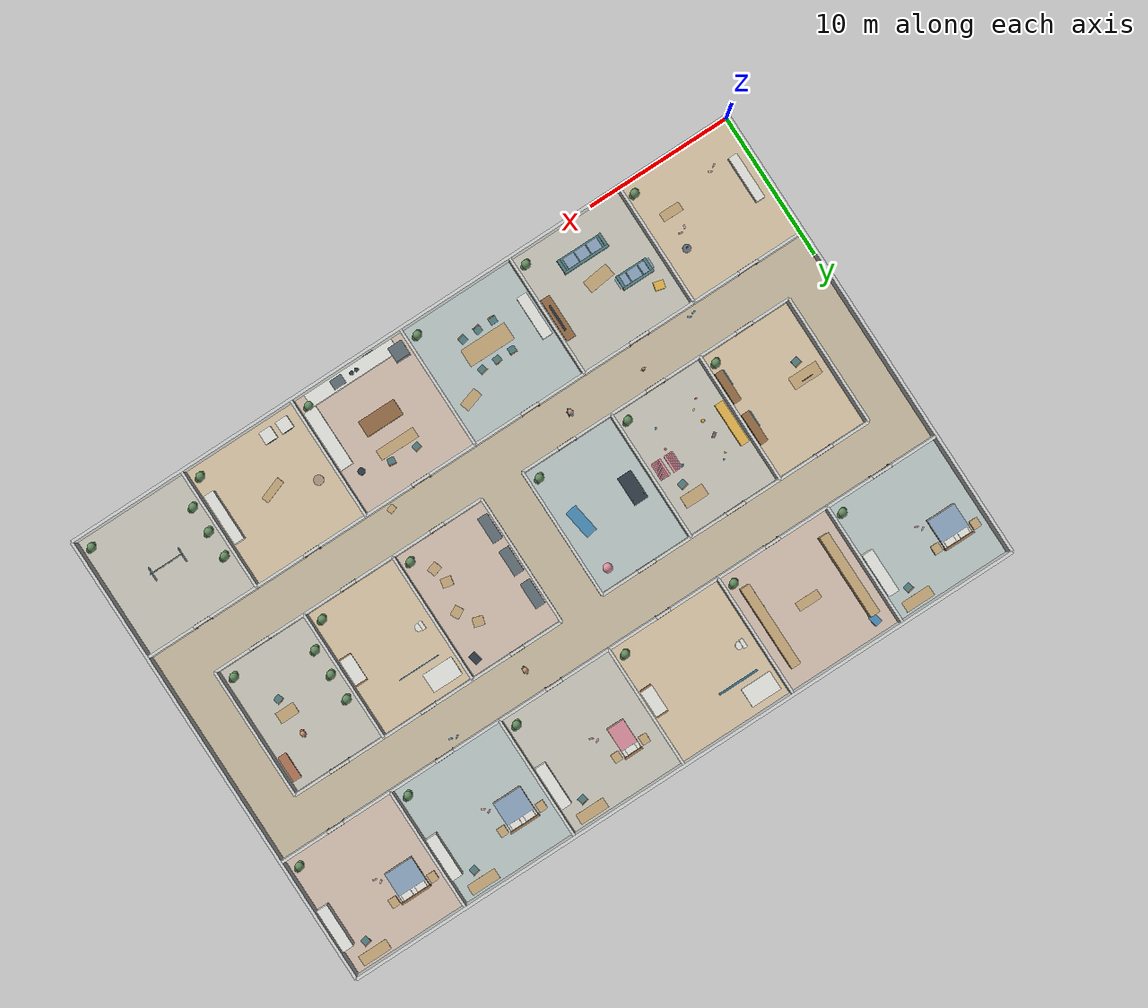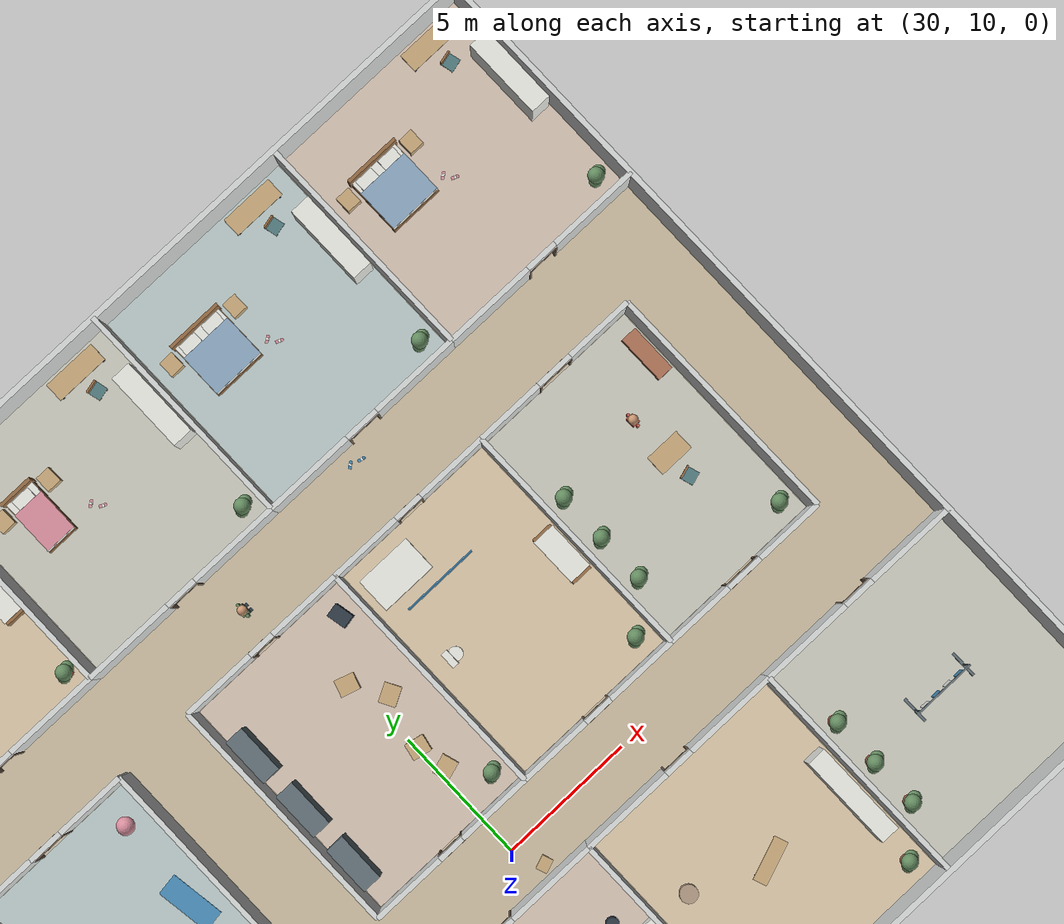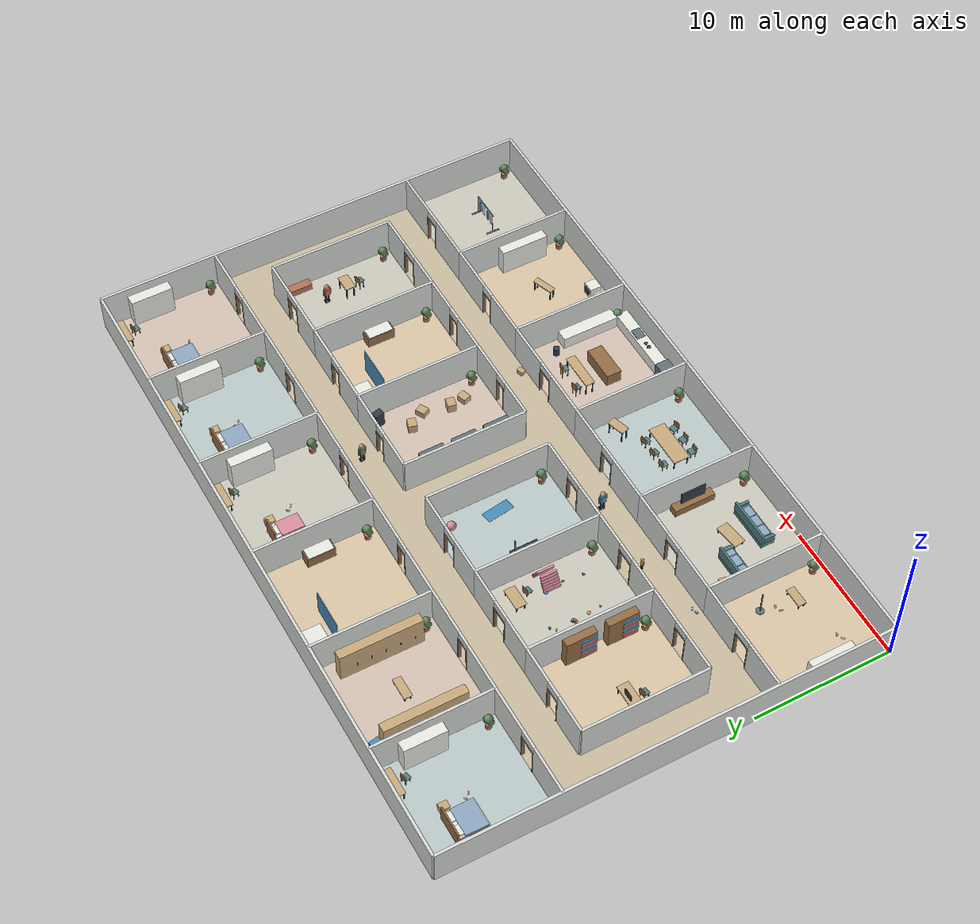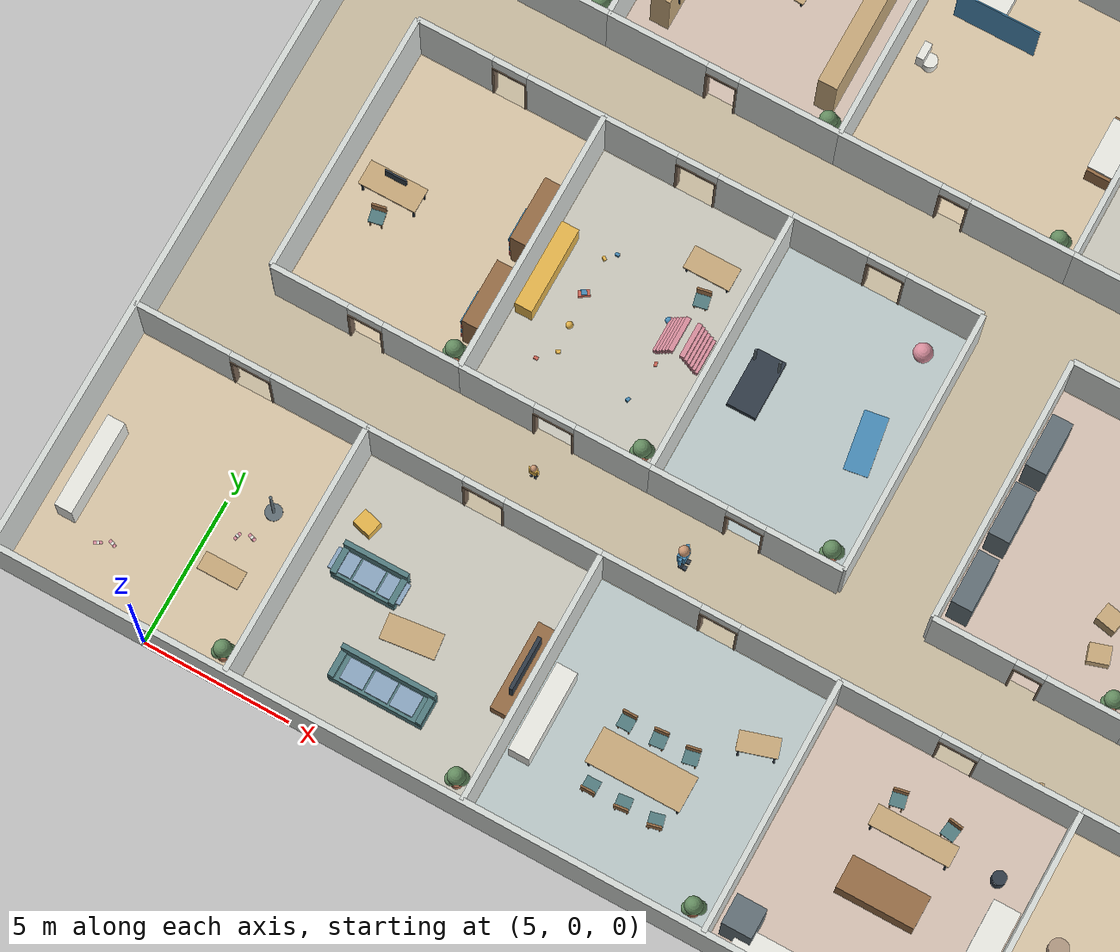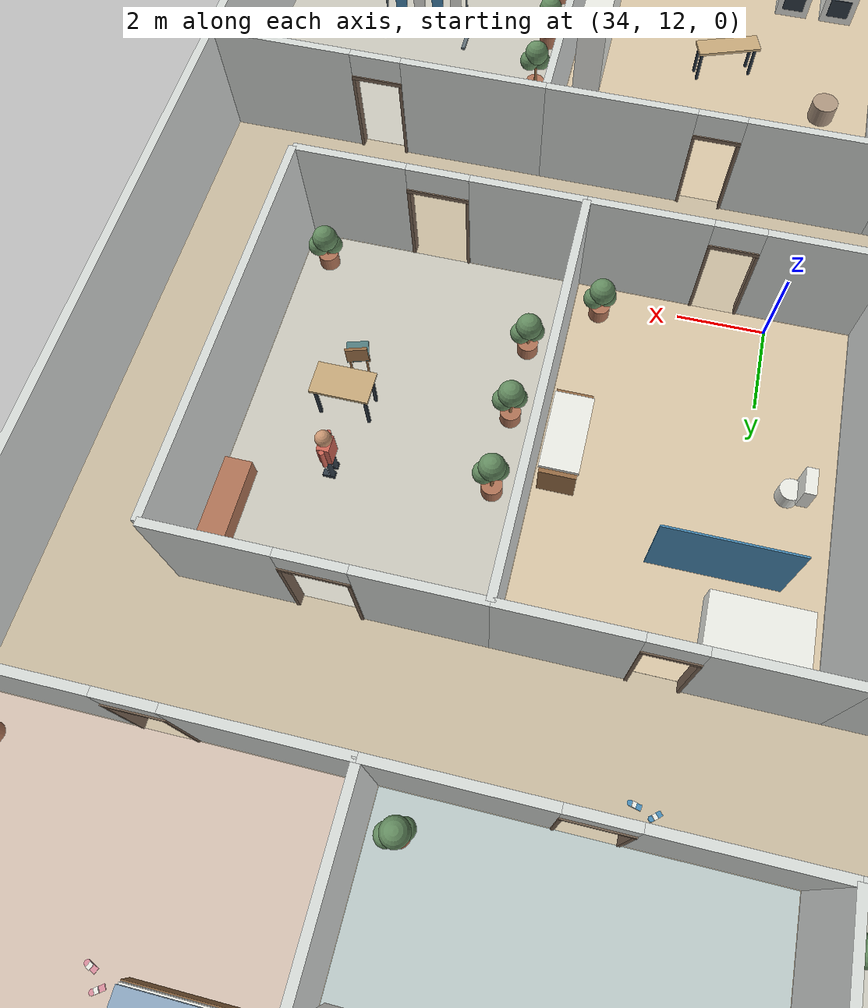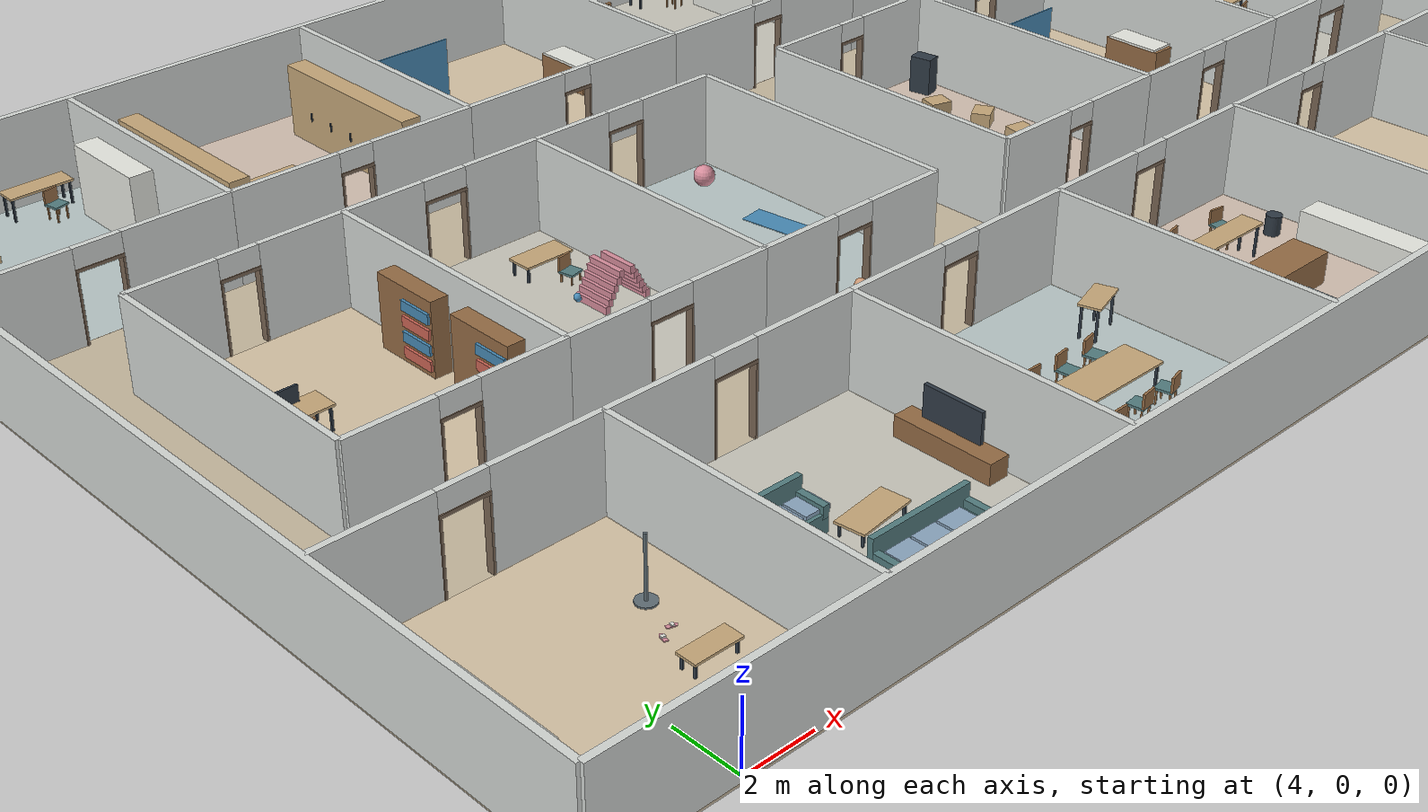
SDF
<?xml version='1.0' encoding='utf-8'?>
<sdf version="1.9">
  <world name="default">
    <gravity>0 0 -9.81</gravity>
    <plugin filename="gz-sim-physics-system" name="gz::sim::systems::Physics" />
    <plugin filename="gz-sim-scene-broadcaster-system" name="gz::sim::systems::SceneBroadcaster" />
    <plugin filename="gz-sim-user-commands-system" name="gz::sim::systems::UserCommands" />
    <plugin filename="gz-sim-sensors-system" name="gz::sim::systems::Sensors">
      <render_engine>ogre2</render_engine>
    </plugin>
    <plugin filename="gz-sim-imu-system" name="gz::sim::systems::Imu" />
    <light type="directional" name="direct_light">
      <cast_shadows>true</cast_shadows>
      <pose>14.55 7.5 10 0 0 0</pose>
      <diffuse>1 1 1 1</diffuse>
      <specular>0.5 0.5 0.5 1</specular>
      <attenuation>
        <range>1000</range>
        <constant>0.9</constant>
        <linear>0.01</linear>
        <quadratic>0.001</quadratic>
      </attenuation>
      <direction>0 0 -1</direction>
    </light>
    <include>
      <uri>model://home_large</uri>
      <pose>0 0 0 0 0 0</pose>
      <name>home_large</name>
    </include>
    <physics name="2ms" type="ignored">
      <max_step_size>0.002</max_step_size>
      <real_time_factor>1.0</real_time_factor>
    </physics>
    <scene>
      <ambient>0.65 0.65 0.65 1</ambient>
      <background>0.85 0.89 0.92 1</background>
    </scene>
    <model name="person_adult_hall">
      <static>true</static>
      <pose>18 10 0 0 0 0</pose>
      <link name="body">
        <collision name="leg-1">
          <pose>0 -0.11 0.39 0 0 0</pose>
          <geometry>
            <cylinder>
              <radius>0.065</radius>
              <length>0.78</length>
            </cylinder>
          </geometry>
          <surface>
            <friction>
              <ode>
                <mu>1</mu>
                <mu2>1</mu2>
              </ode>
            </friction>
          </surface>
        </collision>
        <visual name="leg-1_visual">
          <pose>0 -0.11 0.39 0 0 0</pose>
          <geometry>
            <cylinder>
              <radius>0.065</radius>
              <length>0.78</length>
            </cylinder>
          </geometry>
          <material>
            <ambient>0.188235294 0.231372549 0.274509804 1</ambient>
            <diffuse>0.188235294 0.231372549 0.274509804 1</diffuse>
          </material>
        </visual>
        <collision name="foot-1">
          <pose>0.06 -0.11 0.055 0 0 0</pose>
          <geometry>
            <box>
              <size>0.27 0.14 0.11</size>
            </box>
          </geometry>
          <surface>
            <friction>
              <ode>
                <mu>1</mu>
                <mu2>1</mu2>
              </ode>
            </friction>
          </surface>
        </collision>
        <visual name="foot-1_visual">
          <pose>0.06 -0.11 0.055 0 0 0</pose>
          <geometry>
            <box>
              <size>0.27 0.14 0.11</size>
            </box>
          </geometry>
          <material>
            <ambient>0.188235294 0.231372549 0.274509804 1</ambient>
            <diffuse>0.188235294 0.231372549 0.274509804 1</diffuse>
          </material>
        </visual>
        <collision name="arm-1">
          <pose>0 -0.245 1.1 0 0 0</pose>
          <geometry>
            <cylinder>
              <radius>0.055</radius>
              <length>0.6</length>
            </cylinder>
          </geometry>
          <surface>
            <friction>
              <ode>
                <mu>1</mu>
                <mu2>1</mu2>
              </ode>
            </friction>
          </surface>
        </collision>
        <visual name="arm-1_visual">
          <pose>0 -0.245 1.1 0 0 0</pose>
          <geometry>
            <cylinder>
              <radius>0.055</radius>
              <length>0.6</length>
            </cylinder>
          </geometry>
          <material>
            <ambient>0.282352941 0.545098039 0.71372549 1</ambient>
            <diffuse>0.282352941 0.545098039 0.71372549 1</diffuse>
          </material>
        </visual>
        <collision name="leg1">
          <pose>0 0.11 0.39 0 0 0</pose>
          <geometry>
            <cylinder>
              <radius>0.065</radius>
              <length>0.78</length>
            </cylinder>
          </geometry>
          <surface>
            <friction>
              <ode>
                <mu>1</mu>
                <mu2>1</mu2>
              </ode>
            </friction>
          </surface>
        </collision>
        <visual name="leg1_visual">
          <pose>0 0.11 0.39 0 0 0</pose>
          <geometry>
            <cylinder>
              <radius>0.065</radius>
              <length>0.78</length>
            </cylinder>
          </geometry>
          <material>
            <ambient>0.188235294 0.231372549 0.274509804 1</ambient>
            <diffuse>0.188235294 0.231372549 0.274509804 1</diffuse>
          </material>
        </visual>
        <collision name="foot1">
          <pose>0.06 0.11 0.055 0 0 0</pose>
          <geometry>
            <box>
              <size>0.27 0.14 0.11</size>
            </box>
          </geometry>
          <surface>
            <friction>
              <ode>
                <mu>1</mu>
                <mu2>1</mu2>
              </ode>
            </friction>
          </surface>
        </collision>
        <visual name="foot1_visual">
          <pose>0.06 0.11 0.055 0 0 0</pose>
          <geometry>
            <box>
              <size>0.27 0.14 0.11</size>
            </box>
          </geometry>
          <material>
            <ambient>0.188235294 0.231372549 0.274509804 1</ambient>
            <diffuse>0.188235294 0.231372549 0.274509804 1</diffuse>
          </material>
        </visual>
        <collision name="arm1">
          <pose>0 0.245 1.1 0 0 0</pose>
          <geometry>
            <cylinder>
              <radius>0.055</radius>
              <length>0.6</length>
            </cylinder>
          </geometry>
          <surface>
            <friction>
              <ode>
                <mu>1</mu>
                <mu2>1</mu2>
              </ode>
            </friction>
          </surface>
        </collision>
        <visual name="arm1_visual">
          <pose>0 0.245 1.1 0 0 0</pose>
          <geometry>
            <cylinder>
              <radius>0.055</radius>
              <length>0.6</length>
            </cylinder>
          </geometry>
          <material>
            <ambient>0.282352941 0.545098039 0.71372549 1</ambient>
            <diffuse>0.282352941 0.545098039 0.71372549 1</diffuse>
          </material>
        </visual>
        <collision name="torso">
          <pose>0 0 1.08 0 0 0</pose>
          <geometry>
            <box>
              <size>0.27 0.38 0.6</size>
            </box>
          </geometry>
          <surface>
            <friction>
              <ode>
                <mu>1</mu>
                <mu2>1</mu2>
              </ode>
            </friction>
          </surface>
        </collision>
        <visual name="torso_visual">
          <pose>0 0 1.08 0 0 0</pose>
          <geometry>
            <box>
              <size>0.27 0.38 0.6</size>
            </box>
          </geometry>
          <material>
            <ambient>0.282352941 0.545098039 0.71372549 1</ambient>
            <diffuse>0.282352941 0.545098039 0.71372549 1</diffuse>
          </material>
        </visual>
        <collision name="head">
          <pose>0 0 1.57 0 0 0</pose>
          <geometry>
            <sphere>
              <radius>0.18</radius>
            </sphere>
          </geometry>
          <surface>
            <friction>
              <ode>
                <mu>1</mu>
                <mu2>1</mu2>
              </ode>
            </friction>
          </surface>
        </collision>
        <visual name="head_visual">
          <pose>0 0 1.57 0 0 0</pose>
          <geometry>
            <sphere>
              <radius>0.18</radius>
            </sphere>
          </geometry>
          <material>
            <ambient>0.788235294 0.588235294 0.447058824 1</ambient>
            <diffuse>0.788235294 0.588235294 0.447058824 1</diffuse>
          </material>
        </visual>
      </link>
      <plugin filename="libScriptedObstacle.so" name="sentry_simulation::ScriptedObstacle">
        <enabled>true</enabled>
        <topic>/home_large/people/enabled</topic>
        <waypoint>
          <time>0</time>
          <pose>18 10 0 0 0 0</pose>
        </waypoint>
        <waypoint>
          <time>8</time>
          <pose>24 10 0 0 0 0</pose>
        </waypoint>
        <waypoint>
          <time>10</time>
          <pose>24 10 0 0 0 3.14159265</pose>
        </waypoint>
        <waypoint>
          <time>18</time>
          <pose>18 10 0 0 0 3.14159265</pose>
        </waypoint>
        <waypoint>
          <time>20</time>
          <pose>18 10 0 0 0 0</pose>
        </waypoint>
      </plugin>
    </model>
    <model name="person_adult_north">
      <static>true</static>
      <pose>29 21.8 0 0 0 0</pose>
      <link name="body">
        <collision name="leg-1">
          <pose>0 -0.1056 0.3744 0 0 0</pose>
          <geometry>
            <cylinder>
              <radius>0.0624</radius>
              <length>0.7488</length>
            </cylinder>
          </geometry>
          <surface>
            <friction>
              <ode>
                <mu>1</mu>
                <mu2>1</mu2>
              </ode>
            </friction>
          </surface>
        </collision>
        <visual name="leg-1_visual">
          <pose>0 -0.1056 0.3744 0 0 0</pose>
          <geometry>
            <cylinder>
              <radius>0.0624</radius>
              <length>0.7488</length>
            </cylinder>
          </geometry>
          <material>
            <ambient>0.188235294 0.231372549 0.274509804 1</ambient>
            <diffuse>0.188235294 0.231372549 0.274509804 1</diffuse>
          </material>
        </visual>
        <collision name="foot-1">
          <pose>0.0576 -0.1056 0.0528 0 0 0</pose>
          <geometry>
            <box>
              <size>0.2592 0.1344 0.1056</size>
            </box>
          </geometry>
          <surface>
            <friction>
              <ode>
                <mu>1</mu>
                <mu2>1</mu2>
              </ode>
            </friction>
          </surface>
        </collision>
        <visual name="foot-1_visual">
          <pose>0.0576 -0.1056 0.0528 0 0 0</pose>
          <geometry>
            <box>
              <size>0.2592 0.1344 0.1056</size>
            </box>
          </geometry>
          <material>
            <ambient>0.188235294 0.231372549 0.274509804 1</ambient>
            <diffuse>0.188235294 0.231372549 0.274509804 1</diffuse>
          </material>
        </visual>
        <collision name="arm-1">
          <pose>0 -0.2352 1.056 0 0 0</pose>
          <geometry>
            <cylinder>
              <radius>0.0528</radius>
              <length>0.576</length>
            </cylinder>
          </geometry>
          <surface>
            <friction>
              <ode>
                <mu>1</mu>
                <mu2>1</mu2>
              </ode>
            </friction>
          </surface>
        </collision>
        <visual name="arm-1_visual">
          <pose>0 -0.2352 1.056 0 0 0</pose>
          <geometry>
            <cylinder>
              <radius>0.0528</radius>
              <length>0.576</length>
            </cylinder>
          </geometry>
          <material>
            <ambient>0.403921569 0.529411765 0.356862745 1</ambient>
            <diffuse>0.403921569 0.529411765 0.356862745 1</diffuse>
          </material>
        </visual>
        <collision name="leg1">
          <pose>0 0.1056 0.3744 0 0 0</pose>
          <geometry>
            <cylinder>
              <radius>0.0624</radius>
              <length>0.7488</length>
            </cylinder>
          </geometry>
          <surface>
            <friction>
              <ode>
                <mu>1</mu>
                <mu2>1</mu2>
              </ode>
            </friction>
          </surface>
        </collision>
        <visual name="leg1_visual">
          <pose>0 0.1056 0.3744 0 0 0</pose>
          <geometry>
            <cylinder>
              <radius>0.0624</radius>
              <length>0.7488</length>
            </cylinder>
          </geometry>
          <material>
            <ambient>0.188235294 0.231372549 0.274509804 1</ambient>
            <diffuse>0.188235294 0.231372549 0.274509804 1</diffuse>
          </material>
        </visual>
        <collision name="foot1">
          <pose>0.0576 0.1056 0.0528 0 0 0</pose>
          <geometry>
            <box>
              <size>0.2592 0.1344 0.1056</size>
            </box>
          </geometry>
          <surface>
            <friction>
              <ode>
                <mu>1</mu>
                <mu2>1</mu2>
              </ode>
            </friction>
          </surface>
        </collision>
        <visual name="foot1_visual">
          <pose>0.0576 0.1056 0.0528 0 0 0</pose>
          <geometry>
            <box>
              <size>0.2592 0.1344 0.1056</size>
            </box>
          </geometry>
          <material>
            <ambient>0.188235294 0.231372549 0.274509804 1</ambient>
            <diffuse>0.188235294 0.231372549 0.274509804 1</diffuse>
          </material>
        </visual>
        <collision name="arm1">
          <pose>0 0.2352 1.056 0 0 0</pose>
          <geometry>
            <cylinder>
              <radius>0.0528</radius>
              <length>0.576</length>
            </cylinder>
          </geometry>
          <surface>
            <friction>
              <ode>
                <mu>1</mu>
                <mu2>1</mu2>
              </ode>
            </friction>
          </surface>
        </collision>
        <visual name="arm1_visual">
          <pose>0 0.2352 1.056 0 0 0</pose>
          <geometry>
            <cylinder>
              <radius>0.0528</radius>
              <length>0.576</length>
            </cylinder>
          </geometry>
          <material>
            <ambient>0.403921569 0.529411765 0.356862745 1</ambient>
            <diffuse>0.403921569 0.529411765 0.356862745 1</diffuse>
          </material>
        </visual>
        <collision name="torso">
          <pose>0 0 1.0368 0 0 0</pose>
          <geometry>
            <box>
              <size>0.2592 0.3648 0.576</size>
            </box>
          </geometry>
          <surface>
            <friction>
              <ode>
                <mu>1</mu>
                <mu2>1</mu2>
              </ode>
            </friction>
          </surface>
        </collision>
        <visual name="torso_visual">
          <pose>0 0 1.0368 0 0 0</pose>
          <geometry>
            <box>
              <size>0.2592 0.3648 0.576</size>
            </box>
          </geometry>
          <material>
            <ambient>0.403921569 0.529411765 0.356862745 1</ambient>
            <diffuse>0.403921569 0.529411765 0.356862745 1</diffuse>
          </material>
        </visual>
        <collision name="head">
          <pose>0 0 1.5072 0 0 0</pose>
          <geometry>
            <sphere>
              <radius>0.17279999999999998</radius>
            </sphere>
          </geometry>
          <surface>
            <friction>
              <ode>
                <mu>1</mu>
                <mu2>1</mu2>
              </ode>
            </friction>
          </surface>
        </collision>
        <visual name="head_visual">
          <pose>0 0 1.5072 0 0 0</pose>
          <geometry>
            <sphere>
              <radius>0.17279999999999998</radius>
            </sphere>
          </geometry>
          <material>
            <ambient>0.788235294 0.588235294 0.447058824 1</ambient>
            <diffuse>0.788235294 0.588235294 0.447058824 1</diffuse>
          </material>
        </visual>
      </link>
      <plugin filename="libScriptedObstacle.so" name="sentry_simulation::ScriptedObstacle">
        <enabled>true</enabled>
        <topic>/home_large/people/enabled</topic>
        <waypoint>
          <time>0</time>
          <pose>29 21.8 0 0 0 0</pose>
        </waypoint>
        <waypoint>
          <time>7</time>
          <pose>34 21.8 0 0 0 0</pose>
        </waypoint>
        <waypoint>
          <time>9</time>
          <pose>34 21.8 0 0 0 3.14159265</pose>
        </waypoint>
        <waypoint>
          <time>16</time>
          <pose>29 21.8 0 0 0 3.14159265</pose>
        </waypoint>
        <waypoint>
          <time>18</time>
          <pose>29 21.8 0 0 0 0</pose>
        </waypoint>
      </plugin>
    </model>
    <model name="person_child">
      <static>true</static>
      <pose>12.75 10.2 0 0 0 1.57079633</pose>
      <link name="body">
        <collision name="leg-1">
          <pose>0 -0.066 0.234 0 0 0</pose>
          <geometry>
            <cylinder>
              <radius>0.039</radius>
              <length>0.46799999999999997</length>
            </cylinder>
          </geometry>
          <surface>
            <friction>
              <ode>
                <mu>1</mu>
                <mu2>1</mu2>
              </ode>
            </friction>
          </surface>
        </collision>
        <visual name="leg-1_visual">
          <pose>0 -0.066 0.234 0 0 0</pose>
          <geometry>
            <cylinder>
              <radius>0.039</radius>
              <length>0.46799999999999997</length>
            </cylinder>
          </geometry>
          <material>
            <ambient>0.188235294 0.231372549 0.274509804 1</ambient>
            <diffuse>0.188235294 0.231372549 0.274509804 1</diffuse>
          </material>
        </visual>
        <collision name="foot-1">
          <pose>0.036 -0.066 0.033 0 0 0</pose>
          <geometry>
            <box>
              <size>0.162 0.084 0.066</size>
            </box>
          </geometry>
          <surface>
            <friction>
              <ode>
                <mu>1</mu>
                <mu2>1</mu2>
              </ode>
            </friction>
          </surface>
        </collision>
        <visual name="foot-1_visual">
          <pose>0.036 -0.066 0.033 0 0 0</pose>
          <geometry>
            <box>
              <size>0.162 0.084 0.066</size>
            </box>
          </geometry>
          <material>
            <ambient>0.188235294 0.231372549 0.274509804 1</ambient>
            <diffuse>0.188235294 0.231372549 0.274509804 1</diffuse>
          </material>
        </visual>
        <collision name="arm-1">
          <pose>0 -0.147 0.66 0 0 0</pose>
          <geometry>
            <cylinder>
              <radius>0.033</radius>
              <length>0.36</length>
            </cylinder>
          </geometry>
          <surface>
            <friction>
              <ode>
                <mu>1</mu>
                <mu2>1</mu2>
              </ode>
            </friction>
          </surface>
        </collision>
        <visual name="arm-1_visual">
          <pose>0 -0.147 0.66 0 0 0</pose>
          <geometry>
            <cylinder>
              <radius>0.033</radius>
              <length>0.36</length>
            </cylinder>
          </geometry>
          <material>
            <ambient>0.894117647 0.705882353 0.294117647 1</ambient>
            <diffuse>0.894117647 0.705882353 0.294117647 1</diffuse>
          </material>
        </visual>
        <collision name="leg1">
          <pose>0 0.066 0.234 0 0 0</pose>
          <geometry>
            <cylinder>
              <radius>0.039</radius>
              <length>0.46799999999999997</length>
            </cylinder>
          </geometry>
          <surface>
            <friction>
              <ode>
                <mu>1</mu>
                <mu2>1</mu2>
              </ode>
            </friction>
          </surface>
        </collision>
        <visual name="leg1_visual">
          <pose>0 0.066 0.234 0 0 0</pose>
          <geometry>
            <cylinder>
              <radius>0.039</radius>
              <length>0.46799999999999997</length>
            </cylinder>
          </geometry>
          <material>
            <ambient>0.188235294 0.231372549 0.274509804 1</ambient>
            <diffuse>0.188235294 0.231372549 0.274509804 1</diffuse>
          </material>
        </visual>
        <collision name="foot1">
          <pose>0.036 0.066 0.033 0 0 0</pose>
          <geometry>
            <box>
              <size>0.162 0.084 0.066</size>
            </box>
          </geometry>
          <surface>
            <friction>
              <ode>
                <mu>1</mu>
                <mu2>1</mu2>
              </ode>
            </friction>
          </surface>
        </collision>
        <visual name="foot1_visual">
          <pose>0.036 0.066 0.033 0 0 0</pose>
          <geometry>
            <box>
              <size>0.162 0.084 0.066</size>
            </box>
          </geometry>
          <material>
            <ambient>0.188235294 0.231372549 0.274509804 1</ambient>
            <diffuse>0.188235294 0.231372549 0.274509804 1</diffuse>
          </material>
        </visual>
        <collision name="arm1">
          <pose>0 0.147 0.66 0 0 0</pose>
          <geometry>
            <cylinder>
              <radius>0.033</radius>
              <length>0.36</length>
            </cylinder>
          </geometry>
          <surface>
            <friction>
              <ode>
                <mu>1</mu>
                <mu2>1</mu2>
              </ode>
            </friction>
          </surface>
        </collision>
        <visual name="arm1_visual">
          <pose>0 0.147 0.66 0 0 0</pose>
          <geometry>
            <cylinder>
              <radius>0.033</radius>
              <length>0.36</length>
            </cylinder>
          </geometry>
          <material>
            <ambient>0.894117647 0.705882353 0.294117647 1</ambient>
            <diffuse>0.894117647 0.705882353 0.294117647 1</diffuse>
          </material>
        </visual>
        <collision name="torso">
          <pose>0 0 0.648 0 0 0</pose>
          <geometry>
            <box>
              <size>0.162 0.228 0.36</size>
            </box>
          </geometry>
          <surface>
            <friction>
              <ode>
                <mu>1</mu>
                <mu2>1</mu2>
              </ode>
            </friction>
          </surface>
        </collision>
        <visual name="torso_visual">
          <pose>0 0 0.648 0 0 0</pose>
          <geometry>
            <box>
              <size>0.162 0.228 0.36</size>
            </box>
          </geometry>
          <material>
            <ambient>0.894117647 0.705882353 0.294117647 1</ambient>
            <diffuse>0.894117647 0.705882353 0.294117647 1</diffuse>
          </material>
        </visual>
        <collision name="head">
          <pose>0 0 0.942 0 0 0</pose>
          <geometry>
            <sphere>
              <radius>0.108</radius>
            </sphere>
          </geometry>
          <surface>
            <friction>
              <ode>
                <mu>1</mu>
                <mu2>1</mu2>
              </ode>
            </friction>
          </surface>
        </collision>
        <visual name="head_visual">
          <pose>0 0 0.942 0 0 0</pose>
          <geometry>
            <sphere>
              <radius>0.108</radius>
            </sphere>
          </geometry>
          <material>
            <ambient>0.788235294 0.588235294 0.447058824 1</ambient>
            <diffuse>0.788235294 0.588235294 0.447058824 1</diffuse>
          </material>
        </visual>
      </link>
      <plugin filename="libScriptedObstacle.so" name="sentry_simulation::ScriptedObstacle">
        <enabled>true</enabled>
        <topic>/home_large/people/enabled</topic>
        <waypoint>
          <time>0</time>
          <pose>12.75 10.2 0 0 0 1.57079633</pose>
        </waypoint>
        <waypoint>
          <time>9</time>
          <pose>12.75 14 0 0 0 1.57079633</pose>
        </waypoint>
        <waypoint>
          <time>11</time>
          <pose>12.75 14 0 0 0 -1.57079633</pose>
        </waypoint>
        <waypoint>
          <time>20</time>
          <pose>12.75 10.2 0 0 0 -1.57079633</pose>
        </waypoint>
        <waypoint>
          <time>22</time>
          <pose>12.75 10.2 0 0 0 1.57079633</pose>
        </waypoint>
      </plugin>
    </model>
    <model name="person_standing">
      <static>true</static>
      <pose>42.6 17.6 0 0 0 0</pose>
      <link name="body">
        <collision name="leg-1">
          <pose>0 -0.108114286 0.383314286 0 0 0</pose>
          <geometry>
            <cylinder>
              <radius>0.0638857142857143</radius>
              <length>0.7666285714285714</length>
            </cylinder>
          </geometry>
          <surface>
            <friction>
              <ode>
                <mu>1</mu>
                <mu2>1</mu2>
              </ode>
            </friction>
          </surface>
        </collision>
        <visual name="leg-1_visual">
          <pose>0 -0.108114286 0.383314286 0 0 0</pose>
          <geometry>
            <cylinder>
              <radius>0.0638857142857143</radius>
              <length>0.7666285714285714</length>
            </cylinder>
          </geometry>
          <material>
            <ambient>0.188235294 0.231372549 0.274509804 1</ambient>
            <diffuse>0.188235294 0.231372549 0.274509804 1</diffuse>
          </material>
        </visual>
        <collision name="foot-1">
          <pose>0.0589714286 -0.108114286 0.0540571429 0 0 0</pose>
          <geometry>
            <box>
              <size>0.265371429 0.1376 0.108114286</size>
            </box>
          </geometry>
          <surface>
            <friction>
              <ode>
                <mu>1</mu>
                <mu2>1</mu2>
              </ode>
            </friction>
          </surface>
        </collision>
        <visual name="foot-1_visual">
          <pose>0.0589714286 -0.108114286 0.0540571429 0 0 0</pose>
          <geometry>
            <box>
              <size>0.265371429 0.1376 0.108114286</size>
            </box>
          </geometry>
          <material>
            <ambient>0.188235294 0.231372549 0.274509804 1</ambient>
            <diffuse>0.188235294 0.231372549 0.274509804 1</diffuse>
          </material>
        </visual>
        <collision name="arm-1">
          <pose>0 -0.2408 1.08114286 0 0 0</pose>
          <geometry>
            <cylinder>
              <radius>0.05405714285714286</radius>
              <length>0.5897142857142857</length>
            </cylinder>
          </geometry>
          <surface>
            <friction>
              <ode>
                <mu>1</mu>
                <mu2>1</mu2>
              </ode>
            </friction>
          </surface>
        </collision>
        <visual name="arm-1_visual">
          <pose>0 -0.2408 1.08114286 0 0 0</pose>
          <geometry>
            <cylinder>
              <radius>0.05405714285714286</radius>
              <length>0.5897142857142857</length>
            </cylinder>
          </geometry>
          <material>
            <ambient>0.8 0.396078431 0.333333333 1</ambient>
            <diffuse>0.8 0.396078431 0.333333333 1</diffuse>
          </material>
        </visual>
        <collision name="leg1">
          <pose>0 0.108114286 0.383314286 0 0 0</pose>
          <geometry>
            <cylinder>
              <radius>0.0638857142857143</radius>
              <length>0.7666285714285714</length>
            </cylinder>
          </geometry>
          <surface>
            <friction>
              <ode>
                <mu>1</mu>
                <mu2>1</mu2>
              </ode>
            </friction>
          </surface>
        </collision>
        <visual name="leg1_visual">
          <pose>0 0.108114286 0.383314286 0 0 0</pose>
          <geometry>
            <cylinder>
              <radius>0.0638857142857143</radius>
              <length>0.7666285714285714</length>
            </cylinder>
          </geometry>
          <material>
            <ambient>0.188235294 0.231372549 0.274509804 1</ambient>
            <diffuse>0.188235294 0.231372549 0.274509804 1</diffuse>
          </material>
        </visual>
        <collision name="foot1">
          <pose>0.0589714286 0.108114286 0.0540571429 0 0 0</pose>
          <geometry>
            <box>
              <size>0.265371429 0.1376 0.108114286</size>
            </box>
          </geometry>
          <surface>
            <friction>
              <ode>
                <mu>1</mu>
                <mu2>1</mu2>
              </ode>
            </friction>
          </surface>
        </collision>
        <visual name="foot1_visual">
          <pose>0.0589714286 0.108114286 0.0540571429 0 0 0</pose>
          <geometry>
            <box>
              <size>0.265371429 0.1376 0.108114286</size>
            </box>
          </geometry>
          <material>
            <ambient>0.188235294 0.231372549 0.274509804 1</ambient>
            <diffuse>0.188235294 0.231372549 0.274509804 1</diffuse>
          </material>
        </visual>
        <collision name="arm1">
          <pose>0 0.2408 1.08114286 0 0 0</pose>
          <geometry>
            <cylinder>
              <radius>0.05405714285714286</radius>
              <length>0.5897142857142857</length>
            </cylinder>
          </geometry>
          <surface>
            <friction>
              <ode>
                <mu>1</mu>
                <mu2>1</mu2>
              </ode>
            </friction>
          </surface>
        </collision>
        <visual name="arm1_visual">
          <pose>0 0.2408 1.08114286 0 0 0</pose>
          <geometry>
            <cylinder>
              <radius>0.05405714285714286</radius>
              <length>0.5897142857142857</length>
            </cylinder>
          </geometry>
          <material>
            <ambient>0.8 0.396078431 0.333333333 1</ambient>
            <diffuse>0.8 0.396078431 0.333333333 1</diffuse>
          </material>
        </visual>
        <collision name="torso">
          <pose>0 0 1.06148571 0 0 0</pose>
          <geometry>
            <box>
              <size>0.265371429 0.373485714 0.589714286</size>
            </box>
          </geometry>
          <surface>
            <friction>
              <ode>
                <mu>1</mu>
                <mu2>1</mu2>
              </ode>
            </friction>
          </surface>
        </collision>
        <visual name="torso_visual">
          <pose>0 0 1.06148571 0 0 0</pose>
          <geometry>
            <box>
              <size>0.265371429 0.373485714 0.589714286</size>
            </box>
          </geometry>
          <material>
            <ambient>0.8 0.396078431 0.333333333 1</ambient>
            <diffuse>0.8 0.396078431 0.333333333 1</diffuse>
          </material>
        </visual>
        <collision name="head">
          <pose>0 0 1.54308571 0 0 0</pose>
          <geometry>
            <sphere>
              <radius>0.17691428571428572</radius>
            </sphere>
          </geometry>
          <surface>
            <friction>
              <ode>
                <mu>1</mu>
                <mu2>1</mu2>
              </ode>
            </friction>
          </surface>
        </collision>
        <visual name="head_visual">
          <pose>0 0 1.54308571 0 0 0</pose>
          <geometry>
            <sphere>
              <radius>0.17691428571428572</radius>
            </sphere>
          </geometry>
          <material>
            <ambient>0.788235294 0.588235294 0.447058824 1</ambient>
            <diffuse>0.788235294 0.588235294 0.447058824 1</diffuse>
          </material>
        </visual>
      </link>
    </model>
  </world>
</sdf>

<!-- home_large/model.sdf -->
<sdf version="1.9">
  <model name="home_large">
    <static>true</static>
    <link name="house">
      <collision name="floor">
        <pose>24 16 -0.1 0 0 0</pose>
        <geometry>
          <box>
            <size>48 32 0.2</size>
          </box>
        </geometry>
        <surface>
          <friction>
            <ode>
              <mu>1</mu>
              <mu2>1</mu2>
            </ode>
          </friction>
        </surface>
      </collision>
      <visual name="floor_visual">
        <pose>24 16 -0.1 0 0 0</pose>
        <geometry>
          <box>
            <size>48 32 0.2</size>
          </box>
        </geometry>
        <material>
          <ambient>0.780392157 0.725490196 0.623529412 1</ambient>
          <diffuse>0.780392157 0.725490196 0.623529412 1</diffuse>
        </material>
      </visual>
      <collision name="outer_south">
        <pose>24 0 1.4 0 0 0</pose>
        <geometry>
          <box>
            <size>48 0.2 2.8</size>
          </box>
        </geometry>
        <surface>
          <friction>
            <ode>
              <mu>1</mu>
              <mu2>1</mu2>
            </ode>
          </friction>
        </surface>
      </collision>
      <visual name="outer_south_visual">
        <pose>24 0 1.4 0 0 0</pose>
        <geometry>
          <box>
            <size>48 0.2 2.8</size>
          </box>
        </geometry>
        <material>
          <ambient>0.835294118 0.850980392 0.839215686 1</ambient>
          <diffuse>0.835294118 0.850980392 0.839215686 1</diffuse>
        </material>
      </visual>
      <collision name="outer_north">
        <pose>24 32 1.4 0 0 0</pose>
        <geometry>
          <box>
            <size>48 0.2 2.8</size>
          </box>
        </geometry>
        <surface>
          <friction>
            <ode>
              <mu>1</mu>
              <mu2>1</mu2>
            </ode>
          </friction>
        </surface>
      </collision>
      <visual name="outer_north_visual">
        <pose>24 32 1.4 0 0 0</pose>
        <geometry>
          <box>
            <size>48 0.2 2.8</size>
          </box>
        </geometry>
        <material>
          <ambient>0.835294118 0.850980392 0.839215686 1</ambient>
          <diffuse>0.835294118 0.850980392 0.839215686 1</diffuse>
        </material>
      </visual>
      <collision name="outer_west">
        <pose>0 16 1.4 0 0 0</pose>
        <geometry>
          <box>
            <size>0.2 32 2.8</size>
          </box>
        </geometry>
        <surface>
          <friction>
            <ode>
              <mu>1</mu>
              <mu2>1</mu2>
            </ode>
          </friction>
        </surface>
      </collision>
      <visual name="outer_west_visual">
        <pose>0 16 1.4 0 0 0</pose>
        <geometry>
          <box>
            <size>0.2 32 2.8</size>
          </box>
        </geometry>
        <material>
          <ambient>0.835294118 0.850980392 0.839215686 1</ambient>
          <diffuse>0.835294118 0.850980392 0.839215686 1</diffuse>
        </material>
      </visual>
      <collision name="outer_east">
        <pose>48 16 1.4 0 0 0</pose>
        <geometry>
          <box>
            <size>0.2 32 2.8</size>
          </box>
        </geometry>
        <surface>
          <friction>
            <ode>
              <mu>1</mu>
              <mu2>1</mu2>
            </ode>
          </friction>
        </surface>
      </collision>
      <visual name="outer_east_visual">
        <pose>48 16 1.4 0 0 0</pose>
        <geometry>
          <box>
            <size>0.2 32 2.8</size>
          </box>
        </geometry>
        <material>
          <ambient>0.835294118 0.850980392 0.839215686 1</ambient>
          <diffuse>0.835294118 0.850980392 0.839215686 1</diffuse>
        </material>
      </visual>
      <collision name="foyer_door_wall_left">
        <pose>1.6495 8.5 1.4 0 0 0</pose>
        <geometry>
          <box>
            <size>3.299 0.18 2.8</size>
          </box>
        </geometry>
        <surface>
          <friction>
            <ode>
              <mu>1</mu>
              <mu2>1</mu2>
            </ode>
          </friction>
        </surface>
      </collision>
      <visual name="foyer_door_wall_left_visual">
        <pose>1.6495 8.5 1.4 0 0 0</pose>
        <geometry>
          <box>
            <size>3.299 0.18 2.8</size>
          </box>
        </geometry>
        <material>
          <ambient>0.835294118 0.850980392 0.839215686 1</ambient>
          <diffuse>0.835294118 0.850980392 0.839215686 1</diffuse>
        </material>
      </visual>
      <collision name="foyer_door_left">
        <pose>3.334 8.5 1.05 0 0 0</pose>
        <geometry>
          <box>
            <size>0.07 0.24 2.1</size>
          </box>
        </geometry>
        <surface>
          <friction>
            <ode>
              <mu>1</mu>
              <mu2>1</mu2>
            </ode>
          </friction>
        </surface>
      </collision>
      <visual name="foyer_door_left_visual">
        <pose>3.334 8.5 1.05 0 0 0</pose>
        <geometry>
          <box>
            <size>0.07 0.24 2.1</size>
          </box>
        </geometry>
        <material>
          <ambient>0.474509804 0.396078431 0.325490196 1</ambient>
          <diffuse>0.474509804 0.396078431 0.325490196 1</diffuse>
        </material>
      </visual>
      <collision name="foyer_door_wall_right">
        <pose>6.3505 8.5 1.4 0 0 0</pose>
        <geometry>
          <box>
            <size>3.299 0.18 2.8</size>
          </box>
        </geometry>
        <surface>
          <friction>
            <ode>
              <mu>1</mu>
              <mu2>1</mu2>
            </ode>
          </friction>
        </surface>
      </collision>
      <visual name="foyer_door_wall_right_visual">
        <pose>6.3505 8.5 1.4 0 0 0</pose>
        <geometry>
          <box>
            <size>3.299 0.18 2.8</size>
          </box>
        </geometry>
        <material>
          <ambient>0.835294118 0.850980392 0.839215686 1</ambient>
          <diffuse>0.835294118 0.850980392 0.839215686 1</diffuse>
        </material>
      </visual>
      <collision name="foyer_door_right">
        <pose>4.666 8.5 1.05 0 0 0</pose>
        <geometry>
          <box>
            <size>0.07 0.24 2.1</size>
          </box>
        </geometry>
        <surface>
          <friction>
            <ode>
              <mu>1</mu>
              <mu2>1</mu2>
            </ode>
          </friction>
        </surface>
      </collision>
      <visual name="foyer_door_right_visual">
        <pose>4.666 8.5 1.05 0 0 0</pose>
        <geometry>
          <box>
            <size>0.07 0.24 2.1</size>
          </box>
        </geometry>
        <material>
          <ambient>0.474509804 0.396078431 0.325490196 1</ambient>
          <diffuse>0.474509804 0.396078431 0.325490196 1</diffuse>
        </material>
      </visual>
      <collision name="foyer_door_lintel">
        <pose>4 8.5 2.5 0 0 0</pose>
        <geometry>
          <box>
            <size>1.402 0.18 0.6</size>
          </box>
        </geometry>
        <surface>
          <friction>
            <ode>
              <mu>1</mu>
              <mu2>1</mu2>
            </ode>
          </friction>
        </surface>
      </collision>
      <visual name="foyer_door_lintel_visual">
        <pose>4 8.5 2.5 0 0 0</pose>
        <geometry>
          <box>
            <size>1.402 0.18 0.6</size>
          </box>
        </geometry>
        <material>
          <ambient>0.835294118 0.850980392 0.839215686 1</ambient>
          <diffuse>0.835294118 0.850980392 0.839215686 1</diffuse>
        </material>
      </visual>
      <collision name="foyer_door_top">
        <pose>4 8.5 2.15 0 0 0</pose>
        <geometry>
          <box>
            <size>1.402 0.24 0.1</size>
          </box>
        </geometry>
        <surface>
          <friction>
            <ode>
              <mu>1</mu>
              <mu2>1</mu2>
            </ode>
          </friction>
        </surface>
      </collision>
      <visual name="foyer_door_top_visual">
        <pose>4 8.5 2.15 0 0 0</pose>
        <geometry>
          <box>
            <size>1.402 0.24 0.1</size>
          </box>
        </geometry>
        <material>
          <ambient>0.474509804 0.396078431 0.325490196 1</ambient>
          <diffuse>0.474509804 0.396078431 0.325490196 1</diffuse>
        </material>
      </visual>
      <collision name="s_divide1">
        <pose>8 4.25 1.4 0 0 0</pose>
        <geometry>
          <box>
            <size>0.18 8.5 2.8</size>
          </box>
        </geometry>
        <surface>
          <friction>
            <ode>
              <mu>1</mu>
              <mu2>1</mu2>
            </ode>
          </friction>
        </surface>
      </collision>
      <visual name="s_divide1_visual">
        <pose>8 4.25 1.4 0 0 0</pose>
        <geometry>
          <box>
            <size>0.18 8.5 2.8</size>
          </box>
        </geometry>
        <material>
          <ambient>0.835294118 0.850980392 0.839215686 1</ambient>
          <diffuse>0.835294118 0.850980392 0.839215686 1</diffuse>
        </material>
      </visual>
      <collision name="living_door_wall_left">
        <pose>9.6495 8.5 1.4 0 0 0</pose>
        <geometry>
          <box>
            <size>3.299 0.18 2.8</size>
          </box>
        </geometry>
        <surface>
          <friction>
            <ode>
              <mu>1</mu>
              <mu2>1</mu2>
            </ode>
          </friction>
        </surface>
      </collision>
      <visual name="living_door_wall_left_visual">
        <pose>9.6495 8.5 1.4 0 0 0</pose>
        <geometry>
          <box>
            <size>3.299 0.18 2.8</size>
          </box>
        </geometry>
        <material>
          <ambient>0.835294118 0.850980392 0.839215686 1</ambient>
          <diffuse>0.835294118 0.850980392 0.839215686 1</diffuse>
        </material>
      </visual>
      <collision name="living_door_left">
        <pose>11.334 8.5 1.05 0 0 0</pose>
        <geometry>
          <box>
            <size>0.07 0.24 2.1</size>
          </box>
        </geometry>
        <surface>
          <friction>
            <ode>
              <mu>1</mu>
              <mu2>1</mu2>
            </ode>
          </friction>
        </surface>
      </collision>
      <visual name="living_door_left_visual">
        <pose>11.334 8.5 1.05 0 0 0</pose>
        <geometry>
          <box>
            <size>0.07 0.24 2.1</size>
          </box>
        </geometry>
        <material>
          <ambient>0.474509804 0.396078431 0.325490196 1</ambient>
          <diffuse>0.474509804 0.396078431 0.325490196 1</diffuse>
        </material>
      </visual>
      <collision name="living_door_wall_right">
        <pose>14.3505 8.5 1.4 0 0 0</pose>
        <geometry>
          <box>
            <size>3.299 0.18 2.8</size>
          </box>
        </geometry>
        <surface>
          <friction>
            <ode>
              <mu>1</mu>
              <mu2>1</mu2>
            </ode>
          </friction>
        </surface>
      </collision>
      <visual name="living_door_wall_right_visual">
        <pose>14.3505 8.5 1.4 0 0 0</pose>
        <geometry>
          <box>
            <size>3.299 0.18 2.8</size>
          </box>
        </geometry>
        <material>
          <ambient>0.835294118 0.850980392 0.839215686 1</ambient>
          <diffuse>0.835294118 0.850980392 0.839215686 1</diffuse>
        </material>
      </visual>
      <collision name="living_door_right">
        <pose>12.666 8.5 1.05 0 0 0</pose>
        <geometry>
          <box>
            <size>0.07 0.24 2.1</size>
          </box>
        </geometry>
        <surface>
          <friction>
            <ode>
              <mu>1</mu>
              <mu2>1</mu2>
            </ode>
          </friction>
        </surface>
      </collision>
      <visual name="living_door_right_visual">
        <pose>12.666 8.5 1.05 0 0 0</pose>
        <geometry>
          <box>
            <size>0.07 0.24 2.1</size>
          </box>
        </geometry>
        <material>
          <ambient>0.474509804 0.396078431 0.325490196 1</ambient>
          <diffuse>0.474509804 0.396078431 0.325490196 1</diffuse>
        </material>
      </visual>
      <collision name="living_door_lintel">
        <pose>12 8.5 2.5 0 0 0</pose>
        <geometry>
          <box>
            <size>1.402 0.18 0.6</size>
          </box>
        </geometry>
        <surface>
          <friction>
            <ode>
              <mu>1</mu>
              <mu2>1</mu2>
            </ode>
          </friction>
        </surface>
      </collision>
      <visual name="living_door_lintel_visual">
        <pose>12 8.5 2.5 0 0 0</pose>
        <geometry>
          <box>
            <size>1.402 0.18 0.6</size>
          </box>
        </geometry>
        <material>
          <ambient>0.835294118 0.850980392 0.839215686 1</ambient>
          <diffuse>0.835294118 0.850980392 0.839215686 1</diffuse>
        </material>
      </visual>
      <collision name="living_door_top">
        <pose>12 8.5 2.15 0 0 0</pose>
        <geometry>
          <box>
            <size>1.402 0.24 0.1</size>
          </box>
        </geometry>
        <surface>
          <friction>
            <ode>
              <mu>1</mu>
              <mu2>1</mu2>
            </ode>
          </friction>
        </surface>
      </collision>
      <visual name="living_door_top_visual">
        <pose>12 8.5 2.15 0 0 0</pose>
        <geometry>
          <box>
            <size>1.402 0.24 0.1</size>
          </box>
        </geometry>
        <material>
          <ambient>0.474509804 0.396078431 0.325490196 1</ambient>
          <diffuse>0.474509804 0.396078431 0.325490196 1</diffuse>
        </material>
      </visual>
      <collision name="s_divide2">
        <pose>16 4.25 1.4 0 0 0</pose>
        <geometry>
          <box>
            <size>0.18 8.5 2.8</size>
          </box>
        </geometry>
        <surface>
          <friction>
            <ode>
              <mu>1</mu>
              <mu2>1</mu2>
            </ode>
          </friction>
        </surface>
      </collision>
      <visual name="s_divide2_visual">
        <pose>16 4.25 1.4 0 0 0</pose>
        <geometry>
          <box>
            <size>0.18 8.5 2.8</size>
          </box>
        </geometry>
        <material>
          <ambient>0.835294118 0.850980392 0.839215686 1</ambient>
          <diffuse>0.835294118 0.850980392 0.839215686 1</diffuse>
        </material>
      </visual>
      <collision name="dining_door_wall_left">
        <pose>17.6745 8.5 1.4 0 0 0</pose>
        <geometry>
          <box>
            <size>3.349 0.18 2.8</size>
          </box>
        </geometry>
        <surface>
          <friction>
            <ode>
              <mu>1</mu>
              <mu2>1</mu2>
            </ode>
          </friction>
        </surface>
      </collision>
      <visual name="dining_door_wall_left_visual">
        <pose>17.6745 8.5 1.4 0 0 0</pose>
        <geometry>
          <box>
            <size>3.349 0.18 2.8</size>
          </box>
        </geometry>
        <material>
          <ambient>0.835294118 0.850980392 0.839215686 1</ambient>
          <diffuse>0.835294118 0.850980392 0.839215686 1</diffuse>
        </material>
      </visual>
      <collision name="dining_door_left">
        <pose>19.384 8.5 1.05 0 0 0</pose>
        <geometry>
          <box>
            <size>0.07 0.24 2.1</size>
          </box>
        </geometry>
        <surface>
          <friction>
            <ode>
              <mu>1</mu>
              <mu2>1</mu2>
            </ode>
          </friction>
        </surface>
      </collision>
      <visual name="dining_door_left_visual">
        <pose>19.384 8.5 1.05 0 0 0</pose>
        <geometry>
          <box>
            <size>0.07 0.24 2.1</size>
          </box>
        </geometry>
        <material>
          <ambient>0.474509804 0.396078431 0.325490196 1</ambient>
          <diffuse>0.474509804 0.396078431 0.325490196 1</diffuse>
        </material>
      </visual>
      <collision name="dining_door_wall_right">
        <pose>22.3255 8.5 1.4 0 0 0</pose>
        <geometry>
          <box>
            <size>3.349 0.18 2.8</size>
          </box>
        </geometry>
        <surface>
          <friction>
            <ode>
              <mu>1</mu>
              <mu2>1</mu2>
            </ode>
          </friction>
        </surface>
      </collision>
      <visual name="dining_door_wall_right_visual">
        <pose>22.3255 8.5 1.4 0 0 0</pose>
        <geometry>
          <box>
            <size>3.349 0.18 2.8</size>
          </box>
        </geometry>
        <material>
          <ambient>0.835294118 0.850980392 0.839215686 1</ambient>
          <diffuse>0.835294118 0.850980392 0.839215686 1</diffuse>
        </material>
      </visual>
      <collision name="dining_door_right">
        <pose>20.616 8.5 1.05 0 0 0</pose>
        <geometry>
          <box>
            <size>0.07 0.24 2.1</size>
          </box>
        </geometry>
        <surface>
          <friction>
            <ode>
              <mu>1</mu>
              <mu2>1</mu2>
            </ode>
          </friction>
        </surface>
      </collision>
      <visual name="dining_door_right_visual">
        <pose>20.616 8.5 1.05 0 0 0</pose>
        <geometry>
          <box>
            <size>0.07 0.24 2.1</size>
          </box>
        </geometry>
        <material>
          <ambient>0.474509804 0.396078431 0.325490196 1</ambient>
          <diffuse>0.474509804 0.396078431 0.325490196 1</diffuse>
        </material>
      </visual>
      <collision name="dining_door_lintel">
        <pose>20 8.5 2.5 0 0 0</pose>
        <geometry>
          <box>
            <size>1.302 0.18 0.6</size>
          </box>
        </geometry>
        <surface>
          <friction>
            <ode>
              <mu>1</mu>
              <mu2>1</mu2>
            </ode>
          </friction>
        </surface>
      </collision>
      <visual name="dining_door_lintel_visual">
        <pose>20 8.5 2.5 0 0 0</pose>
        <geometry>
          <box>
            <size>1.302 0.18 0.6</size>
          </box>
        </geometry>
        <material>
          <ambient>0.835294118 0.850980392 0.839215686 1</ambient>
          <diffuse>0.835294118 0.850980392 0.839215686 1</diffuse>
        </material>
      </visual>
      <collision name="dining_door_top">
        <pose>20 8.5 2.15 0 0 0</pose>
        <geometry>
          <box>
            <size>1.302 0.24 0.1</size>
          </box>
        </geometry>
        <surface>
          <friction>
            <ode>
              <mu>1</mu>
              <mu2>1</mu2>
            </ode>
          </friction>
        </surface>
      </collision>
      <visual name="dining_door_top_visual">
        <pose>20 8.5 2.15 0 0 0</pose>
        <geometry>
          <box>
            <size>1.302 0.24 0.1</size>
          </box>
        </geometry>
        <material>
          <ambient>0.474509804 0.396078431 0.325490196 1</ambient>
          <diffuse>0.474509804 0.396078431 0.325490196 1</diffuse>
        </material>
      </visual>
      <collision name="s_divide3">
        <pose>24 4.25 1.4 0 0 0</pose>
        <geometry>
          <box>
            <size>0.18 8.5 2.8</size>
          </box>
        </geometry>
        <surface>
          <friction>
            <ode>
              <mu>1</mu>
              <mu2>1</mu2>
            </ode>
          </friction>
        </surface>
      </collision>
      <visual name="s_divide3_visual">
        <pose>24 4.25 1.4 0 0 0</pose>
        <geometry>
          <box>
            <size>0.18 8.5 2.8</size>
          </box>
        </geometry>
        <material>
          <ambient>0.835294118 0.850980392 0.839215686 1</ambient>
          <diffuse>0.835294118 0.850980392 0.839215686 1</diffuse>
        </material>
      </visual>
      <collision name="kitchen_door_wall_left">
        <pose>25.6745 8.5 1.4 0 0 0</pose>
        <geometry>
          <box>
            <size>3.349 0.18 2.8</size>
          </box>
        </geometry>
        <surface>
          <friction>
            <ode>
              <mu>1</mu>
              <mu2>1</mu2>
            </ode>
          </friction>
        </surface>
      </collision>
      <visual name="kitchen_door_wall_left_visual">
        <pose>25.6745 8.5 1.4 0 0 0</pose>
        <geometry>
          <box>
            <size>3.349 0.18 2.8</size>
          </box>
        </geometry>
        <material>
          <ambient>0.835294118 0.850980392 0.839215686 1</ambient>
          <diffuse>0.835294118 0.850980392 0.839215686 1</diffuse>
        </material>
      </visual>
      <collision name="kitchen_door_left">
        <pose>27.384 8.5 1.05 0 0 0</pose>
        <geometry>
          <box>
            <size>0.07 0.24 2.1</size>
          </box>
        </geometry>
        <surface>
          <friction>
            <ode>
              <mu>1</mu>
              <mu2>1</mu2>
            </ode>
          </friction>
        </surface>
      </collision>
      <visual name="kitchen_door_left_visual">
        <pose>27.384 8.5 1.05 0 0 0</pose>
        <geometry>
          <box>
            <size>0.07 0.24 2.1</size>
          </box>
        </geometry>
        <material>
          <ambient>0.474509804 0.396078431 0.325490196 1</ambient>
          <diffuse>0.474509804 0.396078431 0.325490196 1</diffuse>
        </material>
      </visual>
      <collision name="kitchen_door_wall_right">
        <pose>30.3255 8.5 1.4 0 0 0</pose>
        <geometry>
          <box>
            <size>3.349 0.18 2.8</size>
          </box>
        </geometry>
        <surface>
          <friction>
            <ode>
              <mu>1</mu>
              <mu2>1</mu2>
            </ode>
          </friction>
        </surface>
      </collision>
      <visual name="kitchen_door_wall_right_visual">
        <pose>30.3255 8.5 1.4 0 0 0</pose>
        <geometry>
          <box>
            <size>3.349 0.18 2.8</size>
          </box>
        </geometry>
        <material>
          <ambient>0.835294118 0.850980392 0.839215686 1</ambient>
          <diffuse>0.835294118 0.850980392 0.839215686 1</diffuse>
        </material>
      </visual>
      <collision name="kitchen_door_right">
        <pose>28.616 8.5 1.05 0 0 0</pose>
        <geometry>
          <box>
            <size>0.07 0.24 2.1</size>
          </box>
        </geometry>
        <surface>
          <friction>
            <ode>
              <mu>1</mu>
              <mu2>1</mu2>
            </ode>
          </friction>
        </surface>
      </collision>
      <visual name="kitchen_door_right_visual">
        <pose>28.616 8.5 1.05 0 0 0</pose>
        <geometry>
          <box>
            <size>0.07 0.24 2.1</size>
          </box>
        </geometry>
        <material>
          <ambient>0.474509804 0.396078431 0.325490196 1</ambient>
          <diffuse>0.474509804 0.396078431 0.325490196 1</diffuse>
        </material>
      </visual>
      <collision name="kitchen_door_lintel">
        <pose>28 8.5 2.5 0 0 0</pose>
        <geometry>
          <box>
            <size>1.302 0.18 0.6</size>
          </box>
        </geometry>
        <surface>
          <friction>
            <ode>
              <mu>1</mu>
              <mu2>1</mu2>
            </ode>
          </friction>
        </surface>
      </collision>
      <visual name="kitchen_door_lintel_visual">
        <pose>28 8.5 2.5 0 0 0</pose>
        <geometry>
          <box>
            <size>1.302 0.18 0.6</size>
          </box>
        </geometry>
        <material>
          <ambient>0.835294118 0.850980392 0.839215686 1</ambient>
          <diffuse>0.835294118 0.850980392 0.839215686 1</diffuse>
        </material>
      </visual>
      <collision name="kitchen_door_top">
        <pose>28 8.5 2.15 0 0 0</pose>
        <geometry>
          <box>
            <size>1.302 0.24 0.1</size>
          </box>
        </geometry>
        <surface>
          <friction>
            <ode>
              <mu>1</mu>
              <mu2>1</mu2>
            </ode>
          </friction>
        </surface>
      </collision>
      <visual name="kitchen_door_top_visual">
        <pose>28 8.5 2.15 0 0 0</pose>
        <geometry>
          <box>
            <size>1.302 0.24 0.1</size>
          </box>
        </geometry>
        <material>
          <ambient>0.474509804 0.396078431 0.325490196 1</ambient>
          <diffuse>0.474509804 0.396078431 0.325490196 1</diffuse>
        </material>
      </visual>
      <collision name="s_divide4">
        <pose>32 4.25 1.4 0 0 0</pose>
        <geometry>
          <box>
            <size>0.18 8.5 2.8</size>
          </box>
        </geometry>
        <surface>
          <friction>
            <ode>
              <mu>1</mu>
              <mu2>1</mu2>
            </ode>
          </friction>
        </surface>
      </collision>
      <visual name="s_divide4_visual">
        <pose>32 4.25 1.4 0 0 0</pose>
        <geometry>
          <box>
            <size>0.18 8.5 2.8</size>
          </box>
        </geometry>
        <material>
          <ambient>0.835294118 0.850980392 0.839215686 1</ambient>
          <diffuse>0.835294118 0.850980392 0.839215686 1</diffuse>
        </material>
      </visual>
      <collision name="laundry_door_wall_left">
        <pose>33.7245 8.5 1.4 0 0 0</pose>
        <geometry>
          <box>
            <size>3.449 0.18 2.8</size>
          </box>
        </geometry>
        <surface>
          <friction>
            <ode>
              <mu>1</mu>
              <mu2>1</mu2>
            </ode>
          </friction>
        </surface>
      </collision>
      <visual name="laundry_door_wall_left_visual">
        <pose>33.7245 8.5 1.4 0 0 0</pose>
        <geometry>
          <box>
            <size>3.449 0.18 2.8</size>
          </box>
        </geometry>
        <material>
          <ambient>0.835294118 0.850980392 0.839215686 1</ambient>
          <diffuse>0.835294118 0.850980392 0.839215686 1</diffuse>
        </material>
      </visual>
      <collision name="laundry_door_left">
        <pose>35.484 8.5 1.05 0 0 0</pose>
        <geometry>
          <box>
            <size>0.07 0.24 2.1</size>
          </box>
        </geometry>
        <surface>
          <friction>
            <ode>
              <mu>1</mu>
              <mu2>1</mu2>
            </ode>
          </friction>
        </surface>
      </collision>
      <visual name="laundry_door_left_visual">
        <pose>35.484 8.5 1.05 0 0 0</pose>
        <geometry>
          <box>
            <size>0.07 0.24 2.1</size>
          </box>
        </geometry>
        <material>
          <ambient>0.474509804 0.396078431 0.325490196 1</ambient>
          <diffuse>0.474509804 0.396078431 0.325490196 1</diffuse>
        </material>
      </visual>
      <collision name="laundry_door_wall_right">
        <pose>38.2755 8.5 1.4 0 0 0</pose>
        <geometry>
          <box>
            <size>3.449 0.18 2.8</size>
          </box>
        </geometry>
        <surface>
          <friction>
            <ode>
              <mu>1</mu>
              <mu2>1</mu2>
            </ode>
          </friction>
        </surface>
      </collision>
      <visual name="laundry_door_wall_right_visual">
        <pose>38.2755 8.5 1.4 0 0 0</pose>
        <geometry>
          <box>
            <size>3.449 0.18 2.8</size>
          </box>
        </geometry>
        <material>
          <ambient>0.835294118 0.850980392 0.839215686 1</ambient>
          <diffuse>0.835294118 0.850980392 0.839215686 1</diffuse>
        </material>
      </visual>
      <collision name="laundry_door_right">
        <pose>36.516 8.5 1.05 0 0 0</pose>
        <geometry>
          <box>
            <size>0.07 0.24 2.1</size>
          </box>
        </geometry>
        <surface>
          <friction>
            <ode>
              <mu>1</mu>
              <mu2>1</mu2>
            </ode>
          </friction>
        </surface>
      </collision>
      <visual name="laundry_door_right_visual">
        <pose>36.516 8.5 1.05 0 0 0</pose>
        <geometry>
          <box>
            <size>0.07 0.24 2.1</size>
          </box>
        </geometry>
        <material>
          <ambient>0.474509804 0.396078431 0.325490196 1</ambient>
          <diffuse>0.474509804 0.396078431 0.325490196 1</diffuse>
        </material>
      </visual>
      <collision name="laundry_door_lintel">
        <pose>36 8.5 2.5 0 0 0</pose>
        <geometry>
          <box>
            <size>1.102 0.18 0.6</size>
          </box>
        </geometry>
        <surface>
          <friction>
            <ode>
              <mu>1</mu>
              <mu2>1</mu2>
            </ode>
          </friction>
        </surface>
      </collision>
      <visual name="laundry_door_lintel_visual">
        <pose>36 8.5 2.5 0 0 0</pose>
        <geometry>
          <box>
            <size>1.102 0.18 0.6</size>
          </box>
        </geometry>
        <material>
          <ambient>0.835294118 0.850980392 0.839215686 1</ambient>
          <diffuse>0.835294118 0.850980392 0.839215686 1</diffuse>
        </material>
      </visual>
      <collision name="laundry_door_top">
        <pose>36 8.5 2.15 0 0 0</pose>
        <geometry>
          <box>
            <size>1.102 0.24 0.1</size>
          </box>
        </geometry>
        <surface>
          <friction>
            <ode>
              <mu>1</mu>
              <mu2>1</mu2>
            </ode>
          </friction>
        </surface>
      </collision>
      <visual name="laundry_door_top_visual">
        <pose>36 8.5 2.15 0 0 0</pose>
        <geometry>
          <box>
            <size>1.102 0.24 0.1</size>
          </box>
        </geometry>
        <material>
          <ambient>0.474509804 0.396078431 0.325490196 1</ambient>
          <diffuse>0.474509804 0.396078431 0.325490196 1</diffuse>
        </material>
      </visual>
      <collision name="s_divide5">
        <pose>40 4.25 1.4 0 0 0</pose>
        <geometry>
          <box>
            <size>0.18 8.5 2.8</size>
          </box>
        </geometry>
        <surface>
          <friction>
            <ode>
              <mu>1</mu>
              <mu2>1</mu2>
            </ode>
          </friction>
        </surface>
      </collision>
      <visual name="s_divide5_visual">
        <pose>40 4.25 1.4 0 0 0</pose>
        <geometry>
          <box>
            <size>0.18 8.5 2.8</size>
          </box>
        </geometry>
        <material>
          <ambient>0.835294118 0.850980392 0.839215686 1</ambient>
          <diffuse>0.835294118 0.850980392 0.839215686 1</diffuse>
        </material>
      </visual>
      <collision name="service_balcony_door_wall_left">
        <pose>41.6995 8.5 1.4 0 0 0</pose>
        <geometry>
          <box>
            <size>3.399 0.18 2.8</size>
          </box>
        </geometry>
        <surface>
          <friction>
            <ode>
              <mu>1</mu>
              <mu2>1</mu2>
            </ode>
          </friction>
        </surface>
      </collision>
      <visual name="service_balcony_door_wall_left_visual">
        <pose>41.6995 8.5 1.4 0 0 0</pose>
        <geometry>
          <box>
            <size>3.399 0.18 2.8</size>
          </box>
        </geometry>
        <material>
          <ambient>0.835294118 0.850980392 0.839215686 1</ambient>
          <diffuse>0.835294118 0.850980392 0.839215686 1</diffuse>
        </material>
      </visual>
      <collision name="service_balcony_door_left">
        <pose>43.434 8.5 1.05 0 0 0</pose>
        <geometry>
          <box>
            <size>0.07 0.24 2.1</size>
          </box>
        </geometry>
        <surface>
          <friction>
            <ode>
              <mu>1</mu>
              <mu2>1</mu2>
            </ode>
          </friction>
        </surface>
      </collision>
      <visual name="service_balcony_door_left_visual">
        <pose>43.434 8.5 1.05 0 0 0</pose>
        <geometry>
          <box>
            <size>0.07 0.24 2.1</size>
          </box>
        </geometry>
        <material>
          <ambient>0.474509804 0.396078431 0.325490196 1</ambient>
          <diffuse>0.474509804 0.396078431 0.325490196 1</diffuse>
        </material>
      </visual>
      <collision name="service_balcony_door_wall_right">
        <pose>46.3005 8.5 1.4 0 0 0</pose>
        <geometry>
          <box>
            <size>3.399 0.18 2.8</size>
          </box>
        </geometry>
        <surface>
          <friction>
            <ode>
              <mu>1</mu>
              <mu2>1</mu2>
            </ode>
          </friction>
        </surface>
      </collision>
      <visual name="service_balcony_door_wall_right_visual">
        <pose>46.3005 8.5 1.4 0 0 0</pose>
        <geometry>
          <box>
            <size>3.399 0.18 2.8</size>
          </box>
        </geometry>
        <material>
          <ambient>0.835294118 0.850980392 0.839215686 1</ambient>
          <diffuse>0.835294118 0.850980392 0.839215686 1</diffuse>
        </material>
      </visual>
      <collision name="service_balcony_door_right">
        <pose>44.566 8.5 1.05 0 0 0</pose>
        <geometry>
          <box>
            <size>0.07 0.24 2.1</size>
          </box>
        </geometry>
        <surface>
          <friction>
            <ode>
              <mu>1</mu>
              <mu2>1</mu2>
            </ode>
          </friction>
        </surface>
      </collision>
      <visual name="service_balcony_door_right_visual">
        <pose>44.566 8.5 1.05 0 0 0</pose>
        <geometry>
          <box>
            <size>0.07 0.24 2.1</size>
          </box>
        </geometry>
        <material>
          <ambient>0.474509804 0.396078431 0.325490196 1</ambient>
          <diffuse>0.474509804 0.396078431 0.325490196 1</diffuse>
        </material>
      </visual>
      <collision name="service_balcony_door_lintel">
        <pose>44 8.5 2.5 0 0 0</pose>
        <geometry>
          <box>
            <size>1.202 0.18 0.6</size>
          </box>
        </geometry>
        <surface>
          <friction>
            <ode>
              <mu>1</mu>
              <mu2>1</mu2>
            </ode>
          </friction>
        </surface>
      </collision>
      <visual name="service_balcony_door_lintel_visual">
        <pose>44 8.5 2.5 0 0 0</pose>
        <geometry>
          <box>
            <size>1.202 0.18 0.6</size>
          </box>
        </geometry>
        <material>
          <ambient>0.835294118 0.850980392 0.839215686 1</ambient>
          <diffuse>0.835294118 0.850980392 0.839215686 1</diffuse>
        </material>
      </visual>
      <collision name="service_balcony_door_top">
        <pose>44 8.5 2.15 0 0 0</pose>
        <geometry>
          <box>
            <size>1.202 0.24 0.1</size>
          </box>
        </geometry>
        <surface>
          <friction>
            <ode>
              <mu>1</mu>
              <mu2>1</mu2>
            </ode>
          </friction>
        </surface>
      </collision>
      <visual name="service_balcony_door_top_visual">
        <pose>44 8.5 2.15 0 0 0</pose>
        <geometry>
          <box>
            <size>1.202 0.24 0.1</size>
          </box>
        </geometry>
        <material>
          <ambient>0.474509804 0.396078431 0.325490196 1</ambient>
          <diffuse>0.474509804 0.396078431 0.325490196 1</diffuse>
        </material>
      </visual>
      <collision name="master_door_wall_left">
        <pose>1.6495 23.5 1.4 0 0 0</pose>
        <geometry>
          <box>
            <size>3.299 0.18 2.8</size>
          </box>
        </geometry>
        <surface>
          <friction>
            <ode>
              <mu>1</mu>
              <mu2>1</mu2>
            </ode>
          </friction>
        </surface>
      </collision>
      <visual name="master_door_wall_left_visual">
        <pose>1.6495 23.5 1.4 0 0 0</pose>
        <geometry>
          <box>
            <size>3.299 0.18 2.8</size>
          </box>
        </geometry>
        <material>
          <ambient>0.835294118 0.850980392 0.839215686 1</ambient>
          <diffuse>0.835294118 0.850980392 0.839215686 1</diffuse>
        </material>
      </visual>
      <collision name="master_door_left">
        <pose>3.334 23.5 1.05 0 0 0</pose>
        <geometry>
          <box>
            <size>0.07 0.24 2.1</size>
          </box>
        </geometry>
        <surface>
          <friction>
            <ode>
              <mu>1</mu>
              <mu2>1</mu2>
            </ode>
          </friction>
        </surface>
      </collision>
      <visual name="master_door_left_visual">
        <pose>3.334 23.5 1.05 0 0 0</pose>
        <geometry>
          <box>
            <size>0.07 0.24 2.1</size>
          </box>
        </geometry>
        <material>
          <ambient>0.474509804 0.396078431 0.325490196 1</ambient>
          <diffuse>0.474509804 0.396078431 0.325490196 1</diffuse>
        </material>
      </visual>
      <collision name="master_door_wall_right">
        <pose>6.3505 23.5 1.4 0 0 0</pose>
        <geometry>
          <box>
            <size>3.299 0.18 2.8</size>
          </box>
        </geometry>
        <surface>
          <friction>
            <ode>
              <mu>1</mu>
              <mu2>1</mu2>
            </ode>
          </friction>
        </surface>
      </collision>
      <visual name="master_door_wall_right_visual">
        <pose>6.3505 23.5 1.4 0 0 0</pose>
        <geometry>
          <box>
            <size>3.299 0.18 2.8</size>
          </box>
        </geometry>
        <material>
          <ambient>0.835294118 0.850980392 0.839215686 1</ambient>
          <diffuse>0.835294118 0.850980392 0.839215686 1</diffuse>
        </material>
      </visual>
      <collision name="master_door_right">
        <pose>4.666 23.5 1.05 0 0 0</pose>
        <geometry>
          <box>
            <size>0.07 0.24 2.1</size>
          </box>
        </geometry>
        <surface>
          <friction>
            <ode>
              <mu>1</mu>
              <mu2>1</mu2>
            </ode>
          </friction>
        </surface>
      </collision>
      <visual name="master_door_right_visual">
        <pose>4.666 23.5 1.05 0 0 0</pose>
        <geometry>
          <box>
            <size>0.07 0.24 2.1</size>
          </box>
        </geometry>
        <material>
          <ambient>0.474509804 0.396078431 0.325490196 1</ambient>
          <diffuse>0.474509804 0.396078431 0.325490196 1</diffuse>
        </material>
      </visual>
      <collision name="master_door_lintel">
        <pose>4 23.5 2.5 0 0 0</pose>
        <geometry>
          <box>
            <size>1.402 0.18 0.6</size>
          </box>
        </geometry>
        <surface>
          <friction>
            <ode>
              <mu>1</mu>
              <mu2>1</mu2>
            </ode>
          </friction>
        </surface>
      </collision>
      <visual name="master_door_lintel_visual">
        <pose>4 23.5 2.5 0 0 0</pose>
        <geometry>
          <box>
            <size>1.402 0.18 0.6</size>
          </box>
        </geometry>
        <material>
          <ambient>0.835294118 0.850980392 0.839215686 1</ambient>
          <diffuse>0.835294118 0.850980392 0.839215686 1</diffuse>
        </material>
      </visual>
      <collision name="master_door_top">
        <pose>4 23.5 2.15 0 0 0</pose>
        <geometry>
          <box>
            <size>1.402 0.24 0.1</size>
          </box>
        </geometry>
        <surface>
          <friction>
            <ode>
              <mu>1</mu>
              <mu2>1</mu2>
            </ode>
          </friction>
        </surface>
      </collision>
      <visual name="master_door_top_visual">
        <pose>4 23.5 2.15 0 0 0</pose>
        <geometry>
          <box>
            <size>1.402 0.24 0.1</size>
          </box>
        </geometry>
        <material>
          <ambient>0.474509804 0.396078431 0.325490196 1</ambient>
          <diffuse>0.474509804 0.396078431 0.325490196 1</diffuse>
        </material>
      </visual>
      <collision name="n_divide1">
        <pose>8 27.75 1.4 0 0 0</pose>
        <geometry>
          <box>
            <size>0.18 8.5 2.8</size>
          </box>
        </geometry>
        <surface>
          <friction>
            <ode>
              <mu>1</mu>
              <mu2>1</mu2>
            </ode>
          </friction>
        </surface>
      </collision>
      <visual name="n_divide1_visual">
        <pose>8 27.75 1.4 0 0 0</pose>
        <geometry>
          <box>
            <size>0.18 8.5 2.8</size>
          </box>
        </geometry>
        <material>
          <ambient>0.835294118 0.850980392 0.839215686 1</ambient>
          <diffuse>0.835294118 0.850980392 0.839215686 1</diffuse>
        </material>
      </visual>
      <collision name="wardrobe_door_wall_left">
        <pose>9.7245 23.5 1.4 0 0 0</pose>
        <geometry>
          <box>
            <size>3.449 0.18 2.8</size>
          </box>
        </geometry>
        <surface>
          <friction>
            <ode>
              <mu>1</mu>
              <mu2>1</mu2>
            </ode>
          </friction>
        </surface>
      </collision>
      <visual name="wardrobe_door_wall_left_visual">
        <pose>9.7245 23.5 1.4 0 0 0</pose>
        <geometry>
          <box>
            <size>3.449 0.18 2.8</size>
          </box>
        </geometry>
        <material>
          <ambient>0.835294118 0.850980392 0.839215686 1</ambient>
          <diffuse>0.835294118 0.850980392 0.839215686 1</diffuse>
        </material>
      </visual>
      <collision name="wardrobe_door_left">
        <pose>11.484 23.5 1.05 0 0 0</pose>
        <geometry>
          <box>
            <size>0.07 0.24 2.1</size>
          </box>
        </geometry>
        <surface>
          <friction>
            <ode>
              <mu>1</mu>
              <mu2>1</mu2>
            </ode>
          </friction>
        </surface>
      </collision>
      <visual name="wardrobe_door_left_visual">
        <pose>11.484 23.5 1.05 0 0 0</pose>
        <geometry>
          <box>
            <size>0.07 0.24 2.1</size>
          </box>
        </geometry>
        <material>
          <ambient>0.474509804 0.396078431 0.325490196 1</ambient>
          <diffuse>0.474509804 0.396078431 0.325490196 1</diffuse>
        </material>
      </visual>
      <collision name="wardrobe_door_wall_right">
        <pose>14.2755 23.5 1.4 0 0 0</pose>
        <geometry>
          <box>
            <size>3.449 0.18 2.8</size>
          </box>
        </geometry>
        <surface>
          <friction>
            <ode>
              <mu>1</mu>
              <mu2>1</mu2>
            </ode>
          </friction>
        </surface>
      </collision>
      <visual name="wardrobe_door_wall_right_visual">
        <pose>14.2755 23.5 1.4 0 0 0</pose>
        <geometry>
          <box>
            <size>3.449 0.18 2.8</size>
          </box>
        </geometry>
        <material>
          <ambient>0.835294118 0.850980392 0.839215686 1</ambient>
          <diffuse>0.835294118 0.850980392 0.839215686 1</diffuse>
        </material>
      </visual>
      <collision name="wardrobe_door_right">
        <pose>12.516 23.5 1.05 0 0 0</pose>
        <geometry>
          <box>
            <size>0.07 0.24 2.1</size>
          </box>
        </geometry>
        <surface>
          <friction>
            <ode>
              <mu>1</mu>
              <mu2>1</mu2>
            </ode>
          </friction>
        </surface>
      </collision>
      <visual name="wardrobe_door_right_visual">
        <pose>12.516 23.5 1.05 0 0 0</pose>
        <geometry>
          <box>
            <size>0.07 0.24 2.1</size>
          </box>
        </geometry>
        <material>
          <ambient>0.474509804 0.396078431 0.325490196 1</ambient>
          <diffuse>0.474509804 0.396078431 0.325490196 1</diffuse>
        </material>
      </visual>
      <collision name="wardrobe_door_lintel">
        <pose>12 23.5 2.5 0 0 0</pose>
        <geometry>
          <box>
            <size>1.102 0.18 0.6</size>
          </box>
        </geometry>
        <surface>
          <friction>
            <ode>
              <mu>1</mu>
              <mu2>1</mu2>
            </ode>
          </friction>
        </surface>
      </collision>
      <visual name="wardrobe_door_lintel_visual">
        <pose>12 23.5 2.5 0 0 0</pose>
        <geometry>
          <box>
            <size>1.102 0.18 0.6</size>
          </box>
        </geometry>
        <material>
          <ambient>0.835294118 0.850980392 0.839215686 1</ambient>
          <diffuse>0.835294118 0.850980392 0.839215686 1</diffuse>
        </material>
      </visual>
      <collision name="wardrobe_door_top">
        <pose>12 23.5 2.15 0 0 0</pose>
        <geometry>
          <box>
            <size>1.102 0.24 0.1</size>
          </box>
        </geometry>
        <surface>
          <friction>
            <ode>
              <mu>1</mu>
              <mu2>1</mu2>
            </ode>
          </friction>
        </surface>
      </collision>
      <visual name="wardrobe_door_top_visual">
        <pose>12 23.5 2.15 0 0 0</pose>
        <geometry>
          <box>
            <size>1.102 0.24 0.1</size>
          </box>
        </geometry>
        <material>
          <ambient>0.474509804 0.396078431 0.325490196 1</ambient>
          <diffuse>0.474509804 0.396078431 0.325490196 1</diffuse>
        </material>
      </visual>
      <collision name="n_divide2">
        <pose>16 27.75 1.4 0 0 0</pose>
        <geometry>
          <box>
            <size>0.18 8.5 2.8</size>
          </box>
        </geometry>
        <surface>
          <friction>
            <ode>
              <mu>1</mu>
              <mu2>1</mu2>
            </ode>
          </friction>
        </surface>
      </collision>
      <visual name="n_divide2_visual">
        <pose>16 27.75 1.4 0 0 0</pose>
        <geometry>
          <box>
            <size>0.18 8.5 2.8</size>
          </box>
        </geometry>
        <material>
          <ambient>0.835294118 0.850980392 0.839215686 1</ambient>
          <diffuse>0.835294118 0.850980392 0.839215686 1</diffuse>
        </material>
      </visual>
      <collision name="master_bath_door_wall_left">
        <pose>17.7495 23.5 1.4 0 0 0</pose>
        <geometry>
          <box>
            <size>3.499 0.18 2.8</size>
          </box>
        </geometry>
        <surface>
          <friction>
            <ode>
              <mu>1</mu>
              <mu2>1</mu2>
            </ode>
          </friction>
        </surface>
      </collision>
      <visual name="master_bath_door_wall_left_visual">
        <pose>17.7495 23.5 1.4 0 0 0</pose>
        <geometry>
          <box>
            <size>3.499 0.18 2.8</size>
          </box>
        </geometry>
        <material>
          <ambient>0.835294118 0.850980392 0.839215686 1</ambient>
          <diffuse>0.835294118 0.850980392 0.839215686 1</diffuse>
        </material>
      </visual>
      <collision name="master_bath_door_left">
        <pose>19.534 23.5 1.05 0 0 0</pose>
        <geometry>
          <box>
            <size>0.07 0.24 2.1</size>
          </box>
        </geometry>
        <surface>
          <friction>
            <ode>
              <mu>1</mu>
              <mu2>1</mu2>
            </ode>
          </friction>
        </surface>
      </collision>
      <visual name="master_bath_door_left_visual">
        <pose>19.534 23.5 1.05 0 0 0</pose>
        <geometry>
          <box>
            <size>0.07 0.24 2.1</size>
          </box>
        </geometry>
        <material>
          <ambient>0.474509804 0.396078431 0.325490196 1</ambient>
          <diffuse>0.474509804 0.396078431 0.325490196 1</diffuse>
        </material>
      </visual>
      <collision name="master_bath_door_wall_right">
        <pose>22.2505 23.5 1.4 0 0 0</pose>
        <geometry>
          <box>
            <size>3.499 0.18 2.8</size>
          </box>
        </geometry>
        <surface>
          <friction>
            <ode>
              <mu>1</mu>
              <mu2>1</mu2>
            </ode>
          </friction>
        </surface>
      </collision>
      <visual name="master_bath_door_wall_right_visual">
        <pose>22.2505 23.5 1.4 0 0 0</pose>
        <geometry>
          <box>
            <size>3.499 0.18 2.8</size>
          </box>
        </geometry>
        <material>
          <ambient>0.835294118 0.850980392 0.839215686 1</ambient>
          <diffuse>0.835294118 0.850980392 0.839215686 1</diffuse>
        </material>
      </visual>
      <collision name="master_bath_door_right">
        <pose>20.466 23.5 1.05 0 0 0</pose>
        <geometry>
          <box>
            <size>0.07 0.24 2.1</size>
          </box>
        </geometry>
        <surface>
          <friction>
            <ode>
              <mu>1</mu>
              <mu2>1</mu2>
            </ode>
          </friction>
        </surface>
      </collision>
      <visual name="master_bath_door_right_visual">
        <pose>20.466 23.5 1.05 0 0 0</pose>
        <geometry>
          <box>
            <size>0.07 0.24 2.1</size>
          </box>
        </geometry>
        <material>
          <ambient>0.474509804 0.396078431 0.325490196 1</ambient>
          <diffuse>0.474509804 0.396078431 0.325490196 1</diffuse>
        </material>
      </visual>
      <collision name="master_bath_door_lintel">
        <pose>20 23.5 2.5 0 0 0</pose>
        <geometry>
          <box>
            <size>1.002 0.18 0.6</size>
          </box>
        </geometry>
        <surface>
          <friction>
            <ode>
              <mu>1</mu>
              <mu2>1</mu2>
            </ode>
          </friction>
        </surface>
      </collision>
      <visual name="master_bath_door_lintel_visual">
        <pose>20 23.5 2.5 0 0 0</pose>
        <geometry>
          <box>
            <size>1.002 0.18 0.6</size>
          </box>
        </geometry>
        <material>
          <ambient>0.835294118 0.850980392 0.839215686 1</ambient>
          <diffuse>0.835294118 0.850980392 0.839215686 1</diffuse>
        </material>
      </visual>
      <collision name="master_bath_door_top">
        <pose>20 23.5 2.15 0 0 0</pose>
        <geometry>
          <box>
            <size>1.002 0.24 0.1</size>
          </box>
        </geometry>
        <surface>
          <friction>
            <ode>
              <mu>1</mu>
              <mu2>1</mu2>
            </ode>
          </friction>
        </surface>
      </collision>
      <visual name="master_bath_door_top_visual">
        <pose>20 23.5 2.15 0 0 0</pose>
        <geometry>
          <box>
            <size>1.002 0.24 0.1</size>
          </box>
        </geometry>
        <material>
          <ambient>0.474509804 0.396078431 0.325490196 1</ambient>
          <diffuse>0.474509804 0.396078431 0.325490196 1</diffuse>
        </material>
      </visual>
      <collision name="n_divide3">
        <pose>24 27.75 1.4 0 0 0</pose>
        <geometry>
          <box>
            <size>0.18 8.5 2.8</size>
          </box>
        </geometry>
        <surface>
          <friction>
            <ode>
              <mu>1</mu>
              <mu2>1</mu2>
            </ode>
          </friction>
        </surface>
      </collision>
      <visual name="n_divide3_visual">
        <pose>24 27.75 1.4 0 0 0</pose>
        <geometry>
          <box>
            <size>0.18 8.5 2.8</size>
          </box>
        </geometry>
        <material>
          <ambient>0.835294118 0.850980392 0.839215686 1</ambient>
          <diffuse>0.835294118 0.850980392 0.839215686 1</diffuse>
        </material>
      </visual>
      <collision name="child_bedroom_door_wall_left">
        <pose>25.6995 23.5 1.4 0 0 0</pose>
        <geometry>
          <box>
            <size>3.399 0.18 2.8</size>
          </box>
        </geometry>
        <surface>
          <friction>
            <ode>
              <mu>1</mu>
              <mu2>1</mu2>
            </ode>
          </friction>
        </surface>
      </collision>
      <visual name="child_bedroom_door_wall_left_visual">
        <pose>25.6995 23.5 1.4 0 0 0</pose>
        <geometry>
          <box>
            <size>3.399 0.18 2.8</size>
          </box>
        </geometry>
        <material>
          <ambient>0.835294118 0.850980392 0.839215686 1</ambient>
          <diffuse>0.835294118 0.850980392 0.839215686 1</diffuse>
        </material>
      </visual>
      <collision name="child_bedroom_door_left">
        <pose>27.434 23.5 1.05 0 0 0</pose>
        <geometry>
          <box>
            <size>0.07 0.24 2.1</size>
          </box>
        </geometry>
        <surface>
          <friction>
            <ode>
              <mu>1</mu>
              <mu2>1</mu2>
            </ode>
          </friction>
        </surface>
      </collision>
      <visual name="child_bedroom_door_left_visual">
        <pose>27.434 23.5 1.05 0 0 0</pose>
        <geometry>
          <box>
            <size>0.07 0.24 2.1</size>
          </box>
        </geometry>
        <material>
          <ambient>0.474509804 0.396078431 0.325490196 1</ambient>
          <diffuse>0.474509804 0.396078431 0.325490196 1</diffuse>
        </material>
      </visual>
      <collision name="child_bedroom_door_wall_right">
        <pose>30.3005 23.5 1.4 0 0 0</pose>
        <geometry>
          <box>
            <size>3.399 0.18 2.8</size>
          </box>
        </geometry>
        <surface>
          <friction>
            <ode>
              <mu>1</mu>
              <mu2>1</mu2>
            </ode>
          </friction>
        </surface>
      </collision>
      <visual name="child_bedroom_door_wall_right_visual">
        <pose>30.3005 23.5 1.4 0 0 0</pose>
        <geometry>
          <box>
            <size>3.399 0.18 2.8</size>
          </box>
        </geometry>
        <material>
          <ambient>0.835294118 0.850980392 0.839215686 1</ambient>
          <diffuse>0.835294118 0.850980392 0.839215686 1</diffuse>
        </material>
      </visual>
      <collision name="child_bedroom_door_right">
        <pose>28.566 23.5 1.05 0 0 0</pose>
        <geometry>
          <box>
            <size>0.07 0.24 2.1</size>
          </box>
        </geometry>
        <surface>
          <friction>
            <ode>
              <mu>1</mu>
              <mu2>1</mu2>
            </ode>
          </friction>
        </surface>
      </collision>
      <visual name="child_bedroom_door_right_visual">
        <pose>28.566 23.5 1.05 0 0 0</pose>
        <geometry>
          <box>
            <size>0.07 0.24 2.1</size>
          </box>
        </geometry>
        <material>
          <ambient>0.474509804 0.396078431 0.325490196 1</ambient>
          <diffuse>0.474509804 0.396078431 0.325490196 1</diffuse>
        </material>
      </visual>
      <collision name="child_bedroom_door_lintel">
        <pose>28 23.5 2.5 0 0 0</pose>
        <geometry>
          <box>
            <size>1.202 0.18 0.6</size>
          </box>
        </geometry>
        <surface>
          <friction>
            <ode>
              <mu>1</mu>
              <mu2>1</mu2>
            </ode>
          </friction>
        </surface>
      </collision>
      <visual name="child_bedroom_door_lintel_visual">
        <pose>28 23.5 2.5 0 0 0</pose>
        <geometry>
          <box>
            <size>1.202 0.18 0.6</size>
          </box>
        </geometry>
        <material>
          <ambient>0.835294118 0.850980392 0.839215686 1</ambient>
          <diffuse>0.835294118 0.850980392 0.839215686 1</diffuse>
        </material>
      </visual>
      <collision name="child_bedroom_door_top">
        <pose>28 23.5 2.15 0 0 0</pose>
        <geometry>
          <box>
            <size>1.202 0.24 0.1</size>
          </box>
        </geometry>
        <surface>
          <friction>
            <ode>
              <mu>1</mu>
              <mu2>1</mu2>
            </ode>
          </friction>
        </surface>
      </collision>
      <visual name="child_bedroom_door_top_visual">
        <pose>28 23.5 2.15 0 0 0</pose>
        <geometry>
          <box>
            <size>1.202 0.24 0.1</size>
          </box>
        </geometry>
        <material>
          <ambient>0.474509804 0.396078431 0.325490196 1</ambient>
          <diffuse>0.474509804 0.396078431 0.325490196 1</diffuse>
        </material>
      </visual>
      <collision name="n_divide4">
        <pose>32 27.75 1.4 0 0 0</pose>
        <geometry>
          <box>
            <size>0.18 8.5 2.8</size>
          </box>
        </geometry>
        <surface>
          <friction>
            <ode>
              <mu>1</mu>
              <mu2>1</mu2>
            </ode>
          </friction>
        </surface>
      </collision>
      <visual name="n_divide4_visual">
        <pose>32 27.75 1.4 0 0 0</pose>
        <geometry>
          <box>
            <size>0.18 8.5 2.8</size>
          </box>
        </geometry>
        <material>
          <ambient>0.835294118 0.850980392 0.839215686 1</ambient>
          <diffuse>0.835294118 0.850980392 0.839215686 1</diffuse>
        </material>
      </visual>
      <collision name="second_bedroom_door_wall_left">
        <pose>33.6745 23.5 1.4 0 0 0</pose>
        <geometry>
          <box>
            <size>3.349 0.18 2.8</size>
          </box>
        </geometry>
        <surface>
          <friction>
            <ode>
              <mu>1</mu>
              <mu2>1</mu2>
            </ode>
          </friction>
        </surface>
      </collision>
      <visual name="second_bedroom_door_wall_left_visual">
        <pose>33.6745 23.5 1.4 0 0 0</pose>
        <geometry>
          <box>
            <size>3.349 0.18 2.8</size>
          </box>
        </geometry>
        <material>
          <ambient>0.835294118 0.850980392 0.839215686 1</ambient>
          <diffuse>0.835294118 0.850980392 0.839215686 1</diffuse>
        </material>
      </visual>
      <collision name="second_bedroom_door_left">
        <pose>35.384 23.5 1.05 0 0 0</pose>
        <geometry>
          <box>
            <size>0.07 0.24 2.1</size>
          </box>
        </geometry>
        <surface>
          <friction>
            <ode>
              <mu>1</mu>
              <mu2>1</mu2>
            </ode>
          </friction>
        </surface>
      </collision>
      <visual name="second_bedroom_door_left_visual">
        <pose>35.384 23.5 1.05 0 0 0</pose>
        <geometry>
          <box>
            <size>0.07 0.24 2.1</size>
          </box>
        </geometry>
        <material>
          <ambient>0.474509804 0.396078431 0.325490196 1</ambient>
          <diffuse>0.474509804 0.396078431 0.325490196 1</diffuse>
        </material>
      </visual>
      <collision name="second_bedroom_door_wall_right">
        <pose>38.3255 23.5 1.4 0 0 0</pose>
        <geometry>
          <box>
            <size>3.349 0.18 2.8</size>
          </box>
        </geometry>
        <surface>
          <friction>
            <ode>
              <mu>1</mu>
              <mu2>1</mu2>
            </ode>
          </friction>
        </surface>
      </collision>
      <visual name="second_bedroom_door_wall_right_visual">
        <pose>38.3255 23.5 1.4 0 0 0</pose>
        <geometry>
          <box>
            <size>3.349 0.18 2.8</size>
          </box>
        </geometry>
        <material>
          <ambient>0.835294118 0.850980392 0.839215686 1</ambient>
          <diffuse>0.835294118 0.850980392 0.839215686 1</diffuse>
        </material>
      </visual>
      <collision name="second_bedroom_door_right">
        <pose>36.616 23.5 1.05 0 0 0</pose>
        <geometry>
          <box>
            <size>0.07 0.24 2.1</size>
          </box>
        </geometry>
        <surface>
          <friction>
            <ode>
              <mu>1</mu>
              <mu2>1</mu2>
            </ode>
          </friction>
        </surface>
      </collision>
      <visual name="second_bedroom_door_right_visual">
        <pose>36.616 23.5 1.05 0 0 0</pose>
        <geometry>
          <box>
            <size>0.07 0.24 2.1</size>
          </box>
        </geometry>
        <material>
          <ambient>0.474509804 0.396078431 0.325490196 1</ambient>
          <diffuse>0.474509804 0.396078431 0.325490196 1</diffuse>
        </material>
      </visual>
      <collision name="second_bedroom_door_lintel">
        <pose>36 23.5 2.5 0 0 0</pose>
        <geometry>
          <box>
            <size>1.302 0.18 0.6</size>
          </box>
        </geometry>
        <surface>
          <friction>
            <ode>
              <mu>1</mu>
              <mu2>1</mu2>
            </ode>
          </friction>
        </surface>
      </collision>
      <visual name="second_bedroom_door_lintel_visual">
        <pose>36 23.5 2.5 0 0 0</pose>
        <geometry>
          <box>
            <size>1.302 0.18 0.6</size>
          </box>
        </geometry>
        <material>
          <ambient>0.835294118 0.850980392 0.839215686 1</ambient>
          <diffuse>0.835294118 0.850980392 0.839215686 1</diffuse>
        </material>
      </visual>
      <collision name="second_bedroom_door_top">
        <pose>36 23.5 2.15 0 0 0</pose>
        <geometry>
          <box>
            <size>1.302 0.24 0.1</size>
          </box>
        </geometry>
        <surface>
          <friction>
            <ode>
              <mu>1</mu>
              <mu2>1</mu2>
            </ode>
          </friction>
        </surface>
      </collision>
      <visual name="second_bedroom_door_top_visual">
        <pose>36 23.5 2.15 0 0 0</pose>
        <geometry>
          <box>
            <size>1.302 0.24 0.1</size>
          </box>
        </geometry>
        <material>
          <ambient>0.474509804 0.396078431 0.325490196 1</ambient>
          <diffuse>0.474509804 0.396078431 0.325490196 1</diffuse>
        </material>
      </visual>
      <collision name="n_divide5">
        <pose>40 27.75 1.4 0 0 0</pose>
        <geometry>
          <box>
            <size>0.18 8.5 2.8</size>
          </box>
        </geometry>
        <surface>
          <friction>
            <ode>
              <mu>1</mu>
              <mu2>1</mu2>
            </ode>
          </friction>
        </surface>
      </collision>
      <visual name="n_divide5_visual">
        <pose>40 27.75 1.4 0 0 0</pose>
        <geometry>
          <box>
            <size>0.18 8.5 2.8</size>
          </box>
        </geometry>
        <material>
          <ambient>0.835294118 0.850980392 0.839215686 1</ambient>
          <diffuse>0.835294118 0.850980392 0.839215686 1</diffuse>
        </material>
      </visual>
      <collision name="guest_door_wall_left">
        <pose>41.6995 23.5 1.4 0 0 0</pose>
        <geometry>
          <box>
            <size>3.399 0.18 2.8</size>
          </box>
        </geometry>
        <surface>
          <friction>
            <ode>
              <mu>1</mu>
              <mu2>1</mu2>
            </ode>
          </friction>
        </surface>
      </collision>
      <visual name="guest_door_wall_left_visual">
        <pose>41.6995 23.5 1.4 0 0 0</pose>
        <geometry>
          <box>
            <size>3.399 0.18 2.8</size>
          </box>
        </geometry>
        <material>
          <ambient>0.835294118 0.850980392 0.839215686 1</ambient>
          <diffuse>0.835294118 0.850980392 0.839215686 1</diffuse>
        </material>
      </visual>
      <collision name="guest_door_left">
        <pose>43.434 23.5 1.05 0 0 0</pose>
        <geometry>
          <box>
            <size>0.07 0.24 2.1</size>
          </box>
        </geometry>
        <surface>
          <friction>
            <ode>
              <mu>1</mu>
              <mu2>1</mu2>
            </ode>
          </friction>
        </surface>
      </collision>
      <visual name="guest_door_left_visual">
        <pose>43.434 23.5 1.05 0 0 0</pose>
        <geometry>
          <box>
            <size>0.07 0.24 2.1</size>
          </box>
        </geometry>
        <material>
          <ambient>0.474509804 0.396078431 0.325490196 1</ambient>
          <diffuse>0.474509804 0.396078431 0.325490196 1</diffuse>
        </material>
      </visual>
      <collision name="guest_door_wall_right">
        <pose>46.3005 23.5 1.4 0 0 0</pose>
        <geometry>
          <box>
            <size>3.399 0.18 2.8</size>
          </box>
        </geometry>
        <surface>
          <friction>
            <ode>
              <mu>1</mu>
              <mu2>1</mu2>
            </ode>
          </friction>
        </surface>
      </collision>
      <visual name="guest_door_wall_right_visual">
        <pose>46.3005 23.5 1.4 0 0 0</pose>
        <geometry>
          <box>
            <size>3.399 0.18 2.8</size>
          </box>
        </geometry>
        <material>
          <ambient>0.835294118 0.850980392 0.839215686 1</ambient>
          <diffuse>0.835294118 0.850980392 0.839215686 1</diffuse>
        </material>
      </visual>
      <collision name="guest_door_right">
        <pose>44.566 23.5 1.05 0 0 0</pose>
        <geometry>
          <box>
            <size>0.07 0.24 2.1</size>
          </box>
        </geometry>
        <surface>
          <friction>
            <ode>
              <mu>1</mu>
              <mu2>1</mu2>
            </ode>
          </friction>
        </surface>
      </collision>
      <visual name="guest_door_right_visual">
        <pose>44.566 23.5 1.05 0 0 0</pose>
        <geometry>
          <box>
            <size>0.07 0.24 2.1</size>
          </box>
        </geometry>
        <material>
          <ambient>0.474509804 0.396078431 0.325490196 1</ambient>
          <diffuse>0.474509804 0.396078431 0.325490196 1</diffuse>
        </material>
      </visual>
      <collision name="guest_door_lintel">
        <pose>44 23.5 2.5 0 0 0</pose>
        <geometry>
          <box>
            <size>1.202 0.18 0.6</size>
          </box>
        </geometry>
        <surface>
          <friction>
            <ode>
              <mu>1</mu>
              <mu2>1</mu2>
            </ode>
          </friction>
        </surface>
      </collision>
      <visual name="guest_door_lintel_visual">
        <pose>44 23.5 2.5 0 0 0</pose>
        <geometry>
          <box>
            <size>1.202 0.18 0.6</size>
          </box>
        </geometry>
        <material>
          <ambient>0.835294118 0.850980392 0.839215686 1</ambient>
          <diffuse>0.835294118 0.850980392 0.839215686 1</diffuse>
        </material>
      </visual>
      <collision name="guest_door_top">
        <pose>44 23.5 2.15 0 0 0</pose>
        <geometry>
          <box>
            <size>1.202 0.24 0.1</size>
          </box>
        </geometry>
        <surface>
          <friction>
            <ode>
              <mu>1</mu>
              <mu2>1</mu2>
            </ode>
          </friction>
        </surface>
      </collision>
      <visual name="guest_door_top_visual">
        <pose>44 23.5 2.15 0 0 0</pose>
        <geometry>
          <box>
            <size>1.202 0.24 0.1</size>
          </box>
        </geometry>
        <material>
          <ambient>0.474509804 0.396078431 0.325490196 1</ambient>
          <diffuse>0.474509804 0.396078431 0.325490196 1</diffuse>
        </material>
      </visual>
      <collision name="w_divide0">
        <pose>3 16 1.4 0 0 0</pose>
        <geometry>
          <box>
            <size>0.18 9 2.8</size>
          </box>
        </geometry>
        <surface>
          <friction>
            <ode>
              <mu>1</mu>
              <mu2>1</mu2>
            </ode>
          </friction>
        </surface>
      </collision>
      <visual name="w_divide0_visual">
        <pose>3 16 1.4 0 0 0</pose>
        <geometry>
          <box>
            <size>0.18 9 2.8</size>
          </box>
        </geometry>
        <material>
          <ambient>0.835294118 0.850980392 0.839215686 1</ambient>
          <diffuse>0.835294118 0.850980392 0.839215686 1</diffuse>
        </material>
      </visual>
      <collision name="w_divide1">
        <pose>9.5 16 1.4 0 0 0</pose>
        <geometry>
          <box>
            <size>0.18 9 2.8</size>
          </box>
        </geometry>
        <surface>
          <friction>
            <ode>
              <mu>1</mu>
              <mu2>1</mu2>
            </ode>
          </friction>
        </surface>
      </collision>
      <visual name="w_divide1_visual">
        <pose>9.5 16 1.4 0 0 0</pose>
        <geometry>
          <box>
            <size>0.18 9 2.8</size>
          </box>
        </geometry>
        <material>
          <ambient>0.835294118 0.850980392 0.839215686 1</ambient>
          <diffuse>0.835294118 0.850980392 0.839215686 1</diffuse>
        </material>
      </visual>
      <collision name="w_divide2">
        <pose>16 16 1.4 0 0 0</pose>
        <geometry>
          <box>
            <size>0.18 9 2.8</size>
          </box>
        </geometry>
        <surface>
          <friction>
            <ode>
              <mu>1</mu>
              <mu2>1</mu2>
            </ode>
          </friction>
        </surface>
      </collision>
      <visual name="w_divide2_visual">
        <pose>16 16 1.4 0 0 0</pose>
        <geometry>
          <box>
            <size>0.18 9 2.8</size>
          </box>
        </geometry>
        <material>
          <ambient>0.835294118 0.850980392 0.839215686 1</ambient>
          <diffuse>0.835294118 0.850980392 0.839215686 1</diffuse>
        </material>
      </visual>
      <collision name="w_divide3">
        <pose>22.5 16 1.4 0 0 0</pose>
        <geometry>
          <box>
            <size>0.18 9 2.8</size>
          </box>
        </geometry>
        <surface>
          <friction>
            <ode>
              <mu>1</mu>
              <mu2>1</mu2>
            </ode>
          </friction>
        </surface>
      </collision>
      <visual name="w_divide3_visual">
        <pose>22.5 16 1.4 0 0 0</pose>
        <geometry>
          <box>
            <size>0.18 9 2.8</size>
          </box>
        </geometry>
        <material>
          <ambient>0.835294118 0.850980392 0.839215686 1</ambient>
          <diffuse>0.835294118 0.850980392 0.839215686 1</diffuse>
        </material>
      </visual>
      <collision name="study_south_door_wall_left">
        <pose>4.3245 11.5 1.4 0 0 0</pose>
        <geometry>
          <box>
            <size>2.649 0.18 2.8</size>
          </box>
        </geometry>
        <surface>
          <friction>
            <ode>
              <mu>1</mu>
              <mu2>1</mu2>
            </ode>
          </friction>
        </surface>
      </collision>
      <visual name="study_south_door_wall_left_visual">
        <pose>4.3245 11.5 1.4 0 0 0</pose>
        <geometry>
          <box>
            <size>2.649 0.18 2.8</size>
          </box>
        </geometry>
        <material>
          <ambient>0.835294118 0.850980392 0.839215686 1</ambient>
          <diffuse>0.835294118 0.850980392 0.839215686 1</diffuse>
        </material>
      </visual>
      <collision name="study_south_door_left">
        <pose>5.684 11.5 1.05 0 0 0</pose>
        <geometry>
          <box>
            <size>0.07 0.24 2.1</size>
          </box>
        </geometry>
        <surface>
          <friction>
            <ode>
              <mu>1</mu>
              <mu2>1</mu2>
            </ode>
          </friction>
        </surface>
      </collision>
      <visual name="study_south_door_left_visual">
        <pose>5.684 11.5 1.05 0 0 0</pose>
        <geometry>
          <box>
            <size>0.07 0.24 2.1</size>
          </box>
        </geometry>
        <material>
          <ambient>0.474509804 0.396078431 0.325490196 1</ambient>
          <diffuse>0.474509804 0.396078431 0.325490196 1</diffuse>
        </material>
      </visual>
      <collision name="study_south_door_wall_right">
        <pose>8.1755 11.5 1.4 0 0 0</pose>
        <geometry>
          <box>
            <size>2.649 0.18 2.8</size>
          </box>
        </geometry>
        <surface>
          <friction>
            <ode>
              <mu>1</mu>
              <mu2>1</mu2>
            </ode>
          </friction>
        </surface>
      </collision>
      <visual name="study_south_door_wall_right_visual">
        <pose>8.1755 11.5 1.4 0 0 0</pose>
        <geometry>
          <box>
            <size>2.649 0.18 2.8</size>
          </box>
        </geometry>
        <material>
          <ambient>0.835294118 0.850980392 0.839215686 1</ambient>
          <diffuse>0.835294118 0.850980392 0.839215686 1</diffuse>
        </material>
      </visual>
      <collision name="study_south_door_right">
        <pose>6.816 11.5 1.05 0 0 0</pose>
        <geometry>
          <box>
            <size>0.07 0.24 2.1</size>
          </box>
        </geometry>
        <surface>
          <friction>
            <ode>
              <mu>1</mu>
              <mu2>1</mu2>
            </ode>
          </friction>
        </surface>
      </collision>
      <visual name="study_south_door_right_visual">
        <pose>6.816 11.5 1.05 0 0 0</pose>
        <geometry>
          <box>
            <size>0.07 0.24 2.1</size>
          </box>
        </geometry>
        <material>
          <ambient>0.474509804 0.396078431 0.325490196 1</ambient>
          <diffuse>0.474509804 0.396078431 0.325490196 1</diffuse>
        </material>
      </visual>
      <collision name="study_south_door_lintel">
        <pose>6.25 11.5 2.5 0 0 0</pose>
        <geometry>
          <box>
            <size>1.202 0.18 0.6</size>
          </box>
        </geometry>
        <surface>
          <friction>
            <ode>
              <mu>1</mu>
              <mu2>1</mu2>
            </ode>
          </friction>
        </surface>
      </collision>
      <visual name="study_south_door_lintel_visual">
        <pose>6.25 11.5 2.5 0 0 0</pose>
        <geometry>
          <box>
            <size>1.202 0.18 0.6</size>
          </box>
        </geometry>
        <material>
          <ambient>0.835294118 0.850980392 0.839215686 1</ambient>
          <diffuse>0.835294118 0.850980392 0.839215686 1</diffuse>
        </material>
      </visual>
      <collision name="study_south_door_top">
        <pose>6.25 11.5 2.15 0 0 0</pose>
        <geometry>
          <box>
            <size>1.202 0.24 0.1</size>
          </box>
        </geometry>
        <surface>
          <friction>
            <ode>
              <mu>1</mu>
              <mu2>1</mu2>
            </ode>
          </friction>
        </surface>
      </collision>
      <visual name="study_south_door_top_visual">
        <pose>6.25 11.5 2.15 0 0 0</pose>
        <geometry>
          <box>
            <size>1.202 0.24 0.1</size>
          </box>
        </geometry>
        <material>
          <ambient>0.474509804 0.396078431 0.325490196 1</ambient>
          <diffuse>0.474509804 0.396078431 0.325490196 1</diffuse>
        </material>
      </visual>
      <collision name="study_north_door_wall_left">
        <pose>4.3245 20.5 1.4 0 0 0</pose>
        <geometry>
          <box>
            <size>2.649 0.18 2.8</size>
          </box>
        </geometry>
        <surface>
          <friction>
            <ode>
              <mu>1</mu>
              <mu2>1</mu2>
            </ode>
          </friction>
        </surface>
      </collision>
      <visual name="study_north_door_wall_left_visual">
        <pose>4.3245 20.5 1.4 0 0 0</pose>
        <geometry>
          <box>
            <size>2.649 0.18 2.8</size>
          </box>
        </geometry>
        <material>
          <ambient>0.835294118 0.850980392 0.839215686 1</ambient>
          <diffuse>0.835294118 0.850980392 0.839215686 1</diffuse>
        </material>
      </visual>
      <collision name="study_north_door_left">
        <pose>5.684 20.5 1.05 0 0 0</pose>
        <geometry>
          <box>
            <size>0.07 0.24 2.1</size>
          </box>
        </geometry>
        <surface>
          <friction>
            <ode>
              <mu>1</mu>
              <mu2>1</mu2>
            </ode>
          </friction>
        </surface>
      </collision>
      <visual name="study_north_door_left_visual">
        <pose>5.684 20.5 1.05 0 0 0</pose>
        <geometry>
          <box>
            <size>0.07 0.24 2.1</size>
          </box>
        </geometry>
        <material>
          <ambient>0.474509804 0.396078431 0.325490196 1</ambient>
          <diffuse>0.474509804 0.396078431 0.325490196 1</diffuse>
        </material>
      </visual>
      <collision name="study_north_door_wall_right">
        <pose>8.1755 20.5 1.4 0 0 0</pose>
        <geometry>
          <box>
            <size>2.649 0.18 2.8</size>
          </box>
        </geometry>
        <surface>
          <friction>
            <ode>
              <mu>1</mu>
              <mu2>1</mu2>
            </ode>
          </friction>
        </surface>
      </collision>
      <visual name="study_north_door_wall_right_visual">
        <pose>8.1755 20.5 1.4 0 0 0</pose>
        <geometry>
          <box>
            <size>2.649 0.18 2.8</size>
          </box>
        </geometry>
        <material>
          <ambient>0.835294118 0.850980392 0.839215686 1</ambient>
          <diffuse>0.835294118 0.850980392 0.839215686 1</diffuse>
        </material>
      </visual>
      <collision name="study_north_door_right">
        <pose>6.816 20.5 1.05 0 0 0</pose>
        <geometry>
          <box>
            <size>0.07 0.24 2.1</size>
          </box>
        </geometry>
        <surface>
          <friction>
            <ode>
              <mu>1</mu>
              <mu2>1</mu2>
            </ode>
          </friction>
        </surface>
      </collision>
      <visual name="study_north_door_right_visual">
        <pose>6.816 20.5 1.05 0 0 0</pose>
        <geometry>
          <box>
            <size>0.07 0.24 2.1</size>
          </box>
        </geometry>
        <material>
          <ambient>0.474509804 0.396078431 0.325490196 1</ambient>
          <diffuse>0.474509804 0.396078431 0.325490196 1</diffuse>
        </material>
      </visual>
      <collision name="study_north_door_lintel">
        <pose>6.25 20.5 2.5 0 0 0</pose>
        <geometry>
          <box>
            <size>1.202 0.18 0.6</size>
          </box>
        </geometry>
        <surface>
          <friction>
            <ode>
              <mu>1</mu>
              <mu2>1</mu2>
            </ode>
          </friction>
        </surface>
      </collision>
      <visual name="study_north_door_lintel_visual">
        <pose>6.25 20.5 2.5 0 0 0</pose>
        <geometry>
          <box>
            <size>1.202 0.18 0.6</size>
          </box>
        </geometry>
        <material>
          <ambient>0.835294118 0.850980392 0.839215686 1</ambient>
          <diffuse>0.835294118 0.850980392 0.839215686 1</diffuse>
        </material>
      </visual>
      <collision name="study_north_door_top">
        <pose>6.25 20.5 2.15 0 0 0</pose>
        <geometry>
          <box>
            <size>1.202 0.24 0.1</size>
          </box>
        </geometry>
        <surface>
          <friction>
            <ode>
              <mu>1</mu>
              <mu2>1</mu2>
            </ode>
          </friction>
        </surface>
      </collision>
      <visual name="study_north_door_top_visual">
        <pose>6.25 20.5 2.15 0 0 0</pose>
        <geometry>
          <box>
            <size>1.202 0.24 0.1</size>
          </box>
        </geometry>
        <material>
          <ambient>0.474509804 0.396078431 0.325490196 1</ambient>
          <diffuse>0.474509804 0.396078431 0.325490196 1</diffuse>
        </material>
      </visual>
      <collision name="playroom_south_door_wall_left">
        <pose>10.7745 11.5 1.4 0 0 0</pose>
        <geometry>
          <box>
            <size>2.549 0.18 2.8</size>
          </box>
        </geometry>
        <surface>
          <friction>
            <ode>
              <mu>1</mu>
              <mu2>1</mu2>
            </ode>
          </friction>
        </surface>
      </collision>
      <visual name="playroom_south_door_wall_left_visual">
        <pose>10.7745 11.5 1.4 0 0 0</pose>
        <geometry>
          <box>
            <size>2.549 0.18 2.8</size>
          </box>
        </geometry>
        <material>
          <ambient>0.835294118 0.850980392 0.839215686 1</ambient>
          <diffuse>0.835294118 0.850980392 0.839215686 1</diffuse>
        </material>
      </visual>
      <collision name="playroom_south_door_left">
        <pose>12.084 11.5 1.05 0 0 0</pose>
        <geometry>
          <box>
            <size>0.07 0.24 2.1</size>
          </box>
        </geometry>
        <surface>
          <friction>
            <ode>
              <mu>1</mu>
              <mu2>1</mu2>
            </ode>
          </friction>
        </surface>
      </collision>
      <visual name="playroom_south_door_left_visual">
        <pose>12.084 11.5 1.05 0 0 0</pose>
        <geometry>
          <box>
            <size>0.07 0.24 2.1</size>
          </box>
        </geometry>
        <material>
          <ambient>0.474509804 0.396078431 0.325490196 1</ambient>
          <diffuse>0.474509804 0.396078431 0.325490196 1</diffuse>
        </material>
      </visual>
      <collision name="playroom_south_door_wall_right">
        <pose>14.7255 11.5 1.4 0 0 0</pose>
        <geometry>
          <box>
            <size>2.549 0.18 2.8</size>
          </box>
        </geometry>
        <surface>
          <friction>
            <ode>
              <mu>1</mu>
              <mu2>1</mu2>
            </ode>
          </friction>
        </surface>
      </collision>
      <visual name="playroom_south_door_wall_right_visual">
        <pose>14.7255 11.5 1.4 0 0 0</pose>
        <geometry>
          <box>
            <size>2.549 0.18 2.8</size>
          </box>
        </geometry>
        <material>
          <ambient>0.835294118 0.850980392 0.839215686 1</ambient>
          <diffuse>0.835294118 0.850980392 0.839215686 1</diffuse>
        </material>
      </visual>
      <collision name="playroom_south_door_right">
        <pose>13.416 11.5 1.05 0 0 0</pose>
        <geometry>
          <box>
            <size>0.07 0.24 2.1</size>
          </box>
        </geometry>
        <surface>
          <friction>
            <ode>
              <mu>1</mu>
              <mu2>1</mu2>
            </ode>
          </friction>
        </surface>
      </collision>
      <visual name="playroom_south_door_right_visual">
        <pose>13.416 11.5 1.05 0 0 0</pose>
        <geometry>
          <box>
            <size>0.07 0.24 2.1</size>
          </box>
        </geometry>
        <material>
          <ambient>0.474509804 0.396078431 0.325490196 1</ambient>
          <diffuse>0.474509804 0.396078431 0.325490196 1</diffuse>
        </material>
      </visual>
      <collision name="playroom_south_door_lintel">
        <pose>12.75 11.5 2.5 0 0 0</pose>
        <geometry>
          <box>
            <size>1.402 0.18 0.6</size>
          </box>
        </geometry>
        <surface>
          <friction>
            <ode>
              <mu>1</mu>
              <mu2>1</mu2>
            </ode>
          </friction>
        </surface>
      </collision>
      <visual name="playroom_south_door_lintel_visual">
        <pose>12.75 11.5 2.5 0 0 0</pose>
        <geometry>
          <box>
            <size>1.402 0.18 0.6</size>
          </box>
        </geometry>
        <material>
          <ambient>0.835294118 0.850980392 0.839215686 1</ambient>
          <diffuse>0.835294118 0.850980392 0.839215686 1</diffuse>
        </material>
      </visual>
      <collision name="playroom_south_door_top">
        <pose>12.75 11.5 2.15 0 0 0</pose>
        <geometry>
          <box>
            <size>1.402 0.24 0.1</size>
          </box>
        </geometry>
        <surface>
          <friction>
            <ode>
              <mu>1</mu>
              <mu2>1</mu2>
            </ode>
          </friction>
        </surface>
      </collision>
      <visual name="playroom_south_door_top_visual">
        <pose>12.75 11.5 2.15 0 0 0</pose>
        <geometry>
          <box>
            <size>1.402 0.24 0.1</size>
          </box>
        </geometry>
        <material>
          <ambient>0.474509804 0.396078431 0.325490196 1</ambient>
          <diffuse>0.474509804 0.396078431 0.325490196 1</diffuse>
        </material>
      </visual>
      <collision name="playroom_north_door_wall_left">
        <pose>10.7745 20.5 1.4 0 0 0</pose>
        <geometry>
          <box>
            <size>2.549 0.18 2.8</size>
          </box>
        </geometry>
        <surface>
          <friction>
            <ode>
              <mu>1</mu>
              <mu2>1</mu2>
            </ode>
          </friction>
        </surface>
      </collision>
      <visual name="playroom_north_door_wall_left_visual">
        <pose>10.7745 20.5 1.4 0 0 0</pose>
        <geometry>
          <box>
            <size>2.549 0.18 2.8</size>
          </box>
        </geometry>
        <material>
          <ambient>0.835294118 0.850980392 0.839215686 1</ambient>
          <diffuse>0.835294118 0.850980392 0.839215686 1</diffuse>
        </material>
      </visual>
      <collision name="playroom_north_door_left">
        <pose>12.084 20.5 1.05 0 0 0</pose>
        <geometry>
          <box>
            <size>0.07 0.24 2.1</size>
          </box>
        </geometry>
        <surface>
          <friction>
            <ode>
              <mu>1</mu>
              <mu2>1</mu2>
            </ode>
          </friction>
        </surface>
      </collision>
      <visual name="playroom_north_door_left_visual">
        <pose>12.084 20.5 1.05 0 0 0</pose>
        <geometry>
          <box>
            <size>0.07 0.24 2.1</size>
          </box>
        </geometry>
        <material>
          <ambient>0.474509804 0.396078431 0.325490196 1</ambient>
          <diffuse>0.474509804 0.396078431 0.325490196 1</diffuse>
        </material>
      </visual>
      <collision name="playroom_north_door_wall_right">
        <pose>14.7255 20.5 1.4 0 0 0</pose>
        <geometry>
          <box>
            <size>2.549 0.18 2.8</size>
          </box>
        </geometry>
        <surface>
          <friction>
            <ode>
              <mu>1</mu>
              <mu2>1</mu2>
            </ode>
          </friction>
        </surface>
      </collision>
      <visual name="playroom_north_door_wall_right_visual">
        <pose>14.7255 20.5 1.4 0 0 0</pose>
        <geometry>
          <box>
            <size>2.549 0.18 2.8</size>
          </box>
        </geometry>
        <material>
          <ambient>0.835294118 0.850980392 0.839215686 1</ambient>
          <diffuse>0.835294118 0.850980392 0.839215686 1</diffuse>
        </material>
      </visual>
      <collision name="playroom_north_door_right">
        <pose>13.416 20.5 1.05 0 0 0</pose>
        <geometry>
          <box>
            <size>0.07 0.24 2.1</size>
          </box>
        </geometry>
        <surface>
          <friction>
            <ode>
              <mu>1</mu>
              <mu2>1</mu2>
            </ode>
          </friction>
        </surface>
      </collision>
      <visual name="playroom_north_door_right_visual">
        <pose>13.416 20.5 1.05 0 0 0</pose>
        <geometry>
          <box>
            <size>0.07 0.24 2.1</size>
          </box>
        </geometry>
        <material>
          <ambient>0.474509804 0.396078431 0.325490196 1</ambient>
          <diffuse>0.474509804 0.396078431 0.325490196 1</diffuse>
        </material>
      </visual>
      <collision name="playroom_north_door_lintel">
        <pose>12.75 20.5 2.5 0 0 0</pose>
        <geometry>
          <box>
            <size>1.402 0.18 0.6</size>
          </box>
        </geometry>
        <surface>
          <friction>
            <ode>
              <mu>1</mu>
              <mu2>1</mu2>
            </ode>
          </friction>
        </surface>
      </collision>
      <visual name="playroom_north_door_lintel_visual">
        <pose>12.75 20.5 2.5 0 0 0</pose>
        <geometry>
          <box>
            <size>1.402 0.18 0.6</size>
          </box>
        </geometry>
        <material>
          <ambient>0.835294118 0.850980392 0.839215686 1</ambient>
          <diffuse>0.835294118 0.850980392 0.839215686 1</diffuse>
        </material>
      </visual>
      <collision name="playroom_north_door_top">
        <pose>12.75 20.5 2.15 0 0 0</pose>
        <geometry>
          <box>
            <size>1.402 0.24 0.1</size>
          </box>
        </geometry>
        <surface>
          <friction>
            <ode>
              <mu>1</mu>
              <mu2>1</mu2>
            </ode>
          </friction>
        </surface>
      </collision>
      <visual name="playroom_north_door_top_visual">
        <pose>12.75 20.5 2.15 0 0 0</pose>
        <geometry>
          <box>
            <size>1.402 0.24 0.1</size>
          </box>
        </geometry>
        <material>
          <ambient>0.474509804 0.396078431 0.325490196 1</ambient>
          <diffuse>0.474509804 0.396078431 0.325490196 1</diffuse>
        </material>
      </visual>
      <collision name="gym_south_door_wall_left">
        <pose>17.2995 11.5 1.4 0 0 0</pose>
        <geometry>
          <box>
            <size>2.599 0.18 2.8</size>
          </box>
        </geometry>
        <surface>
          <friction>
            <ode>
              <mu>1</mu>
              <mu2>1</mu2>
            </ode>
          </friction>
        </surface>
      </collision>
      <visual name="gym_south_door_wall_left_visual">
        <pose>17.2995 11.5 1.4 0 0 0</pose>
        <geometry>
          <box>
            <size>2.599 0.18 2.8</size>
          </box>
        </geometry>
        <material>
          <ambient>0.835294118 0.850980392 0.839215686 1</ambient>
          <diffuse>0.835294118 0.850980392 0.839215686 1</diffuse>
        </material>
      </visual>
      <collision name="gym_south_door_left">
        <pose>18.634 11.5 1.05 0 0 0</pose>
        <geometry>
          <box>
            <size>0.07 0.24 2.1</size>
          </box>
        </geometry>
        <surface>
          <friction>
            <ode>
              <mu>1</mu>
              <mu2>1</mu2>
            </ode>
          </friction>
        </surface>
      </collision>
      <visual name="gym_south_door_left_visual">
        <pose>18.634 11.5 1.05 0 0 0</pose>
        <geometry>
          <box>
            <size>0.07 0.24 2.1</size>
          </box>
        </geometry>
        <material>
          <ambient>0.474509804 0.396078431 0.325490196 1</ambient>
          <diffuse>0.474509804 0.396078431 0.325490196 1</diffuse>
        </material>
      </visual>
      <collision name="gym_south_door_wall_right">
        <pose>21.2005 11.5 1.4 0 0 0</pose>
        <geometry>
          <box>
            <size>2.599 0.18 2.8</size>
          </box>
        </geometry>
        <surface>
          <friction>
            <ode>
              <mu>1</mu>
              <mu2>1</mu2>
            </ode>
          </friction>
        </surface>
      </collision>
      <visual name="gym_south_door_wall_right_visual">
        <pose>21.2005 11.5 1.4 0 0 0</pose>
        <geometry>
          <box>
            <size>2.599 0.18 2.8</size>
          </box>
        </geometry>
        <material>
          <ambient>0.835294118 0.850980392 0.839215686 1</ambient>
          <diffuse>0.835294118 0.850980392 0.839215686 1</diffuse>
        </material>
      </visual>
      <collision name="gym_south_door_right">
        <pose>19.866 11.5 1.05 0 0 0</pose>
        <geometry>
          <box>
            <size>0.07 0.24 2.1</size>
          </box>
        </geometry>
        <surface>
          <friction>
            <ode>
              <mu>1</mu>
              <mu2>1</mu2>
            </ode>
          </friction>
        </surface>
      </collision>
      <visual name="gym_south_door_right_visual">
        <pose>19.866 11.5 1.05 0 0 0</pose>
        <geometry>
          <box>
            <size>0.07 0.24 2.1</size>
          </box>
        </geometry>
        <material>
          <ambient>0.474509804 0.396078431 0.325490196 1</ambient>
          <diffuse>0.474509804 0.396078431 0.325490196 1</diffuse>
        </material>
      </visual>
      <collision name="gym_south_door_lintel">
        <pose>19.25 11.5 2.5 0 0 0</pose>
        <geometry>
          <box>
            <size>1.302 0.18 0.6</size>
          </box>
        </geometry>
        <surface>
          <friction>
            <ode>
              <mu>1</mu>
              <mu2>1</mu2>
            </ode>
          </friction>
        </surface>
      </collision>
      <visual name="gym_south_door_lintel_visual">
        <pose>19.25 11.5 2.5 0 0 0</pose>
        <geometry>
          <box>
            <size>1.302 0.18 0.6</size>
          </box>
        </geometry>
        <material>
          <ambient>0.835294118 0.850980392 0.839215686 1</ambient>
          <diffuse>0.835294118 0.850980392 0.839215686 1</diffuse>
        </material>
      </visual>
      <collision name="gym_south_door_top">
        <pose>19.25 11.5 2.15 0 0 0</pose>
        <geometry>
          <box>
            <size>1.302 0.24 0.1</size>
          </box>
        </geometry>
        <surface>
          <friction>
            <ode>
              <mu>1</mu>
              <mu2>1</mu2>
            </ode>
          </friction>
        </surface>
      </collision>
      <visual name="gym_south_door_top_visual">
        <pose>19.25 11.5 2.15 0 0 0</pose>
        <geometry>
          <box>
            <size>1.302 0.24 0.1</size>
          </box>
        </geometry>
        <material>
          <ambient>0.474509804 0.396078431 0.325490196 1</ambient>
          <diffuse>0.474509804 0.396078431 0.325490196 1</diffuse>
        </material>
      </visual>
      <collision name="gym_north_door_wall_left">
        <pose>17.2995 20.5 1.4 0 0 0</pose>
        <geometry>
          <box>
            <size>2.599 0.18 2.8</size>
          </box>
        </geometry>
        <surface>
          <friction>
            <ode>
              <mu>1</mu>
              <mu2>1</mu2>
            </ode>
          </friction>
        </surface>
      </collision>
      <visual name="gym_north_door_wall_left_visual">
        <pose>17.2995 20.5 1.4 0 0 0</pose>
        <geometry>
          <box>
            <size>2.599 0.18 2.8</size>
          </box>
        </geometry>
        <material>
          <ambient>0.835294118 0.850980392 0.839215686 1</ambient>
          <diffuse>0.835294118 0.850980392 0.839215686 1</diffuse>
        </material>
      </visual>
      <collision name="gym_north_door_left">
        <pose>18.634 20.5 1.05 0 0 0</pose>
        <geometry>
          <box>
            <size>0.07 0.24 2.1</size>
          </box>
        </geometry>
        <surface>
          <friction>
            <ode>
              <mu>1</mu>
              <mu2>1</mu2>
            </ode>
          </friction>
        </surface>
      </collision>
      <visual name="gym_north_door_left_visual">
        <pose>18.634 20.5 1.05 0 0 0</pose>
        <geometry>
          <box>
            <size>0.07 0.24 2.1</size>
          </box>
        </geometry>
        <material>
          <ambient>0.474509804 0.396078431 0.325490196 1</ambient>
          <diffuse>0.474509804 0.396078431 0.325490196 1</diffuse>
        </material>
      </visual>
      <collision name="gym_north_door_wall_right">
        <pose>21.2005 20.5 1.4 0 0 0</pose>
        <geometry>
          <box>
            <size>2.599 0.18 2.8</size>
          </box>
        </geometry>
        <surface>
          <friction>
            <ode>
              <mu>1</mu>
              <mu2>1</mu2>
            </ode>
          </friction>
        </surface>
      </collision>
      <visual name="gym_north_door_wall_right_visual">
        <pose>21.2005 20.5 1.4 0 0 0</pose>
        <geometry>
          <box>
            <size>2.599 0.18 2.8</size>
          </box>
        </geometry>
        <material>
          <ambient>0.835294118 0.850980392 0.839215686 1</ambient>
          <diffuse>0.835294118 0.850980392 0.839215686 1</diffuse>
        </material>
      </visual>
      <collision name="gym_north_door_right">
        <pose>19.866 20.5 1.05 0 0 0</pose>
        <geometry>
          <box>
            <size>0.07 0.24 2.1</size>
          </box>
        </geometry>
        <surface>
          <friction>
            <ode>
              <mu>1</mu>
              <mu2>1</mu2>
            </ode>
          </friction>
        </surface>
      </collision>
      <visual name="gym_north_door_right_visual">
        <pose>19.866 20.5 1.05 0 0 0</pose>
        <geometry>
          <box>
            <size>0.07 0.24 2.1</size>
          </box>
        </geometry>
        <material>
          <ambient>0.474509804 0.396078431 0.325490196 1</ambient>
          <diffuse>0.474509804 0.396078431 0.325490196 1</diffuse>
        </material>
      </visual>
      <collision name="gym_north_door_lintel">
        <pose>19.25 20.5 2.5 0 0 0</pose>
        <geometry>
          <box>
            <size>1.302 0.18 0.6</size>
          </box>
        </geometry>
        <surface>
          <friction>
            <ode>
              <mu>1</mu>
              <mu2>1</mu2>
            </ode>
          </friction>
        </surface>
      </collision>
      <visual name="gym_north_door_lintel_visual">
        <pose>19.25 20.5 2.5 0 0 0</pose>
        <geometry>
          <box>
            <size>1.302 0.18 0.6</size>
          </box>
        </geometry>
        <material>
          <ambient>0.835294118 0.850980392 0.839215686 1</ambient>
          <diffuse>0.835294118 0.850980392 0.839215686 1</diffuse>
        </material>
      </visual>
      <collision name="gym_north_door_top">
        <pose>19.25 20.5 2.15 0 0 0</pose>
        <geometry>
          <box>
            <size>1.302 0.24 0.1</size>
          </box>
        </geometry>
        <surface>
          <friction>
            <ode>
              <mu>1</mu>
              <mu2>1</mu2>
            </ode>
          </friction>
        </surface>
      </collision>
      <visual name="gym_north_door_top_visual">
        <pose>19.25 20.5 2.15 0 0 0</pose>
        <geometry>
          <box>
            <size>1.302 0.24 0.1</size>
          </box>
        </geometry>
        <material>
          <ambient>0.474509804 0.396078431 0.325490196 1</ambient>
          <diffuse>0.474509804 0.396078431 0.325490196 1</diffuse>
        </material>
      </visual>
      <collision name="e_divide0">
        <pose>25.5 16 1.4 0 0 0</pose>
        <geometry>
          <box>
            <size>0.18 9 2.8</size>
          </box>
        </geometry>
        <surface>
          <friction>
            <ode>
              <mu>1</mu>
              <mu2>1</mu2>
            </ode>
          </friction>
        </surface>
      </collision>
      <visual name="e_divide0_visual">
        <pose>25.5 16 1.4 0 0 0</pose>
        <geometry>
          <box>
            <size>0.18 9 2.8</size>
          </box>
        </geometry>
        <material>
          <ambient>0.835294118 0.850980392 0.839215686 1</ambient>
          <diffuse>0.835294118 0.850980392 0.839215686 1</diffuse>
        </material>
      </visual>
      <collision name="e_divide1">
        <pose>32 16 1.4 0 0 0</pose>
        <geometry>
          <box>
            <size>0.18 9 2.8</size>
          </box>
        </geometry>
        <surface>
          <friction>
            <ode>
              <mu>1</mu>
              <mu2>1</mu2>
            </ode>
          </friction>
        </surface>
      </collision>
      <visual name="e_divide1_visual">
        <pose>32 16 1.4 0 0 0</pose>
        <geometry>
          <box>
            <size>0.18 9 2.8</size>
          </box>
        </geometry>
        <material>
          <ambient>0.835294118 0.850980392 0.839215686 1</ambient>
          <diffuse>0.835294118 0.850980392 0.839215686 1</diffuse>
        </material>
      </visual>
      <collision name="e_divide2">
        <pose>38.5 16 1.4 0 0 0</pose>
        <geometry>
          <box>
            <size>0.18 9 2.8</size>
          </box>
        </geometry>
        <surface>
          <friction>
            <ode>
              <mu>1</mu>
              <mu2>1</mu2>
            </ode>
          </friction>
        </surface>
      </collision>
      <visual name="e_divide2_visual">
        <pose>38.5 16 1.4 0 0 0</pose>
        <geometry>
          <box>
            <size>0.18 9 2.8</size>
          </box>
        </geometry>
        <material>
          <ambient>0.835294118 0.850980392 0.839215686 1</ambient>
          <diffuse>0.835294118 0.850980392 0.839215686 1</diffuse>
        </material>
      </visual>
      <collision name="e_divide3">
        <pose>45 16 1.4 0 0 0</pose>
        <geometry>
          <box>
            <size>0.18 9 2.8</size>
          </box>
        </geometry>
        <surface>
          <friction>
            <ode>
              <mu>1</mu>
              <mu2>1</mu2>
            </ode>
          </friction>
        </surface>
      </collision>
      <visual name="e_divide3_visual">
        <pose>45 16 1.4 0 0 0</pose>
        <geometry>
          <box>
            <size>0.18 9 2.8</size>
          </box>
        </geometry>
        <material>
          <ambient>0.835294118 0.850980392 0.839215686 1</ambient>
          <diffuse>0.835294118 0.850980392 0.839215686 1</diffuse>
        </material>
      </visual>
      <collision name="storage_south_door_wall_left">
        <pose>26.8745 11.5 1.4 0 0 0</pose>
        <geometry>
          <box>
            <size>2.749 0.18 2.8</size>
          </box>
        </geometry>
        <surface>
          <friction>
            <ode>
              <mu>1</mu>
              <mu2>1</mu2>
            </ode>
          </friction>
        </surface>
      </collision>
      <visual name="storage_south_door_wall_left_visual">
        <pose>26.8745 11.5 1.4 0 0 0</pose>
        <geometry>
          <box>
            <size>2.749 0.18 2.8</size>
          </box>
        </geometry>
        <material>
          <ambient>0.835294118 0.850980392 0.839215686 1</ambient>
          <diffuse>0.835294118 0.850980392 0.839215686 1</diffuse>
        </material>
      </visual>
      <collision name="storage_south_door_left">
        <pose>28.284 11.5 1.05 0 0 0</pose>
        <geometry>
          <box>
            <size>0.07 0.24 2.1</size>
          </box>
        </geometry>
        <surface>
          <friction>
            <ode>
              <mu>1</mu>
              <mu2>1</mu2>
            </ode>
          </friction>
        </surface>
      </collision>
      <visual name="storage_south_door_left_visual">
        <pose>28.284 11.5 1.05 0 0 0</pose>
        <geometry>
          <box>
            <size>0.07 0.24 2.1</size>
          </box>
        </geometry>
        <material>
          <ambient>0.474509804 0.396078431 0.325490196 1</ambient>
          <diffuse>0.474509804 0.396078431 0.325490196 1</diffuse>
        </material>
      </visual>
      <collision name="storage_south_door_wall_right">
        <pose>30.6255 11.5 1.4 0 0 0</pose>
        <geometry>
          <box>
            <size>2.749 0.18 2.8</size>
          </box>
        </geometry>
        <surface>
          <friction>
            <ode>
              <mu>1</mu>
              <mu2>1</mu2>
            </ode>
          </friction>
        </surface>
      </collision>
      <visual name="storage_south_door_wall_right_visual">
        <pose>30.6255 11.5 1.4 0 0 0</pose>
        <geometry>
          <box>
            <size>2.749 0.18 2.8</size>
          </box>
        </geometry>
        <material>
          <ambient>0.835294118 0.850980392 0.839215686 1</ambient>
          <diffuse>0.835294118 0.850980392 0.839215686 1</diffuse>
        </material>
      </visual>
      <collision name="storage_south_door_right">
        <pose>29.216 11.5 1.05 0 0 0</pose>
        <geometry>
          <box>
            <size>0.07 0.24 2.1</size>
          </box>
        </geometry>
        <surface>
          <friction>
            <ode>
              <mu>1</mu>
              <mu2>1</mu2>
            </ode>
          </friction>
        </surface>
      </collision>
      <visual name="storage_south_door_right_visual">
        <pose>29.216 11.5 1.05 0 0 0</pose>
        <geometry>
          <box>
            <size>0.07 0.24 2.1</size>
          </box>
        </geometry>
        <material>
          <ambient>0.474509804 0.396078431 0.325490196 1</ambient>
          <diffuse>0.474509804 0.396078431 0.325490196 1</diffuse>
        </material>
      </visual>
      <collision name="storage_south_door_lintel">
        <pose>28.75 11.5 2.5 0 0 0</pose>
        <geometry>
          <box>
            <size>1.002 0.18 0.6</size>
          </box>
        </geometry>
        <surface>
          <friction>
            <ode>
              <mu>1</mu>
              <mu2>1</mu2>
            </ode>
          </friction>
        </surface>
      </collision>
      <visual name="storage_south_door_lintel_visual">
        <pose>28.75 11.5 2.5 0 0 0</pose>
        <geometry>
          <box>
            <size>1.002 0.18 0.6</size>
          </box>
        </geometry>
        <material>
          <ambient>0.835294118 0.850980392 0.839215686 1</ambient>
          <diffuse>0.835294118 0.850980392 0.839215686 1</diffuse>
        </material>
      </visual>
      <collision name="storage_south_door_top">
        <pose>28.75 11.5 2.15 0 0 0</pose>
        <geometry>
          <box>
            <size>1.002 0.24 0.1</size>
          </box>
        </geometry>
        <surface>
          <friction>
            <ode>
              <mu>1</mu>
              <mu2>1</mu2>
            </ode>
          </friction>
        </surface>
      </collision>
      <visual name="storage_south_door_top_visual">
        <pose>28.75 11.5 2.15 0 0 0</pose>
        <geometry>
          <box>
            <size>1.002 0.24 0.1</size>
          </box>
        </geometry>
        <material>
          <ambient>0.474509804 0.396078431 0.325490196 1</ambient>
          <diffuse>0.474509804 0.396078431 0.325490196 1</diffuse>
        </material>
      </visual>
      <collision name="storage_north_door_wall_left">
        <pose>26.8745 20.5 1.4 0 0 0</pose>
        <geometry>
          <box>
            <size>2.749 0.18 2.8</size>
          </box>
        </geometry>
        <surface>
          <friction>
            <ode>
              <mu>1</mu>
              <mu2>1</mu2>
            </ode>
          </friction>
        </surface>
      </collision>
      <visual name="storage_north_door_wall_left_visual">
        <pose>26.8745 20.5 1.4 0 0 0</pose>
        <geometry>
          <box>
            <size>2.749 0.18 2.8</size>
          </box>
        </geometry>
        <material>
          <ambient>0.835294118 0.850980392 0.839215686 1</ambient>
          <diffuse>0.835294118 0.850980392 0.839215686 1</diffuse>
        </material>
      </visual>
      <collision name="storage_north_door_left">
        <pose>28.284 20.5 1.05 0 0 0</pose>
        <geometry>
          <box>
            <size>0.07 0.24 2.1</size>
          </box>
        </geometry>
        <surface>
          <friction>
            <ode>
              <mu>1</mu>
              <mu2>1</mu2>
            </ode>
          </friction>
        </surface>
      </collision>
      <visual name="storage_north_door_left_visual">
        <pose>28.284 20.5 1.05 0 0 0</pose>
        <geometry>
          <box>
            <size>0.07 0.24 2.1</size>
          </box>
        </geometry>
        <material>
          <ambient>0.474509804 0.396078431 0.325490196 1</ambient>
          <diffuse>0.474509804 0.396078431 0.325490196 1</diffuse>
        </material>
      </visual>
      <collision name="storage_north_door_wall_right">
        <pose>30.6255 20.5 1.4 0 0 0</pose>
        <geometry>
          <box>
            <size>2.749 0.18 2.8</size>
          </box>
        </geometry>
        <surface>
          <friction>
            <ode>
              <mu>1</mu>
              <mu2>1</mu2>
            </ode>
          </friction>
        </surface>
      </collision>
      <visual name="storage_north_door_wall_right_visual">
        <pose>30.6255 20.5 1.4 0 0 0</pose>
        <geometry>
          <box>
            <size>2.749 0.18 2.8</size>
          </box>
        </geometry>
        <material>
          <ambient>0.835294118 0.850980392 0.839215686 1</ambient>
          <diffuse>0.835294118 0.850980392 0.839215686 1</diffuse>
        </material>
      </visual>
      <collision name="storage_north_door_right">
        <pose>29.216 20.5 1.05 0 0 0</pose>
        <geometry>
          <box>
            <size>0.07 0.24 2.1</size>
          </box>
        </geometry>
        <surface>
          <friction>
            <ode>
              <mu>1</mu>
              <mu2>1</mu2>
            </ode>
          </friction>
        </surface>
      </collision>
      <visual name="storage_north_door_right_visual">
        <pose>29.216 20.5 1.05 0 0 0</pose>
        <geometry>
          <box>
            <size>0.07 0.24 2.1</size>
          </box>
        </geometry>
        <material>
          <ambient>0.474509804 0.396078431 0.325490196 1</ambient>
          <diffuse>0.474509804 0.396078431 0.325490196 1</diffuse>
        </material>
      </visual>
      <collision name="storage_north_door_lintel">
        <pose>28.75 20.5 2.5 0 0 0</pose>
        <geometry>
          <box>
            <size>1.002 0.18 0.6</size>
          </box>
        </geometry>
        <surface>
          <friction>
            <ode>
              <mu>1</mu>
              <mu2>1</mu2>
            </ode>
          </friction>
        </surface>
      </collision>
      <visual name="storage_north_door_lintel_visual">
        <pose>28.75 20.5 2.5 0 0 0</pose>
        <geometry>
          <box>
            <size>1.002 0.18 0.6</size>
          </box>
        </geometry>
        <material>
          <ambient>0.835294118 0.850980392 0.839215686 1</ambient>
          <diffuse>0.835294118 0.850980392 0.839215686 1</diffuse>
        </material>
      </visual>
      <collision name="storage_north_door_top">
        <pose>28.75 20.5 2.15 0 0 0</pose>
        <geometry>
          <box>
            <size>1.002 0.24 0.1</size>
          </box>
        </geometry>
        <surface>
          <friction>
            <ode>
              <mu>1</mu>
              <mu2>1</mu2>
            </ode>
          </friction>
        </surface>
      </collision>
      <visual name="storage_north_door_top_visual">
        <pose>28.75 20.5 2.15 0 0 0</pose>
        <geometry>
          <box>
            <size>1.002 0.24 0.1</size>
          </box>
        </geometry>
        <material>
          <ambient>0.474509804 0.396078431 0.325490196 1</ambient>
          <diffuse>0.474509804 0.396078431 0.325490196 1</diffuse>
        </material>
      </visual>
      <collision name="bathroom_south_door_wall_left">
        <pose>33.3495 11.5 1.4 0 0 0</pose>
        <geometry>
          <box>
            <size>2.699 0.18 2.8</size>
          </box>
        </geometry>
        <surface>
          <friction>
            <ode>
              <mu>1</mu>
              <mu2>1</mu2>
            </ode>
          </friction>
        </surface>
      </collision>
      <visual name="bathroom_south_door_wall_left_visual">
        <pose>33.3495 11.5 1.4 0 0 0</pose>
        <geometry>
          <box>
            <size>2.699 0.18 2.8</size>
          </box>
        </geometry>
        <material>
          <ambient>0.835294118 0.850980392 0.839215686 1</ambient>
          <diffuse>0.835294118 0.850980392 0.839215686 1</diffuse>
        </material>
      </visual>
      <collision name="bathroom_south_door_left">
        <pose>34.734 11.5 1.05 0 0 0</pose>
        <geometry>
          <box>
            <size>0.07 0.24 2.1</size>
          </box>
        </geometry>
        <surface>
          <friction>
            <ode>
              <mu>1</mu>
              <mu2>1</mu2>
            </ode>
          </friction>
        </surface>
      </collision>
      <visual name="bathroom_south_door_left_visual">
        <pose>34.734 11.5 1.05 0 0 0</pose>
        <geometry>
          <box>
            <size>0.07 0.24 2.1</size>
          </box>
        </geometry>
        <material>
          <ambient>0.474509804 0.396078431 0.325490196 1</ambient>
          <diffuse>0.474509804 0.396078431 0.325490196 1</diffuse>
        </material>
      </visual>
      <collision name="bathroom_south_door_wall_right">
        <pose>37.1505 11.5 1.4 0 0 0</pose>
        <geometry>
          <box>
            <size>2.699 0.18 2.8</size>
          </box>
        </geometry>
        <surface>
          <friction>
            <ode>
              <mu>1</mu>
              <mu2>1</mu2>
            </ode>
          </friction>
        </surface>
      </collision>
      <visual name="bathroom_south_door_wall_right_visual">
        <pose>37.1505 11.5 1.4 0 0 0</pose>
        <geometry>
          <box>
            <size>2.699 0.18 2.8</size>
          </box>
        </geometry>
        <material>
          <ambient>0.835294118 0.850980392 0.839215686 1</ambient>
          <diffuse>0.835294118 0.850980392 0.839215686 1</diffuse>
        </material>
      </visual>
      <collision name="bathroom_south_door_right">
        <pose>35.766 11.5 1.05 0 0 0</pose>
        <geometry>
          <box>
            <size>0.07 0.24 2.1</size>
          </box>
        </geometry>
        <surface>
          <friction>
            <ode>
              <mu>1</mu>
              <mu2>1</mu2>
            </ode>
          </friction>
        </surface>
      </collision>
      <visual name="bathroom_south_door_right_visual">
        <pose>35.766 11.5 1.05 0 0 0</pose>
        <geometry>
          <box>
            <size>0.07 0.24 2.1</size>
          </box>
        </geometry>
        <material>
          <ambient>0.474509804 0.396078431 0.325490196 1</ambient>
          <diffuse>0.474509804 0.396078431 0.325490196 1</diffuse>
        </material>
      </visual>
      <collision name="bathroom_south_door_lintel">
        <pose>35.25 11.5 2.5 0 0 0</pose>
        <geometry>
          <box>
            <size>1.102 0.18 0.6</size>
          </box>
        </geometry>
        <surface>
          <friction>
            <ode>
              <mu>1</mu>
              <mu2>1</mu2>
            </ode>
          </friction>
        </surface>
      </collision>
      <visual name="bathroom_south_door_lintel_visual">
        <pose>35.25 11.5 2.5 0 0 0</pose>
        <geometry>
          <box>
            <size>1.102 0.18 0.6</size>
          </box>
        </geometry>
        <material>
          <ambient>0.835294118 0.850980392 0.839215686 1</ambient>
          <diffuse>0.835294118 0.850980392 0.839215686 1</diffuse>
        </material>
      </visual>
      <collision name="bathroom_south_door_top">
        <pose>35.25 11.5 2.15 0 0 0</pose>
        <geometry>
          <box>
            <size>1.102 0.24 0.1</size>
          </box>
        </geometry>
        <surface>
          <friction>
            <ode>
              <mu>1</mu>
              <mu2>1</mu2>
            </ode>
          </friction>
        </surface>
      </collision>
      <visual name="bathroom_south_door_top_visual">
        <pose>35.25 11.5 2.15 0 0 0</pose>
        <geometry>
          <box>
            <size>1.102 0.24 0.1</size>
          </box>
        </geometry>
        <material>
          <ambient>0.474509804 0.396078431 0.325490196 1</ambient>
          <diffuse>0.474509804 0.396078431 0.325490196 1</diffuse>
        </material>
      </visual>
      <collision name="bathroom_north_door_wall_left">
        <pose>33.3495 20.5 1.4 0 0 0</pose>
        <geometry>
          <box>
            <size>2.699 0.18 2.8</size>
          </box>
        </geometry>
        <surface>
          <friction>
            <ode>
              <mu>1</mu>
              <mu2>1</mu2>
            </ode>
          </friction>
        </surface>
      </collision>
      <visual name="bathroom_north_door_wall_left_visual">
        <pose>33.3495 20.5 1.4 0 0 0</pose>
        <geometry>
          <box>
            <size>2.699 0.18 2.8</size>
          </box>
        </geometry>
        <material>
          <ambient>0.835294118 0.850980392 0.839215686 1</ambient>
          <diffuse>0.835294118 0.850980392 0.839215686 1</diffuse>
        </material>
      </visual>
      <collision name="bathroom_north_door_left">
        <pose>34.734 20.5 1.05 0 0 0</pose>
        <geometry>
          <box>
            <size>0.07 0.24 2.1</size>
          </box>
        </geometry>
        <surface>
          <friction>
            <ode>
              <mu>1</mu>
              <mu2>1</mu2>
            </ode>
          </friction>
        </surface>
      </collision>
      <visual name="bathroom_north_door_left_visual">
        <pose>34.734 20.5 1.05 0 0 0</pose>
        <geometry>
          <box>
            <size>0.07 0.24 2.1</size>
          </box>
        </geometry>
        <material>
          <ambient>0.474509804 0.396078431 0.325490196 1</ambient>
          <diffuse>0.474509804 0.396078431 0.325490196 1</diffuse>
        </material>
      </visual>
      <collision name="bathroom_north_door_wall_right">
        <pose>37.1505 20.5 1.4 0 0 0</pose>
        <geometry>
          <box>
            <size>2.699 0.18 2.8</size>
          </box>
        </geometry>
        <surface>
          <friction>
            <ode>
              <mu>1</mu>
              <mu2>1</mu2>
            </ode>
          </friction>
        </surface>
      </collision>
      <visual name="bathroom_north_door_wall_right_visual">
        <pose>37.1505 20.5 1.4 0 0 0</pose>
        <geometry>
          <box>
            <size>2.699 0.18 2.8</size>
          </box>
        </geometry>
        <material>
          <ambient>0.835294118 0.850980392 0.839215686 1</ambient>
          <diffuse>0.835294118 0.850980392 0.839215686 1</diffuse>
        </material>
      </visual>
      <collision name="bathroom_north_door_right">
        <pose>35.766 20.5 1.05 0 0 0</pose>
        <geometry>
          <box>
            <size>0.07 0.24 2.1</size>
          </box>
        </geometry>
        <surface>
          <friction>
            <ode>
              <mu>1</mu>
              <mu2>1</mu2>
            </ode>
          </friction>
        </surface>
      </collision>
      <visual name="bathroom_north_door_right_visual">
        <pose>35.766 20.5 1.05 0 0 0</pose>
        <geometry>
          <box>
            <size>0.07 0.24 2.1</size>
          </box>
        </geometry>
        <material>
          <ambient>0.474509804 0.396078431 0.325490196 1</ambient>
          <diffuse>0.474509804 0.396078431 0.325490196 1</diffuse>
        </material>
      </visual>
      <collision name="bathroom_north_door_lintel">
        <pose>35.25 20.5 2.5 0 0 0</pose>
        <geometry>
          <box>
            <size>1.102 0.18 0.6</size>
          </box>
        </geometry>
        <surface>
          <friction>
            <ode>
              <mu>1</mu>
              <mu2>1</mu2>
            </ode>
          </friction>
        </surface>
      </collision>
      <visual name="bathroom_north_door_lintel_visual">
        <pose>35.25 20.5 2.5 0 0 0</pose>
        <geometry>
          <box>
            <size>1.102 0.18 0.6</size>
          </box>
        </geometry>
        <material>
          <ambient>0.835294118 0.850980392 0.839215686 1</ambient>
          <diffuse>0.835294118 0.850980392 0.839215686 1</diffuse>
        </material>
      </visual>
      <collision name="bathroom_north_door_top">
        <pose>35.25 20.5 2.15 0 0 0</pose>
        <geometry>
          <box>
            <size>1.102 0.24 0.1</size>
          </box>
        </geometry>
        <surface>
          <friction>
            <ode>
              <mu>1</mu>
              <mu2>1</mu2>
            </ode>
          </friction>
        </surface>
      </collision>
      <visual name="bathroom_north_door_top_visual">
        <pose>35.25 20.5 2.15 0 0 0</pose>
        <geometry>
          <box>
            <size>1.102 0.24 0.1</size>
          </box>
        </geometry>
        <material>
          <ambient>0.474509804 0.396078431 0.325490196 1</ambient>
          <diffuse>0.474509804 0.396078431 0.325490196 1</diffuse>
        </material>
      </visual>
      <collision name="leisure_balcony_south_door_wall_left">
        <pose>39.7745 11.5 1.4 0 0 0</pose>
        <geometry>
          <box>
            <size>2.549 0.18 2.8</size>
          </box>
        </geometry>
        <surface>
          <friction>
            <ode>
              <mu>1</mu>
              <mu2>1</mu2>
            </ode>
          </friction>
        </surface>
      </collision>
      <visual name="leisure_balcony_south_door_wall_left_visual">
        <pose>39.7745 11.5 1.4 0 0 0</pose>
        <geometry>
          <box>
            <size>2.549 0.18 2.8</size>
          </box>
        </geometry>
        <material>
          <ambient>0.835294118 0.850980392 0.839215686 1</ambient>
          <diffuse>0.835294118 0.850980392 0.839215686 1</diffuse>
        </material>
      </visual>
      <collision name="leisure_balcony_south_door_left">
        <pose>41.084 11.5 1.05 0 0 0</pose>
        <geometry>
          <box>
            <size>0.07 0.24 2.1</size>
          </box>
        </geometry>
        <surface>
          <friction>
            <ode>
              <mu>1</mu>
              <mu2>1</mu2>
            </ode>
          </friction>
        </surface>
      </collision>
      <visual name="leisure_balcony_south_door_left_visual">
        <pose>41.084 11.5 1.05 0 0 0</pose>
        <geometry>
          <box>
            <size>0.07 0.24 2.1</size>
          </box>
        </geometry>
        <material>
          <ambient>0.474509804 0.396078431 0.325490196 1</ambient>
          <diffuse>0.474509804 0.396078431 0.325490196 1</diffuse>
        </material>
      </visual>
      <collision name="leisure_balcony_south_door_wall_right">
        <pose>43.7255 11.5 1.4 0 0 0</pose>
        <geometry>
          <box>
            <size>2.549 0.18 2.8</size>
          </box>
        </geometry>
        <surface>
          <friction>
            <ode>
              <mu>1</mu>
              <mu2>1</mu2>
            </ode>
          </friction>
        </surface>
      </collision>
      <visual name="leisure_balcony_south_door_wall_right_visual">
        <pose>43.7255 11.5 1.4 0 0 0</pose>
        <geometry>
          <box>
            <size>2.549 0.18 2.8</size>
          </box>
        </geometry>
        <material>
          <ambient>0.835294118 0.850980392 0.839215686 1</ambient>
          <diffuse>0.835294118 0.850980392 0.839215686 1</diffuse>
        </material>
      </visual>
      <collision name="leisure_balcony_south_door_right">
        <pose>42.416 11.5 1.05 0 0 0</pose>
        <geometry>
          <box>
            <size>0.07 0.24 2.1</size>
          </box>
        </geometry>
        <surface>
          <friction>
            <ode>
              <mu>1</mu>
              <mu2>1</mu2>
            </ode>
          </friction>
        </surface>
      </collision>
      <visual name="leisure_balcony_south_door_right_visual">
        <pose>42.416 11.5 1.05 0 0 0</pose>
        <geometry>
          <box>
            <size>0.07 0.24 2.1</size>
          </box>
        </geometry>
        <material>
          <ambient>0.474509804 0.396078431 0.325490196 1</ambient>
          <diffuse>0.474509804 0.396078431 0.325490196 1</diffuse>
        </material>
      </visual>
      <collision name="leisure_balcony_south_door_lintel">
        <pose>41.75 11.5 2.5 0 0 0</pose>
        <geometry>
          <box>
            <size>1.402 0.18 0.6</size>
          </box>
        </geometry>
        <surface>
          <friction>
            <ode>
              <mu>1</mu>
              <mu2>1</mu2>
            </ode>
          </friction>
        </surface>
      </collision>
      <visual name="leisure_balcony_south_door_lintel_visual">
        <pose>41.75 11.5 2.5 0 0 0</pose>
        <geometry>
          <box>
            <size>1.402 0.18 0.6</size>
          </box>
        </geometry>
        <material>
          <ambient>0.835294118 0.850980392 0.839215686 1</ambient>
          <diffuse>0.835294118 0.850980392 0.839215686 1</diffuse>
        </material>
      </visual>
      <collision name="leisure_balcony_south_door_top">
        <pose>41.75 11.5 2.15 0 0 0</pose>
        <geometry>
          <box>
            <size>1.402 0.24 0.1</size>
          </box>
        </geometry>
        <surface>
          <friction>
            <ode>
              <mu>1</mu>
              <mu2>1</mu2>
            </ode>
          </friction>
        </surface>
      </collision>
      <visual name="leisure_balcony_south_door_top_visual">
        <pose>41.75 11.5 2.15 0 0 0</pose>
        <geometry>
          <box>
            <size>1.402 0.24 0.1</size>
          </box>
        </geometry>
        <material>
          <ambient>0.474509804 0.396078431 0.325490196 1</ambient>
          <diffuse>0.474509804 0.396078431 0.325490196 1</diffuse>
        </material>
      </visual>
      <collision name="leisure_balcony_north_door_wall_left">
        <pose>39.7745 20.5 1.4 0 0 0</pose>
        <geometry>
          <box>
            <size>2.549 0.18 2.8</size>
          </box>
        </geometry>
        <surface>
          <friction>
            <ode>
              <mu>1</mu>
              <mu2>1</mu2>
            </ode>
          </friction>
        </surface>
      </collision>
      <visual name="leisure_balcony_north_door_wall_left_visual">
        <pose>39.7745 20.5 1.4 0 0 0</pose>
        <geometry>
          <box>
            <size>2.549 0.18 2.8</size>
          </box>
        </geometry>
        <material>
          <ambient>0.835294118 0.850980392 0.839215686 1</ambient>
          <diffuse>0.835294118 0.850980392 0.839215686 1</diffuse>
        </material>
      </visual>
      <collision name="leisure_balcony_north_door_left">
        <pose>41.084 20.5 1.05 0 0 0</pose>
        <geometry>
          <box>
            <size>0.07 0.24 2.1</size>
          </box>
        </geometry>
        <surface>
          <friction>
            <ode>
              <mu>1</mu>
              <mu2>1</mu2>
            </ode>
          </friction>
        </surface>
      </collision>
      <visual name="leisure_balcony_north_door_left_visual">
        <pose>41.084 20.5 1.05 0 0 0</pose>
        <geometry>
          <box>
            <size>0.07 0.24 2.1</size>
          </box>
        </geometry>
        <material>
          <ambient>0.474509804 0.396078431 0.325490196 1</ambient>
          <diffuse>0.474509804 0.396078431 0.325490196 1</diffuse>
        </material>
      </visual>
      <collision name="leisure_balcony_north_door_wall_right">
        <pose>43.7255 20.5 1.4 0 0 0</pose>
        <geometry>
          <box>
            <size>2.549 0.18 2.8</size>
          </box>
        </geometry>
        <surface>
          <friction>
            <ode>
              <mu>1</mu>
              <mu2>1</mu2>
            </ode>
          </friction>
        </surface>
      </collision>
      <visual name="leisure_balcony_north_door_wall_right_visual">
        <pose>43.7255 20.5 1.4 0 0 0</pose>
        <geometry>
          <box>
            <size>2.549 0.18 2.8</size>
          </box>
        </geometry>
        <material>
          <ambient>0.835294118 0.850980392 0.839215686 1</ambient>
          <diffuse>0.835294118 0.850980392 0.839215686 1</diffuse>
        </material>
      </visual>
      <collision name="leisure_balcony_north_door_right">
        <pose>42.416 20.5 1.05 0 0 0</pose>
        <geometry>
          <box>
            <size>0.07 0.24 2.1</size>
          </box>
        </geometry>
        <surface>
          <friction>
            <ode>
              <mu>1</mu>
              <mu2>1</mu2>
            </ode>
          </friction>
        </surface>
      </collision>
      <visual name="leisure_balcony_north_door_right_visual">
        <pose>42.416 20.5 1.05 0 0 0</pose>
        <geometry>
          <box>
            <size>0.07 0.24 2.1</size>
          </box>
        </geometry>
        <material>
          <ambient>0.474509804 0.396078431 0.325490196 1</ambient>
          <diffuse>0.474509804 0.396078431 0.325490196 1</diffuse>
        </material>
      </visual>
      <collision name="leisure_balcony_north_door_lintel">
        <pose>41.75 20.5 2.5 0 0 0</pose>
        <geometry>
          <box>
            <size>1.402 0.18 0.6</size>
          </box>
        </geometry>
        <surface>
          <friction>
            <ode>
              <mu>1</mu>
              <mu2>1</mu2>
            </ode>
          </friction>
        </surface>
      </collision>
      <visual name="leisure_balcony_north_door_lintel_visual">
        <pose>41.75 20.5 2.5 0 0 0</pose>
        <geometry>
          <box>
            <size>1.402 0.18 0.6</size>
          </box>
        </geometry>
        <material>
          <ambient>0.835294118 0.850980392 0.839215686 1</ambient>
          <diffuse>0.835294118 0.850980392 0.839215686 1</diffuse>
        </material>
      </visual>
      <collision name="leisure_balcony_north_door_top">
        <pose>41.75 20.5 2.15 0 0 0</pose>
        <geometry>
          <box>
            <size>1.402 0.24 0.1</size>
          </box>
        </geometry>
        <surface>
          <friction>
            <ode>
              <mu>1</mu>
              <mu2>1</mu2>
            </ode>
          </friction>
        </surface>
      </collision>
      <visual name="leisure_balcony_north_door_top_visual">
        <pose>41.75 20.5 2.15 0 0 0</pose>
        <geometry>
          <box>
            <size>1.402 0.24 0.1</size>
          </box>
        </geometry>
        <material>
          <ambient>0.474509804 0.396078431 0.325490196 1</ambient>
          <diffuse>0.474509804 0.396078431 0.325490196 1</diffuse>
        </material>
      </visual>
      <visual name="foyer_finish_visual">
        <pose>4 4.25 0.0005 0 0 0</pose>
        <geometry>
          <box>
            <size>7.8 8.3 0.001</size>
          </box>
        </geometry>
        <material>
          <ambient>0.843137255 0.768627451 0.650980392 1</ambient>
          <diffuse>0.843137255 0.768627451 0.650980392 1</diffuse>
        </material>
      </visual>
      <visual name="living_finish_visual">
        <pose>12 4.25 0.0005 0 0 0</pose>
        <geometry>
          <box>
            <size>7.8 8.3 0.001</size>
          </box>
        </geometry>
        <material>
          <ambient>0.788235294 0.780392157 0.733333333 1</ambient>
          <diffuse>0.788235294 0.780392157 0.733333333 1</diffuse>
        </material>
      </visual>
      <visual name="dining_finish_visual">
        <pose>20 4.25 0.0005 0 0 0</pose>
        <geometry>
          <box>
            <size>7.8 8.3 0.001</size>
          </box>
        </geometry>
        <material>
          <ambient>0.725490196 0.780392157 0.776470588 1</ambient>
          <diffuse>0.725490196 0.780392157 0.776470588 1</diffuse>
        </material>
      </visual>
      <visual name="kitchen_finish_visual">
        <pose>28 4.25 0.0005 0 0 0</pose>
        <geometry>
          <box>
            <size>7.8 8.3 0.001</size>
          </box>
        </geometry>
        <material>
          <ambient>0.82745098 0.752941176 0.694117647 1</ambient>
          <diffuse>0.82745098 0.752941176 0.694117647 1</diffuse>
        </material>
      </visual>
      <visual name="laundry_finish_visual">
        <pose>36 4.25 0.0005 0 0 0</pose>
        <geometry>
          <box>
            <size>7.8 8.3 0.001</size>
          </box>
        </geometry>
        <material>
          <ambient>0.843137255 0.768627451 0.650980392 1</ambient>
          <diffuse>0.843137255 0.768627451 0.650980392 1</diffuse>
        </material>
      </visual>
      <visual name="service_balcony_finish_visual">
        <pose>44 4.25 0.0005 0 0 0</pose>
        <geometry>
          <box>
            <size>7.8 8.3 0.001</size>
          </box>
        </geometry>
        <material>
          <ambient>0.788235294 0.780392157 0.733333333 1</ambient>
          <diffuse>0.788235294 0.780392157 0.733333333 1</diffuse>
        </material>
      </visual>
      <visual name="master_finish_visual">
        <pose>4 27.75 0.0005 0 0 0</pose>
        <geometry>
          <box>
            <size>7.8 8.3 0.001</size>
          </box>
        </geometry>
        <material>
          <ambient>0.725490196 0.780392157 0.776470588 1</ambient>
          <diffuse>0.725490196 0.780392157 0.776470588 1</diffuse>
        </material>
      </visual>
      <visual name="wardrobe_finish_visual">
        <pose>12 27.75 0.0005 0 0 0</pose>
        <geometry>
          <box>
            <size>7.8 8.3 0.001</size>
          </box>
        </geometry>
        <material>
          <ambient>0.82745098 0.752941176 0.694117647 1</ambient>
          <diffuse>0.82745098 0.752941176 0.694117647 1</diffuse>
        </material>
      </visual>
      <visual name="master_bath_finish_visual">
        <pose>20 27.75 0.0005 0 0 0</pose>
        <geometry>
          <box>
            <size>7.8 8.3 0.001</size>
          </box>
        </geometry>
        <material>
          <ambient>0.843137255 0.768627451 0.650980392 1</ambient>
          <diffuse>0.843137255 0.768627451 0.650980392 1</diffuse>
        </material>
      </visual>
      <visual name="child_bedroom_finish_visual">
        <pose>28 27.75 0.0005 0 0 0</pose>
        <geometry>
          <box>
            <size>7.8 8.3 0.001</size>
          </box>
        </geometry>
        <material>
          <ambient>0.788235294 0.780392157 0.733333333 1</ambient>
          <diffuse>0.788235294 0.780392157 0.733333333 1</diffuse>
        </material>
      </visual>
      <visual name="second_bedroom_finish_visual">
        <pose>36 27.75 0.0005 0 0 0</pose>
        <geometry>
          <box>
            <size>7.8 8.3 0.001</size>
          </box>
        </geometry>
        <material>
          <ambient>0.725490196 0.780392157 0.776470588 1</ambient>
          <diffuse>0.725490196 0.780392157 0.776470588 1</diffuse>
        </material>
      </visual>
      <visual name="guest_finish_visual">
        <pose>44 27.75 0.0005 0 0 0</pose>
        <geometry>
          <box>
            <size>7.8 8.3 0.001</size>
          </box>
        </geometry>
        <material>
          <ambient>0.82745098 0.752941176 0.694117647 1</ambient>
          <diffuse>0.82745098 0.752941176 0.694117647 1</diffuse>
        </material>
      </visual>
      <visual name="study_finish_visual">
        <pose>6.25 16 0.0005 0 0 0</pose>
        <geometry>
          <box>
            <size>6.3 8.8 0.001</size>
          </box>
        </geometry>
        <material>
          <ambient>0.843137255 0.768627451 0.650980392 1</ambient>
          <diffuse>0.843137255 0.768627451 0.650980392 1</diffuse>
        </material>
      </visual>
      <visual name="playroom_finish_visual">
        <pose>12.75 16 0.0005 0 0 0</pose>
        <geometry>
          <box>
            <size>6.3 8.8 0.001</size>
          </box>
        </geometry>
        <material>
          <ambient>0.788235294 0.780392157 0.733333333 1</ambient>
          <diffuse>0.788235294 0.780392157 0.733333333 1</diffuse>
        </material>
      </visual>
      <visual name="gym_finish_visual">
        <pose>19.25 16 0.0005 0 0 0</pose>
        <geometry>
          <box>
            <size>6.3 8.8 0.001</size>
          </box>
        </geometry>
        <material>
          <ambient>0.725490196 0.780392157 0.776470588 1</ambient>
          <diffuse>0.725490196 0.780392157 0.776470588 1</diffuse>
        </material>
      </visual>
      <visual name="storage_finish_visual">
        <pose>28.75 16 0.0005 0 0 0</pose>
        <geometry>
          <box>
            <size>6.3 8.8 0.001</size>
          </box>
        </geometry>
        <material>
          <ambient>0.82745098 0.752941176 0.694117647 1</ambient>
          <diffuse>0.82745098 0.752941176 0.694117647 1</diffuse>
        </material>
      </visual>
      <visual name="bathroom_finish_visual">
        <pose>35.25 16 0.0005 0 0 0</pose>
        <geometry>
          <box>
            <size>6.3 8.8 0.001</size>
          </box>
        </geometry>
        <material>
          <ambient>0.843137255 0.768627451 0.650980392 1</ambient>
          <diffuse>0.843137255 0.768627451 0.650980392 1</diffuse>
        </material>
      </visual>
      <visual name="leisure_balcony_finish_visual">
        <pose>41.75 16 0.0005 0 0 0</pose>
        <geometry>
          <box>
            <size>6.3 8.8 0.001</size>
          </box>
        </geometry>
        <material>
          <ambient>0.788235294 0.780392157 0.733333333 1</ambient>
          <diffuse>0.788235294 0.780392157 0.733333333 1</diffuse>
        </material>
      </visual>
      <collision name="foyer_plant_pot">
        <pose>7.3 0.85 0.18 0 0 0</pose>
        <geometry>
          <cylinder>
            <radius>0.23</radius>
            <length>0.36</length>
          </cylinder>
        </geometry>
        <surface>
          <friction>
            <ode>
              <mu>1</mu>
              <mu2>1</mu2>
            </ode>
          </friction>
        </surface>
      </collision>
      <visual name="foyer_plant_pot_visual">
        <pose>7.3 0.85 0.18 0 0 0</pose>
        <geometry>
          <cylinder>
            <radius>0.23</radius>
            <length>0.36</length>
          </cylinder>
        </geometry>
        <material>
          <ambient>0.68627451 0.450980392 0.337254902 1</ambient>
          <diffuse>0.68627451 0.450980392 0.337254902 1</diffuse>
        </material>
      </visual>
      <collision name="foyer_plant_stem">
        <pose>7.3 0.85 0.45 0 0 0</pose>
        <geometry>
          <cylinder>
            <radius>0.035</radius>
            <length>0.9</length>
          </cylinder>
        </geometry>
        <surface>
          <friction>
            <ode>
              <mu>1</mu>
              <mu2>1</mu2>
            </ode>
          </friction>
        </surface>
      </collision>
      <visual name="foyer_plant_stem_visual">
        <pose>7.3 0.85 0.45 0 0 0</pose>
        <geometry>
          <cylinder>
            <radius>0.035</radius>
            <length>0.9</length>
          </cylinder>
        </geometry>
        <material>
          <ambient>0.584313725 0.423529412 0.270588235 1</ambient>
          <diffuse>0.584313725 0.423529412 0.270588235 1</diffuse>
        </material>
      </visual>
      <collision name="foyer_plant_leaf0">
        <pose>7.3 0.85 0.9 0 0 0</pose>
        <geometry>
          <sphere>
            <radius>0.29</radius>
          </sphere>
        </geometry>
        <surface>
          <friction>
            <ode>
              <mu>1</mu>
              <mu2>1</mu2>
            </ode>
          </friction>
        </surface>
      </collision>
      <visual name="foyer_plant_leaf0_visual">
        <pose>7.3 0.85 0.9 0 0 0</pose>
        <geometry>
          <sphere>
            <radius>0.29</radius>
          </sphere>
        </geometry>
        <material>
          <ambient>0.392156863 0.549019608 0.376470588 1</ambient>
          <diffuse>0.392156863 0.549019608 0.376470588 1</diffuse>
        </material>
      </visual>
      <collision name="foyer_plant_leaf1">
        <pose>7.46 0.91 0.68 0 0 0</pose>
        <geometry>
          <sphere>
            <radius>0.24</radius>
          </sphere>
        </geometry>
        <surface>
          <friction>
            <ode>
              <mu>1</mu>
              <mu2>1</mu2>
            </ode>
          </friction>
        </surface>
      </collision>
      <visual name="foyer_plant_leaf1_visual">
        <pose>7.46 0.91 0.68 0 0 0</pose>
        <geometry>
          <sphere>
            <radius>0.24</radius>
          </sphere>
        </geometry>
        <material>
          <ambient>0.392156863 0.549019608 0.376470588 1</ambient>
          <diffuse>0.392156863 0.549019608 0.376470588 1</diffuse>
        </material>
      </visual>
      <collision name="foyer_plant_leaf2">
        <pose>7.18 0.75 0.6 0 0 0</pose>
        <geometry>
          <sphere>
            <radius>0.22</radius>
          </sphere>
        </geometry>
        <surface>
          <friction>
            <ode>
              <mu>1</mu>
              <mu2>1</mu2>
            </ode>
          </friction>
        </surface>
      </collision>
      <visual name="foyer_plant_leaf2_visual">
        <pose>7.18 0.75 0.6 0 0 0</pose>
        <geometry>
          <sphere>
            <radius>0.22</radius>
          </sphere>
        </geometry>
        <material>
          <ambient>0.392156863 0.549019608 0.376470588 1</ambient>
          <diffuse>0.392156863 0.549019608 0.376470588 1</diffuse>
        </material>
      </visual>
      <collision name="shoe_cabinet">
        <pose>1 3.8 0.6 0 0 0</pose>
        <geometry>
          <box>
            <size>0.6 3.2 1.2</size>
          </box>
        </geometry>
        <surface>
          <friction>
            <ode>
              <mu>1</mu>
              <mu2>1</mu2>
            </ode>
          </friction>
        </surface>
      </collision>
      <visual name="shoe_cabinet_visual">
        <pose>1 3.8 0.6 0 0 0</pose>
        <geometry>
          <box>
            <size>0.6 3.2 1.2</size>
          </box>
        </geometry>
        <material>
          <ambient>0.909803922 0.91372549 0.88627451 1</ambient>
          <diffuse>0.909803922 0.91372549 0.88627451 1</diffuse>
        </material>
      </visual>
      <collision name="entry_bench_top">
        <pose>6 3 0.415 0 0 0</pose>
        <geometry>
          <box>
            <size>1.4 0.6 0.07</size>
          </box>
        </geometry>
        <surface>
          <friction>
            <ode>
              <mu>1</mu>
              <mu2>1</mu2>
            </ode>
          </friction>
        </surface>
      </collision>
      <visual name="entry_bench_top_visual">
        <pose>6 3 0.415 0 0 0</pose>
        <geometry>
          <box>
            <size>1.4 0.6 0.07</size>
          </box>
        </geometry>
        <material>
          <ambient>0.776470588 0.658823529 0.478431373 1</ambient>
          <diffuse>0.776470588 0.658823529 0.478431373 1</diffuse>
        </material>
      </visual>
      <collision name="entry_bench_leg_00">
        <pose>5.4 2.8 0.19 0 0 0</pose>
        <geometry>
          <box>
            <size>0.065 0.065 0.38</size>
          </box>
        </geometry>
        <surface>
          <friction>
            <ode>
              <mu>1</mu>
              <mu2>1</mu2>
            </ode>
          </friction>
        </surface>
      </collision>
      <visual name="entry_bench_leg_00_visual">
        <pose>5.4 2.8 0.19 0 0 0</pose>
        <geometry>
          <box>
            <size>0.065 0.065 0.38</size>
          </box>
        </geometry>
        <material>
          <ambient>0.188235294 0.231372549 0.274509804 1</ambient>
          <diffuse>0.188235294 0.231372549 0.274509804 1</diffuse>
        </material>
      </visual>
      <collision name="entry_bench_leg_01">
        <pose>5.4 3.2 0.19 0 0 0</pose>
        <geometry>
          <box>
            <size>0.065 0.065 0.38</size>
          </box>
        </geometry>
        <surface>
          <friction>
            <ode>
              <mu>1</mu>
              <mu2>1</mu2>
            </ode>
          </friction>
        </surface>
      </collision>
      <visual name="entry_bench_leg_01_visual">
        <pose>5.4 3.2 0.19 0 0 0</pose>
        <geometry>
          <box>
            <size>0.065 0.065 0.38</size>
          </box>
        </geometry>
        <material>
          <ambient>0.188235294 0.231372549 0.274509804 1</ambient>
          <diffuse>0.188235294 0.231372549 0.274509804 1</diffuse>
        </material>
      </visual>
      <collision name="entry_bench_leg_10">
        <pose>6.6 2.8 0.19 0 0 0</pose>
        <geometry>
          <box>
            <size>0.065 0.065 0.38</size>
          </box>
        </geometry>
        <surface>
          <friction>
            <ode>
              <mu>1</mu>
              <mu2>1</mu2>
            </ode>
          </friction>
        </surface>
      </collision>
      <visual name="entry_bench_leg_10_visual">
        <pose>6.6 2.8 0.19 0 0 0</pose>
        <geometry>
          <box>
            <size>0.065 0.065 0.38</size>
          </box>
        </geometry>
        <material>
          <ambient>0.188235294 0.231372549 0.274509804 1</ambient>
          <diffuse>0.188235294 0.231372549 0.274509804 1</diffuse>
        </material>
      </visual>
      <collision name="entry_bench_leg_11">
        <pose>6.6 3.2 0.19 0 0 0</pose>
        <geometry>
          <box>
            <size>0.065 0.065 0.38</size>
          </box>
        </geometry>
        <surface>
          <friction>
            <ode>
              <mu>1</mu>
              <mu2>1</mu2>
            </ode>
          </friction>
        </surface>
      </collision>
      <visual name="entry_bench_leg_11_visual">
        <pose>6.6 3.2 0.19 0 0 0</pose>
        <geometry>
          <box>
            <size>0.065 0.065 0.38</size>
          </box>
        </geometry>
        <material>
          <ambient>0.188235294 0.231372549 0.274509804 1</ambient>
          <diffuse>0.188235294 0.231372549 0.274509804 1</diffuse>
        </material>
      </visual>
      <collision name="coat_stand">
        <pose>6.4 5.4 0.9 0 0 0</pose>
        <geometry>
          <cylinder>
            <radius>0.045</radius>
            <length>1.8</length>
          </cylinder>
        </geometry>
        <surface>
          <friction>
            <ode>
              <mu>1</mu>
              <mu2>1</mu2>
            </ode>
          </friction>
        </surface>
      </collision>
      <visual name="coat_stand_visual">
        <pose>6.4 5.4 0.9 0 0 0</pose>
        <geometry>
          <cylinder>
            <radius>0.045</radius>
            <length>1.8</length>
          </cylinder>
        </geometry>
        <material>
          <ambient>0.380392157 0.435294118 0.462745098 1</ambient>
          <diffuse>0.380392157 0.435294118 0.462745098 1</diffuse>
        </material>
      </visual>
      <collision name="coat_stand_base">
        <pose>6.4 5.4 0.025 0 0 0</pose>
        <geometry>
          <cylinder>
            <radius>0.28</radius>
            <length>0.05</length>
          </cylinder>
        </geometry>
        <surface>
          <friction>
            <ode>
              <mu>1</mu>
              <mu2>1</mu2>
            </ode>
          </friction>
        </surface>
      </collision>
      <visual name="coat_stand_base_visual">
        <pose>6.4 5.4 0.025 0 0 0</pose>
        <geometry>
          <cylinder>
            <radius>0.28</radius>
            <length>0.05</length>
          </cylinder>
        </geometry>
        <material>
          <ambient>0.380392157 0.435294118 0.462745098 1</ambient>
          <diffuse>0.380392157 0.435294118 0.462745098 1</diffuse>
        </material>
      </visual>
      <collision name="entry_slipper0_sole">
        <pose>2.2 2 0.015 0 0 0.5</pose>
        <geometry>
          <box>
            <size>0.24 0.11 0.03</size>
          </box>
        </geometry>
        <surface>
          <friction>
            <ode>
              <mu>1</mu>
              <mu2>1</mu2>
            </ode>
          </friction>
        </surface>
      </collision>
      <visual name="entry_slipper0_sole_visual">
        <pose>2.2 2 0.015 0 0 0.5</pose>
        <geometry>
          <box>
            <size>0.24 0.11 0.03</size>
          </box>
        </geometry>
        <material>
          <ambient>0.843137255 0.552941176 0.611764706 1</ambient>
          <diffuse>0.843137255 0.552941176 0.611764706 1</diffuse>
        </material>
      </visual>
      <collision name="entry_slipper0_toe">
        <pose>2.29214617 2.05033968 0.017 0 0 0</pose>
        <geometry>
          <cylinder>
            <radius>0.055</radius>
            <length>0.034</length>
          </cylinder>
        </geometry>
        <surface>
          <friction>
            <ode>
              <mu>1</mu>
              <mu2>1</mu2>
            </ode>
          </friction>
        </surface>
      </collision>
      <visual name="entry_slipper0_toe_visual">
        <pose>2.29214617 2.05033968 0.017 0 0 0</pose>
        <geometry>
          <cylinder>
            <radius>0.055</radius>
            <length>0.034</length>
          </cylinder>
        </geometry>
        <material>
          <ambient>0.843137255 0.552941176 0.611764706 1</ambient>
          <diffuse>0.843137255 0.552941176 0.611764706 1</diffuse>
        </material>
      </visual>
      <collision name="entry_slipper0_strap">
        <pose>2.22193956 2.01198564 0.052 0 0 0.5</pose>
        <geometry>
          <box>
            <size>0.08 0.11 0.042</size>
          </box>
        </geometry>
        <surface>
          <friction>
            <ode>
              <mu>1</mu>
              <mu2>1</mu2>
            </ode>
          </friction>
        </surface>
      </collision>
      <visual name="entry_slipper0_strap_visual">
        <pose>2.22193956 2.01198564 0.052 0 0 0.5</pose>
        <geometry>
          <box>
            <size>0.08 0.11 0.042</size>
          </box>
        </geometry>
        <material>
          <ambient>0.909803922 0.91372549 0.88627451 1</ambient>
          <diffuse>0.909803922 0.91372549 0.88627451 1</diffuse>
        </material>
      </visual>
      <collision name="entry_slipper1_sole">
        <pose>2.6 2.2 0.015 0 0 -0.4</pose>
        <geometry>
          <box>
            <size>0.24 0.11 0.03</size>
          </box>
        </geometry>
        <surface>
          <friction>
            <ode>
              <mu>1</mu>
              <mu2>1</mu2>
            </ode>
          </friction>
        </surface>
      </collision>
      <visual name="entry_slipper1_sole_visual">
        <pose>2.6 2.2 0.015 0 0 -0.4</pose>
        <geometry>
          <box>
            <size>0.24 0.11 0.03</size>
          </box>
        </geometry>
        <material>
          <ambient>0.843137255 0.552941176 0.611764706 1</ambient>
          <diffuse>0.843137255 0.552941176 0.611764706 1</diffuse>
        </material>
      </visual>
      <collision name="entry_slipper1_toe">
        <pose>2.6967114 2.15911107 0.017 0 0 0</pose>
        <geometry>
          <cylinder>
            <radius>0.055</radius>
            <length>0.034</length>
          </cylinder>
        </geometry>
        <surface>
          <friction>
            <ode>
              <mu>1</mu>
              <mu2>1</mu2>
            </ode>
          </friction>
        </surface>
      </collision>
      <visual name="entry_slipper1_toe_visual">
        <pose>2.6967114 2.15911107 0.017 0 0 0</pose>
        <geometry>
          <cylinder>
            <radius>0.055</radius>
            <length>0.034</length>
          </cylinder>
        </geometry>
        <material>
          <ambient>0.843137255 0.552941176 0.611764706 1</ambient>
          <diffuse>0.843137255 0.552941176 0.611764706 1</diffuse>
        </material>
      </visual>
      <collision name="entry_slipper1_strap">
        <pose>2.62302652 2.19026454 0.052 0 0 -0.4</pose>
        <geometry>
          <box>
            <size>0.08 0.11 0.042</size>
          </box>
        </geometry>
        <surface>
          <friction>
            <ode>
              <mu>1</mu>
              <mu2>1</mu2>
            </ode>
          </friction>
        </surface>
      </collision>
      <visual name="entry_slipper1_strap_visual">
        <pose>2.62302652 2.19026454 0.052 0 0 -0.4</pose>
        <geometry>
          <box>
            <size>0.08 0.11 0.042</size>
          </box>
        </geometry>
        <material>
          <ambient>0.909803922 0.91372549 0.88627451 1</ambient>
          <diffuse>0.909803922 0.91372549 0.88627451 1</diffuse>
        </material>
      </visual>
      <collision name="entry_slipper2_sole">
        <pose>5.8 4.2 0.015 0 0 1.3</pose>
        <geometry>
          <box>
            <size>0.24 0.11 0.03</size>
          </box>
        </geometry>
        <surface>
          <friction>
            <ode>
              <mu>1</mu>
              <mu2>1</mu2>
            </ode>
          </friction>
        </surface>
      </collision>
      <visual name="entry_slipper2_sole_visual">
        <pose>5.8 4.2 0.015 0 0 1.3</pose>
        <geometry>
          <box>
            <size>0.24 0.11 0.03</size>
          </box>
        </geometry>
        <material>
          <ambient>0.843137255 0.552941176 0.611764706 1</ambient>
          <diffuse>0.843137255 0.552941176 0.611764706 1</diffuse>
        </material>
      </visual>
      <collision name="entry_slipper2_toe">
        <pose>5.82808738 4.30117361 0.017 0 0 0</pose>
        <geometry>
          <cylinder>
            <radius>0.055</radius>
            <length>0.034</length>
          </cylinder>
        </geometry>
        <surface>
          <friction>
            <ode>
              <mu>1</mu>
              <mu2>1</mu2>
            </ode>
          </friction>
        </surface>
      </collision>
      <visual name="entry_slipper2_toe_visual">
        <pose>5.82808738 4.30117361 0.017 0 0 0</pose>
        <geometry>
          <cylinder>
            <radius>0.055</radius>
            <length>0.034</length>
          </cylinder>
        </geometry>
        <material>
          <ambient>0.843137255 0.552941176 0.611764706 1</ambient>
          <diffuse>0.843137255 0.552941176 0.611764706 1</diffuse>
        </material>
      </visual>
      <collision name="entry_slipper2_strap">
        <pose>5.80668747 4.22408895 0.052 0 0 1.3</pose>
        <geometry>
          <box>
            <size>0.08 0.11 0.042</size>
          </box>
        </geometry>
        <surface>
          <friction>
            <ode>
              <mu>1</mu>
              <mu2>1</mu2>
            </ode>
          </friction>
        </surface>
      </collision>
      <visual name="entry_slipper2_strap_visual">
        <pose>5.80668747 4.22408895 0.052 0 0 1.3</pose>
        <geometry>
          <box>
            <size>0.08 0.11 0.042</size>
          </box>
        </geometry>
        <material>
          <ambient>0.909803922 0.91372549 0.88627451 1</ambient>
          <diffuse>0.909803922 0.91372549 0.88627451 1</diffuse>
        </material>
      </visual>
      <collision name="entry_slipper3_sole">
        <pose>6.2 4.4 0.015 0 0 -0.3</pose>
        <geometry>
          <box>
            <size>0.24 0.11 0.03</size>
          </box>
        </geometry>
        <surface>
          <friction>
            <ode>
              <mu>1</mu>
              <mu2>1</mu2>
            </ode>
          </friction>
        </surface>
      </collision>
      <visual name="entry_slipper3_sole_visual">
        <pose>6.2 4.4 0.015 0 0 -0.3</pose>
        <geometry>
          <box>
            <size>0.24 0.11 0.03</size>
          </box>
        </geometry>
        <material>
          <ambient>0.843137255 0.552941176 0.611764706 1</ambient>
          <diffuse>0.843137255 0.552941176 0.611764706 1</diffuse>
        </material>
      </visual>
      <collision name="entry_slipper3_toe">
        <pose>6.30031033 4.36897038 0.017 0 0 0</pose>
        <geometry>
          <cylinder>
            <radius>0.055</radius>
            <length>0.034</length>
          </cylinder>
        </geometry>
        <surface>
          <friction>
            <ode>
              <mu>1</mu>
              <mu2>1</mu2>
            </ode>
          </friction>
        </surface>
      </collision>
      <visual name="entry_slipper3_toe_visual">
        <pose>6.30031033 4.36897038 0.017 0 0 0</pose>
        <geometry>
          <cylinder>
            <radius>0.055</radius>
            <length>0.034</length>
          </cylinder>
        </geometry>
        <material>
          <ambient>0.843137255 0.552941176 0.611764706 1</ambient>
          <diffuse>0.843137255 0.552941176 0.611764706 1</diffuse>
        </material>
      </visual>
      <collision name="entry_slipper3_strap">
        <pose>6.22388341 4.39261199 0.052 0 0 -0.3</pose>
        <geometry>
          <box>
            <size>0.08 0.11 0.042</size>
          </box>
        </geometry>
        <surface>
          <friction>
            <ode>
              <mu>1</mu>
              <mu2>1</mu2>
            </ode>
          </friction>
        </surface>
      </collision>
      <visual name="entry_slipper3_strap_visual">
        <pose>6.22388341 4.39261199 0.052 0 0 -0.3</pose>
        <geometry>
          <box>
            <size>0.08 0.11 0.042</size>
          </box>
        </geometry>
        <material>
          <ambient>0.909803922 0.91372549 0.88627451 1</ambient>
          <diffuse>0.909803922 0.91372549 0.88627451 1</diffuse>
        </material>
      </visual>
      <collision name="living_plant_pot">
        <pose>15.3 0.85 0.18 0 0 0</pose>
        <geometry>
          <cylinder>
            <radius>0.23</radius>
            <length>0.36</length>
          </cylinder>
        </geometry>
        <surface>
          <friction>
            <ode>
              <mu>1</mu>
              <mu2>1</mu2>
            </ode>
          </friction>
        </surface>
      </collision>
      <visual name="living_plant_pot_visual">
        <pose>15.3 0.85 0.18 0 0 0</pose>
        <geometry>
          <cylinder>
            <radius>0.23</radius>
            <length>0.36</length>
          </cylinder>
        </geometry>
        <material>
          <ambient>0.68627451 0.450980392 0.337254902 1</ambient>
          <diffuse>0.68627451 0.450980392 0.337254902 1</diffuse>
        </material>
      </visual>
      <collision name="living_plant_stem">
        <pose>15.3 0.85 0.45 0 0 0</pose>
        <geometry>
          <cylinder>
            <radius>0.035</radius>
            <length>0.9</length>
          </cylinder>
        </geometry>
        <surface>
          <friction>
            <ode>
              <mu>1</mu>
              <mu2>1</mu2>
            </ode>
          </friction>
        </surface>
      </collision>
      <visual name="living_plant_stem_visual">
        <pose>15.3 0.85 0.45 0 0 0</pose>
        <geometry>
          <cylinder>
            <radius>0.035</radius>
            <length>0.9</length>
          </cylinder>
        </geometry>
        <material>
          <ambient>0.584313725 0.423529412 0.270588235 1</ambient>
          <diffuse>0.584313725 0.423529412 0.270588235 1</diffuse>
        </material>
      </visual>
      <collision name="living_plant_leaf0">
        <pose>15.3 0.85 0.9 0 0 0</pose>
        <geometry>
          <sphere>
            <radius>0.29</radius>
          </sphere>
        </geometry>
        <surface>
          <friction>
            <ode>
              <mu>1</mu>
              <mu2>1</mu2>
            </ode>
          </friction>
        </surface>
      </collision>
      <visual name="living_plant_leaf0_visual">
        <pose>15.3 0.85 0.9 0 0 0</pose>
        <geometry>
          <sphere>
            <radius>0.29</radius>
          </sphere>
        </geometry>
        <material>
          <ambient>0.392156863 0.549019608 0.376470588 1</ambient>
          <diffuse>0.392156863 0.549019608 0.376470588 1</diffuse>
        </material>
      </visual>
      <collision name="living_plant_leaf1">
        <pose>15.46 0.91 0.68 0 0 0</pose>
        <geometry>
          <sphere>
            <radius>0.24</radius>
          </sphere>
        </geometry>
        <surface>
          <friction>
            <ode>
              <mu>1</mu>
              <mu2>1</mu2>
            </ode>
          </friction>
        </surface>
      </collision>
      <visual name="living_plant_leaf1_visual">
        <pose>15.46 0.91 0.68 0 0 0</pose>
        <geometry>
          <sphere>
            <radius>0.24</radius>
          </sphere>
        </geometry>
        <material>
          <ambient>0.392156863 0.549019608 0.376470588 1</ambient>
          <diffuse>0.392156863 0.549019608 0.376470588 1</diffuse>
        </material>
      </visual>
      <collision name="living_plant_leaf2">
        <pose>15.18 0.75 0.6 0 0 0</pose>
        <geometry>
          <sphere>
            <radius>0.22</radius>
          </sphere>
        </geometry>
        <surface>
          <friction>
            <ode>
              <mu>1</mu>
              <mu2>1</mu2>
            </ode>
          </friction>
        </surface>
      </collision>
      <visual name="living_plant_leaf2_visual">
        <pose>15.18 0.75 0.6 0 0 0</pose>
        <geometry>
          <sphere>
            <radius>0.22</radius>
          </sphere>
        </geometry>
        <material>
          <ambient>0.392156863 0.549019608 0.376470588 1</ambient>
          <diffuse>0.392156863 0.549019608 0.376470588 1</diffuse>
        </material>
      </visual>
      <collision name="living_sofa_base">
        <pose>12 2.2 0.28 0 0 0</pose>
        <geometry>
          <box>
            <size>3.2 1 0.56</size>
          </box>
        </geometry>
        <surface>
          <friction>
            <ode>
              <mu>1</mu>
              <mu2>1</mu2>
            </ode>
          </friction>
        </surface>
      </collision>
      <visual name="living_sofa_base_visual">
        <pose>12 2.2 0.28 0 0 0</pose>
        <geometry>
          <box>
            <size>3.2 1 0.56</size>
          </box>
        </geometry>
        <material>
          <ambient>0.325490196 0.490196078 0.501960784 1</ambient>
          <diffuse>0.325490196 0.490196078 0.501960784 1</diffuse>
        </material>
      </visual>
      <collision name="living_sofa_back">
        <pose>12 2.63 0.74 0 0 0</pose>
        <geometry>
          <box>
            <size>3.2 0.16 0.8</size>
          </box>
        </geometry>
        <surface>
          <friction>
            <ode>
              <mu>1</mu>
              <mu2>1</mu2>
            </ode>
          </friction>
        </surface>
      </collision>
      <visual name="living_sofa_back_visual">
        <pose>12 2.63 0.74 0 0 0</pose>
        <geometry>
          <box>
            <size>3.2 0.16 0.8</size>
          </box>
        </geometry>
        <material>
          <ambient>0.325490196 0.490196078 0.501960784 1</ambient>
          <diffuse>0.325490196 0.490196078 0.501960784 1</diffuse>
        </material>
      </visual>
      <collision name="living_sofa_arm0">
        <pose>10.5 2.2 0.6 0 0 0</pose>
        <geometry>
          <box>
            <size>0.2 1 0.35</size>
          </box>
        </geometry>
        <surface>
          <friction>
            <ode>
              <mu>1</mu>
              <mu2>1</mu2>
            </ode>
          </friction>
        </surface>
      </collision>
      <visual name="living_sofa_arm0_visual">
        <pose>10.5 2.2 0.6 0 0 0</pose>
        <geometry>
          <box>
            <size>0.2 1 0.35</size>
          </box>
        </geometry>
        <material>
          <ambient>0.325490196 0.490196078 0.501960784 1</ambient>
          <diffuse>0.325490196 0.490196078 0.501960784 1</diffuse>
        </material>
      </visual>
      <collision name="living_sofa_arm1">
        <pose>13.5 2.2 0.6 0 0 0</pose>
        <geometry>
          <box>
            <size>0.2 1 0.35</size>
          </box>
        </geometry>
        <surface>
          <friction>
            <ode>
              <mu>1</mu>
              <mu2>1</mu2>
            </ode>
          </friction>
        </surface>
      </collision>
      <visual name="living_sofa_arm1_visual">
        <pose>13.5 2.2 0.6 0 0 0</pose>
        <geometry>
          <box>
            <size>0.2 1 0.35</size>
          </box>
        </geometry>
        <material>
          <ambient>0.325490196 0.490196078 0.501960784 1</ambient>
          <diffuse>0.325490196 0.490196078 0.501960784 1</diffuse>
        </material>
      </visual>
      <collision name="living_sofa_cushion0">
        <pose>11.15 2.16 0.6 0 0 0</pose>
        <geometry>
          <box>
            <size>0.78 0.72 0.13</size>
          </box>
        </geometry>
        <surface>
          <friction>
            <ode>
              <mu>1</mu>
              <mu2>1</mu2>
            </ode>
          </friction>
        </surface>
      </collision>
      <visual name="living_sofa_cushion0_visual">
        <pose>11.15 2.16 0.6 0 0 0</pose>
        <geometry>
          <box>
            <size>0.78 0.72 0.13</size>
          </box>
        </geometry>
        <material>
          <ambient>0.545098039 0.650980392 0.749019608 1</ambient>
          <diffuse>0.545098039 0.650980392 0.749019608 1</diffuse>
        </material>
      </visual>
      <collision name="living_sofa_cushion1">
        <pose>12 2.16 0.6 0 0 0</pose>
        <geometry>
          <box>
            <size>0.78 0.72 0.13</size>
          </box>
        </geometry>
        <surface>
          <friction>
            <ode>
              <mu>1</mu>
              <mu2>1</mu2>
            </ode>
          </friction>
        </surface>
      </collision>
      <visual name="living_sofa_cushion1_visual">
        <pose>12 2.16 0.6 0 0 0</pose>
        <geometry>
          <box>
            <size>0.78 0.72 0.13</size>
          </box>
        </geometry>
        <material>
          <ambient>0.545098039 0.650980392 0.749019608 1</ambient>
          <diffuse>0.545098039 0.650980392 0.749019608 1</diffuse>
        </material>
      </visual>
      <collision name="living_sofa_cushion2">
        <pose>12.85 2.16 0.6 0 0 0</pose>
        <geometry>
          <box>
            <size>0.78 0.72 0.13</size>
          </box>
        </geometry>
        <surface>
          <friction>
            <ode>
              <mu>1</mu>
              <mu2>1</mu2>
            </ode>
          </friction>
        </surface>
      </collision>
      <visual name="living_sofa_cushion2_visual">
        <pose>12.85 2.16 0.6 0 0 0</pose>
        <geometry>
          <box>
            <size>0.78 0.72 0.13</size>
          </box>
        </geometry>
        <material>
          <ambient>0.545098039 0.650980392 0.749019608 1</ambient>
          <diffuse>0.545098039 0.650980392 0.749019608 1</diffuse>
        </material>
      </visual>
      <collision name="living_small_sofa_base">
        <pose>10 5 0.28 0 0 0</pose>
        <geometry>
          <box>
            <size>2.2 1 0.56</size>
          </box>
        </geometry>
        <surface>
          <friction>
            <ode>
              <mu>1</mu>
              <mu2>1</mu2>
            </ode>
          </friction>
        </surface>
      </collision>
      <visual name="living_small_sofa_base_visual">
        <pose>10 5 0.28 0 0 0</pose>
        <geometry>
          <box>
            <size>2.2 1 0.56</size>
          </box>
        </geometry>
        <material>
          <ambient>0.325490196 0.490196078 0.501960784 1</ambient>
          <diffuse>0.325490196 0.490196078 0.501960784 1</diffuse>
        </material>
      </visual>
      <collision name="living_small_sofa_back">
        <pose>10 5.43 0.74 0 0 0</pose>
        <geometry>
          <box>
            <size>2.2 0.16 0.8</size>
          </box>
        </geometry>
        <surface>
          <friction>
            <ode>
              <mu>1</mu>
              <mu2>1</mu2>
            </ode>
          </friction>
        </surface>
      </collision>
      <visual name="living_small_sofa_back_visual">
        <pose>10 5.43 0.74 0 0 0</pose>
        <geometry>
          <box>
            <size>2.2 0.16 0.8</size>
          </box>
        </geometry>
        <material>
          <ambient>0.325490196 0.490196078 0.501960784 1</ambient>
          <diffuse>0.325490196 0.490196078 0.501960784 1</diffuse>
        </material>
      </visual>
      <collision name="living_small_sofa_arm0">
        <pose>9 5 0.6 0 0 0</pose>
        <geometry>
          <box>
            <size>0.2 1 0.35</size>
          </box>
        </geometry>
        <surface>
          <friction>
            <ode>
              <mu>1</mu>
              <mu2>1</mu2>
            </ode>
          </friction>
        </surface>
      </collision>
      <visual name="living_small_sofa_arm0_visual">
        <pose>9 5 0.6 0 0 0</pose>
        <geometry>
          <box>
            <size>0.2 1 0.35</size>
          </box>
        </geometry>
        <material>
          <ambient>0.325490196 0.490196078 0.501960784 1</ambient>
          <diffuse>0.325490196 0.490196078 0.501960784 1</diffuse>
        </material>
      </visual>
      <collision name="living_small_sofa_arm1">
        <pose>11 5 0.6 0 0 0</pose>
        <geometry>
          <box>
            <size>0.2 1 0.35</size>
          </box>
        </geometry>
        <surface>
          <friction>
            <ode>
              <mu>1</mu>
              <mu2>1</mu2>
            </ode>
          </friction>
        </surface>
      </collision>
      <visual name="living_small_sofa_arm1_visual">
        <pose>11 5 0.6 0 0 0</pose>
        <geometry>
          <box>
            <size>0.2 1 0.35</size>
          </box>
        </geometry>
        <material>
          <ambient>0.325490196 0.490196078 0.501960784 1</ambient>
          <diffuse>0.325490196 0.490196078 0.501960784 1</diffuse>
        </material>
      </visual>
      <collision name="living_small_sofa_cushion0">
        <pose>9.15 4.96 0.6 0 0 0</pose>
        <geometry>
          <box>
            <size>0.78 0.72 0.13</size>
          </box>
        </geometry>
        <surface>
          <friction>
            <ode>
              <mu>1</mu>
              <mu2>1</mu2>
            </ode>
          </friction>
        </surface>
      </collision>
      <visual name="living_small_sofa_cushion0_visual">
        <pose>9.15 4.96 0.6 0 0 0</pose>
        <geometry>
          <box>
            <size>0.78 0.72 0.13</size>
          </box>
        </geometry>
        <material>
          <ambient>0.545098039 0.650980392 0.749019608 1</ambient>
          <diffuse>0.545098039 0.650980392 0.749019608 1</diffuse>
        </material>
      </visual>
      <collision name="living_small_sofa_cushion1">
        <pose>10 4.96 0.6 0 0 0</pose>
        <geometry>
          <box>
            <size>0.78 0.72 0.13</size>
          </box>
        </geometry>
        <surface>
          <friction>
            <ode>
              <mu>1</mu>
              <mu2>1</mu2>
            </ode>
          </friction>
        </surface>
      </collision>
      <visual name="living_small_sofa_cushion1_visual">
        <pose>10 4.96 0.6 0 0 0</pose>
        <geometry>
          <box>
            <size>0.78 0.72 0.13</size>
          </box>
        </geometry>
        <material>
          <ambient>0.545098039 0.650980392 0.749019608 1</ambient>
          <diffuse>0.545098039 0.650980392 0.749019608 1</diffuse>
        </material>
      </visual>
      <collision name="living_small_sofa_cushion2">
        <pose>10.85 4.96 0.6 0 0 0</pose>
        <geometry>
          <box>
            <size>0.78 0.72 0.13</size>
          </box>
        </geometry>
        <surface>
          <friction>
            <ode>
              <mu>1</mu>
              <mu2>1</mu2>
            </ode>
          </friction>
        </surface>
      </collision>
      <visual name="living_small_sofa_cushion2_visual">
        <pose>10.85 4.96 0.6 0 0 0</pose>
        <geometry>
          <box>
            <size>0.78 0.72 0.13</size>
          </box>
        </geometry>
        <material>
          <ambient>0.545098039 0.650980392 0.749019608 1</ambient>
          <diffuse>0.545098039 0.650980392 0.749019608 1</diffuse>
        </material>
      </visual>
      <collision name="coffee_table_top">
        <pose>12 4 0.385 0 0 0.12</pose>
        <geometry>
          <box>
            <size>1.8 0.85 0.07</size>
          </box>
        </geometry>
        <surface>
          <friction>
            <ode>
              <mu>1</mu>
              <mu2>1</mu2>
            </ode>
          </friction>
        </surface>
      </collision>
      <visual name="coffee_table_top_visual">
        <pose>12 4 0.385 0 0 0.12</pose>
        <geometry>
          <box>
            <size>1.8 0.85 0.07</size>
          </box>
        </geometry>
        <material>
          <ambient>0.776470588 0.658823529 0.478431373 1</ambient>
          <diffuse>0.776470588 0.658823529 0.478431373 1</diffuse>
        </material>
      </visual>
      <collision name="coffee_table_leg_00">
        <pose>11.2446596 3.58156743 0.175 0 0 0.12</pose>
        <geometry>
          <box>
            <size>0.065 0.065 0.35</size>
          </box>
        </geometry>
        <surface>
          <friction>
            <ode>
              <mu>1</mu>
              <mu2>1</mu2>
            </ode>
          </friction>
        </surface>
      </collision>
      <visual name="coffee_table_leg_00_visual">
        <pose>11.2446596 3.58156743 0.175 0 0 0.12</pose>
        <geometry>
          <box>
            <size>0.065 0.065 0.35</size>
          </box>
        </geometry>
        <material>
          <ambient>0.188235294 0.231372549 0.274509804 1</ambient>
          <diffuse>0.188235294 0.231372549 0.274509804 1</diffuse>
        </material>
      </visual>
      <collision name="coffee_table_leg_01">
        <pose>11.1668466 4.22689304 0.175 0 0 0.12</pose>
        <geometry>
          <box>
            <size>0.065 0.065 0.35</size>
          </box>
        </geometry>
        <surface>
          <friction>
            <ode>
              <mu>1</mu>
              <mu2>1</mu2>
            </ode>
          </friction>
        </surface>
      </collision>
      <visual name="coffee_table_leg_01_visual">
        <pose>11.1668466 4.22689304 0.175 0 0 0.12</pose>
        <geometry>
          <box>
            <size>0.065 0.065 0.35</size>
          </box>
        </geometry>
        <material>
          <ambient>0.188235294 0.231372549 0.274509804 1</ambient>
          <diffuse>0.188235294 0.231372549 0.274509804 1</diffuse>
        </material>
      </visual>
      <collision name="coffee_table_leg_10">
        <pose>12.8331534 3.77310696 0.175 0 0 0.12</pose>
        <geometry>
          <box>
            <size>0.065 0.065 0.35</size>
          </box>
        </geometry>
        <surface>
          <friction>
            <ode>
              <mu>1</mu>
              <mu2>1</mu2>
            </ode>
          </friction>
        </surface>
      </collision>
      <visual name="coffee_table_leg_10_visual">
        <pose>12.8331534 3.77310696 0.175 0 0 0.12</pose>
        <geometry>
          <box>
            <size>0.065 0.065 0.35</size>
          </box>
        </geometry>
        <material>
          <ambient>0.188235294 0.231372549 0.274509804 1</ambient>
          <diffuse>0.188235294 0.231372549 0.274509804 1</diffuse>
        </material>
      </visual>
      <collision name="coffee_table_leg_11">
        <pose>12.7553404 4.41843257 0.175 0 0 0.12</pose>
        <geometry>
          <box>
            <size>0.065 0.065 0.35</size>
          </box>
        </geometry>
        <surface>
          <friction>
            <ode>
              <mu>1</mu>
              <mu2>1</mu2>
            </ode>
          </friction>
        </surface>
      </collision>
      <visual name="coffee_table_leg_11_visual">
        <pose>12.7553404 4.41843257 0.175 0 0 0.12</pose>
        <geometry>
          <box>
            <size>0.065 0.065 0.35</size>
          </box>
        </geometry>
        <material>
          <ambient>0.188235294 0.231372549 0.274509804 1</ambient>
          <diffuse>0.188235294 0.231372549 0.274509804 1</diffuse>
        </material>
      </visual>
      <collision name="tv_console">
        <pose>15.45 4.7 0.3 0 0 0</pose>
        <geometry>
          <box>
            <size>0.65 3 0.6</size>
          </box>
        </geometry>
        <surface>
          <friction>
            <ode>
              <mu>1</mu>
              <mu2>1</mu2>
            </ode>
          </friction>
        </surface>
      </collision>
      <visual name="tv_console_visual">
        <pose>15.45 4.7 0.3 0 0 0</pose>
        <geometry>
          <box>
            <size>0.65 3 0.6</size>
          </box>
        </geometry>
        <material>
          <ambient>0.584313725 0.423529412 0.270588235 1</ambient>
          <diffuse>0.584313725 0.423529412 0.270588235 1</diffuse>
        </material>
      </visual>
      <collision name="television">
        <pose>15.5 4.7 1.15 0 0 0</pose>
        <geometry>
          <box>
            <size>0.12 1.8 0.9</size>
          </box>
        </geometry>
        <surface>
          <friction>
            <ode>
              <mu>1</mu>
              <mu2>1</mu2>
            </ode>
          </friction>
        </surface>
      </collision>
      <visual name="television_visual">
        <pose>15.5 4.7 1.15 0 0 0</pose>
        <geometry>
          <box>
            <size>0.12 1.8 0.9</size>
          </box>
        </geometry>
        <material>
          <ambient>0.188235294 0.231372549 0.274509804 1</ambient>
          <diffuse>0.188235294 0.231372549 0.274509804 1</diffuse>
        </material>
      </visual>
      <collision name="living_cart">
        <pose>9.1 6.4 0.25 0 0 -0.25</pose>
        <geometry>
          <box>
            <size>0.65 0.55 0.5</size>
          </box>
        </geometry>
        <surface>
          <friction>
            <ode>
              <mu>1</mu>
              <mu2>1</mu2>
            </ode>
          </friction>
        </surface>
      </collision>
      <visual name="living_cart_visual">
        <pose>9.1 6.4 0.25 0 0 -0.25</pose>
        <geometry>
          <box>
            <size>0.65 0.55 0.5</size>
          </box>
        </geometry>
        <material>
          <ambient>0.894117647 0.705882353 0.294117647 1</ambient>
          <diffuse>0.894117647 0.705882353 0.294117647 1</diffuse>
        </material>
      </visual>
      <collision name="dining_plant_pot">
        <pose>23.3 0.85 0.18 0 0 0</pose>
        <geometry>
          <cylinder>
            <radius>0.23</radius>
            <length>0.36</length>
          </cylinder>
        </geometry>
        <surface>
          <friction>
            <ode>
              <mu>1</mu>
              <mu2>1</mu2>
            </ode>
          </friction>
        </surface>
      </collision>
      <visual name="dining_plant_pot_visual">
        <pose>23.3 0.85 0.18 0 0 0</pose>
        <geometry>
          <cylinder>
            <radius>0.23</radius>
            <length>0.36</length>
          </cylinder>
        </geometry>
        <material>
          <ambient>0.68627451 0.450980392 0.337254902 1</ambient>
          <diffuse>0.68627451 0.450980392 0.337254902 1</diffuse>
        </material>
      </visual>
      <collision name="dining_plant_stem">
        <pose>23.3 0.85 0.45 0 0 0</pose>
        <geometry>
          <cylinder>
            <radius>0.035</radius>
            <length>0.9</length>
          </cylinder>
        </geometry>
        <surface>
          <friction>
            <ode>
              <mu>1</mu>
              <mu2>1</mu2>
            </ode>
          </friction>
        </surface>
      </collision>
      <visual name="dining_plant_stem_visual">
        <pose>23.3 0.85 0.45 0 0 0</pose>
        <geometry>
          <cylinder>
            <radius>0.035</radius>
            <length>0.9</length>
          </cylinder>
        </geometry>
        <material>
          <ambient>0.584313725 0.423529412 0.270588235 1</ambient>
          <diffuse>0.584313725 0.423529412 0.270588235 1</diffuse>
        </material>
      </visual>
      <collision name="dining_plant_leaf0">
        <pose>23.3 0.85 0.9 0 0 0</pose>
        <geometry>
          <sphere>
            <radius>0.29</radius>
          </sphere>
        </geometry>
        <surface>
          <friction>
            <ode>
              <mu>1</mu>
              <mu2>1</mu2>
            </ode>
          </friction>
        </surface>
      </collision>
      <visual name="dining_plant_leaf0_visual">
        <pose>23.3 0.85 0.9 0 0 0</pose>
        <geometry>
          <sphere>
            <radius>0.29</radius>
          </sphere>
        </geometry>
        <material>
          <ambient>0.392156863 0.549019608 0.376470588 1</ambient>
          <diffuse>0.392156863 0.549019608 0.376470588 1</diffuse>
        </material>
      </visual>
      <collision name="dining_plant_leaf1">
        <pose>23.46 0.91 0.68 0 0 0</pose>
        <geometry>
          <sphere>
            <radius>0.24</radius>
          </sphere>
        </geometry>
        <surface>
          <friction>
            <ode>
              <mu>1</mu>
              <mu2>1</mu2>
            </ode>
          </friction>
        </surface>
      </collision>
      <visual name="dining_plant_leaf1_visual">
        <pose>23.46 0.91 0.68 0 0 0</pose>
        <geometry>
          <sphere>
            <radius>0.24</radius>
          </sphere>
        </geometry>
        <material>
          <ambient>0.392156863 0.549019608 0.376470588 1</ambient>
          <diffuse>0.392156863 0.549019608 0.376470588 1</diffuse>
        </material>
      </visual>
      <collision name="dining_plant_leaf2">
        <pose>23.18 0.75 0.6 0 0 0</pose>
        <geometry>
          <sphere>
            <radius>0.22</radius>
          </sphere>
        </geometry>
        <surface>
          <friction>
            <ode>
              <mu>1</mu>
              <mu2>1</mu2>
            </ode>
          </friction>
        </surface>
      </collision>
      <visual name="dining_plant_leaf2_visual">
        <pose>23.18 0.75 0.6 0 0 0</pose>
        <geometry>
          <sphere>
            <radius>0.22</radius>
          </sphere>
        </geometry>
        <material>
          <ambient>0.392156863 0.549019608 0.376470588 1</ambient>
          <diffuse>0.392156863 0.549019608 0.376470588 1</diffuse>
        </material>
      </visual>
      <collision name="dining_table_top">
        <pose>20 3.7 0.745 0 0 0</pose>
        <geometry>
          <box>
            <size>3.2 1.2 0.07</size>
          </box>
        </geometry>
        <surface>
          <friction>
            <ode>
              <mu>1</mu>
              <mu2>1</mu2>
            </ode>
          </friction>
        </surface>
      </collision>
      <visual name="dining_table_top_visual">
        <pose>20 3.7 0.745 0 0 0</pose>
        <geometry>
          <box>
            <size>3.2 1.2 0.07</size>
          </box>
        </geometry>
        <material>
          <ambient>0.776470588 0.658823529 0.478431373 1</ambient>
          <diffuse>0.776470588 0.658823529 0.478431373 1</diffuse>
        </material>
      </visual>
      <collision name="dining_table_leg_00">
        <pose>18.5 3.2 0.355 0 0 0</pose>
        <geometry>
          <box>
            <size>0.065 0.065 0.71</size>
          </box>
        </geometry>
        <surface>
          <friction>
            <ode>
              <mu>1</mu>
              <mu2>1</mu2>
            </ode>
          </friction>
        </surface>
      </collision>
      <visual name="dining_table_leg_00_visual">
        <pose>18.5 3.2 0.355 0 0 0</pose>
        <geometry>
          <box>
            <size>0.065 0.065 0.71</size>
          </box>
        </geometry>
        <material>
          <ambient>0.188235294 0.231372549 0.274509804 1</ambient>
          <diffuse>0.188235294 0.231372549 0.274509804 1</diffuse>
        </material>
      </visual>
      <collision name="dining_table_leg_01">
        <pose>18.5 4.2 0.355 0 0 0</pose>
        <geometry>
          <box>
            <size>0.065 0.065 0.71</size>
          </box>
        </geometry>
        <surface>
          <friction>
            <ode>
              <mu>1</mu>
              <mu2>1</mu2>
            </ode>
          </friction>
        </surface>
      </collision>
      <visual name="dining_table_leg_01_visual">
        <pose>18.5 4.2 0.355 0 0 0</pose>
        <geometry>
          <box>
            <size>0.065 0.065 0.71</size>
          </box>
        </geometry>
        <material>
          <ambient>0.188235294 0.231372549 0.274509804 1</ambient>
          <diffuse>0.188235294 0.231372549 0.274509804 1</diffuse>
        </material>
      </visual>
      <collision name="dining_table_leg_10">
        <pose>21.5 3.2 0.355 0 0 0</pose>
        <geometry>
          <box>
            <size>0.065 0.065 0.71</size>
          </box>
        </geometry>
        <surface>
          <friction>
            <ode>
              <mu>1</mu>
              <mu2>1</mu2>
            </ode>
          </friction>
        </surface>
      </collision>
      <visual name="dining_table_leg_10_visual">
        <pose>21.5 3.2 0.355 0 0 0</pose>
        <geometry>
          <box>
            <size>0.065 0.065 0.71</size>
          </box>
        </geometry>
        <material>
          <ambient>0.188235294 0.231372549 0.274509804 1</ambient>
          <diffuse>0.188235294 0.231372549 0.274509804 1</diffuse>
        </material>
      </visual>
      <collision name="dining_table_leg_11">
        <pose>21.5 4.2 0.355 0 0 0</pose>
        <geometry>
          <box>
            <size>0.065 0.065 0.71</size>
          </box>
        </geometry>
        <surface>
          <friction>
            <ode>
              <mu>1</mu>
              <mu2>1</mu2>
            </ode>
          </friction>
        </surface>
      </collision>
      <visual name="dining_table_leg_11_visual">
        <pose>21.5 4.2 0.355 0 0 0</pose>
        <geometry>
          <box>
            <size>0.065 0.065 0.71</size>
          </box>
        </geometry>
        <material>
          <ambient>0.188235294 0.231372549 0.274509804 1</ambient>
          <diffuse>0.188235294 0.231372549 0.274509804 1</diffuse>
        </material>
      </visual>
      <collision name="dining_chair_s0_seat">
        <pose>18.9 2.6 0.46 0 0 3.14159265</pose>
        <geometry>
          <box>
            <size>0.48 0.48 0.07</size>
          </box>
        </geometry>
        <surface>
          <friction>
            <ode>
              <mu>1</mu>
              <mu2>1</mu2>
            </ode>
          </friction>
        </surface>
      </collision>
      <visual name="dining_chair_s0_seat_visual">
        <pose>18.9 2.6 0.46 0 0 3.14159265</pose>
        <geometry>
          <box>
            <size>0.48 0.48 0.07</size>
          </box>
        </geometry>
        <material>
          <ambient>0.325490196 0.490196078 0.501960784 1</ambient>
          <diffuse>0.325490196 0.490196078 0.501960784 1</diffuse>
        </material>
      </visual>
      <collision name="dining_chair_s0_back">
        <pose>18.9 2.385 0.68 0 0 3.14159265</pose>
        <geometry>
          <box>
            <size>0.48 0.065 0.44</size>
          </box>
        </geometry>
        <surface>
          <friction>
            <ode>
              <mu>1</mu>
              <mu2>1</mu2>
            </ode>
          </friction>
        </surface>
      </collision>
      <visual name="dining_chair_s0_back_visual">
        <pose>18.9 2.385 0.68 0 0 3.14159265</pose>
        <geometry>
          <box>
            <size>0.48 0.065 0.44</size>
          </box>
        </geometry>
        <material>
          <ambient>0.584313725 0.423529412 0.270588235 1</ambient>
          <diffuse>0.584313725 0.423529412 0.270588235 1</diffuse>
        </material>
      </visual>
      <collision name="dining_chair_s0_leg_00">
        <pose>19.08 2.78 0.23 0 0 3.14159265</pose>
        <geometry>
          <box>
            <size>0.045 0.045 0.46</size>
          </box>
        </geometry>
        <surface>
          <friction>
            <ode>
              <mu>1</mu>
              <mu2>1</mu2>
            </ode>
          </friction>
        </surface>
      </collision>
      <visual name="dining_chair_s0_leg_00_visual">
        <pose>19.08 2.78 0.23 0 0 3.14159265</pose>
        <geometry>
          <box>
            <size>0.045 0.045 0.46</size>
          </box>
        </geometry>
        <material>
          <ambient>0.584313725 0.423529412 0.270588235 1</ambient>
          <diffuse>0.584313725 0.423529412 0.270588235 1</diffuse>
        </material>
      </visual>
      <collision name="dining_chair_s0_leg_01">
        <pose>19.08 2.42 0.23 0 0 3.14159265</pose>
        <geometry>
          <box>
            <size>0.045 0.045 0.46</size>
          </box>
        </geometry>
        <surface>
          <friction>
            <ode>
              <mu>1</mu>
              <mu2>1</mu2>
            </ode>
          </friction>
        </surface>
      </collision>
      <visual name="dining_chair_s0_leg_01_visual">
        <pose>19.08 2.42 0.23 0 0 3.14159265</pose>
        <geometry>
          <box>
            <size>0.045 0.045 0.46</size>
          </box>
        </geometry>
        <material>
          <ambient>0.584313725 0.423529412 0.270588235 1</ambient>
          <diffuse>0.584313725 0.423529412 0.270588235 1</diffuse>
        </material>
      </visual>
      <collision name="dining_chair_s0_leg_10">
        <pose>18.72 2.78 0.23 0 0 3.14159265</pose>
        <geometry>
          <box>
            <size>0.045 0.045 0.46</size>
          </box>
        </geometry>
        <surface>
          <friction>
            <ode>
              <mu>1</mu>
              <mu2>1</mu2>
            </ode>
          </friction>
        </surface>
      </collision>
      <visual name="dining_chair_s0_leg_10_visual">
        <pose>18.72 2.78 0.23 0 0 3.14159265</pose>
        <geometry>
          <box>
            <size>0.045 0.045 0.46</size>
          </box>
        </geometry>
        <material>
          <ambient>0.584313725 0.423529412 0.270588235 1</ambient>
          <diffuse>0.584313725 0.423529412 0.270588235 1</diffuse>
        </material>
      </visual>
      <collision name="dining_chair_s0_leg_11">
        <pose>18.72 2.42 0.23 0 0 3.14159265</pose>
        <geometry>
          <box>
            <size>0.045 0.045 0.46</size>
          </box>
        </geometry>
        <surface>
          <friction>
            <ode>
              <mu>1</mu>
              <mu2>1</mu2>
            </ode>
          </friction>
        </surface>
      </collision>
      <visual name="dining_chair_s0_leg_11_visual">
        <pose>18.72 2.42 0.23 0 0 3.14159265</pose>
        <geometry>
          <box>
            <size>0.045 0.045 0.46</size>
          </box>
        </geometry>
        <material>
          <ambient>0.584313725 0.423529412 0.270588235 1</ambient>
          <diffuse>0.584313725 0.423529412 0.270588235 1</diffuse>
        </material>
      </visual>
      <collision name="dining_chair_n0_seat">
        <pose>18.9 4.8 0.46 0 0 0</pose>
        <geometry>
          <box>
            <size>0.48 0.48 0.07</size>
          </box>
        </geometry>
        <surface>
          <friction>
            <ode>
              <mu>1</mu>
              <mu2>1</mu2>
            </ode>
          </friction>
        </surface>
      </collision>
      <visual name="dining_chair_n0_seat_visual">
        <pose>18.9 4.8 0.46 0 0 0</pose>
        <geometry>
          <box>
            <size>0.48 0.48 0.07</size>
          </box>
        </geometry>
        <material>
          <ambient>0.325490196 0.490196078 0.501960784 1</ambient>
          <diffuse>0.325490196 0.490196078 0.501960784 1</diffuse>
        </material>
      </visual>
      <collision name="dining_chair_n0_back">
        <pose>18.9 5.015 0.68 0 0 0</pose>
        <geometry>
          <box>
            <size>0.48 0.065 0.44</size>
          </box>
        </geometry>
        <surface>
          <friction>
            <ode>
              <mu>1</mu>
              <mu2>1</mu2>
            </ode>
          </friction>
        </surface>
      </collision>
      <visual name="dining_chair_n0_back_visual">
        <pose>18.9 5.015 0.68 0 0 0</pose>
        <geometry>
          <box>
            <size>0.48 0.065 0.44</size>
          </box>
        </geometry>
        <material>
          <ambient>0.584313725 0.423529412 0.270588235 1</ambient>
          <diffuse>0.584313725 0.423529412 0.270588235 1</diffuse>
        </material>
      </visual>
      <collision name="dining_chair_n0_leg_00">
        <pose>18.72 4.62 0.23 0 0 0</pose>
        <geometry>
          <box>
            <size>0.045 0.045 0.46</size>
          </box>
        </geometry>
        <surface>
          <friction>
            <ode>
              <mu>1</mu>
              <mu2>1</mu2>
            </ode>
          </friction>
        </surface>
      </collision>
      <visual name="dining_chair_n0_leg_00_visual">
        <pose>18.72 4.62 0.23 0 0 0</pose>
        <geometry>
          <box>
            <size>0.045 0.045 0.46</size>
          </box>
        </geometry>
        <material>
          <ambient>0.584313725 0.423529412 0.270588235 1</ambient>
          <diffuse>0.584313725 0.423529412 0.270588235 1</diffuse>
        </material>
      </visual>
      <collision name="dining_chair_n0_leg_01">
        <pose>18.72 4.98 0.23 0 0 0</pose>
        <geometry>
          <box>
            <size>0.045 0.045 0.46</size>
          </box>
        </geometry>
        <surface>
          <friction>
            <ode>
              <mu>1</mu>
              <mu2>1</mu2>
            </ode>
          </friction>
        </surface>
      </collision>
      <visual name="dining_chair_n0_leg_01_visual">
        <pose>18.72 4.98 0.23 0 0 0</pose>
        <geometry>
          <box>
            <size>0.045 0.045 0.46</size>
          </box>
        </geometry>
        <material>
          <ambient>0.584313725 0.423529412 0.270588235 1</ambient>
          <diffuse>0.584313725 0.423529412 0.270588235 1</diffuse>
        </material>
      </visual>
      <collision name="dining_chair_n0_leg_10">
        <pose>19.08 4.62 0.23 0 0 0</pose>
        <geometry>
          <box>
            <size>0.045 0.045 0.46</size>
          </box>
        </geometry>
        <surface>
          <friction>
            <ode>
              <mu>1</mu>
              <mu2>1</mu2>
            </ode>
          </friction>
        </surface>
      </collision>
      <visual name="dining_chair_n0_leg_10_visual">
        <pose>19.08 4.62 0.23 0 0 0</pose>
        <geometry>
          <box>
            <size>0.045 0.045 0.46</size>
          </box>
        </geometry>
        <material>
          <ambient>0.584313725 0.423529412 0.270588235 1</ambient>
          <diffuse>0.584313725 0.423529412 0.270588235 1</diffuse>
        </material>
      </visual>
      <collision name="dining_chair_n0_leg_11">
        <pose>19.08 4.98 0.23 0 0 0</pose>
        <geometry>
          <box>
            <size>0.045 0.045 0.46</size>
          </box>
        </geometry>
        <surface>
          <friction>
            <ode>
              <mu>1</mu>
              <mu2>1</mu2>
            </ode>
          </friction>
        </surface>
      </collision>
      <visual name="dining_chair_n0_leg_11_visual">
        <pose>19.08 4.98 0.23 0 0 0</pose>
        <geometry>
          <box>
            <size>0.045 0.045 0.46</size>
          </box>
        </geometry>
        <material>
          <ambient>0.584313725 0.423529412 0.270588235 1</ambient>
          <diffuse>0.584313725 0.423529412 0.270588235 1</diffuse>
        </material>
      </visual>
      <collision name="dining_chair_s1_seat">
        <pose>20 2.6 0.46 0 0 3.26159265</pose>
        <geometry>
          <box>
            <size>0.48 0.48 0.07</size>
          </box>
        </geometry>
        <surface>
          <friction>
            <ode>
              <mu>1</mu>
              <mu2>1</mu2>
            </ode>
          </friction>
        </surface>
      </collision>
      <visual name="dining_chair_s1_seat_visual">
        <pose>20 2.6 0.46 0 0 3.26159265</pose>
        <geometry>
          <box>
            <size>0.48 0.48 0.07</size>
          </box>
        </geometry>
        <material>
          <ambient>0.325490196 0.490196078 0.501960784 1</ambient>
          <diffuse>0.325490196 0.490196078 0.501960784 1</diffuse>
        </material>
      </visual>
      <collision name="dining_chair_s1_back">
        <pose>20.0257381 2.38654614 0.68 0 0 3.26159265</pose>
        <geometry>
          <box>
            <size>0.48 0.065 0.44</size>
          </box>
        </geometry>
        <surface>
          <friction>
            <ode>
              <mu>1</mu>
              <mu2>1</mu2>
            </ode>
          </friction>
        </surface>
      </collision>
      <visual name="dining_chair_s1_back_visual">
        <pose>20.0257381 2.38654614 0.68 0 0 3.26159265</pose>
        <geometry>
          <box>
            <size>0.48 0.065 0.44</size>
          </box>
        </geometry>
        <material>
          <ambient>0.584313725 0.423529412 0.270588235 1</ambient>
          <diffuse>0.584313725 0.423529412 0.270588235 1</diffuse>
        </material>
      </visual>
      <collision name="dining_chair_s1_leg_00">
        <pose>20.1571574 2.80025375 0.23 0 0 3.26159265</pose>
        <geometry>
          <box>
            <size>0.045 0.045 0.46</size>
          </box>
        </geometry>
        <surface>
          <friction>
            <ode>
              <mu>1</mu>
              <mu2>1</mu2>
            </ode>
          </friction>
        </surface>
      </collision>
      <visual name="dining_chair_s1_leg_00_visual">
        <pose>20.1571574 2.80025375 0.23 0 0 3.26159265</pose>
        <geometry>
          <box>
            <size>0.045 0.045 0.46</size>
          </box>
        </geometry>
        <material>
          <ambient>0.584313725 0.423529412 0.270588235 1</ambient>
          <diffuse>0.584313725 0.423529412 0.270588235 1</diffuse>
        </material>
      </visual>
      <collision name="dining_chair_s1_leg_01">
        <pose>20.2002538 2.44284264 0.23 0 0 3.26159265</pose>
        <geometry>
          <box>
            <size>0.045 0.045 0.46</size>
          </box>
        </geometry>
        <surface>
          <friction>
            <ode>
              <mu>1</mu>
              <mu2>1</mu2>
            </ode>
          </friction>
        </surface>
      </collision>
      <visual name="dining_chair_s1_leg_01_visual">
        <pose>20.2002538 2.44284264 0.23 0 0 3.26159265</pose>
        <geometry>
          <box>
            <size>0.045 0.045 0.46</size>
          </box>
        </geometry>
        <material>
          <ambient>0.584313725 0.423529412 0.270588235 1</ambient>
          <diffuse>0.584313725 0.423529412 0.270588235 1</diffuse>
        </material>
      </visual>
      <collision name="dining_chair_s1_leg_10">
        <pose>19.7997462 2.75715736 0.23 0 0 3.26159265</pose>
        <geometry>
          <box>
            <size>0.045 0.045 0.46</size>
          </box>
        </geometry>
        <surface>
          <friction>
            <ode>
              <mu>1</mu>
              <mu2>1</mu2>
            </ode>
          </friction>
        </surface>
      </collision>
      <visual name="dining_chair_s1_leg_10_visual">
        <pose>19.7997462 2.75715736 0.23 0 0 3.26159265</pose>
        <geometry>
          <box>
            <size>0.045 0.045 0.46</size>
          </box>
        </geometry>
        <material>
          <ambient>0.584313725 0.423529412 0.270588235 1</ambient>
          <diffuse>0.584313725 0.423529412 0.270588235 1</diffuse>
        </material>
      </visual>
      <collision name="dining_chair_s1_leg_11">
        <pose>19.8428426 2.39974625 0.23 0 0 3.26159265</pose>
        <geometry>
          <box>
            <size>0.045 0.045 0.46</size>
          </box>
        </geometry>
        <surface>
          <friction>
            <ode>
              <mu>1</mu>
              <mu2>1</mu2>
            </ode>
          </friction>
        </surface>
      </collision>
      <visual name="dining_chair_s1_leg_11_visual">
        <pose>19.8428426 2.39974625 0.23 0 0 3.26159265</pose>
        <geometry>
          <box>
            <size>0.045 0.045 0.46</size>
          </box>
        </geometry>
        <material>
          <ambient>0.584313725 0.423529412 0.270588235 1</ambient>
          <diffuse>0.584313725 0.423529412 0.270588235 1</diffuse>
        </material>
      </visual>
      <collision name="dining_chair_n1_seat">
        <pose>20 4.8 0.46 0 0 0.1</pose>
        <geometry>
          <box>
            <size>0.48 0.48 0.07</size>
          </box>
        </geometry>
        <surface>
          <friction>
            <ode>
              <mu>1</mu>
              <mu2>1</mu2>
            </ode>
          </friction>
        </surface>
      </collision>
      <visual name="dining_chair_n1_seat_visual">
        <pose>20 4.8 0.46 0 0 0.1</pose>
        <geometry>
          <box>
            <size>0.48 0.48 0.07</size>
          </box>
        </geometry>
        <material>
          <ambient>0.325490196 0.490196078 0.501960784 1</ambient>
          <diffuse>0.325490196 0.490196078 0.501960784 1</diffuse>
        </material>
      </visual>
      <collision name="dining_chair_n1_back">
        <pose>19.9785358 5.0139259 0.68 0 0 0.1</pose>
        <geometry>
          <box>
            <size>0.48 0.065 0.44</size>
          </box>
        </geometry>
        <surface>
          <friction>
            <ode>
              <mu>1</mu>
              <mu2>1</mu2>
            </ode>
          </friction>
        </surface>
      </collision>
      <visual name="dining_chair_n1_back_visual">
        <pose>19.9785358 5.0139259 0.68 0 0 0.1</pose>
        <geometry>
          <box>
            <size>0.48 0.065 0.44</size>
          </box>
        </geometry>
        <material>
          <ambient>0.584313725 0.423529412 0.270588235 1</ambient>
          <diffuse>0.584313725 0.423529412 0.270588235 1</diffuse>
        </material>
      </visual>
      <collision name="dining_chair_n1_leg_00">
        <pose>19.8388693 4.60292924 0.23 0 0 0.1</pose>
        <geometry>
          <box>
            <size>0.045 0.045 0.46</size>
          </box>
        </geometry>
        <surface>
          <friction>
            <ode>
              <mu>1</mu>
              <mu2>1</mu2>
            </ode>
          </friction>
        </surface>
      </collision>
      <visual name="dining_chair_n1_leg_00_visual">
        <pose>19.8388693 4.60292924 0.23 0 0 0.1</pose>
        <geometry>
          <box>
            <size>0.045 0.045 0.46</size>
          </box>
        </geometry>
        <material>
          <ambient>0.584313725 0.423529412 0.270588235 1</ambient>
          <diffuse>0.584313725 0.423529412 0.270588235 1</diffuse>
        </material>
      </visual>
      <collision name="dining_chair_n1_leg_01">
        <pose>19.8029292 4.96113073 0.23 0 0 0.1</pose>
        <geometry>
          <box>
            <size>0.045 0.045 0.46</size>
          </box>
        </geometry>
        <surface>
          <friction>
            <ode>
              <mu>1</mu>
              <mu2>1</mu2>
            </ode>
          </friction>
        </surface>
      </collision>
      <visual name="dining_chair_n1_leg_01_visual">
        <pose>19.8029292 4.96113073 0.23 0 0 0.1</pose>
        <geometry>
          <box>
            <size>0.045 0.045 0.46</size>
          </box>
        </geometry>
        <material>
          <ambient>0.584313725 0.423529412 0.270588235 1</ambient>
          <diffuse>0.584313725 0.423529412 0.270588235 1</diffuse>
        </material>
      </visual>
      <collision name="dining_chair_n1_leg_10">
        <pose>20.1970708 4.63886927 0.23 0 0 0.1</pose>
        <geometry>
          <box>
            <size>0.045 0.045 0.46</size>
          </box>
        </geometry>
        <surface>
          <friction>
            <ode>
              <mu>1</mu>
              <mu2>1</mu2>
            </ode>
          </friction>
        </surface>
      </collision>
      <visual name="dining_chair_n1_leg_10_visual">
        <pose>20.1970708 4.63886927 0.23 0 0 0.1</pose>
        <geometry>
          <box>
            <size>0.045 0.045 0.46</size>
          </box>
        </geometry>
        <material>
          <ambient>0.584313725 0.423529412 0.270588235 1</ambient>
          <diffuse>0.584313725 0.423529412 0.270588235 1</diffuse>
        </material>
      </visual>
      <collision name="dining_chair_n1_leg_11">
        <pose>20.1611307 4.99707076 0.23 0 0 0.1</pose>
        <geometry>
          <box>
            <size>0.045 0.045 0.46</size>
          </box>
        </geometry>
        <surface>
          <friction>
            <ode>
              <mu>1</mu>
              <mu2>1</mu2>
            </ode>
          </friction>
        </surface>
      </collision>
      <visual name="dining_chair_n1_leg_11_visual">
        <pose>20.1611307 4.99707076 0.23 0 0 0.1</pose>
        <geometry>
          <box>
            <size>0.045 0.045 0.46</size>
          </box>
        </geometry>
        <material>
          <ambient>0.584313725 0.423529412 0.270588235 1</ambient>
          <diffuse>0.584313725 0.423529412 0.270588235 1</diffuse>
        </material>
      </visual>
      <collision name="dining_chair_s2_seat">
        <pose>21.1 2.6 0.46 0 0 3.38159265</pose>
        <geometry>
          <box>
            <size>0.48 0.48 0.07</size>
          </box>
        </geometry>
        <surface>
          <friction>
            <ode>
              <mu>1</mu>
              <mu2>1</mu2>
            </ode>
          </friction>
        </surface>
      </collision>
      <visual name="dining_chair_s2_seat_visual">
        <pose>21.1 2.6 0.46 0 0 3.38159265</pose>
        <geometry>
          <box>
            <size>0.48 0.48 0.07</size>
          </box>
        </geometry>
        <material>
          <ambient>0.325490196 0.490196078 0.501960784 1</ambient>
          <diffuse>0.325490196 0.490196078 0.501960784 1</diffuse>
        </material>
      </visual>
      <collision name="dining_chair_s2_back">
        <pose>21.1511061 2.39116234 0.68 0 0 3.38159265</pose>
        <geometry>
          <box>
            <size>0.48 0.065 0.44</size>
          </box>
        </geometry>
        <surface>
          <friction>
            <ode>
              <mu>1</mu>
              <mu2>1</mu2>
            </ode>
          </friction>
        </surface>
      </collision>
      <visual name="dining_chair_s2_back_visual">
        <pose>21.1511061 2.39116234 0.68 0 0 3.38159265</pose>
        <geometry>
          <box>
            <size>0.48 0.065 0.44</size>
          </box>
        </geometry>
        <material>
          <ambient>0.584313725 0.423529412 0.270588235 1</ambient>
          <diffuse>0.584313725 0.423529412 0.270588235 1</diffuse>
        </material>
      </visual>
      <collision name="dining_chair_s2_leg_00">
        <pose>21.2320544 2.81762731 0.23 0 0 3.38159265</pose>
        <geometry>
          <box>
            <size>0.045 0.045 0.46</size>
          </box>
        </geometry>
        <surface>
          <friction>
            <ode>
              <mu>1</mu>
              <mu2>1</mu2>
            </ode>
          </friction>
        </surface>
      </collision>
      <visual name="dining_chair_s2_leg_00_visual">
        <pose>21.2320544 2.81762731 0.23 0 0 3.38159265</pose>
        <geometry>
          <box>
            <size>0.045 0.045 0.46</size>
          </box>
        </geometry>
        <material>
          <ambient>0.584313725 0.423529412 0.270588235 1</ambient>
          <diffuse>0.584313725 0.423529412 0.270588235 1</diffuse>
        </material>
      </visual>
      <collision name="dining_chair_s2_leg_01">
        <pose>21.3176273 2.46794564 0.23 0 0 3.38159265</pose>
        <geometry>
          <box>
            <size>0.045 0.045 0.46</size>
          </box>
        </geometry>
        <surface>
          <friction>
            <ode>
              <mu>1</mu>
              <mu2>1</mu2>
            </ode>
          </friction>
        </surface>
      </collision>
      <visual name="dining_chair_s2_leg_01_visual">
        <pose>21.3176273 2.46794564 0.23 0 0 3.38159265</pose>
        <geometry>
          <box>
            <size>0.045 0.045 0.46</size>
          </box>
        </geometry>
        <material>
          <ambient>0.584313725 0.423529412 0.270588235 1</ambient>
          <diffuse>0.584313725 0.423529412 0.270588235 1</diffuse>
        </material>
      </visual>
      <collision name="dining_chair_s2_leg_10">
        <pose>20.8823727 2.73205436 0.23 0 0 3.38159265</pose>
        <geometry>
          <box>
            <size>0.045 0.045 0.46</size>
          </box>
        </geometry>
        <surface>
          <friction>
            <ode>
              <mu>1</mu>
              <mu2>1</mu2>
            </ode>
          </friction>
        </surface>
      </collision>
      <visual name="dining_chair_s2_leg_10_visual">
        <pose>20.8823727 2.73205436 0.23 0 0 3.38159265</pose>
        <geometry>
          <box>
            <size>0.045 0.045 0.46</size>
          </box>
        </geometry>
        <material>
          <ambient>0.584313725 0.423529412 0.270588235 1</ambient>
          <diffuse>0.584313725 0.423529412 0.270588235 1</diffuse>
        </material>
      </visual>
      <collision name="dining_chair_s2_leg_11">
        <pose>20.9679456 2.38237269 0.23 0 0 3.38159265</pose>
        <geometry>
          <box>
            <size>0.045 0.045 0.46</size>
          </box>
        </geometry>
        <surface>
          <friction>
            <ode>
              <mu>1</mu>
              <mu2>1</mu2>
            </ode>
          </friction>
        </surface>
      </collision>
      <visual name="dining_chair_s2_leg_11_visual">
        <pose>20.9679456 2.38237269 0.23 0 0 3.38159265</pose>
        <geometry>
          <box>
            <size>0.045 0.045 0.46</size>
          </box>
        </geometry>
        <material>
          <ambient>0.584313725 0.423529412 0.270588235 1</ambient>
          <diffuse>0.584313725 0.423529412 0.270588235 1</diffuse>
        </material>
      </visual>
      <collision name="dining_chair_n2_seat">
        <pose>21.1 4.8 0.46 0 0 0.2</pose>
        <geometry>
          <box>
            <size>0.48 0.48 0.07</size>
          </box>
        </geometry>
        <surface>
          <friction>
            <ode>
              <mu>1</mu>
              <mu2>1</mu2>
            </ode>
          </friction>
        </surface>
      </collision>
      <visual name="dining_chair_n2_seat_visual">
        <pose>21.1 4.8 0.46 0 0 0.2</pose>
        <geometry>
          <box>
            <size>0.48 0.48 0.07</size>
          </box>
        </geometry>
        <material>
          <ambient>0.325490196 0.490196078 0.501960784 1</ambient>
          <diffuse>0.325490196 0.490196078 0.501960784 1</diffuse>
        </material>
      </visual>
      <collision name="dining_chair_n2_back">
        <pose>21.0572861 5.01071431 0.68 0 0 0.2</pose>
        <geometry>
          <box>
            <size>0.48 0.065 0.44</size>
          </box>
        </geometry>
        <surface>
          <friction>
            <ode>
              <mu>1</mu>
              <mu2>1</mu2>
            </ode>
          </friction>
        </surface>
      </collision>
      <visual name="dining_chair_n2_back_visual">
        <pose>21.0572861 5.01071431 0.68 0 0 0.2</pose>
        <geometry>
          <box>
            <size>0.48 0.065 0.44</size>
          </box>
        </geometry>
        <material>
          <ambient>0.584313725 0.423529412 0.270588235 1</ambient>
          <diffuse>0.584313725 0.423529412 0.270588235 1</diffuse>
        </material>
      </visual>
      <collision name="dining_chair_n2_leg_00">
        <pose>20.9593485 4.58782754 0.23 0 0 0.2</pose>
        <geometry>
          <box>
            <size>0.045 0.045 0.46</size>
          </box>
        </geometry>
        <surface>
          <friction>
            <ode>
              <mu>1</mu>
              <mu2>1</mu2>
            </ode>
          </friction>
        </surface>
      </collision>
      <visual name="dining_chair_n2_leg_00_visual">
        <pose>20.9593485 4.58782754 0.23 0 0 0.2</pose>
        <geometry>
          <box>
            <size>0.045 0.045 0.46</size>
          </box>
        </geometry>
        <material>
          <ambient>0.584313725 0.423529412 0.270588235 1</ambient>
          <diffuse>0.584313725 0.423529412 0.270588235 1</diffuse>
        </material>
      </visual>
      <collision name="dining_chair_n2_leg_01">
        <pose>20.8878275 4.9406515 0.23 0 0 0.2</pose>
        <geometry>
          <box>
            <size>0.045 0.045 0.46</size>
          </box>
        </geometry>
        <surface>
          <friction>
            <ode>
              <mu>1</mu>
              <mu2>1</mu2>
            </ode>
          </friction>
        </surface>
      </collision>
      <visual name="dining_chair_n2_leg_01_visual">
        <pose>20.8878275 4.9406515 0.23 0 0 0.2</pose>
        <geometry>
          <box>
            <size>0.045 0.045 0.46</size>
          </box>
        </geometry>
        <material>
          <ambient>0.584313725 0.423529412 0.270588235 1</ambient>
          <diffuse>0.584313725 0.423529412 0.270588235 1</diffuse>
        </material>
      </visual>
      <collision name="dining_chair_n2_leg_10">
        <pose>21.3121725 4.6593485 0.23 0 0 0.2</pose>
        <geometry>
          <box>
            <size>0.045 0.045 0.46</size>
          </box>
        </geometry>
        <surface>
          <friction>
            <ode>
              <mu>1</mu>
              <mu2>1</mu2>
            </ode>
          </friction>
        </surface>
      </collision>
      <visual name="dining_chair_n2_leg_10_visual">
        <pose>21.3121725 4.6593485 0.23 0 0 0.2</pose>
        <geometry>
          <box>
            <size>0.045 0.045 0.46</size>
          </box>
        </geometry>
        <material>
          <ambient>0.584313725 0.423529412 0.270588235 1</ambient>
          <diffuse>0.584313725 0.423529412 0.270588235 1</diffuse>
        </material>
      </visual>
      <collision name="dining_chair_n2_leg_11">
        <pose>21.2406515 5.01217246 0.23 0 0 0.2</pose>
        <geometry>
          <box>
            <size>0.045 0.045 0.46</size>
          </box>
        </geometry>
        <surface>
          <friction>
            <ode>
              <mu>1</mu>
              <mu2>1</mu2>
            </ode>
          </friction>
        </surface>
      </collision>
      <visual name="dining_chair_n2_leg_11_visual">
        <pose>21.2406515 5.01217246 0.23 0 0 0.2</pose>
        <geometry>
          <box>
            <size>0.045 0.045 0.46</size>
          </box>
        </geometry>
        <material>
          <ambient>0.584313725 0.423529412 0.270588235 1</ambient>
          <diffuse>0.584313725 0.423529412 0.270588235 1</diffuse>
        </material>
      </visual>
      <collision name="dining_sideboard">
        <pose>16.6 3.8 0.5 0 0 0</pose>
        <geometry>
          <box>
            <size>0.7 3 1</size>
          </box>
        </geometry>
        <surface>
          <friction>
            <ode>
              <mu>1</mu>
              <mu2>1</mu2>
            </ode>
          </friction>
        </surface>
      </collision>
      <visual name="dining_sideboard_visual">
        <pose>16.6 3.8 0.5 0 0 0</pose>
        <geometry>
          <box>
            <size>0.7 3 1</size>
          </box>
        </geometry>
        <material>
          <ambient>0.909803922 0.91372549 0.88627451 1</ambient>
          <diffuse>0.909803922 0.91372549 0.88627451 1</diffuse>
        </material>
      </visual>
      <collision name="high_table_top">
        <pose>22.7 6 1.015 0 0 0.3</pose>
        <geometry>
          <box>
            <size>1.3 0.65 0.07</size>
          </box>
        </geometry>
        <surface>
          <friction>
            <ode>
              <mu>1</mu>
              <mu2>1</mu2>
            </ode>
          </friction>
        </surface>
      </collision>
      <visual name="high_table_top_visual">
        <pose>22.7 6 1.015 0 0 0.3</pose>
        <geometry>
          <box>
            <size>1.3 0.65 0.07</size>
          </box>
        </geometry>
        <material>
          <ambient>0.776470588 0.658823529 0.478431373 1</ambient>
          <diffuse>0.776470588 0.658823529 0.478431373 1</diffuse>
        </material>
      </visual>
      <collision name="high_table_leg_00">
        <pose>22.241057 5.62251318 0.49 0 0 0.3</pose>
        <geometry>
          <box>
            <size>0.065 0.065 0.98</size>
          </box>
        </geometry>
        <surface>
          <friction>
            <ode>
              <mu>1</mu>
              <mu2>1</mu2>
            </ode>
          </friction>
        </surface>
      </collision>
      <visual name="high_table_leg_00_visual">
        <pose>22.241057 5.62251318 0.49 0 0 0.3</pose>
        <geometry>
          <box>
            <size>0.065 0.065 0.98</size>
          </box>
        </geometry>
        <material>
          <ambient>0.188235294 0.231372549 0.274509804 1</ambient>
          <diffuse>0.188235294 0.231372549 0.274509804 1</diffuse>
        </material>
      </visual>
      <collision name="high_table_leg_01">
        <pose>22.1080729 6.0524146 0.49 0 0 0.3</pose>
        <geometry>
          <box>
            <size>0.065 0.065 0.98</size>
          </box>
        </geometry>
        <surface>
          <friction>
            <ode>
              <mu>1</mu>
              <mu2>1</mu2>
            </ode>
          </friction>
        </surface>
      </collision>
      <visual name="high_table_leg_01_visual">
        <pose>22.1080729 6.0524146 0.49 0 0 0.3</pose>
        <geometry>
          <box>
            <size>0.065 0.065 0.98</size>
          </box>
        </geometry>
        <material>
          <ambient>0.188235294 0.231372549 0.274509804 1</ambient>
          <diffuse>0.188235294 0.231372549 0.274509804 1</diffuse>
        </material>
      </visual>
      <collision name="high_table_leg_10">
        <pose>23.2919271 5.9475854 0.49 0 0 0.3</pose>
        <geometry>
          <box>
            <size>0.065 0.065 0.98</size>
          </box>
        </geometry>
        <surface>
          <friction>
            <ode>
              <mu>1</mu>
              <mu2>1</mu2>
            </ode>
          </friction>
        </surface>
      </collision>
      <visual name="high_table_leg_10_visual">
        <pose>23.2919271 5.9475854 0.49 0 0 0.3</pose>
        <geometry>
          <box>
            <size>0.065 0.065 0.98</size>
          </box>
        </geometry>
        <material>
          <ambient>0.188235294 0.231372549 0.274509804 1</ambient>
          <diffuse>0.188235294 0.231372549 0.274509804 1</diffuse>
        </material>
      </visual>
      <collision name="high_table_leg_11">
        <pose>23.158943 6.37748682 0.49 0 0 0.3</pose>
        <geometry>
          <box>
            <size>0.065 0.065 0.98</size>
          </box>
        </geometry>
        <surface>
          <friction>
            <ode>
              <mu>1</mu>
              <mu2>1</mu2>
            </ode>
          </friction>
        </surface>
      </collision>
      <visual name="high_table_leg_11_visual">
        <pose>23.158943 6.37748682 0.49 0 0 0.3</pose>
        <geometry>
          <box>
            <size>0.065 0.065 0.98</size>
          </box>
        </geometry>
        <material>
          <ambient>0.188235294 0.231372549 0.274509804 1</ambient>
          <diffuse>0.188235294 0.231372549 0.274509804 1</diffuse>
        </material>
      </visual>
      <collision name="kitchen_plant_pot">
        <pose>31.3 0.85 0.18 0 0 0</pose>
        <geometry>
          <cylinder>
            <radius>0.23</radius>
            <length>0.36</length>
          </cylinder>
        </geometry>
        <surface>
          <friction>
            <ode>
              <mu>1</mu>
              <mu2>1</mu2>
            </ode>
          </friction>
        </surface>
      </collision>
      <visual name="kitchen_plant_pot_visual">
        <pose>31.3 0.85 0.18 0 0 0</pose>
        <geometry>
          <cylinder>
            <radius>0.23</radius>
            <length>0.36</length>
          </cylinder>
        </geometry>
        <material>
          <ambient>0.68627451 0.450980392 0.337254902 1</ambient>
          <diffuse>0.68627451 0.450980392 0.337254902 1</diffuse>
        </material>
      </visual>
      <collision name="kitchen_plant_stem">
        <pose>31.3 0.85 0.45 0 0 0</pose>
        <geometry>
          <cylinder>
            <radius>0.035</radius>
            <length>0.9</length>
          </cylinder>
        </geometry>
        <surface>
          <friction>
            <ode>
              <mu>1</mu>
              <mu2>1</mu2>
            </ode>
          </friction>
        </surface>
      </collision>
      <visual name="kitchen_plant_stem_visual">
        <pose>31.3 0.85 0.45 0 0 0</pose>
        <geometry>
          <cylinder>
            <radius>0.035</radius>
            <length>0.9</length>
          </cylinder>
        </geometry>
        <material>
          <ambient>0.584313725 0.423529412 0.270588235 1</ambient>
          <diffuse>0.584313725 0.423529412 0.270588235 1</diffuse>
        </material>
      </visual>
      <collision name="kitchen_plant_leaf0">
        <pose>31.3 0.85 0.9 0 0 0</pose>
        <geometry>
          <sphere>
            <radius>0.29</radius>
          </sphere>
        </geometry>
        <surface>
          <friction>
            <ode>
              <mu>1</mu>
              <mu2>1</mu2>
            </ode>
          </friction>
        </surface>
      </collision>
      <visual name="kitchen_plant_leaf0_visual">
        <pose>31.3 0.85 0.9 0 0 0</pose>
        <geometry>
          <sphere>
            <radius>0.29</radius>
          </sphere>
        </geometry>
        <material>
          <ambient>0.392156863 0.549019608 0.376470588 1</ambient>
          <diffuse>0.392156863 0.549019608 0.376470588 1</diffuse>
        </material>
      </visual>
      <collision name="kitchen_plant_leaf1">
        <pose>31.46 0.91 0.68 0 0 0</pose>
        <geometry>
          <sphere>
            <radius>0.24</radius>
          </sphere>
        </geometry>
        <surface>
          <friction>
            <ode>
              <mu>1</mu>
              <mu2>1</mu2>
            </ode>
          </friction>
        </surface>
      </collision>
      <visual name="kitchen_plant_leaf1_visual">
        <pose>31.46 0.91 0.68 0 0 0</pose>
        <geometry>
          <sphere>
            <radius>0.24</radius>
          </sphere>
        </geometry>
        <material>
          <ambient>0.392156863 0.549019608 0.376470588 1</ambient>
          <diffuse>0.392156863 0.549019608 0.376470588 1</diffuse>
        </material>
      </visual>
      <collision name="kitchen_plant_leaf2">
        <pose>31.18 0.75 0.6 0 0 0</pose>
        <geometry>
          <sphere>
            <radius>0.22</radius>
          </sphere>
        </geometry>
        <surface>
          <friction>
            <ode>
              <mu>1</mu>
              <mu2>1</mu2>
            </ode>
          </friction>
        </surface>
      </collision>
      <visual name="kitchen_plant_leaf2_visual">
        <pose>31.18 0.75 0.6 0 0 0</pose>
        <geometry>
          <sphere>
            <radius>0.22</radius>
          </sphere>
        </geometry>
        <material>
          <ambient>0.392156863 0.549019608 0.376470588 1</ambient>
          <diffuse>0.392156863 0.549019608 0.376470588 1</diffuse>
        </material>
      </visual>
      <collision name="kitchen_counter_s">
        <pose>28 0.6 0.46 0 0 0</pose>
        <geometry>
          <box>
            <size>6.4 0.9 0.92</size>
          </box>
        </geometry>
        <surface>
          <friction>
            <ode>
              <mu>1</mu>
              <mu2>1</mu2>
            </ode>
          </friction>
        </surface>
      </collision>
      <visual name="kitchen_counter_s_visual">
        <pose>28 0.6 0.46 0 0 0</pose>
        <geometry>
          <box>
            <size>6.4 0.9 0.92</size>
          </box>
        </geometry>
        <material>
          <ambient>0.909803922 0.91372549 0.88627451 1</ambient>
          <diffuse>0.909803922 0.91372549 0.88627451 1</diffuse>
        </material>
      </visual>
      <collision name="kitchen_counter_e">
        <pose>31.4 3.2 0.46 0 0 0</pose>
        <geometry>
          <box>
            <size>0.9 4.2 0.92</size>
          </box>
        </geometry>
        <surface>
          <friction>
            <ode>
              <mu>1</mu>
              <mu2>1</mu2>
            </ode>
          </friction>
        </surface>
      </collision>
      <visual name="kitchen_counter_e_visual">
        <pose>31.4 3.2 0.46 0 0 0</pose>
        <geometry>
          <box>
            <size>0.9 4.2 0.92</size>
          </box>
        </geometry>
        <material>
          <ambient>0.909803922 0.91372549 0.88627451 1</ambient>
          <diffuse>0.909803922 0.91372549 0.88627451 1</diffuse>
        </material>
      </visual>
      <collision name="fridge">
        <pose>24.8 1.1 1.05 0 0 0</pose>
        <geometry>
          <box>
            <size>1 1 2.1</size>
          </box>
        </geometry>
        <surface>
          <friction>
            <ode>
              <mu>1</mu>
              <mu2>1</mu2>
            </ode>
          </friction>
        </surface>
      </collision>
      <visual name="fridge_visual">
        <pose>24.8 1.1 1.05 0 0 0</pose>
        <geometry>
          <box>
            <size>1 1 2.1</size>
          </box>
        </geometry>
        <material>
          <ambient>0.380392157 0.435294118 0.462745098 1</ambient>
          <diffuse>0.380392157 0.435294118 0.462745098 1</diffuse>
        </material>
      </visual>
      <collision name="oven">
        <pose>26.5 0.12 0.5 0 0 0</pose>
        <geometry>
          <box>
            <size>0.75 0.06 0.6</size>
          </box>
        </geometry>
        <surface>
          <friction>
            <ode>
              <mu>1</mu>
              <mu2>1</mu2>
            </ode>
          </friction>
        </surface>
      </collision>
      <visual name="oven_visual">
        <pose>26.5 0.12 0.5 0 0 0</pose>
        <geometry>
          <box>
            <size>0.75 0.06 0.6</size>
          </box>
        </geometry>
        <material>
          <ambient>0.188235294 0.231372549 0.274509804 1</ambient>
          <diffuse>0.188235294 0.231372549 0.274509804 1</diffuse>
        </material>
      </visual>
      <collision name="sink">
        <pose>29 0.6 0.94 0 0 0</pose>
        <geometry>
          <box>
            <size>0.85 0.65 0.04</size>
          </box>
        </geometry>
        <surface>
          <friction>
            <ode>
              <mu>1</mu>
              <mu2>1</mu2>
            </ode>
          </friction>
        </surface>
      </collision>
      <visual name="sink_visual">
        <pose>29 0.6 0.94 0 0 0</pose>
        <geometry>
          <box>
            <size>0.85 0.65 0.04</size>
          </box>
        </geometry>
        <material>
          <ambient>0.380392157 0.435294118 0.462745098 1</ambient>
          <diffuse>0.380392157 0.435294118 0.462745098 1</diffuse>
        </material>
      </visual>
      <collision name="stove-1">
        <pose>27.61 0.6 0.94 0 0 0</pose>
        <geometry>
          <cylinder>
            <radius>0.14</radius>
            <length>0.025</length>
          </cylinder>
        </geometry>
        <surface>
          <friction>
            <ode>
              <mu>1</mu>
              <mu2>1</mu2>
            </ode>
          </friction>
        </surface>
      </collision>
      <visual name="stove-1_visual">
        <pose>27.61 0.6 0.94 0 0 0</pose>
        <geometry>
          <cylinder>
            <radius>0.14</radius>
            <length>0.025</length>
          </cylinder>
        </geometry>
        <material>
          <ambient>0.188235294 0.231372549 0.274509804 1</ambient>
          <diffuse>0.188235294 0.231372549 0.274509804 1</diffuse>
        </material>
      </visual>
      <collision name="stove1">
        <pose>27.99 0.6 0.94 0 0 0</pose>
        <geometry>
          <cylinder>
            <radius>0.14</radius>
            <length>0.025</length>
          </cylinder>
        </geometry>
        <surface>
          <friction>
            <ode>
              <mu>1</mu>
              <mu2>1</mu2>
            </ode>
          </friction>
        </surface>
      </collision>
      <visual name="stove1_visual">
        <pose>27.99 0.6 0.94 0 0 0</pose>
        <geometry>
          <cylinder>
            <radius>0.14</radius>
            <length>0.025</length>
          </cylinder>
        </geometry>
        <material>
          <ambient>0.188235294 0.231372549 0.274509804 1</ambient>
          <diffuse>0.188235294 0.231372549 0.274509804 1</diffuse>
        </material>
      </visual>
      <collision name="kitchen_island">
        <pose>28 3.9 0.48 0 0 0</pose>
        <geometry>
          <box>
            <size>2.6 1.1 0.96</size>
          </box>
        </geometry>
        <surface>
          <friction>
            <ode>
              <mu>1</mu>
              <mu2>1</mu2>
            </ode>
          </friction>
        </surface>
      </collision>
      <visual name="kitchen_island_visual">
        <pose>28 3.9 0.48 0 0 0</pose>
        <geometry>
          <box>
            <size>2.6 1.1 0.96</size>
          </box>
        </geometry>
        <material>
          <ambient>0.584313725 0.423529412 0.270588235 1</ambient>
          <diffuse>0.584313725 0.423529412 0.270588235 1</diffuse>
        </material>
      </visual>
      <collision name="breakfast_bar_top">
        <pose>28 5.8 1.015 0 0 0</pose>
        <geometry>
          <box>
            <size>2.7 0.7 0.07</size>
          </box>
        </geometry>
        <surface>
          <friction>
            <ode>
              <mu>1</mu>
              <mu2>1</mu2>
            </ode>
          </friction>
        </surface>
      </collision>
      <visual name="breakfast_bar_top_visual">
        <pose>28 5.8 1.015 0 0 0</pose>
        <geometry>
          <box>
            <size>2.7 0.7 0.07</size>
          </box>
        </geometry>
        <material>
          <ambient>0.776470588 0.658823529 0.478431373 1</ambient>
          <diffuse>0.776470588 0.658823529 0.478431373 1</diffuse>
        </material>
      </visual>
      <collision name="breakfast_bar_leg_00">
        <pose>26.75 5.55 0.49 0 0 0</pose>
        <geometry>
          <box>
            <size>0.065 0.065 0.98</size>
          </box>
        </geometry>
        <surface>
          <friction>
            <ode>
              <mu>1</mu>
              <mu2>1</mu2>
            </ode>
          </friction>
        </surface>
      </collision>
      <visual name="breakfast_bar_leg_00_visual">
        <pose>26.75 5.55 0.49 0 0 0</pose>
        <geometry>
          <box>
            <size>0.065 0.065 0.98</size>
          </box>
        </geometry>
        <material>
          <ambient>0.188235294 0.231372549 0.274509804 1</ambient>
          <diffuse>0.188235294 0.231372549 0.274509804 1</diffuse>
        </material>
      </visual>
      <collision name="breakfast_bar_leg_01">
        <pose>26.75 6.05 0.49 0 0 0</pose>
        <geometry>
          <box>
            <size>0.065 0.065 0.98</size>
          </box>
        </geometry>
        <surface>
          <friction>
            <ode>
              <mu>1</mu>
              <mu2>1</mu2>
            </ode>
          </friction>
        </surface>
      </collision>
      <visual name="breakfast_bar_leg_01_visual">
        <pose>26.75 6.05 0.49 0 0 0</pose>
        <geometry>
          <box>
            <size>0.065 0.065 0.98</size>
          </box>
        </geometry>
        <material>
          <ambient>0.188235294 0.231372549 0.274509804 1</ambient>
          <diffuse>0.188235294 0.231372549 0.274509804 1</diffuse>
        </material>
      </visual>
      <collision name="breakfast_bar_leg_10">
        <pose>29.25 5.55 0.49 0 0 0</pose>
        <geometry>
          <box>
            <size>0.065 0.065 0.98</size>
          </box>
        </geometry>
        <surface>
          <friction>
            <ode>
              <mu>1</mu>
              <mu2>1</mu2>
            </ode>
          </friction>
        </surface>
      </collision>
      <visual name="breakfast_bar_leg_10_visual">
        <pose>29.25 5.55 0.49 0 0 0</pose>
        <geometry>
          <box>
            <size>0.065 0.065 0.98</size>
          </box>
        </geometry>
        <material>
          <ambient>0.188235294 0.231372549 0.274509804 1</ambient>
          <diffuse>0.188235294 0.231372549 0.274509804 1</diffuse>
        </material>
      </visual>
      <collision name="breakfast_bar_leg_11">
        <pose>29.25 6.05 0.49 0 0 0</pose>
        <geometry>
          <box>
            <size>0.065 0.065 0.98</size>
          </box>
        </geometry>
        <surface>
          <friction>
            <ode>
              <mu>1</mu>
              <mu2>1</mu2>
            </ode>
          </friction>
        </surface>
      </collision>
      <visual name="breakfast_bar_leg_11_visual">
        <pose>29.25 6.05 0.49 0 0 0</pose>
        <geometry>
          <box>
            <size>0.065 0.065 0.98</size>
          </box>
        </geometry>
        <material>
          <ambient>0.188235294 0.231372549 0.274509804 1</ambient>
          <diffuse>0.188235294 0.231372549 0.274509804 1</diffuse>
        </material>
      </visual>
      <collision name="bar_stool_a_seat">
        <pose>27.1 6.6 0.73 0 0 0.2</pose>
        <geometry>
          <box>
            <size>0.48 0.48 0.07</size>
          </box>
        </geometry>
        <surface>
          <friction>
            <ode>
              <mu>1</mu>
              <mu2>1</mu2>
            </ode>
          </friction>
        </surface>
      </collision>
      <visual name="bar_stool_a_seat_visual">
        <pose>27.1 6.6 0.73 0 0 0.2</pose>
        <geometry>
          <box>
            <size>0.48 0.48 0.07</size>
          </box>
        </geometry>
        <material>
          <ambient>0.325490196 0.490196078 0.501960784 1</ambient>
          <diffuse>0.325490196 0.490196078 0.501960784 1</diffuse>
        </material>
      </visual>
      <collision name="bar_stool_a_back">
        <pose>27.0572861 6.81071431 0.95 0 0 0.2</pose>
        <geometry>
          <box>
            <size>0.48 0.065 0.44</size>
          </box>
        </geometry>
        <surface>
          <friction>
            <ode>
              <mu>1</mu>
              <mu2>1</mu2>
            </ode>
          </friction>
        </surface>
      </collision>
      <visual name="bar_stool_a_back_visual">
        <pose>27.0572861 6.81071431 0.95 0 0 0.2</pose>
        <geometry>
          <box>
            <size>0.48 0.065 0.44</size>
          </box>
        </geometry>
        <material>
          <ambient>0.584313725 0.423529412 0.270588235 1</ambient>
          <diffuse>0.584313725 0.423529412 0.270588235 1</diffuse>
        </material>
      </visual>
      <collision name="bar_stool_a_leg_00">
        <pose>26.9593485 6.38782754 0.365 0 0 0.2</pose>
        <geometry>
          <box>
            <size>0.045 0.045 0.73</size>
          </box>
        </geometry>
        <surface>
          <friction>
            <ode>
              <mu>1</mu>
              <mu2>1</mu2>
            </ode>
          </friction>
        </surface>
      </collision>
      <visual name="bar_stool_a_leg_00_visual">
        <pose>26.9593485 6.38782754 0.365 0 0 0.2</pose>
        <geometry>
          <box>
            <size>0.045 0.045 0.73</size>
          </box>
        </geometry>
        <material>
          <ambient>0.584313725 0.423529412 0.270588235 1</ambient>
          <diffuse>0.584313725 0.423529412 0.270588235 1</diffuse>
        </material>
      </visual>
      <collision name="bar_stool_a_leg_01">
        <pose>26.8878275 6.7406515 0.365 0 0 0.2</pose>
        <geometry>
          <box>
            <size>0.045 0.045 0.73</size>
          </box>
        </geometry>
        <surface>
          <friction>
            <ode>
              <mu>1</mu>
              <mu2>1</mu2>
            </ode>
          </friction>
        </surface>
      </collision>
      <visual name="bar_stool_a_leg_01_visual">
        <pose>26.8878275 6.7406515 0.365 0 0 0.2</pose>
        <geometry>
          <box>
            <size>0.045 0.045 0.73</size>
          </box>
        </geometry>
        <material>
          <ambient>0.584313725 0.423529412 0.270588235 1</ambient>
          <diffuse>0.584313725 0.423529412 0.270588235 1</diffuse>
        </material>
      </visual>
      <collision name="bar_stool_a_leg_10">
        <pose>27.3121725 6.4593485 0.365 0 0 0.2</pose>
        <geometry>
          <box>
            <size>0.045 0.045 0.73</size>
          </box>
        </geometry>
        <surface>
          <friction>
            <ode>
              <mu>1</mu>
              <mu2>1</mu2>
            </ode>
          </friction>
        </surface>
      </collision>
      <visual name="bar_stool_a_leg_10_visual">
        <pose>27.3121725 6.4593485 0.365 0 0 0.2</pose>
        <geometry>
          <box>
            <size>0.045 0.045 0.73</size>
          </box>
        </geometry>
        <material>
          <ambient>0.584313725 0.423529412 0.270588235 1</ambient>
          <diffuse>0.584313725 0.423529412 0.270588235 1</diffuse>
        </material>
      </visual>
      <collision name="bar_stool_a_leg_11">
        <pose>27.2406515 6.81217246 0.365 0 0 0.2</pose>
        <geometry>
          <box>
            <size>0.045 0.045 0.73</size>
          </box>
        </geometry>
        <surface>
          <friction>
            <ode>
              <mu>1</mu>
              <mu2>1</mu2>
            </ode>
          </friction>
        </surface>
      </collision>
      <visual name="bar_stool_a_leg_11_visual">
        <pose>27.2406515 6.81217246 0.365 0 0 0.2</pose>
        <geometry>
          <box>
            <size>0.045 0.045 0.73</size>
          </box>
        </geometry>
        <material>
          <ambient>0.584313725 0.423529412 0.270588235 1</ambient>
          <diffuse>0.584313725 0.423529412 0.270588235 1</diffuse>
        </material>
      </visual>
      <collision name="bar_stool_b_seat">
        <pose>28.9 6.5 0.73 0 0 -0.15</pose>
        <geometry>
          <box>
            <size>0.48 0.48 0.07</size>
          </box>
        </geometry>
        <surface>
          <friction>
            <ode>
              <mu>1</mu>
              <mu2>1</mu2>
            </ode>
          </friction>
        </surface>
      </collision>
      <visual name="bar_stool_b_seat_visual">
        <pose>28.9 6.5 0.73 0 0 -0.15</pose>
        <geometry>
          <box>
            <size>0.48 0.48 0.07</size>
          </box>
        </geometry>
        <material>
          <ambient>0.325490196 0.490196078 0.501960784 1</ambient>
          <diffuse>0.325490196 0.490196078 0.501960784 1</diffuse>
        </material>
      </visual>
      <collision name="bar_stool_b_back">
        <pose>28.9321292 6.71258578 0.95 0 0 -0.15</pose>
        <geometry>
          <box>
            <size>0.48 0.065 0.44</size>
          </box>
        </geometry>
        <surface>
          <friction>
            <ode>
              <mu>1</mu>
              <mu2>1</mu2>
            </ode>
          </friction>
        </surface>
      </collision>
      <visual name="bar_stool_b_back_visual">
        <pose>28.9321292 6.71258578 0.95 0 0 -0.15</pose>
        <geometry>
          <box>
            <size>0.48 0.065 0.44</size>
          </box>
        </geometry>
        <material>
          <ambient>0.584313725 0.423529412 0.270588235 1</ambient>
          <diffuse>0.584313725 0.423529412 0.270588235 1</diffuse>
        </material>
      </visual>
      <collision name="bar_stool_b_leg_00">
        <pose>28.6951223 6.34892007 0.365 0 0 -0.15</pose>
        <geometry>
          <box>
            <size>0.045 0.045 0.73</size>
          </box>
        </geometry>
        <surface>
          <friction>
            <ode>
              <mu>1</mu>
              <mu2>1</mu2>
            </ode>
          </friction>
        </surface>
      </collision>
      <visual name="bar_stool_b_leg_00_visual">
        <pose>28.6951223 6.34892007 0.365 0 0 -0.15</pose>
        <geometry>
          <box>
            <size>0.045 0.045 0.73</size>
          </box>
        </geometry>
        <material>
          <ambient>0.584313725 0.423529412 0.270588235 1</ambient>
          <diffuse>0.584313725 0.423529412 0.270588235 1</diffuse>
        </material>
      </visual>
      <collision name="bar_stool_b_leg_01">
        <pose>28.7489201 6.70487766 0.365 0 0 -0.15</pose>
        <geometry>
          <box>
            <size>0.045 0.045 0.73</size>
          </box>
        </geometry>
        <surface>
          <friction>
            <ode>
              <mu>1</mu>
              <mu2>1</mu2>
            </ode>
          </friction>
        </surface>
      </collision>
      <visual name="bar_stool_b_leg_01_visual">
        <pose>28.7489201 6.70487766 0.365 0 0 -0.15</pose>
        <geometry>
          <box>
            <size>0.045 0.045 0.73</size>
          </box>
        </geometry>
        <material>
          <ambient>0.584313725 0.423529412 0.270588235 1</ambient>
          <diffuse>0.584313725 0.423529412 0.270588235 1</diffuse>
        </material>
      </visual>
      <collision name="bar_stool_b_leg_10">
        <pose>29.0510799 6.29512234 0.365 0 0 -0.15</pose>
        <geometry>
          <box>
            <size>0.045 0.045 0.73</size>
          </box>
        </geometry>
        <surface>
          <friction>
            <ode>
              <mu>1</mu>
              <mu2>1</mu2>
            </ode>
          </friction>
        </surface>
      </collision>
      <visual name="bar_stool_b_leg_10_visual">
        <pose>29.0510799 6.29512234 0.365 0 0 -0.15</pose>
        <geometry>
          <box>
            <size>0.045 0.045 0.73</size>
          </box>
        </geometry>
        <material>
          <ambient>0.584313725 0.423529412 0.270588235 1</ambient>
          <diffuse>0.584313725 0.423529412 0.270588235 1</diffuse>
        </material>
      </visual>
      <collision name="bar_stool_b_leg_11">
        <pose>29.1048777 6.65107993 0.365 0 0 -0.15</pose>
        <geometry>
          <box>
            <size>0.045 0.045 0.73</size>
          </box>
        </geometry>
        <surface>
          <friction>
            <ode>
              <mu>1</mu>
              <mu2>1</mu2>
            </ode>
          </friction>
        </surface>
      </collision>
      <visual name="bar_stool_b_leg_11_visual">
        <pose>29.1048777 6.65107993 0.365 0 0 -0.15</pose>
        <geometry>
          <box>
            <size>0.045 0.045 0.73</size>
          </box>
        </geometry>
        <material>
          <ambient>0.584313725 0.423529412 0.270588235 1</ambient>
          <diffuse>0.584313725 0.423529412 0.270588235 1</diffuse>
        </material>
      </visual>
      <collision name="kitchen_bin">
        <pose>30.8 6 0.3 0 0 0</pose>
        <geometry>
          <cylinder>
            <radius>0.23</radius>
            <length>0.6</length>
          </cylinder>
        </geometry>
        <surface>
          <friction>
            <ode>
              <mu>1</mu>
              <mu2>1</mu2>
            </ode>
          </friction>
        </surface>
      </collision>
      <visual name="kitchen_bin_visual">
        <pose>30.8 6 0.3 0 0 0</pose>
        <geometry>
          <cylinder>
            <radius>0.23</radius>
            <length>0.6</length>
          </cylinder>
        </geometry>
        <material>
          <ambient>0.188235294 0.231372549 0.274509804 1</ambient>
          <diffuse>0.188235294 0.231372549 0.274509804 1</diffuse>
        </material>
      </visual>
      <collision name="laundry_plant_pot">
        <pose>39.3 0.85 0.18 0 0 0</pose>
        <geometry>
          <cylinder>
            <radius>0.23</radius>
            <length>0.36</length>
          </cylinder>
        </geometry>
        <surface>
          <friction>
            <ode>
              <mu>1</mu>
              <mu2>1</mu2>
            </ode>
          </friction>
        </surface>
      </collision>
      <visual name="laundry_plant_pot_visual">
        <pose>39.3 0.85 0.18 0 0 0</pose>
        <geometry>
          <cylinder>
            <radius>0.23</radius>
            <length>0.36</length>
          </cylinder>
        </geometry>
        <material>
          <ambient>0.68627451 0.450980392 0.337254902 1</ambient>
          <diffuse>0.68627451 0.450980392 0.337254902 1</diffuse>
        </material>
      </visual>
      <collision name="laundry_plant_stem">
        <pose>39.3 0.85 0.45 0 0 0</pose>
        <geometry>
          <cylinder>
            <radius>0.035</radius>
            <length>0.9</length>
          </cylinder>
        </geometry>
        <surface>
          <friction>
            <ode>
              <mu>1</mu>
              <mu2>1</mu2>
            </ode>
          </friction>
        </surface>
      </collision>
      <visual name="laundry_plant_stem_visual">
        <pose>39.3 0.85 0.45 0 0 0</pose>
        <geometry>
          <cylinder>
            <radius>0.035</radius>
            <length>0.9</length>
          </cylinder>
        </geometry>
        <material>
          <ambient>0.584313725 0.423529412 0.270588235 1</ambient>
          <diffuse>0.584313725 0.423529412 0.270588235 1</diffuse>
        </material>
      </visual>
      <collision name="laundry_plant_leaf0">
        <pose>39.3 0.85 0.9 0 0 0</pose>
        <geometry>
          <sphere>
            <radius>0.29</radius>
          </sphere>
        </geometry>
        <surface>
          <friction>
            <ode>
              <mu>1</mu>
              <mu2>1</mu2>
            </ode>
          </friction>
        </surface>
      </collision>
      <visual name="laundry_plant_leaf0_visual">
        <pose>39.3 0.85 0.9 0 0 0</pose>
        <geometry>
          <sphere>
            <radius>0.29</radius>
          </sphere>
        </geometry>
        <material>
          <ambient>0.392156863 0.549019608 0.376470588 1</ambient>
          <diffuse>0.392156863 0.549019608 0.376470588 1</diffuse>
        </material>
      </visual>
      <collision name="laundry_plant_leaf1">
        <pose>39.46 0.91 0.68 0 0 0</pose>
        <geometry>
          <sphere>
            <radius>0.24</radius>
          </sphere>
        </geometry>
        <surface>
          <friction>
            <ode>
              <mu>1</mu>
              <mu2>1</mu2>
            </ode>
          </friction>
        </surface>
      </collision>
      <visual name="laundry_plant_leaf1_visual">
        <pose>39.46 0.91 0.68 0 0 0</pose>
        <geometry>
          <sphere>
            <radius>0.24</radius>
          </sphere>
        </geometry>
        <material>
          <ambient>0.392156863 0.549019608 0.376470588 1</ambient>
          <diffuse>0.392156863 0.549019608 0.376470588 1</diffuse>
        </material>
      </visual>
      <collision name="laundry_plant_leaf2">
        <pose>39.18 0.75 0.6 0 0 0</pose>
        <geometry>
          <sphere>
            <radius>0.22</radius>
          </sphere>
        </geometry>
        <surface>
          <friction>
            <ode>
              <mu>1</mu>
              <mu2>1</mu2>
            </ode>
          </friction>
        </surface>
      </collision>
      <visual name="laundry_plant_leaf2_visual">
        <pose>39.18 0.75 0.6 0 0 0</pose>
        <geometry>
          <sphere>
            <radius>0.22</radius>
          </sphere>
        </geometry>
        <material>
          <ambient>0.392156863 0.549019608 0.376470588 1</ambient>
          <diffuse>0.392156863 0.549019608 0.376470588 1</diffuse>
        </material>
      </visual>
      <collision name="washer0">
        <pose>33.2 1 0.45 0 0 0</pose>
        <geometry>
          <box>
            <size>0.85 0.85 0.9</size>
          </box>
        </geometry>
        <surface>
          <friction>
            <ode>
              <mu>1</mu>
              <mu2>1</mu2>
            </ode>
          </friction>
        </surface>
      </collision>
      <visual name="washer0_visual">
        <pose>33.2 1 0.45 0 0 0</pose>
        <geometry>
          <box>
            <size>0.85 0.85 0.9</size>
          </box>
        </geometry>
        <material>
          <ambient>0.909803922 0.91372549 0.88627451 1</ambient>
          <diffuse>0.909803922 0.91372549 0.88627451 1</diffuse>
        </material>
      </visual>
      <collision name="washer_window0">
        <pose>33.2 1.435 0.45 0 0 0</pose>
        <geometry>
          <box>
            <size>0.55 0.02 0.5</size>
          </box>
        </geometry>
        <surface>
          <friction>
            <ode>
              <mu>1</mu>
              <mu2>1</mu2>
            </ode>
          </friction>
        </surface>
      </collision>
      <visual name="washer_window0_visual">
        <pose>33.2 1.435 0.45 0 0 0</pose>
        <geometry>
          <box>
            <size>0.55 0.02 0.5</size>
          </box>
        </geometry>
        <material>
          <ambient>0.188235294 0.231372549 0.274509804 1</ambient>
          <diffuse>0.188235294 0.231372549 0.274509804 1</diffuse>
        </material>
      </visual>
      <collision name="washer1">
        <pose>34.4 1 0.45 0 0 0</pose>
        <geometry>
          <box>
            <size>0.85 0.85 0.9</size>
          </box>
        </geometry>
        <surface>
          <friction>
            <ode>
              <mu>1</mu>
              <mu2>1</mu2>
            </ode>
          </friction>
        </surface>
      </collision>
      <visual name="washer1_visual">
        <pose>34.4 1 0.45 0 0 0</pose>
        <geometry>
          <box>
            <size>0.85 0.85 0.9</size>
          </box>
        </geometry>
        <material>
          <ambient>0.909803922 0.91372549 0.88627451 1</ambient>
          <diffuse>0.909803922 0.91372549 0.88627451 1</diffuse>
        </material>
      </visual>
      <collision name="washer_window1">
        <pose>34.4 1.435 0.45 0 0 0</pose>
        <geometry>
          <box>
            <size>0.55 0.02 0.5</size>
          </box>
        </geometry>
        <surface>
          <friction>
            <ode>
              <mu>1</mu>
              <mu2>1</mu2>
            </ode>
          </friction>
        </surface>
      </collision>
      <visual name="washer_window1_visual">
        <pose>34.4 1.435 0.45 0 0 0</pose>
        <geometry>
          <box>
            <size>0.55 0.02 0.5</size>
          </box>
        </geometry>
        <material>
          <ambient>0.188235294 0.231372549 0.274509804 1</ambient>
          <diffuse>0.188235294 0.231372549 0.274509804 1</diffuse>
        </material>
      </visual>
      <collision name="laundry_cabinet">
        <pose>39.4 3.8 1 0 0 0</pose>
        <geometry>
          <box>
            <size>0.7 3.5 2</size>
          </box>
        </geometry>
        <surface>
          <friction>
            <ode>
              <mu>1</mu>
              <mu2>1</mu2>
            </ode>
          </friction>
        </surface>
      </collision>
      <visual name="laundry_cabinet_visual">
        <pose>39.4 3.8 1 0 0 0</pose>
        <geometry>
          <box>
            <size>0.7 3.5 2</size>
          </box>
        </geometry>
        <material>
          <ambient>0.909803922 0.91372549 0.88627451 1</ambient>
          <diffuse>0.909803922 0.91372549 0.88627451 1</diffuse>
        </material>
      </visual>
      <collision name="ironing_board_top">
        <pose>36 4 0.865 0 0 0.35</pose>
        <geometry>
          <box>
            <size>1.6 0.5 0.07</size>
          </box>
        </geometry>
        <surface>
          <friction>
            <ode>
              <mu>1</mu>
              <mu2>1</mu2>
            </ode>
          </friction>
        </surface>
      </collision>
      <visual name="ironing_board_top_visual">
        <pose>36 4 0.865 0 0 0.35</pose>
        <geometry>
          <box>
            <size>1.6 0.5 0.07</size>
          </box>
        </geometry>
        <material>
          <ambient>0.776470588 0.658823529 0.478431373 1</ambient>
          <diffuse>0.776470588 0.658823529 0.478431373 1</diffuse>
        </material>
      </visual>
      <collision name="ironing_board_leg_00">
        <pose>35.3938738 3.61906563 0.415 0 0 0.35</pose>
        <geometry>
          <box>
            <size>0.065 0.065 0.83</size>
          </box>
        </geometry>
        <surface>
          <friction>
            <ode>
              <mu>1</mu>
              <mu2>1</mu2>
            </ode>
          </friction>
        </surface>
      </collision>
      <visual name="ironing_board_leg_00_visual">
        <pose>35.3938738 3.61906563 0.415 0 0 0.35</pose>
        <geometry>
          <box>
            <size>0.065 0.065 0.83</size>
          </box>
        </geometry>
        <material>
          <ambient>0.188235294 0.231372549 0.274509804 1</ambient>
          <diffuse>0.188235294 0.231372549 0.274509804 1</diffuse>
        </material>
      </visual>
      <collision name="ironing_board_leg_01">
        <pose>35.2910044 3.90087744 0.415 0 0 0.35</pose>
        <geometry>
          <box>
            <size>0.065 0.065 0.83</size>
          </box>
        </geometry>
        <surface>
          <friction>
            <ode>
              <mu>1</mu>
              <mu2>1</mu2>
            </ode>
          </friction>
        </surface>
      </collision>
      <visual name="ironing_board_leg_01_visual">
        <pose>35.2910044 3.90087744 0.415 0 0 0.35</pose>
        <geometry>
          <box>
            <size>0.065 0.065 0.83</size>
          </box>
        </geometry>
        <material>
          <ambient>0.188235294 0.231372549 0.274509804 1</ambient>
          <diffuse>0.188235294 0.231372549 0.274509804 1</diffuse>
        </material>
      </visual>
      <collision name="ironing_board_leg_10">
        <pose>36.7089956 4.09912256 0.415 0 0 0.35</pose>
        <geometry>
          <box>
            <size>0.065 0.065 0.83</size>
          </box>
        </geometry>
        <surface>
          <friction>
            <ode>
              <mu>1</mu>
              <mu2>1</mu2>
            </ode>
          </friction>
        </surface>
      </collision>
      <visual name="ironing_board_leg_10_visual">
        <pose>36.7089956 4.09912256 0.415 0 0 0.35</pose>
        <geometry>
          <box>
            <size>0.065 0.065 0.83</size>
          </box>
        </geometry>
        <material>
          <ambient>0.188235294 0.231372549 0.274509804 1</ambient>
          <diffuse>0.188235294 0.231372549 0.274509804 1</diffuse>
        </material>
      </visual>
      <collision name="ironing_board_leg_11">
        <pose>36.6061262 4.38093437 0.415 0 0 0.35</pose>
        <geometry>
          <box>
            <size>0.065 0.065 0.83</size>
          </box>
        </geometry>
        <surface>
          <friction>
            <ode>
              <mu>1</mu>
              <mu2>1</mu2>
            </ode>
          </friction>
        </surface>
      </collision>
      <visual name="ironing_board_leg_11_visual">
        <pose>36.6061262 4.38093437 0.415 0 0 0.35</pose>
        <geometry>
          <box>
            <size>0.065 0.065 0.83</size>
          </box>
        </geometry>
        <material>
          <ambient>0.188235294 0.231372549 0.274509804 1</ambient>
          <diffuse>0.188235294 0.231372549 0.274509804 1</diffuse>
        </material>
      </visual>
      <collision name="laundry_basket">
        <pose>33.3 5 0.25 0 0 0</pose>
        <geometry>
          <cylinder>
            <radius>0.32</radius>
            <length>0.5</length>
          </cylinder>
        </geometry>
        <surface>
          <friction>
            <ode>
              <mu>1</mu>
              <mu2>1</mu2>
            </ode>
          </friction>
        </surface>
      </collision>
      <visual name="laundry_basket_visual">
        <pose>33.3 5 0.25 0 0 0</pose>
        <geometry>
          <cylinder>
            <radius>0.32</radius>
            <length>0.5</length>
          </cylinder>
        </geometry>
        <material>
          <ambient>0.682352941 0.588235294 0.501960784 1</ambient>
          <diffuse>0.682352941 0.588235294 0.501960784 1</diffuse>
        </material>
      </visual>
      <collision name="service_balcony_plant_pot">
        <pose>47.3 0.85 0.18 0 0 0</pose>
        <geometry>
          <cylinder>
            <radius>0.23</radius>
            <length>0.36</length>
          </cylinder>
        </geometry>
        <surface>
          <friction>
            <ode>
              <mu>1</mu>
              <mu2>1</mu2>
            </ode>
          </friction>
        </surface>
      </collision>
      <visual name="service_balcony_plant_pot_visual">
        <pose>47.3 0.85 0.18 0 0 0</pose>
        <geometry>
          <cylinder>
            <radius>0.23</radius>
            <length>0.36</length>
          </cylinder>
        </geometry>
        <material>
          <ambient>0.68627451 0.450980392 0.337254902 1</ambient>
          <diffuse>0.68627451 0.450980392 0.337254902 1</diffuse>
        </material>
      </visual>
      <collision name="service_balcony_plant_stem">
        <pose>47.3 0.85 0.45 0 0 0</pose>
        <geometry>
          <cylinder>
            <radius>0.035</radius>
            <length>0.9</length>
          </cylinder>
        </geometry>
        <surface>
          <friction>
            <ode>
              <mu>1</mu>
              <mu2>1</mu2>
            </ode>
          </friction>
        </surface>
      </collision>
      <visual name="service_balcony_plant_stem_visual">
        <pose>47.3 0.85 0.45 0 0 0</pose>
        <geometry>
          <cylinder>
            <radius>0.035</radius>
            <length>0.9</length>
          </cylinder>
        </geometry>
        <material>
          <ambient>0.584313725 0.423529412 0.270588235 1</ambient>
          <diffuse>0.584313725 0.423529412 0.270588235 1</diffuse>
        </material>
      </visual>
      <collision name="service_balcony_plant_leaf0">
        <pose>47.3 0.85 0.9 0 0 0</pose>
        <geometry>
          <sphere>
            <radius>0.29</radius>
          </sphere>
        </geometry>
        <surface>
          <friction>
            <ode>
              <mu>1</mu>
              <mu2>1</mu2>
            </ode>
          </friction>
        </surface>
      </collision>
      <visual name="service_balcony_plant_leaf0_visual">
        <pose>47.3 0.85 0.9 0 0 0</pose>
        <geometry>
          <sphere>
            <radius>0.29</radius>
          </sphere>
        </geometry>
        <material>
          <ambient>0.392156863 0.549019608 0.376470588 1</ambient>
          <diffuse>0.392156863 0.549019608 0.376470588 1</diffuse>
        </material>
      </visual>
      <collision name="service_balcony_plant_leaf1">
        <pose>47.46 0.91 0.68 0 0 0</pose>
        <geometry>
          <sphere>
            <radius>0.24</radius>
          </sphere>
        </geometry>
        <surface>
          <friction>
            <ode>
              <mu>1</mu>
              <mu2>1</mu2>
            </ode>
          </friction>
        </surface>
      </collision>
      <visual name="service_balcony_plant_leaf1_visual">
        <pose>47.46 0.91 0.68 0 0 0</pose>
        <geometry>
          <sphere>
            <radius>0.24</radius>
          </sphere>
        </geometry>
        <material>
          <ambient>0.392156863 0.549019608 0.376470588 1</ambient>
          <diffuse>0.392156863 0.549019608 0.376470588 1</diffuse>
        </material>
      </visual>
      <collision name="service_balcony_plant_leaf2">
        <pose>47.18 0.75 0.6 0 0 0</pose>
        <geometry>
          <sphere>
            <radius>0.22</radius>
          </sphere>
        </geometry>
        <surface>
          <friction>
            <ode>
              <mu>1</mu>
              <mu2>1</mu2>
            </ode>
          </friction>
        </surface>
      </collision>
      <visual name="service_balcony_plant_leaf2_visual">
        <pose>47.18 0.75 0.6 0 0 0</pose>
        <geometry>
          <sphere>
            <radius>0.22</radius>
          </sphere>
        </geometry>
        <material>
          <ambient>0.392156863 0.549019608 0.376470588 1</ambient>
          <diffuse>0.392156863 0.549019608 0.376470588 1</diffuse>
        </material>
      </visual>
      <collision name="service_balcony_extra_plant0_pot">
        <pose>40.7 2.2 0.18 0 0 0</pose>
        <geometry>
          <cylinder>
            <radius>0.23</radius>
            <length>0.36</length>
          </cylinder>
        </geometry>
        <surface>
          <friction>
            <ode>
              <mu>1</mu>
              <mu2>1</mu2>
            </ode>
          </friction>
        </surface>
      </collision>
      <visual name="service_balcony_extra_plant0_pot_visual">
        <pose>40.7 2.2 0.18 0 0 0</pose>
        <geometry>
          <cylinder>
            <radius>0.23</radius>
            <length>0.36</length>
          </cylinder>
        </geometry>
        <material>
          <ambient>0.68627451 0.450980392 0.337254902 1</ambient>
          <diffuse>0.68627451 0.450980392 0.337254902 1</diffuse>
        </material>
      </visual>
      <collision name="service_balcony_extra_plant0_stem">
        <pose>40.7 2.2 0.5 0 0 0</pose>
        <geometry>
          <cylinder>
            <radius>0.035</radius>
            <length>1.0</length>
          </cylinder>
        </geometry>
        <surface>
          <friction>
            <ode>
              <mu>1</mu>
              <mu2>1</mu2>
            </ode>
          </friction>
        </surface>
      </collision>
      <visual name="service_balcony_extra_plant0_stem_visual">
        <pose>40.7 2.2 0.5 0 0 0</pose>
        <geometry>
          <cylinder>
            <radius>0.035</radius>
            <length>1.0</length>
          </cylinder>
        </geometry>
        <material>
          <ambient>0.584313725 0.423529412 0.270588235 1</ambient>
          <diffuse>0.584313725 0.423529412 0.270588235 1</diffuse>
        </material>
      </visual>
      <collision name="service_balcony_extra_plant0_leaf0">
        <pose>40.7 2.2 1 0 0 0</pose>
        <geometry>
          <sphere>
            <radius>0.29</radius>
          </sphere>
        </geometry>
        <surface>
          <friction>
            <ode>
              <mu>1</mu>
              <mu2>1</mu2>
            </ode>
          </friction>
        </surface>
      </collision>
      <visual name="service_balcony_extra_plant0_leaf0_visual">
        <pose>40.7 2.2 1 0 0 0</pose>
        <geometry>
          <sphere>
            <radius>0.29</radius>
          </sphere>
        </geometry>
        <material>
          <ambient>0.392156863 0.549019608 0.376470588 1</ambient>
          <diffuse>0.392156863 0.549019608 0.376470588 1</diffuse>
        </material>
      </visual>
      <collision name="service_balcony_extra_plant0_leaf1">
        <pose>40.86 2.26 0.78 0 0 0</pose>
        <geometry>
          <sphere>
            <radius>0.24</radius>
          </sphere>
        </geometry>
        <surface>
          <friction>
            <ode>
              <mu>1</mu>
              <mu2>1</mu2>
            </ode>
          </friction>
        </surface>
      </collision>
      <visual name="service_balcony_extra_plant0_leaf1_visual">
        <pose>40.86 2.26 0.78 0 0 0</pose>
        <geometry>
          <sphere>
            <radius>0.24</radius>
          </sphere>
        </geometry>
        <material>
          <ambient>0.392156863 0.549019608 0.376470588 1</ambient>
          <diffuse>0.392156863 0.549019608 0.376470588 1</diffuse>
        </material>
      </visual>
      <collision name="service_balcony_extra_plant0_leaf2">
        <pose>40.58 2.1 0.7 0 0 0</pose>
        <geometry>
          <sphere>
            <radius>0.22</radius>
          </sphere>
        </geometry>
        <surface>
          <friction>
            <ode>
              <mu>1</mu>
              <mu2>1</mu2>
            </ode>
          </friction>
        </surface>
      </collision>
      <visual name="service_balcony_extra_plant0_leaf2_visual">
        <pose>40.58 2.1 0.7 0 0 0</pose>
        <geometry>
          <sphere>
            <radius>0.22</radius>
          </sphere>
        </geometry>
        <material>
          <ambient>0.392156863 0.549019608 0.376470588 1</ambient>
          <diffuse>0.392156863 0.549019608 0.376470588 1</diffuse>
        </material>
      </visual>
      <collision name="service_balcony_extra_plant1_pot">
        <pose>40.7 4 0.18 0 0 0</pose>
        <geometry>
          <cylinder>
            <radius>0.23</radius>
            <length>0.36</length>
          </cylinder>
        </geometry>
        <surface>
          <friction>
            <ode>
              <mu>1</mu>
              <mu2>1</mu2>
            </ode>
          </friction>
        </surface>
      </collision>
      <visual name="service_balcony_extra_plant1_pot_visual">
        <pose>40.7 4 0.18 0 0 0</pose>
        <geometry>
          <cylinder>
            <radius>0.23</radius>
            <length>0.36</length>
          </cylinder>
        </geometry>
        <material>
          <ambient>0.68627451 0.450980392 0.337254902 1</ambient>
          <diffuse>0.68627451 0.450980392 0.337254902 1</diffuse>
        </material>
      </visual>
      <collision name="service_balcony_extra_plant1_stem">
        <pose>40.7 4 0.56 0 0 0</pose>
        <geometry>
          <cylinder>
            <radius>0.035</radius>
            <length>1.12</length>
          </cylinder>
        </geometry>
        <surface>
          <friction>
            <ode>
              <mu>1</mu>
              <mu2>1</mu2>
            </ode>
          </friction>
        </surface>
      </collision>
      <visual name="service_balcony_extra_plant1_stem_visual">
        <pose>40.7 4 0.56 0 0 0</pose>
        <geometry>
          <cylinder>
            <radius>0.035</radius>
            <length>1.12</length>
          </cylinder>
        </geometry>
        <material>
          <ambient>0.584313725 0.423529412 0.270588235 1</ambient>
          <diffuse>0.584313725 0.423529412 0.270588235 1</diffuse>
        </material>
      </visual>
      <collision name="service_balcony_extra_plant1_leaf0">
        <pose>40.7 4 1.12 0 0 0</pose>
        <geometry>
          <sphere>
            <radius>0.29</radius>
          </sphere>
        </geometry>
        <surface>
          <friction>
            <ode>
              <mu>1</mu>
              <mu2>1</mu2>
            </ode>
          </friction>
        </surface>
      </collision>
      <visual name="service_balcony_extra_plant1_leaf0_visual">
        <pose>40.7 4 1.12 0 0 0</pose>
        <geometry>
          <sphere>
            <radius>0.29</radius>
          </sphere>
        </geometry>
        <material>
          <ambient>0.392156863 0.549019608 0.376470588 1</ambient>
          <diffuse>0.392156863 0.549019608 0.376470588 1</diffuse>
        </material>
      </visual>
      <collision name="service_balcony_extra_plant1_leaf1">
        <pose>40.86 4.06 0.9 0 0 0</pose>
        <geometry>
          <sphere>
            <radius>0.24</radius>
          </sphere>
        </geometry>
        <surface>
          <friction>
            <ode>
              <mu>1</mu>
              <mu2>1</mu2>
            </ode>
          </friction>
        </surface>
      </collision>
      <visual name="service_balcony_extra_plant1_leaf1_visual">
        <pose>40.86 4.06 0.9 0 0 0</pose>
        <geometry>
          <sphere>
            <radius>0.24</radius>
          </sphere>
        </geometry>
        <material>
          <ambient>0.392156863 0.549019608 0.376470588 1</ambient>
          <diffuse>0.392156863 0.549019608 0.376470588 1</diffuse>
        </material>
      </visual>
      <collision name="service_balcony_extra_plant1_leaf2">
        <pose>40.58 3.9 0.82 0 0 0</pose>
        <geometry>
          <sphere>
            <radius>0.22</radius>
          </sphere>
        </geometry>
        <surface>
          <friction>
            <ode>
              <mu>1</mu>
              <mu2>1</mu2>
            </ode>
          </friction>
        </surface>
      </collision>
      <visual name="service_balcony_extra_plant1_leaf2_visual">
        <pose>40.58 3.9 0.82 0 0 0</pose>
        <geometry>
          <sphere>
            <radius>0.22</radius>
          </sphere>
        </geometry>
        <material>
          <ambient>0.392156863 0.549019608 0.376470588 1</ambient>
          <diffuse>0.392156863 0.549019608 0.376470588 1</diffuse>
        </material>
      </visual>
      <collision name="service_balcony_extra_plant2_pot">
        <pose>40.7 5.8 0.18 0 0 0</pose>
        <geometry>
          <cylinder>
            <radius>0.23</radius>
            <length>0.36</length>
          </cylinder>
        </geometry>
        <surface>
          <friction>
            <ode>
              <mu>1</mu>
              <mu2>1</mu2>
            </ode>
          </friction>
        </surface>
      </collision>
      <visual name="service_balcony_extra_plant2_pot_visual">
        <pose>40.7 5.8 0.18 0 0 0</pose>
        <geometry>
          <cylinder>
            <radius>0.23</radius>
            <length>0.36</length>
          </cylinder>
        </geometry>
        <material>
          <ambient>0.68627451 0.450980392 0.337254902 1</ambient>
          <diffuse>0.68627451 0.450980392 0.337254902 1</diffuse>
        </material>
      </visual>
      <collision name="service_balcony_extra_plant2_stem">
        <pose>40.7 5.8 0.62 0 0 0</pose>
        <geometry>
          <cylinder>
            <radius>0.035</radius>
            <length>1.24</length>
          </cylinder>
        </geometry>
        <surface>
          <friction>
            <ode>
              <mu>1</mu>
              <mu2>1</mu2>
            </ode>
          </friction>
        </surface>
      </collision>
      <visual name="service_balcony_extra_plant2_stem_visual">
        <pose>40.7 5.8 0.62 0 0 0</pose>
        <geometry>
          <cylinder>
            <radius>0.035</radius>
            <length>1.24</length>
          </cylinder>
        </geometry>
        <material>
          <ambient>0.584313725 0.423529412 0.270588235 1</ambient>
          <diffuse>0.584313725 0.423529412 0.270588235 1</diffuse>
        </material>
      </visual>
      <collision name="service_balcony_extra_plant2_leaf0">
        <pose>40.7 5.8 1.24 0 0 0</pose>
        <geometry>
          <sphere>
            <radius>0.29</radius>
          </sphere>
        </geometry>
        <surface>
          <friction>
            <ode>
              <mu>1</mu>
              <mu2>1</mu2>
            </ode>
          </friction>
        </surface>
      </collision>
      <visual name="service_balcony_extra_plant2_leaf0_visual">
        <pose>40.7 5.8 1.24 0 0 0</pose>
        <geometry>
          <sphere>
            <radius>0.29</radius>
          </sphere>
        </geometry>
        <material>
          <ambient>0.392156863 0.549019608 0.376470588 1</ambient>
          <diffuse>0.392156863 0.549019608 0.376470588 1</diffuse>
        </material>
      </visual>
      <collision name="service_balcony_extra_plant2_leaf1">
        <pose>40.86 5.86 1.02 0 0 0</pose>
        <geometry>
          <sphere>
            <radius>0.24</radius>
          </sphere>
        </geometry>
        <surface>
          <friction>
            <ode>
              <mu>1</mu>
              <mu2>1</mu2>
            </ode>
          </friction>
        </surface>
      </collision>
      <visual name="service_balcony_extra_plant2_leaf1_visual">
        <pose>40.86 5.86 1.02 0 0 0</pose>
        <geometry>
          <sphere>
            <radius>0.24</radius>
          </sphere>
        </geometry>
        <material>
          <ambient>0.392156863 0.549019608 0.376470588 1</ambient>
          <diffuse>0.392156863 0.549019608 0.376470588 1</diffuse>
        </material>
      </visual>
      <collision name="service_balcony_extra_plant2_leaf2">
        <pose>40.58 5.7 0.94 0 0 0</pose>
        <geometry>
          <sphere>
            <radius>0.22</radius>
          </sphere>
        </geometry>
        <surface>
          <friction>
            <ode>
              <mu>1</mu>
              <mu2>1</mu2>
            </ode>
          </friction>
        </surface>
      </collision>
      <visual name="service_balcony_extra_plant2_leaf2_visual">
        <pose>40.58 5.7 0.94 0 0 0</pose>
        <geometry>
          <sphere>
            <radius>0.22</radius>
          </sphere>
        </geometry>
        <material>
          <ambient>0.392156863 0.549019608 0.376470588 1</ambient>
          <diffuse>0.392156863 0.549019608 0.376470588 1</diffuse>
        </material>
      </visual>
      <collision name="drying_rack_post0">
        <pose>42.9 4.25 0.8 0 0 0</pose>
        <geometry>
          <cylinder>
            <radius>0.025</radius>
            <length>1.6</length>
          </cylinder>
        </geometry>
        <surface>
          <friction>
            <ode>
              <mu>1</mu>
              <mu2>1</mu2>
            </ode>
          </friction>
        </surface>
      </collision>
      <visual name="drying_rack_post0_visual">
        <pose>42.9 4.25 0.8 0 0 0</pose>
        <geometry>
          <cylinder>
            <radius>0.025</radius>
            <length>1.6</length>
          </cylinder>
        </geometry>
        <material>
          <ambient>0.380392157 0.435294118 0.462745098 1</ambient>
          <diffuse>0.380392157 0.435294118 0.462745098 1</diffuse>
        </material>
      </visual>
      <collision name="drying_rack_foot0">
        <pose>42.9 4.25 0.03 0 0 0</pose>
        <geometry>
          <box>
            <size>0.1 1 0.06</size>
          </box>
        </geometry>
        <surface>
          <friction>
            <ode>
              <mu>1</mu>
              <mu2>1</mu2>
            </ode>
          </friction>
        </surface>
      </collision>
      <visual name="drying_rack_foot0_visual">
        <pose>42.9 4.25 0.03 0 0 0</pose>
        <geometry>
          <box>
            <size>0.1 1 0.06</size>
          </box>
        </geometry>
        <material>
          <ambient>0.380392157 0.435294118 0.462745098 1</ambient>
          <diffuse>0.380392157 0.435294118 0.462745098 1</diffuse>
        </material>
      </visual>
      <collision name="drying_rack_post1">
        <pose>45.1 4.25 0.8 0 0 0</pose>
        <geometry>
          <cylinder>
            <radius>0.025</radius>
            <length>1.6</length>
          </cylinder>
        </geometry>
        <surface>
          <friction>
            <ode>
              <mu>1</mu>
              <mu2>1</mu2>
            </ode>
          </friction>
        </surface>
      </collision>
      <visual name="drying_rack_post1_visual">
        <pose>45.1 4.25 0.8 0 0 0</pose>
        <geometry>
          <cylinder>
            <radius>0.025</radius>
            <length>1.6</length>
          </cylinder>
        </geometry>
        <material>
          <ambient>0.380392157 0.435294118 0.462745098 1</ambient>
          <diffuse>0.380392157 0.435294118 0.462745098 1</diffuse>
        </material>
      </visual>
      <collision name="drying_rack_foot1">
        <pose>45.1 4.25 0.03 0 0 0</pose>
        <geometry>
          <box>
            <size>0.1 1 0.06</size>
          </box>
        </geometry>
        <surface>
          <friction>
            <ode>
              <mu>1</mu>
              <mu2>1</mu2>
            </ode>
          </friction>
        </surface>
      </collision>
      <visual name="drying_rack_foot1_visual">
        <pose>45.1 4.25 0.03 0 0 0</pose>
        <geometry>
          <box>
            <size>0.1 1 0.06</size>
          </box>
        </geometry>
        <material>
          <ambient>0.380392157 0.435294118 0.462745098 1</ambient>
          <diffuse>0.380392157 0.435294118 0.462745098 1</diffuse>
        </material>
      </visual>
      <collision name="drying_rack_top">
        <pose>44 4.25 1.62 0 0 0</pose>
        <geometry>
          <box>
            <size>2.25 0.06 0.06</size>
          </box>
        </geometry>
        <surface>
          <friction>
            <ode>
              <mu>1</mu>
              <mu2>1</mu2>
            </ode>
          </friction>
        </surface>
      </collision>
      <visual name="drying_rack_top_visual">
        <pose>44 4.25 1.62 0 0 0</pose>
        <geometry>
          <box>
            <size>2.25 0.06 0.06</size>
          </box>
        </geometry>
        <material>
          <ambient>0.380392157 0.435294118 0.462745098 1</ambient>
          <diffuse>0.380392157 0.435294118 0.462745098 1</diffuse>
        </material>
      </visual>
      <collision name="hanging_towel0">
        <pose>43.2 4.25 0.99 0 0 0</pose>
        <geometry>
          <box>
            <size>0.3 0.035 0.8</size>
          </box>
        </geometry>
        <surface>
          <friction>
            <ode>
              <mu>1</mu>
              <mu2>1</mu2>
            </ode>
          </friction>
        </surface>
      </collision>
      <visual name="hanging_towel0_visual">
        <pose>43.2 4.25 0.99 0 0 0</pose>
        <geometry>
          <box>
            <size>0.3 0.035 0.8</size>
          </box>
        </geometry>
        <material>
          <ambient>0.909803922 0.91372549 0.88627451 1</ambient>
          <diffuse>0.909803922 0.91372549 0.88627451 1</diffuse>
        </material>
      </visual>
      <collision name="hanging_towel1">
        <pose>43.7 4.25 0.99 0 0 0</pose>
        <geometry>
          <box>
            <size>0.3 0.035 0.8</size>
          </box>
        </geometry>
        <surface>
          <friction>
            <ode>
              <mu>1</mu>
              <mu2>1</mu2>
            </ode>
          </friction>
        </surface>
      </collision>
      <visual name="hanging_towel1_visual">
        <pose>43.7 4.25 0.99 0 0 0</pose>
        <geometry>
          <box>
            <size>0.3 0.035 0.8</size>
          </box>
        </geometry>
        <material>
          <ambient>0.282352941 0.545098039 0.71372549 1</ambient>
          <diffuse>0.282352941 0.545098039 0.71372549 1</diffuse>
        </material>
      </visual>
      <collision name="hanging_towel2">
        <pose>44.2 4.25 0.99 0 0 0</pose>
        <geometry>
          <box>
            <size>0.3 0.035 0.8</size>
          </box>
        </geometry>
        <surface>
          <friction>
            <ode>
              <mu>1</mu>
              <mu2>1</mu2>
            </ode>
          </friction>
        </surface>
      </collision>
      <visual name="hanging_towel2_visual">
        <pose>44.2 4.25 0.99 0 0 0</pose>
        <geometry>
          <box>
            <size>0.3 0.035 0.8</size>
          </box>
        </geometry>
        <material>
          <ambient>0.909803922 0.91372549 0.88627451 1</ambient>
          <diffuse>0.909803922 0.91372549 0.88627451 1</diffuse>
        </material>
      </visual>
      <collision name="hanging_towel3">
        <pose>44.7 4.25 0.99 0 0 0</pose>
        <geometry>
          <box>
            <size>0.3 0.035 0.8</size>
          </box>
        </geometry>
        <surface>
          <friction>
            <ode>
              <mu>1</mu>
              <mu2>1</mu2>
            </ode>
          </friction>
        </surface>
      </collision>
      <visual name="hanging_towel3_visual">
        <pose>44.7 4.25 0.99 0 0 0</pose>
        <geometry>
          <box>
            <size>0.3 0.035 0.8</size>
          </box>
        </geometry>
        <material>
          <ambient>0.282352941 0.545098039 0.71372549 1</ambient>
          <diffuse>0.282352941 0.545098039 0.71372549 1</diffuse>
        </material>
      </visual>
      <collision name="master_plant_pot">
        <pose>7.3 24.35 0.18 0 0 0</pose>
        <geometry>
          <cylinder>
            <radius>0.23</radius>
            <length>0.36</length>
          </cylinder>
        </geometry>
        <surface>
          <friction>
            <ode>
              <mu>1</mu>
              <mu2>1</mu2>
            </ode>
          </friction>
        </surface>
      </collision>
      <visual name="master_plant_pot_visual">
        <pose>7.3 24.35 0.18 0 0 0</pose>
        <geometry>
          <cylinder>
            <radius>0.23</radius>
            <length>0.36</length>
          </cylinder>
        </geometry>
        <material>
          <ambient>0.68627451 0.450980392 0.337254902 1</ambient>
          <diffuse>0.68627451 0.450980392 0.337254902 1</diffuse>
        </material>
      </visual>
      <collision name="master_plant_stem">
        <pose>7.3 24.35 0.45 0 0 0</pose>
        <geometry>
          <cylinder>
            <radius>0.035</radius>
            <length>0.9</length>
          </cylinder>
        </geometry>
        <surface>
          <friction>
            <ode>
              <mu>1</mu>
              <mu2>1</mu2>
            </ode>
          </friction>
        </surface>
      </collision>
      <visual name="master_plant_stem_visual">
        <pose>7.3 24.35 0.45 0 0 0</pose>
        <geometry>
          <cylinder>
            <radius>0.035</radius>
            <length>0.9</length>
          </cylinder>
        </geometry>
        <material>
          <ambient>0.584313725 0.423529412 0.270588235 1</ambient>
          <diffuse>0.584313725 0.423529412 0.270588235 1</diffuse>
        </material>
      </visual>
      <collision name="master_plant_leaf0">
        <pose>7.3 24.35 0.9 0 0 0</pose>
        <geometry>
          <sphere>
            <radius>0.29</radius>
          </sphere>
        </geometry>
        <surface>
          <friction>
            <ode>
              <mu>1</mu>
              <mu2>1</mu2>
            </ode>
          </friction>
        </surface>
      </collision>
      <visual name="master_plant_leaf0_visual">
        <pose>7.3 24.35 0.9 0 0 0</pose>
        <geometry>
          <sphere>
            <radius>0.29</radius>
          </sphere>
        </geometry>
        <material>
          <ambient>0.392156863 0.549019608 0.376470588 1</ambient>
          <diffuse>0.392156863 0.549019608 0.376470588 1</diffuse>
        </material>
      </visual>
      <collision name="master_plant_leaf1">
        <pose>7.46 24.41 0.68 0 0 0</pose>
        <geometry>
          <sphere>
            <radius>0.24</radius>
          </sphere>
        </geometry>
        <surface>
          <friction>
            <ode>
              <mu>1</mu>
              <mu2>1</mu2>
            </ode>
          </friction>
        </surface>
      </collision>
      <visual name="master_plant_leaf1_visual">
        <pose>7.46 24.41 0.68 0 0 0</pose>
        <geometry>
          <sphere>
            <radius>0.24</radius>
          </sphere>
        </geometry>
        <material>
          <ambient>0.392156863 0.549019608 0.376470588 1</ambient>
          <diffuse>0.392156863 0.549019608 0.376470588 1</diffuse>
        </material>
      </visual>
      <collision name="master_plant_leaf2">
        <pose>7.18 24.25 0.6 0 0 0</pose>
        <geometry>
          <sphere>
            <radius>0.22</radius>
          </sphere>
        </geometry>
        <surface>
          <friction>
            <ode>
              <mu>1</mu>
              <mu2>1</mu2>
            </ode>
          </friction>
        </surface>
      </collision>
      <visual name="master_plant_leaf2_visual">
        <pose>7.18 24.25 0.6 0 0 0</pose>
        <geometry>
          <sphere>
            <radius>0.22</radius>
          </sphere>
        </geometry>
        <material>
          <ambient>0.392156863 0.549019608 0.376470588 1</ambient>
          <diffuse>0.392156863 0.549019608 0.376470588 1</diffuse>
        </material>
      </visual>
      <collision name="master_bed_frame">
        <pose>2.2 28.7 0.23 0 0 0</pose>
        <geometry>
          <box>
            <size>2 2.2 0.46</size>
          </box>
        </geometry>
        <surface>
          <friction>
            <ode>
              <mu>1</mu>
              <mu2>1</mu2>
            </ode>
          </friction>
        </surface>
      </collision>
      <visual name="master_bed_frame_visual">
        <pose>2.2 28.7 0.23 0 0 0</pose>
        <geometry>
          <box>
            <size>2 2.2 0.46</size>
          </box>
        </geometry>
        <material>
          <ambient>0.584313725 0.423529412 0.270588235 1</ambient>
          <diffuse>0.584313725 0.423529412 0.270588235 1</diffuse>
        </material>
      </visual>
      <collision name="master_bed_mattress">
        <pose>2.2 28.7 0.54 0 0 0</pose>
        <geometry>
          <box>
            <size>1.95 2.15 0.16</size>
          </box>
        </geometry>
        <surface>
          <friction>
            <ode>
              <mu>1</mu>
              <mu2>1</mu2>
            </ode>
          </friction>
        </surface>
      </collision>
      <visual name="master_bed_mattress_visual">
        <pose>2.2 28.7 0.54 0 0 0</pose>
        <geometry>
          <box>
            <size>1.95 2.15 0.16</size>
          </box>
        </geometry>
        <material>
          <ambient>0.909803922 0.91372549 0.88627451 1</ambient>
          <diffuse>0.909803922 0.91372549 0.88627451 1</diffuse>
        </material>
      </visual>
      <collision name="master_bed_duvet">
        <pose>2.2 28.46 0.64 0 0 0</pose>
        <geometry>
          <box>
            <size>1.98 1.6 0.1</size>
          </box>
        </geometry>
        <surface>
          <friction>
            <ode>
              <mu>1</mu>
              <mu2>1</mu2>
            </ode>
          </friction>
        </surface>
      </collision>
      <visual name="master_bed_duvet_visual">
        <pose>2.2 28.46 0.64 0 0 0</pose>
        <geometry>
          <box>
            <size>1.98 1.6 0.1</size>
          </box>
        </geometry>
        <material>
          <ambient>0.545098039 0.650980392 0.749019608 1</ambient>
          <diffuse>0.545098039 0.650980392 0.749019608 1</diffuse>
        </material>
      </visual>
      <collision name="master_bed_head">
        <pose>2.2 29.75 0.65 0 0 0</pose>
        <geometry>
          <box>
            <size>2.1 0.12 1.3</size>
          </box>
        </geometry>
        <surface>
          <friction>
            <ode>
              <mu>1</mu>
              <mu2>1</mu2>
            </ode>
          </friction>
        </surface>
      </collision>
      <visual name="master_bed_head_visual">
        <pose>2.2 29.75 0.65 0 0 0</pose>
        <geometry>
          <box>
            <size>2.1 0.12 1.3</size>
          </box>
        </geometry>
        <material>
          <ambient>0.584313725 0.423529412 0.270588235 1</ambient>
          <diffuse>0.584313725 0.423529412 0.270588235 1</diffuse>
        </material>
      </visual>
      <collision name="master_bed_pillow_0">
        <pose>1.7 29.46 0.66 0 0 0</pose>
        <geometry>
          <box>
            <size>0.7 0.4 0.12</size>
          </box>
        </geometry>
        <surface>
          <friction>
            <ode>
              <mu>1</mu>
              <mu2>1</mu2>
            </ode>
          </friction>
        </surface>
      </collision>
      <visual name="master_bed_pillow_0_visual">
        <pose>1.7 29.46 0.66 0 0 0</pose>
        <geometry>
          <box>
            <size>0.7 0.4 0.12</size>
          </box>
        </geometry>
        <material>
          <ambient>0.909803922 0.91372549 0.88627451 1</ambient>
          <diffuse>0.909803922 0.91372549 0.88627451 1</diffuse>
        </material>
      </visual>
      <collision name="master_bed_pillow_1">
        <pose>2.7 29.46 0.66 0 0 0</pose>
        <geometry>
          <box>
            <size>0.7 0.4 0.12</size>
          </box>
        </geometry>
        <surface>
          <friction>
            <ode>
              <mu>1</mu>
              <mu2>1</mu2>
            </ode>
          </friction>
        </surface>
      </collision>
      <visual name="master_bed_pillow_1_visual">
        <pose>2.7 29.46 0.66 0 0 0</pose>
        <geometry>
          <box>
            <size>0.7 0.4 0.12</size>
          </box>
        </geometry>
        <material>
          <ambient>0.909803922 0.91372549 0.88627451 1</ambient>
          <diffuse>0.909803922 0.91372549 0.88627451 1</diffuse>
        </material>
      </visual>
      <collision name="master_bed_nightstand_0">
        <pose>0.78 29.4 0.3 0 0 0</pose>
        <geometry>
          <box>
            <size>0.55 0.6 0.6</size>
          </box>
        </geometry>
        <surface>
          <friction>
            <ode>
              <mu>1</mu>
              <mu2>1</mu2>
            </ode>
          </friction>
        </surface>
      </collision>
      <visual name="master_bed_nightstand_0_visual">
        <pose>0.78 29.4 0.3 0 0 0</pose>
        <geometry>
          <box>
            <size>0.55 0.6 0.6</size>
          </box>
        </geometry>
        <material>
          <ambient>0.776470588 0.658823529 0.478431373 1</ambient>
          <diffuse>0.776470588 0.658823529 0.478431373 1</diffuse>
        </material>
      </visual>
      <collision name="master_bed_nightstand_1">
        <pose>3.62 29.4 0.3 0 0 0</pose>
        <geometry>
          <box>
            <size>0.55 0.6 0.6</size>
          </box>
        </geometry>
        <surface>
          <friction>
            <ode>
              <mu>1</mu>
              <mu2>1</mu2>
            </ode>
          </friction>
        </surface>
      </collision>
      <visual name="master_bed_nightstand_1_visual">
        <pose>3.62 29.4 0.3 0 0 0</pose>
        <geometry>
          <box>
            <size>0.55 0.6 0.6</size>
          </box>
        </geometry>
        <material>
          <ambient>0.776470588 0.658823529 0.478431373 1</ambient>
          <diffuse>0.776470588 0.658823529 0.478431373 1</diffuse>
        </material>
      </visual>
      <collision name="master_wardrobe">
        <pose>7.45 28.7 1.1 0 0 0</pose>
        <geometry>
          <box>
            <size>0.75 3 2.2</size>
          </box>
        </geometry>
        <surface>
          <friction>
            <ode>
              <mu>1</mu>
              <mu2>1</mu2>
            </ode>
          </friction>
        </surface>
      </collision>
      <visual name="master_wardrobe_visual">
        <pose>7.45 28.7 1.1 0 0 0</pose>
        <geometry>
          <box>
            <size>0.75 3 2.2</size>
          </box>
        </geometry>
        <material>
          <ambient>0.909803922 0.91372549 0.88627451 1</ambient>
          <diffuse>0.909803922 0.91372549 0.88627451 1</diffuse>
        </material>
      </visual>
      <collision name="master_desk_top">
        <pose>6.3 31.35 0.745 0 0 0</pose>
        <geometry>
          <box>
            <size>2 0.7 0.07</size>
          </box>
        </geometry>
        <surface>
          <friction>
            <ode>
              <mu>1</mu>
              <mu2>1</mu2>
            </ode>
          </friction>
        </surface>
      </collision>
      <visual name="master_desk_top_visual">
        <pose>6.3 31.35 0.745 0 0 0</pose>
        <geometry>
          <box>
            <size>2 0.7 0.07</size>
          </box>
        </geometry>
        <material>
          <ambient>0.776470588 0.658823529 0.478431373 1</ambient>
          <diffuse>0.776470588 0.658823529 0.478431373 1</diffuse>
        </material>
      </visual>
      <collision name="master_desk_leg_00">
        <pose>5.4 31.1 0.355 0 0 0</pose>
        <geometry>
          <box>
            <size>0.065 0.065 0.71</size>
          </box>
        </geometry>
        <surface>
          <friction>
            <ode>
              <mu>1</mu>
              <mu2>1</mu2>
            </ode>
          </friction>
        </surface>
      </collision>
      <visual name="master_desk_leg_00_visual">
        <pose>5.4 31.1 0.355 0 0 0</pose>
        <geometry>
          <box>
            <size>0.065 0.065 0.71</size>
          </box>
        </geometry>
        <material>
          <ambient>0.188235294 0.231372549 0.274509804 1</ambient>
          <diffuse>0.188235294 0.231372549 0.274509804 1</diffuse>
        </material>
      </visual>
      <collision name="master_desk_leg_01">
        <pose>5.4 31.6 0.355 0 0 0</pose>
        <geometry>
          <box>
            <size>0.065 0.065 0.71</size>
          </box>
        </geometry>
        <surface>
          <friction>
            <ode>
              <mu>1</mu>
              <mu2>1</mu2>
            </ode>
          </friction>
        </surface>
      </collision>
      <visual name="master_desk_leg_01_visual">
        <pose>5.4 31.6 0.355 0 0 0</pose>
        <geometry>
          <box>
            <size>0.065 0.065 0.71</size>
          </box>
        </geometry>
        <material>
          <ambient>0.188235294 0.231372549 0.274509804 1</ambient>
          <diffuse>0.188235294 0.231372549 0.274509804 1</diffuse>
        </material>
      </visual>
      <collision name="master_desk_leg_10">
        <pose>7.2 31.1 0.355 0 0 0</pose>
        <geometry>
          <box>
            <size>0.065 0.065 0.71</size>
          </box>
        </geometry>
        <surface>
          <friction>
            <ode>
              <mu>1</mu>
              <mu2>1</mu2>
            </ode>
          </friction>
        </surface>
      </collision>
      <visual name="master_desk_leg_10_visual">
        <pose>7.2 31.1 0.355 0 0 0</pose>
        <geometry>
          <box>
            <size>0.065 0.065 0.71</size>
          </box>
        </geometry>
        <material>
          <ambient>0.188235294 0.231372549 0.274509804 1</ambient>
          <diffuse>0.188235294 0.231372549 0.274509804 1</diffuse>
        </material>
      </visual>
      <collision name="master_desk_leg_11">
        <pose>7.2 31.6 0.355 0 0 0</pose>
        <geometry>
          <box>
            <size>0.065 0.065 0.71</size>
          </box>
        </geometry>
        <surface>
          <friction>
            <ode>
              <mu>1</mu>
              <mu2>1</mu2>
            </ode>
          </friction>
        </surface>
      </collision>
      <visual name="master_desk_leg_11_visual">
        <pose>7.2 31.6 0.355 0 0 0</pose>
        <geometry>
          <box>
            <size>0.065 0.065 0.71</size>
          </box>
        </geometry>
        <material>
          <ambient>0.188235294 0.231372549 0.274509804 1</ambient>
          <diffuse>0.188235294 0.231372549 0.274509804 1</diffuse>
        </material>
      </visual>
      <collision name="master_chair_seat">
        <pose>6.4 30.45 0.46 0 0 0.24</pose>
        <geometry>
          <box>
            <size>0.48 0.48 0.07</size>
          </box>
        </geometry>
        <surface>
          <friction>
            <ode>
              <mu>1</mu>
              <mu2>1</mu2>
            </ode>
          </friction>
        </surface>
      </collision>
      <visual name="master_chair_seat_visual">
        <pose>6.4 30.45 0.46 0 0 0.24</pose>
        <geometry>
          <box>
            <size>0.48 0.48 0.07</size>
          </box>
        </geometry>
        <material>
          <ambient>0.325490196 0.490196078 0.501960784 1</ambient>
          <diffuse>0.325490196 0.490196078 0.501960784 1</diffuse>
        </material>
      </visual>
      <collision name="master_chair_back">
        <pose>6.34889394 30.6588377 0.68 0 0 0.24</pose>
        <geometry>
          <box>
            <size>0.48 0.065 0.44</size>
          </box>
        </geometry>
        <surface>
          <friction>
            <ode>
              <mu>1</mu>
              <mu2>1</mu2>
            </ode>
          </friction>
        </surface>
      </collision>
      <visual name="master_chair_back_visual">
        <pose>6.34889394 30.6588377 0.68 0 0 0.24</pose>
        <geometry>
          <box>
            <size>0.48 0.065 0.44</size>
          </box>
        </geometry>
        <material>
          <ambient>0.584313725 0.423529412 0.270588235 1</ambient>
          <diffuse>0.584313725 0.423529412 0.270588235 1</diffuse>
        </material>
      </visual>
      <collision name="master_chair_leg_00">
        <pose>6.26794564 30.2323727 0.23 0 0 0.24</pose>
        <geometry>
          <box>
            <size>0.045 0.045 0.46</size>
          </box>
        </geometry>
        <surface>
          <friction>
            <ode>
              <mu>1</mu>
              <mu2>1</mu2>
            </ode>
          </friction>
        </surface>
      </collision>
      <visual name="master_chair_leg_00_visual">
        <pose>6.26794564 30.2323727 0.23 0 0 0.24</pose>
        <geometry>
          <box>
            <size>0.045 0.045 0.46</size>
          </box>
        </geometry>
        <material>
          <ambient>0.584313725 0.423529412 0.270588235 1</ambient>
          <diffuse>0.584313725 0.423529412 0.270588235 1</diffuse>
        </material>
      </visual>
      <collision name="master_chair_leg_01">
        <pose>6.18237269 30.5820544 0.23 0 0 0.24</pose>
        <geometry>
          <box>
            <size>0.045 0.045 0.46</size>
          </box>
        </geometry>
        <surface>
          <friction>
            <ode>
              <mu>1</mu>
              <mu2>1</mu2>
            </ode>
          </friction>
        </surface>
      </collision>
      <visual name="master_chair_leg_01_visual">
        <pose>6.18237269 30.5820544 0.23 0 0 0.24</pose>
        <geometry>
          <box>
            <size>0.045 0.045 0.46</size>
          </box>
        </geometry>
        <material>
          <ambient>0.584313725 0.423529412 0.270588235 1</ambient>
          <diffuse>0.584313725 0.423529412 0.270588235 1</diffuse>
        </material>
      </visual>
      <collision name="master_chair_leg_10">
        <pose>6.61762731 30.3179456 0.23 0 0 0.24</pose>
        <geometry>
          <box>
            <size>0.045 0.045 0.46</size>
          </box>
        </geometry>
        <surface>
          <friction>
            <ode>
              <mu>1</mu>
              <mu2>1</mu2>
            </ode>
          </friction>
        </surface>
      </collision>
      <visual name="master_chair_leg_10_visual">
        <pose>6.61762731 30.3179456 0.23 0 0 0.24</pose>
        <geometry>
          <box>
            <size>0.045 0.045 0.46</size>
          </box>
        </geometry>
        <material>
          <ambient>0.584313725 0.423529412 0.270588235 1</ambient>
          <diffuse>0.584313725 0.423529412 0.270588235 1</diffuse>
        </material>
      </visual>
      <collision name="master_chair_leg_11">
        <pose>6.53205436 30.6676273 0.23 0 0 0.24</pose>
        <geometry>
          <box>
            <size>0.045 0.045 0.46</size>
          </box>
        </geometry>
        <surface>
          <friction>
            <ode>
              <mu>1</mu>
              <mu2>1</mu2>
            </ode>
          </friction>
        </surface>
      </collision>
      <visual name="master_chair_leg_11_visual">
        <pose>6.53205436 30.6676273 0.23 0 0 0.24</pose>
        <geometry>
          <box>
            <size>0.045 0.045 0.46</size>
          </box>
        </geometry>
        <material>
          <ambient>0.584313725 0.423529412 0.270588235 1</ambient>
          <diffuse>0.584313725 0.423529412 0.270588235 1</diffuse>
        </material>
      </visual>
      <collision name="master_slipper_a_sole">
        <pose>3.65 27.9 0.015 0 0 0.6</pose>
        <geometry>
          <box>
            <size>0.24 0.11 0.03</size>
          </box>
        </geometry>
        <surface>
          <friction>
            <ode>
              <mu>1</mu>
              <mu2>1</mu2>
            </ode>
          </friction>
        </surface>
      </collision>
      <visual name="master_slipper_a_sole_visual">
        <pose>3.65 27.9 0.015 0 0 0.6</pose>
        <geometry>
          <box>
            <size>0.24 0.11 0.03</size>
          </box>
        </geometry>
        <material>
          <ambient>0.843137255 0.552941176 0.611764706 1</ambient>
          <diffuse>0.843137255 0.552941176 0.611764706 1</diffuse>
        </material>
      </visual>
      <collision name="master_slipper_a_toe">
        <pose>3.73666024 27.9592875 0.017 0 0 0</pose>
        <geometry>
          <cylinder>
            <radius>0.055</radius>
            <length>0.034</length>
          </cylinder>
        </geometry>
        <surface>
          <friction>
            <ode>
              <mu>1</mu>
              <mu2>1</mu2>
            </ode>
          </friction>
        </surface>
      </collision>
      <visual name="master_slipper_a_toe_visual">
        <pose>3.73666024 27.9592875 0.017 0 0 0</pose>
        <geometry>
          <cylinder>
            <radius>0.055</radius>
            <length>0.034</length>
          </cylinder>
        </geometry>
        <material>
          <ambient>0.843137255 0.552941176 0.611764706 1</ambient>
          <diffuse>0.843137255 0.552941176 0.611764706 1</diffuse>
        </material>
      </visual>
      <collision name="master_slipper_a_strap">
        <pose>3.67063339 27.9141161 0.052 0 0 0.6</pose>
        <geometry>
          <box>
            <size>0.08 0.11 0.042</size>
          </box>
        </geometry>
        <surface>
          <friction>
            <ode>
              <mu>1</mu>
              <mu2>1</mu2>
            </ode>
          </friction>
        </surface>
      </collision>
      <visual name="master_slipper_a_strap_visual">
        <pose>3.67063339 27.9141161 0.052 0 0 0.6</pose>
        <geometry>
          <box>
            <size>0.08 0.11 0.042</size>
          </box>
        </geometry>
        <material>
          <ambient>0.909803922 0.91372549 0.88627451 1</ambient>
          <diffuse>0.909803922 0.91372549 0.88627451 1</diffuse>
        </material>
      </visual>
      <collision name="master_slipper_b_sole">
        <pose>3.9 27.6 0.015 0 0 -0.4</pose>
        <geometry>
          <box>
            <size>0.24 0.11 0.03</size>
          </box>
        </geometry>
        <surface>
          <friction>
            <ode>
              <mu>1</mu>
              <mu2>1</mu2>
            </ode>
          </friction>
        </surface>
      </collision>
      <visual name="master_slipper_b_sole_visual">
        <pose>3.9 27.6 0.015 0 0 -0.4</pose>
        <geometry>
          <box>
            <size>0.24 0.11 0.03</size>
          </box>
        </geometry>
        <material>
          <ambient>0.843137255 0.552941176 0.611764706 1</ambient>
          <diffuse>0.843137255 0.552941176 0.611764706 1</diffuse>
        </material>
      </visual>
      <collision name="master_slipper_b_toe">
        <pose>3.9967114 27.5591111 0.017 0 0 0</pose>
        <geometry>
          <cylinder>
            <radius>0.055</radius>
            <length>0.034</length>
          </cylinder>
        </geometry>
        <surface>
          <friction>
            <ode>
              <mu>1</mu>
              <mu2>1</mu2>
            </ode>
          </friction>
        </surface>
      </collision>
      <visual name="master_slipper_b_toe_visual">
        <pose>3.9967114 27.5591111 0.017 0 0 0</pose>
        <geometry>
          <cylinder>
            <radius>0.055</radius>
            <length>0.034</length>
          </cylinder>
        </geometry>
        <material>
          <ambient>0.843137255 0.552941176 0.611764706 1</ambient>
          <diffuse>0.843137255 0.552941176 0.611764706 1</diffuse>
        </material>
      </visual>
      <collision name="master_slipper_b_strap">
        <pose>3.92302652 27.5902645 0.052 0 0 -0.4</pose>
        <geometry>
          <box>
            <size>0.08 0.11 0.042</size>
          </box>
        </geometry>
        <surface>
          <friction>
            <ode>
              <mu>1</mu>
              <mu2>1</mu2>
            </ode>
          </friction>
        </surface>
      </collision>
      <visual name="master_slipper_b_strap_visual">
        <pose>3.92302652 27.5902645 0.052 0 0 -0.4</pose>
        <geometry>
          <box>
            <size>0.08 0.11 0.042</size>
          </box>
        </geometry>
        <material>
          <ambient>0.909803922 0.91372549 0.88627451 1</ambient>
          <diffuse>0.909803922 0.91372549 0.88627451 1</diffuse>
        </material>
      </visual>
      <collision name="wardrobe_plant_pot">
        <pose>15.3 24.35 0.18 0 0 0</pose>
        <geometry>
          <cylinder>
            <radius>0.23</radius>
            <length>0.36</length>
          </cylinder>
        </geometry>
        <surface>
          <friction>
            <ode>
              <mu>1</mu>
              <mu2>1</mu2>
            </ode>
          </friction>
        </surface>
      </collision>
      <visual name="wardrobe_plant_pot_visual">
        <pose>15.3 24.35 0.18 0 0 0</pose>
        <geometry>
          <cylinder>
            <radius>0.23</radius>
            <length>0.36</length>
          </cylinder>
        </geometry>
        <material>
          <ambient>0.68627451 0.450980392 0.337254902 1</ambient>
          <diffuse>0.68627451 0.450980392 0.337254902 1</diffuse>
        </material>
      </visual>
      <collision name="wardrobe_plant_stem">
        <pose>15.3 24.35 0.45 0 0 0</pose>
        <geometry>
          <cylinder>
            <radius>0.035</radius>
            <length>0.9</length>
          </cylinder>
        </geometry>
        <surface>
          <friction>
            <ode>
              <mu>1</mu>
              <mu2>1</mu2>
            </ode>
          </friction>
        </surface>
      </collision>
      <visual name="wardrobe_plant_stem_visual">
        <pose>15.3 24.35 0.45 0 0 0</pose>
        <geometry>
          <cylinder>
            <radius>0.035</radius>
            <length>0.9</length>
          </cylinder>
        </geometry>
        <material>
          <ambient>0.584313725 0.423529412 0.270588235 1</ambient>
          <diffuse>0.584313725 0.423529412 0.270588235 1</diffuse>
        </material>
      </visual>
      <collision name="wardrobe_plant_leaf0">
        <pose>15.3 24.35 0.9 0 0 0</pose>
        <geometry>
          <sphere>
            <radius>0.29</radius>
          </sphere>
        </geometry>
        <surface>
          <friction>
            <ode>
              <mu>1</mu>
              <mu2>1</mu2>
            </ode>
          </friction>
        </surface>
      </collision>
      <visual name="wardrobe_plant_leaf0_visual">
        <pose>15.3 24.35 0.9 0 0 0</pose>
        <geometry>
          <sphere>
            <radius>0.29</radius>
          </sphere>
        </geometry>
        <material>
          <ambient>0.392156863 0.549019608 0.376470588 1</ambient>
          <diffuse>0.392156863 0.549019608 0.376470588 1</diffuse>
        </material>
      </visual>
      <collision name="wardrobe_plant_leaf1">
        <pose>15.46 24.41 0.68 0 0 0</pose>
        <geometry>
          <sphere>
            <radius>0.24</radius>
          </sphere>
        </geometry>
        <surface>
          <friction>
            <ode>
              <mu>1</mu>
              <mu2>1</mu2>
            </ode>
          </friction>
        </surface>
      </collision>
      <visual name="wardrobe_plant_leaf1_visual">
        <pose>15.46 24.41 0.68 0 0 0</pose>
        <geometry>
          <sphere>
            <radius>0.24</radius>
          </sphere>
        </geometry>
        <material>
          <ambient>0.392156863 0.549019608 0.376470588 1</ambient>
          <diffuse>0.392156863 0.549019608 0.376470588 1</diffuse>
        </material>
      </visual>
      <collision name="wardrobe_plant_leaf2">
        <pose>15.18 24.25 0.6 0 0 0</pose>
        <geometry>
          <sphere>
            <radius>0.22</radius>
          </sphere>
        </geometry>
        <surface>
          <friction>
            <ode>
              <mu>1</mu>
              <mu2>1</mu2>
            </ode>
          </friction>
        </surface>
      </collision>
      <visual name="wardrobe_plant_leaf2_visual">
        <pose>15.18 24.25 0.6 0 0 0</pose>
        <geometry>
          <sphere>
            <radius>0.22</radius>
          </sphere>
        </geometry>
        <material>
          <ambient>0.392156863 0.549019608 0.376470588 1</ambient>
          <diffuse>0.392156863 0.549019608 0.376470588 1</diffuse>
        </material>
      </visual>
      <collision name="wardrobe_bank-1">
        <pose>9.1 27.75 1.15 0 0 0</pose>
        <geometry>
          <box>
            <size>0.65 5.8 2.3</size>
          </box>
        </geometry>
        <surface>
          <friction>
            <ode>
              <mu>1</mu>
              <mu2>1</mu2>
            </ode>
          </friction>
        </surface>
      </collision>
      <visual name="wardrobe_bank-1_visual">
        <pose>9.1 27.75 1.15 0 0 0</pose>
        <geometry>
          <box>
            <size>0.65 5.8 2.3</size>
          </box>
        </geometry>
        <material>
          <ambient>0.776470588 0.658823529 0.478431373 1</ambient>
          <diffuse>0.776470588 0.658823529 0.478431373 1</diffuse>
        </material>
      </visual>
      <collision name="wardrobe_handle-1_0">
        <pose>9.46 25.5 0.95 0 0 0</pose>
        <geometry>
          <box>
            <size>0.045 0.035 0.28</size>
          </box>
        </geometry>
        <surface>
          <friction>
            <ode>
              <mu>1</mu>
              <mu2>1</mu2>
            </ode>
          </friction>
        </surface>
      </collision>
      <visual name="wardrobe_handle-1_0_visual">
        <pose>9.46 25.5 0.95 0 0 0</pose>
        <geometry>
          <box>
            <size>0.045 0.035 0.28</size>
          </box>
        </geometry>
        <material>
          <ambient>0.188235294 0.231372549 0.274509804 1</ambient>
          <diffuse>0.188235294 0.231372549 0.274509804 1</diffuse>
        </material>
      </visual>
      <collision name="wardrobe_handle-1_1">
        <pose>9.46 26.5 0.95 0 0 0</pose>
        <geometry>
          <box>
            <size>0.045 0.035 0.28</size>
          </box>
        </geometry>
        <surface>
          <friction>
            <ode>
              <mu>1</mu>
              <mu2>1</mu2>
            </ode>
          </friction>
        </surface>
      </collision>
      <visual name="wardrobe_handle-1_1_visual">
        <pose>9.46 26.5 0.95 0 0 0</pose>
        <geometry>
          <box>
            <size>0.045 0.035 0.28</size>
          </box>
        </geometry>
        <material>
          <ambient>0.188235294 0.231372549 0.274509804 1</ambient>
          <diffuse>0.188235294 0.231372549 0.274509804 1</diffuse>
        </material>
      </visual>
      <collision name="wardrobe_handle-1_2">
        <pose>9.46 27.5 0.95 0 0 0</pose>
        <geometry>
          <box>
            <size>0.045 0.035 0.28</size>
          </box>
        </geometry>
        <surface>
          <friction>
            <ode>
              <mu>1</mu>
              <mu2>1</mu2>
            </ode>
          </friction>
        </surface>
      </collision>
      <visual name="wardrobe_handle-1_2_visual">
        <pose>9.46 27.5 0.95 0 0 0</pose>
        <geometry>
          <box>
            <size>0.045 0.035 0.28</size>
          </box>
        </geometry>
        <material>
          <ambient>0.188235294 0.231372549 0.274509804 1</ambient>
          <diffuse>0.188235294 0.231372549 0.274509804 1</diffuse>
        </material>
      </visual>
      <collision name="wardrobe_handle-1_3">
        <pose>9.46 28.5 0.95 0 0 0</pose>
        <geometry>
          <box>
            <size>0.045 0.035 0.28</size>
          </box>
        </geometry>
        <surface>
          <friction>
            <ode>
              <mu>1</mu>
              <mu2>1</mu2>
            </ode>
          </friction>
        </surface>
      </collision>
      <visual name="wardrobe_handle-1_3_visual">
        <pose>9.46 28.5 0.95 0 0 0</pose>
        <geometry>
          <box>
            <size>0.045 0.035 0.28</size>
          </box>
        </geometry>
        <material>
          <ambient>0.188235294 0.231372549 0.274509804 1</ambient>
          <diffuse>0.188235294 0.231372549 0.274509804 1</diffuse>
        </material>
      </visual>
      <collision name="wardrobe_handle-1_4">
        <pose>9.46 29.5 0.95 0 0 0</pose>
        <geometry>
          <box>
            <size>0.045 0.035 0.28</size>
          </box>
        </geometry>
        <surface>
          <friction>
            <ode>
              <mu>1</mu>
              <mu2>1</mu2>
            </ode>
          </friction>
        </surface>
      </collision>
      <visual name="wardrobe_handle-1_4_visual">
        <pose>9.46 29.5 0.95 0 0 0</pose>
        <geometry>
          <box>
            <size>0.045 0.035 0.28</size>
          </box>
        </geometry>
        <material>
          <ambient>0.188235294 0.231372549 0.274509804 1</ambient>
          <diffuse>0.188235294 0.231372549 0.274509804 1</diffuse>
        </material>
      </visual>
      <collision name="wardrobe_bank1">
        <pose>14.9 27.75 1.15 0 0 0</pose>
        <geometry>
          <box>
            <size>0.65 5.8 2.3</size>
          </box>
        </geometry>
        <surface>
          <friction>
            <ode>
              <mu>1</mu>
              <mu2>1</mu2>
            </ode>
          </friction>
        </surface>
      </collision>
      <visual name="wardrobe_bank1_visual">
        <pose>14.9 27.75 1.15 0 0 0</pose>
        <geometry>
          <box>
            <size>0.65 5.8 2.3</size>
          </box>
        </geometry>
        <material>
          <ambient>0.776470588 0.658823529 0.478431373 1</ambient>
          <diffuse>0.776470588 0.658823529 0.478431373 1</diffuse>
        </material>
      </visual>
      <collision name="wardrobe_handle1_0">
        <pose>14.54 25.5 0.95 0 0 0</pose>
        <geometry>
          <box>
            <size>0.045 0.035 0.28</size>
          </box>
        </geometry>
        <surface>
          <friction>
            <ode>
              <mu>1</mu>
              <mu2>1</mu2>
            </ode>
          </friction>
        </surface>
      </collision>
      <visual name="wardrobe_handle1_0_visual">
        <pose>14.54 25.5 0.95 0 0 0</pose>
        <geometry>
          <box>
            <size>0.045 0.035 0.28</size>
          </box>
        </geometry>
        <material>
          <ambient>0.188235294 0.231372549 0.274509804 1</ambient>
          <diffuse>0.188235294 0.231372549 0.274509804 1</diffuse>
        </material>
      </visual>
      <collision name="wardrobe_handle1_1">
        <pose>14.54 26.5 0.95 0 0 0</pose>
        <geometry>
          <box>
            <size>0.045 0.035 0.28</size>
          </box>
        </geometry>
        <surface>
          <friction>
            <ode>
              <mu>1</mu>
              <mu2>1</mu2>
            </ode>
          </friction>
        </surface>
      </collision>
      <visual name="wardrobe_handle1_1_visual">
        <pose>14.54 26.5 0.95 0 0 0</pose>
        <geometry>
          <box>
            <size>0.045 0.035 0.28</size>
          </box>
        </geometry>
        <material>
          <ambient>0.188235294 0.231372549 0.274509804 1</ambient>
          <diffuse>0.188235294 0.231372549 0.274509804 1</diffuse>
        </material>
      </visual>
      <collision name="wardrobe_handle1_2">
        <pose>14.54 27.5 0.95 0 0 0</pose>
        <geometry>
          <box>
            <size>0.045 0.035 0.28</size>
          </box>
        </geometry>
        <surface>
          <friction>
            <ode>
              <mu>1</mu>
              <mu2>1</mu2>
            </ode>
          </friction>
        </surface>
      </collision>
      <visual name="wardrobe_handle1_2_visual">
        <pose>14.54 27.5 0.95 0 0 0</pose>
        <geometry>
          <box>
            <size>0.045 0.035 0.28</size>
          </box>
        </geometry>
        <material>
          <ambient>0.188235294 0.231372549 0.274509804 1</ambient>
          <diffuse>0.188235294 0.231372549 0.274509804 1</diffuse>
        </material>
      </visual>
      <collision name="wardrobe_handle1_3">
        <pose>14.54 28.5 0.95 0 0 0</pose>
        <geometry>
          <box>
            <size>0.045 0.035 0.28</size>
          </box>
        </geometry>
        <surface>
          <friction>
            <ode>
              <mu>1</mu>
              <mu2>1</mu2>
            </ode>
          </friction>
        </surface>
      </collision>
      <visual name="wardrobe_handle1_3_visual">
        <pose>14.54 28.5 0.95 0 0 0</pose>
        <geometry>
          <box>
            <size>0.045 0.035 0.28</size>
          </box>
        </geometry>
        <material>
          <ambient>0.188235294 0.231372549 0.274509804 1</ambient>
          <diffuse>0.188235294 0.231372549 0.274509804 1</diffuse>
        </material>
      </visual>
      <collision name="wardrobe_handle1_4">
        <pose>14.54 29.5 0.95 0 0 0</pose>
        <geometry>
          <box>
            <size>0.045 0.035 0.28</size>
          </box>
        </geometry>
        <surface>
          <friction>
            <ode>
              <mu>1</mu>
              <mu2>1</mu2>
            </ode>
          </friction>
        </surface>
      </collision>
      <visual name="wardrobe_handle1_4_visual">
        <pose>14.54 29.5 0.95 0 0 0</pose>
        <geometry>
          <box>
            <size>0.045 0.035 0.28</size>
          </box>
        </geometry>
        <material>
          <ambient>0.188235294 0.231372549 0.274509804 1</ambient>
          <diffuse>0.188235294 0.231372549 0.274509804 1</diffuse>
        </material>
      </visual>
      <collision name="dressing_bench_top">
        <pose>12 27.75 0.415 0 0 0</pose>
        <geometry>
          <box>
            <size>1.6 0.6 0.07</size>
          </box>
        </geometry>
        <surface>
          <friction>
            <ode>
              <mu>1</mu>
              <mu2>1</mu2>
            </ode>
          </friction>
        </surface>
      </collision>
      <visual name="dressing_bench_top_visual">
        <pose>12 27.75 0.415 0 0 0</pose>
        <geometry>
          <box>
            <size>1.6 0.6 0.07</size>
          </box>
        </geometry>
        <material>
          <ambient>0.776470588 0.658823529 0.478431373 1</ambient>
          <diffuse>0.776470588 0.658823529 0.478431373 1</diffuse>
        </material>
      </visual>
      <collision name="dressing_bench_leg_00">
        <pose>11.3 27.55 0.19 0 0 0</pose>
        <geometry>
          <box>
            <size>0.065 0.065 0.38</size>
          </box>
        </geometry>
        <surface>
          <friction>
            <ode>
              <mu>1</mu>
              <mu2>1</mu2>
            </ode>
          </friction>
        </surface>
      </collision>
      <visual name="dressing_bench_leg_00_visual">
        <pose>11.3 27.55 0.19 0 0 0</pose>
        <geometry>
          <box>
            <size>0.065 0.065 0.38</size>
          </box>
        </geometry>
        <material>
          <ambient>0.188235294 0.231372549 0.274509804 1</ambient>
          <diffuse>0.188235294 0.231372549 0.274509804 1</diffuse>
        </material>
      </visual>
      <collision name="dressing_bench_leg_01">
        <pose>11.3 27.95 0.19 0 0 0</pose>
        <geometry>
          <box>
            <size>0.065 0.065 0.38</size>
          </box>
        </geometry>
        <surface>
          <friction>
            <ode>
              <mu>1</mu>
              <mu2>1</mu2>
            </ode>
          </friction>
        </surface>
      </collision>
      <visual name="dressing_bench_leg_01_visual">
        <pose>11.3 27.95 0.19 0 0 0</pose>
        <geometry>
          <box>
            <size>0.065 0.065 0.38</size>
          </box>
        </geometry>
        <material>
          <ambient>0.188235294 0.231372549 0.274509804 1</ambient>
          <diffuse>0.188235294 0.231372549 0.274509804 1</diffuse>
        </material>
      </visual>
      <collision name="dressing_bench_leg_10">
        <pose>12.7 27.55 0.19 0 0 0</pose>
        <geometry>
          <box>
            <size>0.065 0.065 0.38</size>
          </box>
        </geometry>
        <surface>
          <friction>
            <ode>
              <mu>1</mu>
              <mu2>1</mu2>
            </ode>
          </friction>
        </surface>
      </collision>
      <visual name="dressing_bench_leg_10_visual">
        <pose>12.7 27.55 0.19 0 0 0</pose>
        <geometry>
          <box>
            <size>0.065 0.065 0.38</size>
          </box>
        </geometry>
        <material>
          <ambient>0.188235294 0.231372549 0.274509804 1</ambient>
          <diffuse>0.188235294 0.231372549 0.274509804 1</diffuse>
        </material>
      </visual>
      <collision name="dressing_bench_leg_11">
        <pose>12.7 27.95 0.19 0 0 0</pose>
        <geometry>
          <box>
            <size>0.065 0.065 0.38</size>
          </box>
        </geometry>
        <surface>
          <friction>
            <ode>
              <mu>1</mu>
              <mu2>1</mu2>
            </ode>
          </friction>
        </surface>
      </collision>
      <visual name="dressing_bench_leg_11_visual">
        <pose>12.7 27.95 0.19 0 0 0</pose>
        <geometry>
          <box>
            <size>0.065 0.065 0.38</size>
          </box>
        </geometry>
        <material>
          <ambient>0.188235294 0.231372549 0.274509804 1</ambient>
          <diffuse>0.188235294 0.231372549 0.274509804 1</diffuse>
        </material>
      </visual>
      <collision name="suitcase">
        <pose>9.2 31 0.4 0 0 0.2</pose>
        <geometry>
          <box>
            <size>0.5 0.7 0.8</size>
          </box>
        </geometry>
        <surface>
          <friction>
            <ode>
              <mu>1</mu>
              <mu2>1</mu2>
            </ode>
          </friction>
        </surface>
      </collision>
      <visual name="suitcase_visual">
        <pose>9.2 31 0.4 0 0 0.2</pose>
        <geometry>
          <box>
            <size>0.5 0.7 0.8</size>
          </box>
        </geometry>
        <material>
          <ambient>0.282352941 0.545098039 0.71372549 1</ambient>
          <diffuse>0.282352941 0.545098039 0.71372549 1</diffuse>
        </material>
      </visual>
      <collision name="master_bath_plant_pot">
        <pose>23.3 24.35 0.18 0 0 0</pose>
        <geometry>
          <cylinder>
            <radius>0.23</radius>
            <length>0.36</length>
          </cylinder>
        </geometry>
        <surface>
          <friction>
            <ode>
              <mu>1</mu>
              <mu2>1</mu2>
            </ode>
          </friction>
        </surface>
      </collision>
      <visual name="master_bath_plant_pot_visual">
        <pose>23.3 24.35 0.18 0 0 0</pose>
        <geometry>
          <cylinder>
            <radius>0.23</radius>
            <length>0.36</length>
          </cylinder>
        </geometry>
        <material>
          <ambient>0.68627451 0.450980392 0.337254902 1</ambient>
          <diffuse>0.68627451 0.450980392 0.337254902 1</diffuse>
        </material>
      </visual>
      <collision name="master_bath_plant_stem">
        <pose>23.3 24.35 0.45 0 0 0</pose>
        <geometry>
          <cylinder>
            <radius>0.035</radius>
            <length>0.9</length>
          </cylinder>
        </geometry>
        <surface>
          <friction>
            <ode>
              <mu>1</mu>
              <mu2>1</mu2>
            </ode>
          </friction>
        </surface>
      </collision>
      <visual name="master_bath_plant_stem_visual">
        <pose>23.3 24.35 0.45 0 0 0</pose>
        <geometry>
          <cylinder>
            <radius>0.035</radius>
            <length>0.9</length>
          </cylinder>
        </geometry>
        <material>
          <ambient>0.584313725 0.423529412 0.270588235 1</ambient>
          <diffuse>0.584313725 0.423529412 0.270588235 1</diffuse>
        </material>
      </visual>
      <collision name="master_bath_plant_leaf0">
        <pose>23.3 24.35 0.9 0 0 0</pose>
        <geometry>
          <sphere>
            <radius>0.29</radius>
          </sphere>
        </geometry>
        <surface>
          <friction>
            <ode>
              <mu>1</mu>
              <mu2>1</mu2>
            </ode>
          </friction>
        </surface>
      </collision>
      <visual name="master_bath_plant_leaf0_visual">
        <pose>23.3 24.35 0.9 0 0 0</pose>
        <geometry>
          <sphere>
            <radius>0.29</radius>
          </sphere>
        </geometry>
        <material>
          <ambient>0.392156863 0.549019608 0.376470588 1</ambient>
          <diffuse>0.392156863 0.549019608 0.376470588 1</diffuse>
        </material>
      </visual>
      <collision name="master_bath_plant_leaf1">
        <pose>23.46 24.41 0.68 0 0 0</pose>
        <geometry>
          <sphere>
            <radius>0.24</radius>
          </sphere>
        </geometry>
        <surface>
          <friction>
            <ode>
              <mu>1</mu>
              <mu2>1</mu2>
            </ode>
          </friction>
        </surface>
      </collision>
      <visual name="master_bath_plant_leaf1_visual">
        <pose>23.46 24.41 0.68 0 0 0</pose>
        <geometry>
          <sphere>
            <radius>0.24</radius>
          </sphere>
        </geometry>
        <material>
          <ambient>0.392156863 0.549019608 0.376470588 1</ambient>
          <diffuse>0.392156863 0.549019608 0.376470588 1</diffuse>
        </material>
      </visual>
      <collision name="master_bath_plant_leaf2">
        <pose>23.18 24.25 0.6 0 0 0</pose>
        <geometry>
          <sphere>
            <radius>0.22</radius>
          </sphere>
        </geometry>
        <surface>
          <friction>
            <ode>
              <mu>1</mu>
              <mu2>1</mu2>
            </ode>
          </friction>
        </surface>
      </collision>
      <visual name="master_bath_plant_leaf2_visual">
        <pose>23.18 24.25 0.6 0 0 0</pose>
        <geometry>
          <sphere>
            <radius>0.22</radius>
          </sphere>
        </geometry>
        <material>
          <ambient>0.392156863 0.549019608 0.376470588 1</ambient>
          <diffuse>0.392156863 0.549019608 0.376470588 1</diffuse>
        </material>
      </visual>
      <collision name="master_bath_bath">
        <pose>17.45 30.75 0.3 0 0 0</pose>
        <geometry>
          <box>
            <size>2.1 1.3 0.6</size>
          </box>
        </geometry>
        <surface>
          <friction>
            <ode>
              <mu>1</mu>
              <mu2>1</mu2>
            </ode>
          </friction>
        </surface>
      </collision>
      <visual name="master_bath_bath_visual">
        <pose>17.45 30.75 0.3 0 0 0</pose>
        <geometry>
          <box>
            <size>2.1 1.3 0.6</size>
          </box>
        </geometry>
        <material>
          <ambient>0.909803922 0.91372549 0.88627451 1</ambient>
          <diffuse>0.909803922 0.91372549 0.88627451 1</diffuse>
        </material>
      </visual>
      <collision name="master_bath_vanity">
        <pose>23.4 27.75 0.42 0 0 0</pose>
        <geometry>
          <box>
            <size>0.8 2 0.84</size>
          </box>
        </geometry>
        <surface>
          <friction>
            <ode>
              <mu>1</mu>
              <mu2>1</mu2>
            </ode>
          </friction>
        </surface>
      </collision>
      <visual name="master_bath_vanity_visual">
        <pose>23.4 27.75 0.42 0 0 0</pose>
        <geometry>
          <box>
            <size>0.8 2 0.84</size>
          </box>
        </geometry>
        <material>
          <ambient>0.584313725 0.423529412 0.270588235 1</ambient>
          <diffuse>0.584313725 0.423529412 0.270588235 1</diffuse>
        </material>
      </visual>
      <collision name="master_bath_basin">
        <pose>23.4 27.75 0.88 0 0 0</pose>
        <geometry>
          <box>
            <size>0.85 1.8 0.08</size>
          </box>
        </geometry>
        <surface>
          <friction>
            <ode>
              <mu>1</mu>
              <mu2>1</mu2>
            </ode>
          </friction>
        </surface>
      </collision>
      <visual name="master_bath_basin_visual">
        <pose>23.4 27.75 0.88 0 0 0</pose>
        <geometry>
          <box>
            <size>0.85 1.8 0.08</size>
          </box>
        </geometry>
        <material>
          <ambient>0.909803922 0.91372549 0.88627451 1</ambient>
          <diffuse>0.909803922 0.91372549 0.88627451 1</diffuse>
        </material>
      </visual>
      <collision name="master_bath_toilet">
        <pose>17.1 27.75 0.21 0 0 0</pose>
        <geometry>
          <cylinder>
            <radius>0.25</radius>
            <length>0.42</length>
          </cylinder>
        </geometry>
        <surface>
          <friction>
            <ode>
              <mu>1</mu>
              <mu2>1</mu2>
            </ode>
          </friction>
        </surface>
      </collision>
      <visual name="master_bath_toilet_visual">
        <pose>17.1 27.75 0.21 0 0 0</pose>
        <geometry>
          <cylinder>
            <radius>0.25</radius>
            <length>0.42</length>
          </cylinder>
        </geometry>
        <material>
          <ambient>0.909803922 0.91372549 0.88627451 1</ambient>
          <diffuse>0.909803922 0.91372549 0.88627451 1</diffuse>
        </material>
      </visual>
      <collision name="master_bath_cistern">
        <pose>16.85 27.75 0.65 0 0 0</pose>
        <geometry>
          <box>
            <size>0.25 0.6 0.65</size>
          </box>
        </geometry>
        <surface>
          <friction>
            <ode>
              <mu>1</mu>
              <mu2>1</mu2>
            </ode>
          </friction>
        </surface>
      </collision>
      <visual name="master_bath_cistern_visual">
        <pose>16.85 27.75 0.65 0 0 0</pose>
        <geometry>
          <box>
            <size>0.25 0.6 0.65</size>
          </box>
        </geometry>
        <material>
          <ambient>0.909803922 0.91372549 0.88627451 1</ambient>
          <diffuse>0.909803922 0.91372549 0.88627451 1</diffuse>
        </material>
      </visual>
      <collision name="master_bath_shower_screen">
        <pose>18.4 29.6 1 0 0 0</pose>
        <geometry>
          <box>
            <size>2.8 0.04 2</size>
          </box>
        </geometry>
        <surface>
          <friction>
            <ode>
              <mu>1</mu>
              <mu2>1</mu2>
            </ode>
          </friction>
        </surface>
      </collision>
      <visual name="master_bath_shower_screen_visual">
        <pose>18.4 29.6 1 0 0 0</pose>
        <geometry>
          <box>
            <size>2.8 0.04 2</size>
          </box>
        </geometry>
        <material>
          <ambient>0.282352941 0.545098039 0.71372549 1</ambient>
          <diffuse>0.282352941 0.545098039 0.71372549 1</diffuse>
        </material>
      </visual>
      <collision name="child_bedroom_plant_pot">
        <pose>31.3 24.35 0.18 0 0 0</pose>
        <geometry>
          <cylinder>
            <radius>0.23</radius>
            <length>0.36</length>
          </cylinder>
        </geometry>
        <surface>
          <friction>
            <ode>
              <mu>1</mu>
              <mu2>1</mu2>
            </ode>
          </friction>
        </surface>
      </collision>
      <visual name="child_bedroom_plant_pot_visual">
        <pose>31.3 24.35 0.18 0 0 0</pose>
        <geometry>
          <cylinder>
            <radius>0.23</radius>
            <length>0.36</length>
          </cylinder>
        </geometry>
        <material>
          <ambient>0.68627451 0.450980392 0.337254902 1</ambient>
          <diffuse>0.68627451 0.450980392 0.337254902 1</diffuse>
        </material>
      </visual>
      <collision name="child_bedroom_plant_stem">
        <pose>31.3 24.35 0.45 0 0 0</pose>
        <geometry>
          <cylinder>
            <radius>0.035</radius>
            <length>0.9</length>
          </cylinder>
        </geometry>
        <surface>
          <friction>
            <ode>
              <mu>1</mu>
              <mu2>1</mu2>
            </ode>
          </friction>
        </surface>
      </collision>
      <visual name="child_bedroom_plant_stem_visual">
        <pose>31.3 24.35 0.45 0 0 0</pose>
        <geometry>
          <cylinder>
            <radius>0.035</radius>
            <length>0.9</length>
          </cylinder>
        </geometry>
        <material>
          <ambient>0.584313725 0.423529412 0.270588235 1</ambient>
          <diffuse>0.584313725 0.423529412 0.270588235 1</diffuse>
        </material>
      </visual>
      <collision name="child_bedroom_plant_leaf0">
        <pose>31.3 24.35 0.9 0 0 0</pose>
        <geometry>
          <sphere>
            <radius>0.29</radius>
          </sphere>
        </geometry>
        <surface>
          <friction>
            <ode>
              <mu>1</mu>
              <mu2>1</mu2>
            </ode>
          </friction>
        </surface>
      </collision>
      <visual name="child_bedroom_plant_leaf0_visual">
        <pose>31.3 24.35 0.9 0 0 0</pose>
        <geometry>
          <sphere>
            <radius>0.29</radius>
          </sphere>
        </geometry>
        <material>
          <ambient>0.392156863 0.549019608 0.376470588 1</ambient>
          <diffuse>0.392156863 0.549019608 0.376470588 1</diffuse>
        </material>
      </visual>
      <collision name="child_bedroom_plant_leaf1">
        <pose>31.46 24.41 0.68 0 0 0</pose>
        <geometry>
          <sphere>
            <radius>0.24</radius>
          </sphere>
        </geometry>
        <surface>
          <friction>
            <ode>
              <mu>1</mu>
              <mu2>1</mu2>
            </ode>
          </friction>
        </surface>
      </collision>
      <visual name="child_bedroom_plant_leaf1_visual">
        <pose>31.46 24.41 0.68 0 0 0</pose>
        <geometry>
          <sphere>
            <radius>0.24</radius>
          </sphere>
        </geometry>
        <material>
          <ambient>0.392156863 0.549019608 0.376470588 1</ambient>
          <diffuse>0.392156863 0.549019608 0.376470588 1</diffuse>
        </material>
      </visual>
      <collision name="child_bedroom_plant_leaf2">
        <pose>31.18 24.25 0.6 0 0 0</pose>
        <geometry>
          <sphere>
            <radius>0.22</radius>
          </sphere>
        </geometry>
        <surface>
          <friction>
            <ode>
              <mu>1</mu>
              <mu2>1</mu2>
            </ode>
          </friction>
        </surface>
      </collision>
      <visual name="child_bedroom_plant_leaf2_visual">
        <pose>31.18 24.25 0.6 0 0 0</pose>
        <geometry>
          <sphere>
            <radius>0.22</radius>
          </sphere>
        </geometry>
        <material>
          <ambient>0.392156863 0.549019608 0.376470588 1</ambient>
          <diffuse>0.392156863 0.549019608 0.376470588 1</diffuse>
        </material>
      </visual>
      <collision name="child_bedroom_bed_frame">
        <pose>26.2 28.7 0.23 0 0 0</pose>
        <geometry>
          <box>
            <size>1.2 2.2 0.46</size>
          </box>
        </geometry>
        <surface>
          <friction>
            <ode>
              <mu>1</mu>
              <mu2>1</mu2>
            </ode>
          </friction>
        </surface>
      </collision>
      <visual name="child_bedroom_bed_frame_visual">
        <pose>26.2 28.7 0.23 0 0 0</pose>
        <geometry>
          <box>
            <size>1.2 2.2 0.46</size>
          </box>
        </geometry>
        <material>
          <ambient>0.584313725 0.423529412 0.270588235 1</ambient>
          <diffuse>0.584313725 0.423529412 0.270588235 1</diffuse>
        </material>
      </visual>
      <collision name="child_bedroom_bed_mattress">
        <pose>26.2 28.7 0.54 0 0 0</pose>
        <geometry>
          <box>
            <size>1.15 2.15 0.16</size>
          </box>
        </geometry>
        <surface>
          <friction>
            <ode>
              <mu>1</mu>
              <mu2>1</mu2>
            </ode>
          </friction>
        </surface>
      </collision>
      <visual name="child_bedroom_bed_mattress_visual">
        <pose>26.2 28.7 0.54 0 0 0</pose>
        <geometry>
          <box>
            <size>1.15 2.15 0.16</size>
          </box>
        </geometry>
        <material>
          <ambient>0.909803922 0.91372549 0.88627451 1</ambient>
          <diffuse>0.909803922 0.91372549 0.88627451 1</diffuse>
        </material>
      </visual>
      <collision name="child_bedroom_bed_duvet">
        <pose>26.2 28.46 0.64 0 0 0</pose>
        <geometry>
          <box>
            <size>1.18 1.6 0.1</size>
          </box>
        </geometry>
        <surface>
          <friction>
            <ode>
              <mu>1</mu>
              <mu2>1</mu2>
            </ode>
          </friction>
        </surface>
      </collision>
      <visual name="child_bedroom_bed_duvet_visual">
        <pose>26.2 28.46 0.64 0 0 0</pose>
        <geometry>
          <box>
            <size>1.18 1.6 0.1</size>
          </box>
        </geometry>
        <material>
          <ambient>0.843137255 0.552941176 0.611764706 1</ambient>
          <diffuse>0.843137255 0.552941176 0.611764706 1</diffuse>
        </material>
      </visual>
      <collision name="child_bedroom_bed_head">
        <pose>26.2 29.75 0.65 0 0 0</pose>
        <geometry>
          <box>
            <size>1.3 0.12 1.3</size>
          </box>
        </geometry>
        <surface>
          <friction>
            <ode>
              <mu>1</mu>
              <mu2>1</mu2>
            </ode>
          </friction>
        </surface>
      </collision>
      <visual name="child_bedroom_bed_head_visual">
        <pose>26.2 29.75 0.65 0 0 0</pose>
        <geometry>
          <box>
            <size>1.3 0.12 1.3</size>
          </box>
        </geometry>
        <material>
          <ambient>0.584313725 0.423529412 0.270588235 1</ambient>
          <diffuse>0.584313725 0.423529412 0.270588235 1</diffuse>
        </material>
      </visual>
      <collision name="child_bedroom_bed_pillow_0">
        <pose>26.2 29.46 0.66 0 0 0</pose>
        <geometry>
          <box>
            <size>0.7 0.4 0.12</size>
          </box>
        </geometry>
        <surface>
          <friction>
            <ode>
              <mu>1</mu>
              <mu2>1</mu2>
            </ode>
          </friction>
        </surface>
      </collision>
      <visual name="child_bedroom_bed_pillow_0_visual">
        <pose>26.2 29.46 0.66 0 0 0</pose>
        <geometry>
          <box>
            <size>0.7 0.4 0.12</size>
          </box>
        </geometry>
        <material>
          <ambient>0.909803922 0.91372549 0.88627451 1</ambient>
          <diffuse>0.909803922 0.91372549 0.88627451 1</diffuse>
        </material>
      </visual>
      <collision name="child_bedroom_bed_nightstand_0">
        <pose>25.18 29.4 0.3 0 0 0</pose>
        <geometry>
          <box>
            <size>0.55 0.6 0.6</size>
          </box>
        </geometry>
        <surface>
          <friction>
            <ode>
              <mu>1</mu>
              <mu2>1</mu2>
            </ode>
          </friction>
        </surface>
      </collision>
      <visual name="child_bedroom_bed_nightstand_0_visual">
        <pose>25.18 29.4 0.3 0 0 0</pose>
        <geometry>
          <box>
            <size>0.55 0.6 0.6</size>
          </box>
        </geometry>
        <material>
          <ambient>0.776470588 0.658823529 0.478431373 1</ambient>
          <diffuse>0.776470588 0.658823529 0.478431373 1</diffuse>
        </material>
      </visual>
      <collision name="child_bedroom_bed_nightstand_1">
        <pose>27.22 29.4 0.3 0 0 0</pose>
        <geometry>
          <box>
            <size>0.55 0.6 0.6</size>
          </box>
        </geometry>
        <surface>
          <friction>
            <ode>
              <mu>1</mu>
              <mu2>1</mu2>
            </ode>
          </friction>
        </surface>
      </collision>
      <visual name="child_bedroom_bed_nightstand_1_visual">
        <pose>27.22 29.4 0.3 0 0 0</pose>
        <geometry>
          <box>
            <size>0.55 0.6 0.6</size>
          </box>
        </geometry>
        <material>
          <ambient>0.776470588 0.658823529 0.478431373 1</ambient>
          <diffuse>0.776470588 0.658823529 0.478431373 1</diffuse>
        </material>
      </visual>
      <collision name="child_bedroom_wardrobe">
        <pose>31.45 28.7 1.1 0 0 0</pose>
        <geometry>
          <box>
            <size>0.75 3 2.2</size>
          </box>
        </geometry>
        <surface>
          <friction>
            <ode>
              <mu>1</mu>
              <mu2>1</mu2>
            </ode>
          </friction>
        </surface>
      </collision>
      <visual name="child_bedroom_wardrobe_visual">
        <pose>31.45 28.7 1.1 0 0 0</pose>
        <geometry>
          <box>
            <size>0.75 3 2.2</size>
          </box>
        </geometry>
        <material>
          <ambient>0.909803922 0.91372549 0.88627451 1</ambient>
          <diffuse>0.909803922 0.91372549 0.88627451 1</diffuse>
        </material>
      </visual>
      <collision name="child_bedroom_desk_top">
        <pose>30.3 31.35 0.745 0 0 0</pose>
        <geometry>
          <box>
            <size>2 0.7 0.07</size>
          </box>
        </geometry>
        <surface>
          <friction>
            <ode>
              <mu>1</mu>
              <mu2>1</mu2>
            </ode>
          </friction>
        </surface>
      </collision>
      <visual name="child_bedroom_desk_top_visual">
        <pose>30.3 31.35 0.745 0 0 0</pose>
        <geometry>
          <box>
            <size>2 0.7 0.07</size>
          </box>
        </geometry>
        <material>
          <ambient>0.776470588 0.658823529 0.478431373 1</ambient>
          <diffuse>0.776470588 0.658823529 0.478431373 1</diffuse>
        </material>
      </visual>
      <collision name="child_bedroom_desk_leg_00">
        <pose>29.4 31.1 0.355 0 0 0</pose>
        <geometry>
          <box>
            <size>0.065 0.065 0.71</size>
          </box>
        </geometry>
        <surface>
          <friction>
            <ode>
              <mu>1</mu>
              <mu2>1</mu2>
            </ode>
          </friction>
        </surface>
      </collision>
      <visual name="child_bedroom_desk_leg_00_visual">
        <pose>29.4 31.1 0.355 0 0 0</pose>
        <geometry>
          <box>
            <size>0.065 0.065 0.71</size>
          </box>
        </geometry>
        <material>
          <ambient>0.188235294 0.231372549 0.274509804 1</ambient>
          <diffuse>0.188235294 0.231372549 0.274509804 1</diffuse>
        </material>
      </visual>
      <collision name="child_bedroom_desk_leg_01">
        <pose>29.4 31.6 0.355 0 0 0</pose>
        <geometry>
          <box>
            <size>0.065 0.065 0.71</size>
          </box>
        </geometry>
        <surface>
          <friction>
            <ode>
              <mu>1</mu>
              <mu2>1</mu2>
            </ode>
          </friction>
        </surface>
      </collision>
      <visual name="child_bedroom_desk_leg_01_visual">
        <pose>29.4 31.6 0.355 0 0 0</pose>
        <geometry>
          <box>
            <size>0.065 0.065 0.71</size>
          </box>
        </geometry>
        <material>
          <ambient>0.188235294 0.231372549 0.274509804 1</ambient>
          <diffuse>0.188235294 0.231372549 0.274509804 1</diffuse>
        </material>
      </visual>
      <collision name="child_bedroom_desk_leg_10">
        <pose>31.2 31.1 0.355 0 0 0</pose>
        <geometry>
          <box>
            <size>0.065 0.065 0.71</size>
          </box>
        </geometry>
        <surface>
          <friction>
            <ode>
              <mu>1</mu>
              <mu2>1</mu2>
            </ode>
          </friction>
        </surface>
      </collision>
      <visual name="child_bedroom_desk_leg_10_visual">
        <pose>31.2 31.1 0.355 0 0 0</pose>
        <geometry>
          <box>
            <size>0.065 0.065 0.71</size>
          </box>
        </geometry>
        <material>
          <ambient>0.188235294 0.231372549 0.274509804 1</ambient>
          <diffuse>0.188235294 0.231372549 0.274509804 1</diffuse>
        </material>
      </visual>
      <collision name="child_bedroom_desk_leg_11">
        <pose>31.2 31.6 0.355 0 0 0</pose>
        <geometry>
          <box>
            <size>0.065 0.065 0.71</size>
          </box>
        </geometry>
        <surface>
          <friction>
            <ode>
              <mu>1</mu>
              <mu2>1</mu2>
            </ode>
          </friction>
        </surface>
      </collision>
      <visual name="child_bedroom_desk_leg_11_visual">
        <pose>31.2 31.6 0.355 0 0 0</pose>
        <geometry>
          <box>
            <size>0.065 0.065 0.71</size>
          </box>
        </geometry>
        <material>
          <ambient>0.188235294 0.231372549 0.274509804 1</ambient>
          <diffuse>0.188235294 0.231372549 0.274509804 1</diffuse>
        </material>
      </visual>
      <collision name="child_bedroom_chair_seat">
        <pose>30.4 30.45 0.46 0 0 0.24</pose>
        <geometry>
          <box>
            <size>0.48 0.48 0.07</size>
          </box>
        </geometry>
        <surface>
          <friction>
            <ode>
              <mu>1</mu>
              <mu2>1</mu2>
            </ode>
          </friction>
        </surface>
      </collision>
      <visual name="child_bedroom_chair_seat_visual">
        <pose>30.4 30.45 0.46 0 0 0.24</pose>
        <geometry>
          <box>
            <size>0.48 0.48 0.07</size>
          </box>
        </geometry>
        <material>
          <ambient>0.325490196 0.490196078 0.501960784 1</ambient>
          <diffuse>0.325490196 0.490196078 0.501960784 1</diffuse>
        </material>
      </visual>
      <collision name="child_bedroom_chair_back">
        <pose>30.3488939 30.6588377 0.68 0 0 0.24</pose>
        <geometry>
          <box>
            <size>0.48 0.065 0.44</size>
          </box>
        </geometry>
        <surface>
          <friction>
            <ode>
              <mu>1</mu>
              <mu2>1</mu2>
            </ode>
          </friction>
        </surface>
      </collision>
      <visual name="child_bedroom_chair_back_visual">
        <pose>30.3488939 30.6588377 0.68 0 0 0.24</pose>
        <geometry>
          <box>
            <size>0.48 0.065 0.44</size>
          </box>
        </geometry>
        <material>
          <ambient>0.584313725 0.423529412 0.270588235 1</ambient>
          <diffuse>0.584313725 0.423529412 0.270588235 1</diffuse>
        </material>
      </visual>
      <collision name="child_bedroom_chair_leg_00">
        <pose>30.2679456 30.2323727 0.23 0 0 0.24</pose>
        <geometry>
          <box>
            <size>0.045 0.045 0.46</size>
          </box>
        </geometry>
        <surface>
          <friction>
            <ode>
              <mu>1</mu>
              <mu2>1</mu2>
            </ode>
          </friction>
        </surface>
      </collision>
      <visual name="child_bedroom_chair_leg_00_visual">
        <pose>30.2679456 30.2323727 0.23 0 0 0.24</pose>
        <geometry>
          <box>
            <size>0.045 0.045 0.46</size>
          </box>
        </geometry>
        <material>
          <ambient>0.584313725 0.423529412 0.270588235 1</ambient>
          <diffuse>0.584313725 0.423529412 0.270588235 1</diffuse>
        </material>
      </visual>
      <collision name="child_bedroom_chair_leg_01">
        <pose>30.1823727 30.5820544 0.23 0 0 0.24</pose>
        <geometry>
          <box>
            <size>0.045 0.045 0.46</size>
          </box>
        </geometry>
        <surface>
          <friction>
            <ode>
              <mu>1</mu>
              <mu2>1</mu2>
            </ode>
          </friction>
        </surface>
      </collision>
      <visual name="child_bedroom_chair_leg_01_visual">
        <pose>30.1823727 30.5820544 0.23 0 0 0.24</pose>
        <geometry>
          <box>
            <size>0.045 0.045 0.46</size>
          </box>
        </geometry>
        <material>
          <ambient>0.584313725 0.423529412 0.270588235 1</ambient>
          <diffuse>0.584313725 0.423529412 0.270588235 1</diffuse>
        </material>
      </visual>
      <collision name="child_bedroom_chair_leg_10">
        <pose>30.6176273 30.3179456 0.23 0 0 0.24</pose>
        <geometry>
          <box>
            <size>0.045 0.045 0.46</size>
          </box>
        </geometry>
        <surface>
          <friction>
            <ode>
              <mu>1</mu>
              <mu2>1</mu2>
            </ode>
          </friction>
        </surface>
      </collision>
      <visual name="child_bedroom_chair_leg_10_visual">
        <pose>30.6176273 30.3179456 0.23 0 0 0.24</pose>
        <geometry>
          <box>
            <size>0.045 0.045 0.46</size>
          </box>
        </geometry>
        <material>
          <ambient>0.584313725 0.423529412 0.270588235 1</ambient>
          <diffuse>0.584313725 0.423529412 0.270588235 1</diffuse>
        </material>
      </visual>
      <collision name="child_bedroom_chair_leg_11">
        <pose>30.5320544 30.6676273 0.23 0 0 0.24</pose>
        <geometry>
          <box>
            <size>0.045 0.045 0.46</size>
          </box>
        </geometry>
        <surface>
          <friction>
            <ode>
              <mu>1</mu>
              <mu2>1</mu2>
            </ode>
          </friction>
        </surface>
      </collision>
      <visual name="child_bedroom_chair_leg_11_visual">
        <pose>30.5320544 30.6676273 0.23 0 0 0.24</pose>
        <geometry>
          <box>
            <size>0.045 0.045 0.46</size>
          </box>
        </geometry>
        <material>
          <ambient>0.584313725 0.423529412 0.270588235 1</ambient>
          <diffuse>0.584313725 0.423529412 0.270588235 1</diffuse>
        </material>
      </visual>
      <collision name="child_bedroom_slipper_a_sole">
        <pose>27.65 27.9 0.015 0 0 0.6</pose>
        <geometry>
          <box>
            <size>0.24 0.11 0.03</size>
          </box>
        </geometry>
        <surface>
          <friction>
            <ode>
              <mu>1</mu>
              <mu2>1</mu2>
            </ode>
          </friction>
        </surface>
      </collision>
      <visual name="child_bedroom_slipper_a_sole_visual">
        <pose>27.65 27.9 0.015 0 0 0.6</pose>
        <geometry>
          <box>
            <size>0.24 0.11 0.03</size>
          </box>
        </geometry>
        <material>
          <ambient>0.843137255 0.552941176 0.611764706 1</ambient>
          <diffuse>0.843137255 0.552941176 0.611764706 1</diffuse>
        </material>
      </visual>
      <collision name="child_bedroom_slipper_a_toe">
        <pose>27.7366602 27.9592875 0.017 0 0 0</pose>
        <geometry>
          <cylinder>
            <radius>0.055</radius>
            <length>0.034</length>
          </cylinder>
        </geometry>
        <surface>
          <friction>
            <ode>
              <mu>1</mu>
              <mu2>1</mu2>
            </ode>
          </friction>
        </surface>
      </collision>
      <visual name="child_bedroom_slipper_a_toe_visual">
        <pose>27.7366602 27.9592875 0.017 0 0 0</pose>
        <geometry>
          <cylinder>
            <radius>0.055</radius>
            <length>0.034</length>
          </cylinder>
        </geometry>
        <material>
          <ambient>0.843137255 0.552941176 0.611764706 1</ambient>
          <diffuse>0.843137255 0.552941176 0.611764706 1</diffuse>
        </material>
      </visual>
      <collision name="child_bedroom_slipper_a_strap">
        <pose>27.6706334 27.9141161 0.052 0 0 0.6</pose>
        <geometry>
          <box>
            <size>0.08 0.11 0.042</size>
          </box>
        </geometry>
        <surface>
          <friction>
            <ode>
              <mu>1</mu>
              <mu2>1</mu2>
            </ode>
          </friction>
        </surface>
      </collision>
      <visual name="child_bedroom_slipper_a_strap_visual">
        <pose>27.6706334 27.9141161 0.052 0 0 0.6</pose>
        <geometry>
          <box>
            <size>0.08 0.11 0.042</size>
          </box>
        </geometry>
        <material>
          <ambient>0.909803922 0.91372549 0.88627451 1</ambient>
          <diffuse>0.909803922 0.91372549 0.88627451 1</diffuse>
        </material>
      </visual>
      <collision name="child_bedroom_slipper_b_sole">
        <pose>27.9 27.6 0.015 0 0 -0.4</pose>
        <geometry>
          <box>
            <size>0.24 0.11 0.03</size>
          </box>
        </geometry>
        <surface>
          <friction>
            <ode>
              <mu>1</mu>
              <mu2>1</mu2>
            </ode>
          </friction>
        </surface>
      </collision>
      <visual name="child_bedroom_slipper_b_sole_visual">
        <pose>27.9 27.6 0.015 0 0 -0.4</pose>
        <geometry>
          <box>
            <size>0.24 0.11 0.03</size>
          </box>
        </geometry>
        <material>
          <ambient>0.843137255 0.552941176 0.611764706 1</ambient>
          <diffuse>0.843137255 0.552941176 0.611764706 1</diffuse>
        </material>
      </visual>
      <collision name="child_bedroom_slipper_b_toe">
        <pose>27.9967114 27.5591111 0.017 0 0 0</pose>
        <geometry>
          <cylinder>
            <radius>0.055</radius>
            <length>0.034</length>
          </cylinder>
        </geometry>
        <surface>
          <friction>
            <ode>
              <mu>1</mu>
              <mu2>1</mu2>
            </ode>
          </friction>
        </surface>
      </collision>
      <visual name="child_bedroom_slipper_b_toe_visual">
        <pose>27.9967114 27.5591111 0.017 0 0 0</pose>
        <geometry>
          <cylinder>
            <radius>0.055</radius>
            <length>0.034</length>
          </cylinder>
        </geometry>
        <material>
          <ambient>0.843137255 0.552941176 0.611764706 1</ambient>
          <diffuse>0.843137255 0.552941176 0.611764706 1</diffuse>
        </material>
      </visual>
      <collision name="child_bedroom_slipper_b_strap">
        <pose>27.9230265 27.5902645 0.052 0 0 -0.4</pose>
        <geometry>
          <box>
            <size>0.08 0.11 0.042</size>
          </box>
        </geometry>
        <surface>
          <friction>
            <ode>
              <mu>1</mu>
              <mu2>1</mu2>
            </ode>
          </friction>
        </surface>
      </collision>
      <visual name="child_bedroom_slipper_b_strap_visual">
        <pose>27.9230265 27.5902645 0.052 0 0 -0.4</pose>
        <geometry>
          <box>
            <size>0.08 0.11 0.042</size>
          </box>
        </geometry>
        <material>
          <ambient>0.909803922 0.91372549 0.88627451 1</ambient>
          <diffuse>0.909803922 0.91372549 0.88627451 1</diffuse>
        </material>
      </visual>
      <collision name="second_bedroom_plant_pot">
        <pose>39.3 24.35 0.18 0 0 0</pose>
        <geometry>
          <cylinder>
            <radius>0.23</radius>
            <length>0.36</length>
          </cylinder>
        </geometry>
        <surface>
          <friction>
            <ode>
              <mu>1</mu>
              <mu2>1</mu2>
            </ode>
          </friction>
        </surface>
      </collision>
      <visual name="second_bedroom_plant_pot_visual">
        <pose>39.3 24.35 0.18 0 0 0</pose>
        <geometry>
          <cylinder>
            <radius>0.23</radius>
            <length>0.36</length>
          </cylinder>
        </geometry>
        <material>
          <ambient>0.68627451 0.450980392 0.337254902 1</ambient>
          <diffuse>0.68627451 0.450980392 0.337254902 1</diffuse>
        </material>
      </visual>
      <collision name="second_bedroom_plant_stem">
        <pose>39.3 24.35 0.45 0 0 0</pose>
        <geometry>
          <cylinder>
            <radius>0.035</radius>
            <length>0.9</length>
          </cylinder>
        </geometry>
        <surface>
          <friction>
            <ode>
              <mu>1</mu>
              <mu2>1</mu2>
            </ode>
          </friction>
        </surface>
      </collision>
      <visual name="second_bedroom_plant_stem_visual">
        <pose>39.3 24.35 0.45 0 0 0</pose>
        <geometry>
          <cylinder>
            <radius>0.035</radius>
            <length>0.9</length>
          </cylinder>
        </geometry>
        <material>
          <ambient>0.584313725 0.423529412 0.270588235 1</ambient>
          <diffuse>0.584313725 0.423529412 0.270588235 1</diffuse>
        </material>
      </visual>
      <collision name="second_bedroom_plant_leaf0">
        <pose>39.3 24.35 0.9 0 0 0</pose>
        <geometry>
          <sphere>
            <radius>0.29</radius>
          </sphere>
        </geometry>
        <surface>
          <friction>
            <ode>
              <mu>1</mu>
              <mu2>1</mu2>
            </ode>
          </friction>
        </surface>
      </collision>
      <visual name="second_bedroom_plant_leaf0_visual">
        <pose>39.3 24.35 0.9 0 0 0</pose>
        <geometry>
          <sphere>
            <radius>0.29</radius>
          </sphere>
        </geometry>
        <material>
          <ambient>0.392156863 0.549019608 0.376470588 1</ambient>
          <diffuse>0.392156863 0.549019608 0.376470588 1</diffuse>
        </material>
      </visual>
      <collision name="second_bedroom_plant_leaf1">
        <pose>39.46 24.41 0.68 0 0 0</pose>
        <geometry>
          <sphere>
            <radius>0.24</radius>
          </sphere>
        </geometry>
        <surface>
          <friction>
            <ode>
              <mu>1</mu>
              <mu2>1</mu2>
            </ode>
          </friction>
        </surface>
      </collision>
      <visual name="second_bedroom_plant_leaf1_visual">
        <pose>39.46 24.41 0.68 0 0 0</pose>
        <geometry>
          <sphere>
            <radius>0.24</radius>
          </sphere>
        </geometry>
        <material>
          <ambient>0.392156863 0.549019608 0.376470588 1</ambient>
          <diffuse>0.392156863 0.549019608 0.376470588 1</diffuse>
        </material>
      </visual>
      <collision name="second_bedroom_plant_leaf2">
        <pose>39.18 24.25 0.6 0 0 0</pose>
        <geometry>
          <sphere>
            <radius>0.22</radius>
          </sphere>
        </geometry>
        <surface>
          <friction>
            <ode>
              <mu>1</mu>
              <mu2>1</mu2>
            </ode>
          </friction>
        </surface>
      </collision>
      <visual name="second_bedroom_plant_leaf2_visual">
        <pose>39.18 24.25 0.6 0 0 0</pose>
        <geometry>
          <sphere>
            <radius>0.22</radius>
          </sphere>
        </geometry>
        <material>
          <ambient>0.392156863 0.549019608 0.376470588 1</ambient>
          <diffuse>0.392156863 0.549019608 0.376470588 1</diffuse>
        </material>
      </visual>
      <collision name="second_bedroom_bed_frame">
        <pose>34.2 28.7 0.23 0 0 0</pose>
        <geometry>
          <box>
            <size>2 2.2 0.46</size>
          </box>
        </geometry>
        <surface>
          <friction>
            <ode>
              <mu>1</mu>
              <mu2>1</mu2>
            </ode>
          </friction>
        </surface>
      </collision>
      <visual name="second_bedroom_bed_frame_visual">
        <pose>34.2 28.7 0.23 0 0 0</pose>
        <geometry>
          <box>
            <size>2 2.2 0.46</size>
          </box>
        </geometry>
        <material>
          <ambient>0.584313725 0.423529412 0.270588235 1</ambient>
          <diffuse>0.584313725 0.423529412 0.270588235 1</diffuse>
        </material>
      </visual>
      <collision name="second_bedroom_bed_mattress">
        <pose>34.2 28.7 0.54 0 0 0</pose>
        <geometry>
          <box>
            <size>1.95 2.15 0.16</size>
          </box>
        </geometry>
        <surface>
          <friction>
            <ode>
              <mu>1</mu>
              <mu2>1</mu2>
            </ode>
          </friction>
        </surface>
      </collision>
      <visual name="second_bedroom_bed_mattress_visual">
        <pose>34.2 28.7 0.54 0 0 0</pose>
        <geometry>
          <box>
            <size>1.95 2.15 0.16</size>
          </box>
        </geometry>
        <material>
          <ambient>0.909803922 0.91372549 0.88627451 1</ambient>
          <diffuse>0.909803922 0.91372549 0.88627451 1</diffuse>
        </material>
      </visual>
      <collision name="second_bedroom_bed_duvet">
        <pose>34.2 28.46 0.64 0 0 0</pose>
        <geometry>
          <box>
            <size>1.98 1.6 0.1</size>
          </box>
        </geometry>
        <surface>
          <friction>
            <ode>
              <mu>1</mu>
              <mu2>1</mu2>
            </ode>
          </friction>
        </surface>
      </collision>
      <visual name="second_bedroom_bed_duvet_visual">
        <pose>34.2 28.46 0.64 0 0 0</pose>
        <geometry>
          <box>
            <size>1.98 1.6 0.1</size>
          </box>
        </geometry>
        <material>
          <ambient>0.545098039 0.650980392 0.749019608 1</ambient>
          <diffuse>0.545098039 0.650980392 0.749019608 1</diffuse>
        </material>
      </visual>
      <collision name="second_bedroom_bed_head">
        <pose>34.2 29.75 0.65 0 0 0</pose>
        <geometry>
          <box>
            <size>2.1 0.12 1.3</size>
          </box>
        </geometry>
        <surface>
          <friction>
            <ode>
              <mu>1</mu>
              <mu2>1</mu2>
            </ode>
          </friction>
        </surface>
      </collision>
      <visual name="second_bedroom_bed_head_visual">
        <pose>34.2 29.75 0.65 0 0 0</pose>
        <geometry>
          <box>
            <size>2.1 0.12 1.3</size>
          </box>
        </geometry>
        <material>
          <ambient>0.584313725 0.423529412 0.270588235 1</ambient>
          <diffuse>0.584313725 0.423529412 0.270588235 1</diffuse>
        </material>
      </visual>
      <collision name="second_bedroom_bed_pillow_0">
        <pose>33.7 29.46 0.66 0 0 0</pose>
        <geometry>
          <box>
            <size>0.7 0.4 0.12</size>
          </box>
        </geometry>
        <surface>
          <friction>
            <ode>
              <mu>1</mu>
              <mu2>1</mu2>
            </ode>
          </friction>
        </surface>
      </collision>
      <visual name="second_bedroom_bed_pillow_0_visual">
        <pose>33.7 29.46 0.66 0 0 0</pose>
        <geometry>
          <box>
            <size>0.7 0.4 0.12</size>
          </box>
        </geometry>
        <material>
          <ambient>0.909803922 0.91372549 0.88627451 1</ambient>
          <diffuse>0.909803922 0.91372549 0.88627451 1</diffuse>
        </material>
      </visual>
      <collision name="second_bedroom_bed_pillow_1">
        <pose>34.7 29.46 0.66 0 0 0</pose>
        <geometry>
          <box>
            <size>0.7 0.4 0.12</size>
          </box>
        </geometry>
        <surface>
          <friction>
            <ode>
              <mu>1</mu>
              <mu2>1</mu2>
            </ode>
          </friction>
        </surface>
      </collision>
      <visual name="second_bedroom_bed_pillow_1_visual">
        <pose>34.7 29.46 0.66 0 0 0</pose>
        <geometry>
          <box>
            <size>0.7 0.4 0.12</size>
          </box>
        </geometry>
        <material>
          <ambient>0.909803922 0.91372549 0.88627451 1</ambient>
          <diffuse>0.909803922 0.91372549 0.88627451 1</diffuse>
        </material>
      </visual>
      <collision name="second_bedroom_bed_nightstand_0">
        <pose>32.78 29.4 0.3 0 0 0</pose>
        <geometry>
          <box>
            <size>0.55 0.6 0.6</size>
          </box>
        </geometry>
        <surface>
          <friction>
            <ode>
              <mu>1</mu>
              <mu2>1</mu2>
            </ode>
          </friction>
        </surface>
      </collision>
      <visual name="second_bedroom_bed_nightstand_0_visual">
        <pose>32.78 29.4 0.3 0 0 0</pose>
        <geometry>
          <box>
            <size>0.55 0.6 0.6</size>
          </box>
        </geometry>
        <material>
          <ambient>0.776470588 0.658823529 0.478431373 1</ambient>
          <diffuse>0.776470588 0.658823529 0.478431373 1</diffuse>
        </material>
      </visual>
      <collision name="second_bedroom_bed_nightstand_1">
        <pose>35.62 29.4 0.3 0 0 0</pose>
        <geometry>
          <box>
            <size>0.55 0.6 0.6</size>
          </box>
        </geometry>
        <surface>
          <friction>
            <ode>
              <mu>1</mu>
              <mu2>1</mu2>
            </ode>
          </friction>
        </surface>
      </collision>
      <visual name="second_bedroom_bed_nightstand_1_visual">
        <pose>35.62 29.4 0.3 0 0 0</pose>
        <geometry>
          <box>
            <size>0.55 0.6 0.6</size>
          </box>
        </geometry>
        <material>
          <ambient>0.776470588 0.658823529 0.478431373 1</ambient>
          <diffuse>0.776470588 0.658823529 0.478431373 1</diffuse>
        </material>
      </visual>
      <collision name="second_bedroom_wardrobe">
        <pose>39.45 28.7 1.1 0 0 0</pose>
        <geometry>
          <box>
            <size>0.75 3 2.2</size>
          </box>
        </geometry>
        <surface>
          <friction>
            <ode>
              <mu>1</mu>
              <mu2>1</mu2>
            </ode>
          </friction>
        </surface>
      </collision>
      <visual name="second_bedroom_wardrobe_visual">
        <pose>39.45 28.7 1.1 0 0 0</pose>
        <geometry>
          <box>
            <size>0.75 3 2.2</size>
          </box>
        </geometry>
        <material>
          <ambient>0.909803922 0.91372549 0.88627451 1</ambient>
          <diffuse>0.909803922 0.91372549 0.88627451 1</diffuse>
        </material>
      </visual>
      <collision name="second_bedroom_desk_top">
        <pose>38.3 31.35 0.745 0 0 0</pose>
        <geometry>
          <box>
            <size>2 0.7 0.07</size>
          </box>
        </geometry>
        <surface>
          <friction>
            <ode>
              <mu>1</mu>
              <mu2>1</mu2>
            </ode>
          </friction>
        </surface>
      </collision>
      <visual name="second_bedroom_desk_top_visual">
        <pose>38.3 31.35 0.745 0 0 0</pose>
        <geometry>
          <box>
            <size>2 0.7 0.07</size>
          </box>
        </geometry>
        <material>
          <ambient>0.776470588 0.658823529 0.478431373 1</ambient>
          <diffuse>0.776470588 0.658823529 0.478431373 1</diffuse>
        </material>
      </visual>
      <collision name="second_bedroom_desk_leg_00">
        <pose>37.4 31.1 0.355 0 0 0</pose>
        <geometry>
          <box>
            <size>0.065 0.065 0.71</size>
          </box>
        </geometry>
        <surface>
          <friction>
            <ode>
              <mu>1</mu>
              <mu2>1</mu2>
            </ode>
          </friction>
        </surface>
      </collision>
      <visual name="second_bedroom_desk_leg_00_visual">
        <pose>37.4 31.1 0.355 0 0 0</pose>
        <geometry>
          <box>
            <size>0.065 0.065 0.71</size>
          </box>
        </geometry>
        <material>
          <ambient>0.188235294 0.231372549 0.274509804 1</ambient>
          <diffuse>0.188235294 0.231372549 0.274509804 1</diffuse>
        </material>
      </visual>
      <collision name="second_bedroom_desk_leg_01">
        <pose>37.4 31.6 0.355 0 0 0</pose>
        <geometry>
          <box>
            <size>0.065 0.065 0.71</size>
          </box>
        </geometry>
        <surface>
          <friction>
            <ode>
              <mu>1</mu>
              <mu2>1</mu2>
            </ode>
          </friction>
        </surface>
      </collision>
      <visual name="second_bedroom_desk_leg_01_visual">
        <pose>37.4 31.6 0.355 0 0 0</pose>
        <geometry>
          <box>
            <size>0.065 0.065 0.71</size>
          </box>
        </geometry>
        <material>
          <ambient>0.188235294 0.231372549 0.274509804 1</ambient>
          <diffuse>0.188235294 0.231372549 0.274509804 1</diffuse>
        </material>
      </visual>
      <collision name="second_bedroom_desk_leg_10">
        <pose>39.2 31.1 0.355 0 0 0</pose>
        <geometry>
          <box>
            <size>0.065 0.065 0.71</size>
          </box>
        </geometry>
        <surface>
          <friction>
            <ode>
              <mu>1</mu>
              <mu2>1</mu2>
            </ode>
          </friction>
        </surface>
      </collision>
      <visual name="second_bedroom_desk_leg_10_visual">
        <pose>39.2 31.1 0.355 0 0 0</pose>
        <geometry>
          <box>
            <size>0.065 0.065 0.71</size>
          </box>
        </geometry>
        <material>
          <ambient>0.188235294 0.231372549 0.274509804 1</ambient>
          <diffuse>0.188235294 0.231372549 0.274509804 1</diffuse>
        </material>
      </visual>
      <collision name="second_bedroom_desk_leg_11">
        <pose>39.2 31.6 0.355 0 0 0</pose>
        <geometry>
          <box>
            <size>0.065 0.065 0.71</size>
          </box>
        </geometry>
        <surface>
          <friction>
            <ode>
              <mu>1</mu>
              <mu2>1</mu2>
            </ode>
          </friction>
        </surface>
      </collision>
      <visual name="second_bedroom_desk_leg_11_visual">
        <pose>39.2 31.6 0.355 0 0 0</pose>
        <geometry>
          <box>
            <size>0.065 0.065 0.71</size>
          </box>
        </geometry>
        <material>
          <ambient>0.188235294 0.231372549 0.274509804 1</ambient>
          <diffuse>0.188235294 0.231372549 0.274509804 1</diffuse>
        </material>
      </visual>
      <collision name="second_bedroom_chair_seat">
        <pose>38.4 30.45 0.46 0 0 0.24</pose>
        <geometry>
          <box>
            <size>0.48 0.48 0.07</size>
          </box>
        </geometry>
        <surface>
          <friction>
            <ode>
              <mu>1</mu>
              <mu2>1</mu2>
            </ode>
          </friction>
        </surface>
      </collision>
      <visual name="second_bedroom_chair_seat_visual">
        <pose>38.4 30.45 0.46 0 0 0.24</pose>
        <geometry>
          <box>
            <size>0.48 0.48 0.07</size>
          </box>
        </geometry>
        <material>
          <ambient>0.325490196 0.490196078 0.501960784 1</ambient>
          <diffuse>0.325490196 0.490196078 0.501960784 1</diffuse>
        </material>
      </visual>
      <collision name="second_bedroom_chair_back">
        <pose>38.3488939 30.6588377 0.68 0 0 0.24</pose>
        <geometry>
          <box>
            <size>0.48 0.065 0.44</size>
          </box>
        </geometry>
        <surface>
          <friction>
            <ode>
              <mu>1</mu>
              <mu2>1</mu2>
            </ode>
          </friction>
        </surface>
      </collision>
      <visual name="second_bedroom_chair_back_visual">
        <pose>38.3488939 30.6588377 0.68 0 0 0.24</pose>
        <geometry>
          <box>
            <size>0.48 0.065 0.44</size>
          </box>
        </geometry>
        <material>
          <ambient>0.584313725 0.423529412 0.270588235 1</ambient>
          <diffuse>0.584313725 0.423529412 0.270588235 1</diffuse>
        </material>
      </visual>
      <collision name="second_bedroom_chair_leg_00">
        <pose>38.2679456 30.2323727 0.23 0 0 0.24</pose>
        <geometry>
          <box>
            <size>0.045 0.045 0.46</size>
          </box>
        </geometry>
        <surface>
          <friction>
            <ode>
              <mu>1</mu>
              <mu2>1</mu2>
            </ode>
          </friction>
        </surface>
      </collision>
      <visual name="second_bedroom_chair_leg_00_visual">
        <pose>38.2679456 30.2323727 0.23 0 0 0.24</pose>
        <geometry>
          <box>
            <size>0.045 0.045 0.46</size>
          </box>
        </geometry>
        <material>
          <ambient>0.584313725 0.423529412 0.270588235 1</ambient>
          <diffuse>0.584313725 0.423529412 0.270588235 1</diffuse>
        </material>
      </visual>
      <collision name="second_bedroom_chair_leg_01">
        <pose>38.1823727 30.5820544 0.23 0 0 0.24</pose>
        <geometry>
          <box>
            <size>0.045 0.045 0.46</size>
          </box>
        </geometry>
        <surface>
          <friction>
            <ode>
              <mu>1</mu>
              <mu2>1</mu2>
            </ode>
          </friction>
        </surface>
      </collision>
      <visual name="second_bedroom_chair_leg_01_visual">
        <pose>38.1823727 30.5820544 0.23 0 0 0.24</pose>
        <geometry>
          <box>
            <size>0.045 0.045 0.46</size>
          </box>
        </geometry>
        <material>
          <ambient>0.584313725 0.423529412 0.270588235 1</ambient>
          <diffuse>0.584313725 0.423529412 0.270588235 1</diffuse>
        </material>
      </visual>
      <collision name="second_bedroom_chair_leg_10">
        <pose>38.6176273 30.3179456 0.23 0 0 0.24</pose>
        <geometry>
          <box>
            <size>0.045 0.045 0.46</size>
          </box>
        </geometry>
        <surface>
          <friction>
            <ode>
              <mu>1</mu>
              <mu2>1</mu2>
            </ode>
          </friction>
        </surface>
      </collision>
      <visual name="second_bedroom_chair_leg_10_visual">
        <pose>38.6176273 30.3179456 0.23 0 0 0.24</pose>
        <geometry>
          <box>
            <size>0.045 0.045 0.46</size>
          </box>
        </geometry>
        <material>
          <ambient>0.584313725 0.423529412 0.270588235 1</ambient>
          <diffuse>0.584313725 0.423529412 0.270588235 1</diffuse>
        </material>
      </visual>
      <collision name="second_bedroom_chair_leg_11">
        <pose>38.5320544 30.6676273 0.23 0 0 0.24</pose>
        <geometry>
          <box>
            <size>0.045 0.045 0.46</size>
          </box>
        </geometry>
        <surface>
          <friction>
            <ode>
              <mu>1</mu>
              <mu2>1</mu2>
            </ode>
          </friction>
        </surface>
      </collision>
      <visual name="second_bedroom_chair_leg_11_visual">
        <pose>38.5320544 30.6676273 0.23 0 0 0.24</pose>
        <geometry>
          <box>
            <size>0.045 0.045 0.46</size>
          </box>
        </geometry>
        <material>
          <ambient>0.584313725 0.423529412 0.270588235 1</ambient>
          <diffuse>0.584313725 0.423529412 0.270588235 1</diffuse>
        </material>
      </visual>
      <collision name="second_bedroom_slipper_a_sole">
        <pose>35.65 27.9 0.015 0 0 0.6</pose>
        <geometry>
          <box>
            <size>0.24 0.11 0.03</size>
          </box>
        </geometry>
        <surface>
          <friction>
            <ode>
              <mu>1</mu>
              <mu2>1</mu2>
            </ode>
          </friction>
        </surface>
      </collision>
      <visual name="second_bedroom_slipper_a_sole_visual">
        <pose>35.65 27.9 0.015 0 0 0.6</pose>
        <geometry>
          <box>
            <size>0.24 0.11 0.03</size>
          </box>
        </geometry>
        <material>
          <ambient>0.843137255 0.552941176 0.611764706 1</ambient>
          <diffuse>0.843137255 0.552941176 0.611764706 1</diffuse>
        </material>
      </visual>
      <collision name="second_bedroom_slipper_a_toe">
        <pose>35.7366602 27.9592875 0.017 0 0 0</pose>
        <geometry>
          <cylinder>
            <radius>0.055</radius>
            <length>0.034</length>
          </cylinder>
        </geometry>
        <surface>
          <friction>
            <ode>
              <mu>1</mu>
              <mu2>1</mu2>
            </ode>
          </friction>
        </surface>
      </collision>
      <visual name="second_bedroom_slipper_a_toe_visual">
        <pose>35.7366602 27.9592875 0.017 0 0 0</pose>
        <geometry>
          <cylinder>
            <radius>0.055</radius>
            <length>0.034</length>
          </cylinder>
        </geometry>
        <material>
          <ambient>0.843137255 0.552941176 0.611764706 1</ambient>
          <diffuse>0.843137255 0.552941176 0.611764706 1</diffuse>
        </material>
      </visual>
      <collision name="second_bedroom_slipper_a_strap">
        <pose>35.6706334 27.9141161 0.052 0 0 0.6</pose>
        <geometry>
          <box>
            <size>0.08 0.11 0.042</size>
          </box>
        </geometry>
        <surface>
          <friction>
            <ode>
              <mu>1</mu>
              <mu2>1</mu2>
            </ode>
          </friction>
        </surface>
      </collision>
      <visual name="second_bedroom_slipper_a_strap_visual">
        <pose>35.6706334 27.9141161 0.052 0 0 0.6</pose>
        <geometry>
          <box>
            <size>0.08 0.11 0.042</size>
          </box>
        </geometry>
        <material>
          <ambient>0.909803922 0.91372549 0.88627451 1</ambient>
          <diffuse>0.909803922 0.91372549 0.88627451 1</diffuse>
        </material>
      </visual>
      <collision name="second_bedroom_slipper_b_sole">
        <pose>35.9 27.6 0.015 0 0 -0.4</pose>
        <geometry>
          <box>
            <size>0.24 0.11 0.03</size>
          </box>
        </geometry>
        <surface>
          <friction>
            <ode>
              <mu>1</mu>
              <mu2>1</mu2>
            </ode>
          </friction>
        </surface>
      </collision>
      <visual name="second_bedroom_slipper_b_sole_visual">
        <pose>35.9 27.6 0.015 0 0 -0.4</pose>
        <geometry>
          <box>
            <size>0.24 0.11 0.03</size>
          </box>
        </geometry>
        <material>
          <ambient>0.843137255 0.552941176 0.611764706 1</ambient>
          <diffuse>0.843137255 0.552941176 0.611764706 1</diffuse>
        </material>
      </visual>
      <collision name="second_bedroom_slipper_b_toe">
        <pose>35.9967114 27.5591111 0.017 0 0 0</pose>
        <geometry>
          <cylinder>
            <radius>0.055</radius>
            <length>0.034</length>
          </cylinder>
        </geometry>
        <surface>
          <friction>
            <ode>
              <mu>1</mu>
              <mu2>1</mu2>
            </ode>
          </friction>
        </surface>
      </collision>
      <visual name="second_bedroom_slipper_b_toe_visual">
        <pose>35.9967114 27.5591111 0.017 0 0 0</pose>
        <geometry>
          <cylinder>
            <radius>0.055</radius>
            <length>0.034</length>
          </cylinder>
        </geometry>
        <material>
          <ambient>0.843137255 0.552941176 0.611764706 1</ambient>
          <diffuse>0.843137255 0.552941176 0.611764706 1</diffuse>
        </material>
      </visual>
      <collision name="second_bedroom_slipper_b_strap">
        <pose>35.9230265 27.5902645 0.052 0 0 -0.4</pose>
        <geometry>
          <box>
            <size>0.08 0.11 0.042</size>
          </box>
        </geometry>
        <surface>
          <friction>
            <ode>
              <mu>1</mu>
              <mu2>1</mu2>
            </ode>
          </friction>
        </surface>
      </collision>
      <visual name="second_bedroom_slipper_b_strap_visual">
        <pose>35.9230265 27.5902645 0.052 0 0 -0.4</pose>
        <geometry>
          <box>
            <size>0.08 0.11 0.042</size>
          </box>
        </geometry>
        <material>
          <ambient>0.909803922 0.91372549 0.88627451 1</ambient>
          <diffuse>0.909803922 0.91372549 0.88627451 1</diffuse>
        </material>
      </visual>
      <collision name="guest_plant_pot">
        <pose>47.3 24.35 0.18 0 0 0</pose>
        <geometry>
          <cylinder>
            <radius>0.23</radius>
            <length>0.36</length>
          </cylinder>
        </geometry>
        <surface>
          <friction>
            <ode>
              <mu>1</mu>
              <mu2>1</mu2>
            </ode>
          </friction>
        </surface>
      </collision>
      <visual name="guest_plant_pot_visual">
        <pose>47.3 24.35 0.18 0 0 0</pose>
        <geometry>
          <cylinder>
            <radius>0.23</radius>
            <length>0.36</length>
          </cylinder>
        </geometry>
        <material>
          <ambient>0.68627451 0.450980392 0.337254902 1</ambient>
          <diffuse>0.68627451 0.450980392 0.337254902 1</diffuse>
        </material>
      </visual>
      <collision name="guest_plant_stem">
        <pose>47.3 24.35 0.45 0 0 0</pose>
        <geometry>
          <cylinder>
            <radius>0.035</radius>
            <length>0.9</length>
          </cylinder>
        </geometry>
        <surface>
          <friction>
            <ode>
              <mu>1</mu>
              <mu2>1</mu2>
            </ode>
          </friction>
        </surface>
      </collision>
      <visual name="guest_plant_stem_visual">
        <pose>47.3 24.35 0.45 0 0 0</pose>
        <geometry>
          <cylinder>
            <radius>0.035</radius>
            <length>0.9</length>
          </cylinder>
        </geometry>
        <material>
          <ambient>0.584313725 0.423529412 0.270588235 1</ambient>
          <diffuse>0.584313725 0.423529412 0.270588235 1</diffuse>
        </material>
      </visual>
      <collision name="guest_plant_leaf0">
        <pose>47.3 24.35 0.9 0 0 0</pose>
        <geometry>
          <sphere>
            <radius>0.29</radius>
          </sphere>
        </geometry>
        <surface>
          <friction>
            <ode>
              <mu>1</mu>
              <mu2>1</mu2>
            </ode>
          </friction>
        </surface>
      </collision>
      <visual name="guest_plant_leaf0_visual">
        <pose>47.3 24.35 0.9 0 0 0</pose>
        <geometry>
          <sphere>
            <radius>0.29</radius>
          </sphere>
        </geometry>
        <material>
          <ambient>0.392156863 0.549019608 0.376470588 1</ambient>
          <diffuse>0.392156863 0.549019608 0.376470588 1</diffuse>
        </material>
      </visual>
      <collision name="guest_plant_leaf1">
        <pose>47.46 24.41 0.68 0 0 0</pose>
        <geometry>
          <sphere>
            <radius>0.24</radius>
          </sphere>
        </geometry>
        <surface>
          <friction>
            <ode>
              <mu>1</mu>
              <mu2>1</mu2>
            </ode>
          </friction>
        </surface>
      </collision>
      <visual name="guest_plant_leaf1_visual">
        <pose>47.46 24.41 0.68 0 0 0</pose>
        <geometry>
          <sphere>
            <radius>0.24</radius>
          </sphere>
        </geometry>
        <material>
          <ambient>0.392156863 0.549019608 0.376470588 1</ambient>
          <diffuse>0.392156863 0.549019608 0.376470588 1</diffuse>
        </material>
      </visual>
      <collision name="guest_plant_leaf2">
        <pose>47.18 24.25 0.6 0 0 0</pose>
        <geometry>
          <sphere>
            <radius>0.22</radius>
          </sphere>
        </geometry>
        <surface>
          <friction>
            <ode>
              <mu>1</mu>
              <mu2>1</mu2>
            </ode>
          </friction>
        </surface>
      </collision>
      <visual name="guest_plant_leaf2_visual">
        <pose>47.18 24.25 0.6 0 0 0</pose>
        <geometry>
          <sphere>
            <radius>0.22</radius>
          </sphere>
        </geometry>
        <material>
          <ambient>0.392156863 0.549019608 0.376470588 1</ambient>
          <diffuse>0.392156863 0.549019608 0.376470588 1</diffuse>
        </material>
      </visual>
      <collision name="guest_bed_frame">
        <pose>42.2 28.7 0.23 0 0 0</pose>
        <geometry>
          <box>
            <size>2 2.2 0.46</size>
          </box>
        </geometry>
        <surface>
          <friction>
            <ode>
              <mu>1</mu>
              <mu2>1</mu2>
            </ode>
          </friction>
        </surface>
      </collision>
      <visual name="guest_bed_frame_visual">
        <pose>42.2 28.7 0.23 0 0 0</pose>
        <geometry>
          <box>
            <size>2 2.2 0.46</size>
          </box>
        </geometry>
        <material>
          <ambient>0.584313725 0.423529412 0.270588235 1</ambient>
          <diffuse>0.584313725 0.423529412 0.270588235 1</diffuse>
        </material>
      </visual>
      <collision name="guest_bed_mattress">
        <pose>42.2 28.7 0.54 0 0 0</pose>
        <geometry>
          <box>
            <size>1.95 2.15 0.16</size>
          </box>
        </geometry>
        <surface>
          <friction>
            <ode>
              <mu>1</mu>
              <mu2>1</mu2>
            </ode>
          </friction>
        </surface>
      </collision>
      <visual name="guest_bed_mattress_visual">
        <pose>42.2 28.7 0.54 0 0 0</pose>
        <geometry>
          <box>
            <size>1.95 2.15 0.16</size>
          </box>
        </geometry>
        <material>
          <ambient>0.909803922 0.91372549 0.88627451 1</ambient>
          <diffuse>0.909803922 0.91372549 0.88627451 1</diffuse>
        </material>
      </visual>
      <collision name="guest_bed_duvet">
        <pose>42.2 28.46 0.64 0 0 0</pose>
        <geometry>
          <box>
            <size>1.98 1.6 0.1</size>
          </box>
        </geometry>
        <surface>
          <friction>
            <ode>
              <mu>1</mu>
              <mu2>1</mu2>
            </ode>
          </friction>
        </surface>
      </collision>
      <visual name="guest_bed_duvet_visual">
        <pose>42.2 28.46 0.64 0 0 0</pose>
        <geometry>
          <box>
            <size>1.98 1.6 0.1</size>
          </box>
        </geometry>
        <material>
          <ambient>0.545098039 0.650980392 0.749019608 1</ambient>
          <diffuse>0.545098039 0.650980392 0.749019608 1</diffuse>
        </material>
      </visual>
      <collision name="guest_bed_head">
        <pose>42.2 29.75 0.65 0 0 0</pose>
        <geometry>
          <box>
            <size>2.1 0.12 1.3</size>
          </box>
        </geometry>
        <surface>
          <friction>
            <ode>
              <mu>1</mu>
              <mu2>1</mu2>
            </ode>
          </friction>
        </surface>
      </collision>
      <visual name="guest_bed_head_visual">
        <pose>42.2 29.75 0.65 0 0 0</pose>
        <geometry>
          <box>
            <size>2.1 0.12 1.3</size>
          </box>
        </geometry>
        <material>
          <ambient>0.584313725 0.423529412 0.270588235 1</ambient>
          <diffuse>0.584313725 0.423529412 0.270588235 1</diffuse>
        </material>
      </visual>
      <collision name="guest_bed_pillow_0">
        <pose>41.7 29.46 0.66 0 0 0</pose>
        <geometry>
          <box>
            <size>0.7 0.4 0.12</size>
          </box>
        </geometry>
        <surface>
          <friction>
            <ode>
              <mu>1</mu>
              <mu2>1</mu2>
            </ode>
          </friction>
        </surface>
      </collision>
      <visual name="guest_bed_pillow_0_visual">
        <pose>41.7 29.46 0.66 0 0 0</pose>
        <geometry>
          <box>
            <size>0.7 0.4 0.12</size>
          </box>
        </geometry>
        <material>
          <ambient>0.909803922 0.91372549 0.88627451 1</ambient>
          <diffuse>0.909803922 0.91372549 0.88627451 1</diffuse>
        </material>
      </visual>
      <collision name="guest_bed_pillow_1">
        <pose>42.7 29.46 0.66 0 0 0</pose>
        <geometry>
          <box>
            <size>0.7 0.4 0.12</size>
          </box>
        </geometry>
        <surface>
          <friction>
            <ode>
              <mu>1</mu>
              <mu2>1</mu2>
            </ode>
          </friction>
        </surface>
      </collision>
      <visual name="guest_bed_pillow_1_visual">
        <pose>42.7 29.46 0.66 0 0 0</pose>
        <geometry>
          <box>
            <size>0.7 0.4 0.12</size>
          </box>
        </geometry>
        <material>
          <ambient>0.909803922 0.91372549 0.88627451 1</ambient>
          <diffuse>0.909803922 0.91372549 0.88627451 1</diffuse>
        </material>
      </visual>
      <collision name="guest_bed_nightstand_0">
        <pose>40.78 29.4 0.3 0 0 0</pose>
        <geometry>
          <box>
            <size>0.55 0.6 0.6</size>
          </box>
        </geometry>
        <surface>
          <friction>
            <ode>
              <mu>1</mu>
              <mu2>1</mu2>
            </ode>
          </friction>
        </surface>
      </collision>
      <visual name="guest_bed_nightstand_0_visual">
        <pose>40.78 29.4 0.3 0 0 0</pose>
        <geometry>
          <box>
            <size>0.55 0.6 0.6</size>
          </box>
        </geometry>
        <material>
          <ambient>0.776470588 0.658823529 0.478431373 1</ambient>
          <diffuse>0.776470588 0.658823529 0.478431373 1</diffuse>
        </material>
      </visual>
      <collision name="guest_bed_nightstand_1">
        <pose>43.62 29.4 0.3 0 0 0</pose>
        <geometry>
          <box>
            <size>0.55 0.6 0.6</size>
          </box>
        </geometry>
        <surface>
          <friction>
            <ode>
              <mu>1</mu>
              <mu2>1</mu2>
            </ode>
          </friction>
        </surface>
      </collision>
      <visual name="guest_bed_nightstand_1_visual">
        <pose>43.62 29.4 0.3 0 0 0</pose>
        <geometry>
          <box>
            <size>0.55 0.6 0.6</size>
          </box>
        </geometry>
        <material>
          <ambient>0.776470588 0.658823529 0.478431373 1</ambient>
          <diffuse>0.776470588 0.658823529 0.478431373 1</diffuse>
        </material>
      </visual>
      <collision name="guest_wardrobe">
        <pose>47.45 28.7 1.1 0 0 0</pose>
        <geometry>
          <box>
            <size>0.75 3 2.2</size>
          </box>
        </geometry>
        <surface>
          <friction>
            <ode>
              <mu>1</mu>
              <mu2>1</mu2>
            </ode>
          </friction>
        </surface>
      </collision>
      <visual name="guest_wardrobe_visual">
        <pose>47.45 28.7 1.1 0 0 0</pose>
        <geometry>
          <box>
            <size>0.75 3 2.2</size>
          </box>
        </geometry>
        <material>
          <ambient>0.909803922 0.91372549 0.88627451 1</ambient>
          <diffuse>0.909803922 0.91372549 0.88627451 1</diffuse>
        </material>
      </visual>
      <collision name="guest_desk_top">
        <pose>46.3 31.35 0.745 0 0 0</pose>
        <geometry>
          <box>
            <size>2 0.7 0.07</size>
          </box>
        </geometry>
        <surface>
          <friction>
            <ode>
              <mu>1</mu>
              <mu2>1</mu2>
            </ode>
          </friction>
        </surface>
      </collision>
      <visual name="guest_desk_top_visual">
        <pose>46.3 31.35 0.745 0 0 0</pose>
        <geometry>
          <box>
            <size>2 0.7 0.07</size>
          </box>
        </geometry>
        <material>
          <ambient>0.776470588 0.658823529 0.478431373 1</ambient>
          <diffuse>0.776470588 0.658823529 0.478431373 1</diffuse>
        </material>
      </visual>
      <collision name="guest_desk_leg_00">
        <pose>45.4 31.1 0.355 0 0 0</pose>
        <geometry>
          <box>
            <size>0.065 0.065 0.71</size>
          </box>
        </geometry>
        <surface>
          <friction>
            <ode>
              <mu>1</mu>
              <mu2>1</mu2>
            </ode>
          </friction>
        </surface>
      </collision>
      <visual name="guest_desk_leg_00_visual">
        <pose>45.4 31.1 0.355 0 0 0</pose>
        <geometry>
          <box>
            <size>0.065 0.065 0.71</size>
          </box>
        </geometry>
        <material>
          <ambient>0.188235294 0.231372549 0.274509804 1</ambient>
          <diffuse>0.188235294 0.231372549 0.274509804 1</diffuse>
        </material>
      </visual>
      <collision name="guest_desk_leg_01">
        <pose>45.4 31.6 0.355 0 0 0</pose>
        <geometry>
          <box>
            <size>0.065 0.065 0.71</size>
          </box>
        </geometry>
        <surface>
          <friction>
            <ode>
              <mu>1</mu>
              <mu2>1</mu2>
            </ode>
          </friction>
        </surface>
      </collision>
      <visual name="guest_desk_leg_01_visual">
        <pose>45.4 31.6 0.355 0 0 0</pose>
        <geometry>
          <box>
            <size>0.065 0.065 0.71</size>
          </box>
        </geometry>
        <material>
          <ambient>0.188235294 0.231372549 0.274509804 1</ambient>
          <diffuse>0.188235294 0.231372549 0.274509804 1</diffuse>
        </material>
      </visual>
      <collision name="guest_desk_leg_10">
        <pose>47.2 31.1 0.355 0 0 0</pose>
        <geometry>
          <box>
            <size>0.065 0.065 0.71</size>
          </box>
        </geometry>
        <surface>
          <friction>
            <ode>
              <mu>1</mu>
              <mu2>1</mu2>
            </ode>
          </friction>
        </surface>
      </collision>
      <visual name="guest_desk_leg_10_visual">
        <pose>47.2 31.1 0.355 0 0 0</pose>
        <geometry>
          <box>
            <size>0.065 0.065 0.71</size>
          </box>
        </geometry>
        <material>
          <ambient>0.188235294 0.231372549 0.274509804 1</ambient>
          <diffuse>0.188235294 0.231372549 0.274509804 1</diffuse>
        </material>
      </visual>
      <collision name="guest_desk_leg_11">
        <pose>47.2 31.6 0.355 0 0 0</pose>
        <geometry>
          <box>
            <size>0.065 0.065 0.71</size>
          </box>
        </geometry>
        <surface>
          <friction>
            <ode>
              <mu>1</mu>
              <mu2>1</mu2>
            </ode>
          </friction>
        </surface>
      </collision>
      <visual name="guest_desk_leg_11_visual">
        <pose>47.2 31.6 0.355 0 0 0</pose>
        <geometry>
          <box>
            <size>0.065 0.065 0.71</size>
          </box>
        </geometry>
        <material>
          <ambient>0.188235294 0.231372549 0.274509804 1</ambient>
          <diffuse>0.188235294 0.231372549 0.274509804 1</diffuse>
        </material>
      </visual>
      <collision name="guest_chair_seat">
        <pose>46.4 30.45 0.46 0 0 0.24</pose>
        <geometry>
          <box>
            <size>0.48 0.48 0.07</size>
          </box>
        </geometry>
        <surface>
          <friction>
            <ode>
              <mu>1</mu>
              <mu2>1</mu2>
            </ode>
          </friction>
        </surface>
      </collision>
      <visual name="guest_chair_seat_visual">
        <pose>46.4 30.45 0.46 0 0 0.24</pose>
        <geometry>
          <box>
            <size>0.48 0.48 0.07</size>
          </box>
        </geometry>
        <material>
          <ambient>0.325490196 0.490196078 0.501960784 1</ambient>
          <diffuse>0.325490196 0.490196078 0.501960784 1</diffuse>
        </material>
      </visual>
      <collision name="guest_chair_back">
        <pose>46.3488939 30.6588377 0.68 0 0 0.24</pose>
        <geometry>
          <box>
            <size>0.48 0.065 0.44</size>
          </box>
        </geometry>
        <surface>
          <friction>
            <ode>
              <mu>1</mu>
              <mu2>1</mu2>
            </ode>
          </friction>
        </surface>
      </collision>
      <visual name="guest_chair_back_visual">
        <pose>46.3488939 30.6588377 0.68 0 0 0.24</pose>
        <geometry>
          <box>
            <size>0.48 0.065 0.44</size>
          </box>
        </geometry>
        <material>
          <ambient>0.584313725 0.423529412 0.270588235 1</ambient>
          <diffuse>0.584313725 0.423529412 0.270588235 1</diffuse>
        </material>
      </visual>
      <collision name="guest_chair_leg_00">
        <pose>46.2679456 30.2323727 0.23 0 0 0.24</pose>
        <geometry>
          <box>
            <size>0.045 0.045 0.46</size>
          </box>
        </geometry>
        <surface>
          <friction>
            <ode>
              <mu>1</mu>
              <mu2>1</mu2>
            </ode>
          </friction>
        </surface>
      </collision>
      <visual name="guest_chair_leg_00_visual">
        <pose>46.2679456 30.2323727 0.23 0 0 0.24</pose>
        <geometry>
          <box>
            <size>0.045 0.045 0.46</size>
          </box>
        </geometry>
        <material>
          <ambient>0.584313725 0.423529412 0.270588235 1</ambient>
          <diffuse>0.584313725 0.423529412 0.270588235 1</diffuse>
        </material>
      </visual>
      <collision name="guest_chair_leg_01">
        <pose>46.1823727 30.5820544 0.23 0 0 0.24</pose>
        <geometry>
          <box>
            <size>0.045 0.045 0.46</size>
          </box>
        </geometry>
        <surface>
          <friction>
            <ode>
              <mu>1</mu>
              <mu2>1</mu2>
            </ode>
          </friction>
        </surface>
      </collision>
      <visual name="guest_chair_leg_01_visual">
        <pose>46.1823727 30.5820544 0.23 0 0 0.24</pose>
        <geometry>
          <box>
            <size>0.045 0.045 0.46</size>
          </box>
        </geometry>
        <material>
          <ambient>0.584313725 0.423529412 0.270588235 1</ambient>
          <diffuse>0.584313725 0.423529412 0.270588235 1</diffuse>
        </material>
      </visual>
      <collision name="guest_chair_leg_10">
        <pose>46.6176273 30.3179456 0.23 0 0 0.24</pose>
        <geometry>
          <box>
            <size>0.045 0.045 0.46</size>
          </box>
        </geometry>
        <surface>
          <friction>
            <ode>
              <mu>1</mu>
              <mu2>1</mu2>
            </ode>
          </friction>
        </surface>
      </collision>
      <visual name="guest_chair_leg_10_visual">
        <pose>46.6176273 30.3179456 0.23 0 0 0.24</pose>
        <geometry>
          <box>
            <size>0.045 0.045 0.46</size>
          </box>
        </geometry>
        <material>
          <ambient>0.584313725 0.423529412 0.270588235 1</ambient>
          <diffuse>0.584313725 0.423529412 0.270588235 1</diffuse>
        </material>
      </visual>
      <collision name="guest_chair_leg_11">
        <pose>46.5320544 30.6676273 0.23 0 0 0.24</pose>
        <geometry>
          <box>
            <size>0.045 0.045 0.46</size>
          </box>
        </geometry>
        <surface>
          <friction>
            <ode>
              <mu>1</mu>
              <mu2>1</mu2>
            </ode>
          </friction>
        </surface>
      </collision>
      <visual name="guest_chair_leg_11_visual">
        <pose>46.5320544 30.6676273 0.23 0 0 0.24</pose>
        <geometry>
          <box>
            <size>0.045 0.045 0.46</size>
          </box>
        </geometry>
        <material>
          <ambient>0.584313725 0.423529412 0.270588235 1</ambient>
          <diffuse>0.584313725 0.423529412 0.270588235 1</diffuse>
        </material>
      </visual>
      <collision name="guest_slipper_a_sole">
        <pose>43.65 27.9 0.015 0 0 0.6</pose>
        <geometry>
          <box>
            <size>0.24 0.11 0.03</size>
          </box>
        </geometry>
        <surface>
          <friction>
            <ode>
              <mu>1</mu>
              <mu2>1</mu2>
            </ode>
          </friction>
        </surface>
      </collision>
      <visual name="guest_slipper_a_sole_visual">
        <pose>43.65 27.9 0.015 0 0 0.6</pose>
        <geometry>
          <box>
            <size>0.24 0.11 0.03</size>
          </box>
        </geometry>
        <material>
          <ambient>0.843137255 0.552941176 0.611764706 1</ambient>
          <diffuse>0.843137255 0.552941176 0.611764706 1</diffuse>
        </material>
      </visual>
      <collision name="guest_slipper_a_toe">
        <pose>43.7366602 27.9592875 0.017 0 0 0</pose>
        <geometry>
          <cylinder>
            <radius>0.055</radius>
            <length>0.034</length>
          </cylinder>
        </geometry>
        <surface>
          <friction>
            <ode>
              <mu>1</mu>
              <mu2>1</mu2>
            </ode>
          </friction>
        </surface>
      </collision>
      <visual name="guest_slipper_a_toe_visual">
        <pose>43.7366602 27.9592875 0.017 0 0 0</pose>
        <geometry>
          <cylinder>
            <radius>0.055</radius>
            <length>0.034</length>
          </cylinder>
        </geometry>
        <material>
          <ambient>0.843137255 0.552941176 0.611764706 1</ambient>
          <diffuse>0.843137255 0.552941176 0.611764706 1</diffuse>
        </material>
      </visual>
      <collision name="guest_slipper_a_strap">
        <pose>43.6706334 27.9141161 0.052 0 0 0.6</pose>
        <geometry>
          <box>
            <size>0.08 0.11 0.042</size>
          </box>
        </geometry>
        <surface>
          <friction>
            <ode>
              <mu>1</mu>
              <mu2>1</mu2>
            </ode>
          </friction>
        </surface>
      </collision>
      <visual name="guest_slipper_a_strap_visual">
        <pose>43.6706334 27.9141161 0.052 0 0 0.6</pose>
        <geometry>
          <box>
            <size>0.08 0.11 0.042</size>
          </box>
        </geometry>
        <material>
          <ambient>0.909803922 0.91372549 0.88627451 1</ambient>
          <diffuse>0.909803922 0.91372549 0.88627451 1</diffuse>
        </material>
      </visual>
      <collision name="guest_slipper_b_sole">
        <pose>43.9 27.6 0.015 0 0 -0.4</pose>
        <geometry>
          <box>
            <size>0.24 0.11 0.03</size>
          </box>
        </geometry>
        <surface>
          <friction>
            <ode>
              <mu>1</mu>
              <mu2>1</mu2>
            </ode>
          </friction>
        </surface>
      </collision>
      <visual name="guest_slipper_b_sole_visual">
        <pose>43.9 27.6 0.015 0 0 -0.4</pose>
        <geometry>
          <box>
            <size>0.24 0.11 0.03</size>
          </box>
        </geometry>
        <material>
          <ambient>0.843137255 0.552941176 0.611764706 1</ambient>
          <diffuse>0.843137255 0.552941176 0.611764706 1</diffuse>
        </material>
      </visual>
      <collision name="guest_slipper_b_toe">
        <pose>43.9967114 27.5591111 0.017 0 0 0</pose>
        <geometry>
          <cylinder>
            <radius>0.055</radius>
            <length>0.034</length>
          </cylinder>
        </geometry>
        <surface>
          <friction>
            <ode>
              <mu>1</mu>
              <mu2>1</mu2>
            </ode>
          </friction>
        </surface>
      </collision>
      <visual name="guest_slipper_b_toe_visual">
        <pose>43.9967114 27.5591111 0.017 0 0 0</pose>
        <geometry>
          <cylinder>
            <radius>0.055</radius>
            <length>0.034</length>
          </cylinder>
        </geometry>
        <material>
          <ambient>0.843137255 0.552941176 0.611764706 1</ambient>
          <diffuse>0.843137255 0.552941176 0.611764706 1</diffuse>
        </material>
      </visual>
      <collision name="guest_slipper_b_strap">
        <pose>43.9230265 27.5902645 0.052 0 0 -0.4</pose>
        <geometry>
          <box>
            <size>0.08 0.11 0.042</size>
          </box>
        </geometry>
        <surface>
          <friction>
            <ode>
              <mu>1</mu>
              <mu2>1</mu2>
            </ode>
          </friction>
        </surface>
      </collision>
      <visual name="guest_slipper_b_strap_visual">
        <pose>43.9230265 27.5902645 0.052 0 0 -0.4</pose>
        <geometry>
          <box>
            <size>0.08 0.11 0.042</size>
          </box>
        </geometry>
        <material>
          <ambient>0.909803922 0.91372549 0.88627451 1</ambient>
          <diffuse>0.909803922 0.91372549 0.88627451 1</diffuse>
        </material>
      </visual>
      <collision name="study_plant_pot">
        <pose>8.8 12.35 0.18 0 0 0</pose>
        <geometry>
          <cylinder>
            <radius>0.23</radius>
            <length>0.36</length>
          </cylinder>
        </geometry>
        <surface>
          <friction>
            <ode>
              <mu>1</mu>
              <mu2>1</mu2>
            </ode>
          </friction>
        </surface>
      </collision>
      <visual name="study_plant_pot_visual">
        <pose>8.8 12.35 0.18 0 0 0</pose>
        <geometry>
          <cylinder>
            <radius>0.23</radius>
            <length>0.36</length>
          </cylinder>
        </geometry>
        <material>
          <ambient>0.68627451 0.450980392 0.337254902 1</ambient>
          <diffuse>0.68627451 0.450980392 0.337254902 1</diffuse>
        </material>
      </visual>
      <collision name="study_plant_stem">
        <pose>8.8 12.35 0.45 0 0 0</pose>
        <geometry>
          <cylinder>
            <radius>0.035</radius>
            <length>0.9</length>
          </cylinder>
        </geometry>
        <surface>
          <friction>
            <ode>
              <mu>1</mu>
              <mu2>1</mu2>
            </ode>
          </friction>
        </surface>
      </collision>
      <visual name="study_plant_stem_visual">
        <pose>8.8 12.35 0.45 0 0 0</pose>
        <geometry>
          <cylinder>
            <radius>0.035</radius>
            <length>0.9</length>
          </cylinder>
        </geometry>
        <material>
          <ambient>0.584313725 0.423529412 0.270588235 1</ambient>
          <diffuse>0.584313725 0.423529412 0.270588235 1</diffuse>
        </material>
      </visual>
      <collision name="study_plant_leaf0">
        <pose>8.8 12.35 0.9 0 0 0</pose>
        <geometry>
          <sphere>
            <radius>0.29</radius>
          </sphere>
        </geometry>
        <surface>
          <friction>
            <ode>
              <mu>1</mu>
              <mu2>1</mu2>
            </ode>
          </friction>
        </surface>
      </collision>
      <visual name="study_plant_leaf0_visual">
        <pose>8.8 12.35 0.9 0 0 0</pose>
        <geometry>
          <sphere>
            <radius>0.29</radius>
          </sphere>
        </geometry>
        <material>
          <ambient>0.392156863 0.549019608 0.376470588 1</ambient>
          <diffuse>0.392156863 0.549019608 0.376470588 1</diffuse>
        </material>
      </visual>
      <collision name="study_plant_leaf1">
        <pose>8.96 12.41 0.68 0 0 0</pose>
        <geometry>
          <sphere>
            <radius>0.24</radius>
          </sphere>
        </geometry>
        <surface>
          <friction>
            <ode>
              <mu>1</mu>
              <mu2>1</mu2>
            </ode>
          </friction>
        </surface>
      </collision>
      <visual name="study_plant_leaf1_visual">
        <pose>8.96 12.41 0.68 0 0 0</pose>
        <geometry>
          <sphere>
            <radius>0.24</radius>
          </sphere>
        </geometry>
        <material>
          <ambient>0.392156863 0.549019608 0.376470588 1</ambient>
          <diffuse>0.392156863 0.549019608 0.376470588 1</diffuse>
        </material>
      </visual>
      <collision name="study_plant_leaf2">
        <pose>8.68 12.25 0.6 0 0 0</pose>
        <geometry>
          <sphere>
            <radius>0.22</radius>
          </sphere>
        </geometry>
        <surface>
          <friction>
            <ode>
              <mu>1</mu>
              <mu2>1</mu2>
            </ode>
          </friction>
        </surface>
      </collision>
      <visual name="study_plant_leaf2_visual">
        <pose>8.68 12.25 0.6 0 0 0</pose>
        <geometry>
          <sphere>
            <radius>0.22</radius>
          </sphere>
        </geometry>
        <material>
          <ambient>0.392156863 0.549019608 0.376470588 1</ambient>
          <diffuse>0.392156863 0.549019608 0.376470588 1</diffuse>
        </material>
      </visual>
      <collision name="study_desk_top">
        <pose>4.6 16 0.745 0 0 0</pose>
        <geometry>
          <box>
            <size>2 0.85 0.07</size>
          </box>
        </geometry>
        <surface>
          <friction>
            <ode>
              <mu>1</mu>
              <mu2>1</mu2>
            </ode>
          </friction>
        </surface>
      </collision>
      <visual name="study_desk_top_visual">
        <pose>4.6 16 0.745 0 0 0</pose>
        <geometry>
          <box>
            <size>2 0.85 0.07</size>
          </box>
        </geometry>
        <material>
          <ambient>0.776470588 0.658823529 0.478431373 1</ambient>
          <diffuse>0.776470588 0.658823529 0.478431373 1</diffuse>
        </material>
      </visual>
      <collision name="study_desk_leg_00">
        <pose>3.7 15.675 0.355 0 0 0</pose>
        <geometry>
          <box>
            <size>0.065 0.065 0.71</size>
          </box>
        </geometry>
        <surface>
          <friction>
            <ode>
              <mu>1</mu>
              <mu2>1</mu2>
            </ode>
          </friction>
        </surface>
      </collision>
      <visual name="study_desk_leg_00_visual">
        <pose>3.7 15.675 0.355 0 0 0</pose>
        <geometry>
          <box>
            <size>0.065 0.065 0.71</size>
          </box>
        </geometry>
        <material>
          <ambient>0.188235294 0.231372549 0.274509804 1</ambient>
          <diffuse>0.188235294 0.231372549 0.274509804 1</diffuse>
        </material>
      </visual>
      <collision name="study_desk_leg_01">
        <pose>3.7 16.325 0.355 0 0 0</pose>
        <geometry>
          <box>
            <size>0.065 0.065 0.71</size>
          </box>
        </geometry>
        <surface>
          <friction>
            <ode>
              <mu>1</mu>
              <mu2>1</mu2>
            </ode>
          </friction>
        </surface>
      </collision>
      <visual name="study_desk_leg_01_visual">
        <pose>3.7 16.325 0.355 0 0 0</pose>
        <geometry>
          <box>
            <size>0.065 0.065 0.71</size>
          </box>
        </geometry>
        <material>
          <ambient>0.188235294 0.231372549 0.274509804 1</ambient>
          <diffuse>0.188235294 0.231372549 0.274509804 1</diffuse>
        </material>
      </visual>
      <collision name="study_desk_leg_10">
        <pose>5.5 15.675 0.355 0 0 0</pose>
        <geometry>
          <box>
            <size>0.065 0.065 0.71</size>
          </box>
        </geometry>
        <surface>
          <friction>
            <ode>
              <mu>1</mu>
              <mu2>1</mu2>
            </ode>
          </friction>
        </surface>
      </collision>
      <visual name="study_desk_leg_10_visual">
        <pose>5.5 15.675 0.355 0 0 0</pose>
        <geometry>
          <box>
            <size>0.065 0.065 0.71</size>
          </box>
        </geometry>
        <material>
          <ambient>0.188235294 0.231372549 0.274509804 1</ambient>
          <diffuse>0.188235294 0.231372549 0.274509804 1</diffuse>
        </material>
      </visual>
      <collision name="study_desk_leg_11">
        <pose>5.5 16.325 0.355 0 0 0</pose>
        <geometry>
          <box>
            <size>0.065 0.065 0.71</size>
          </box>
        </geometry>
        <surface>
          <friction>
            <ode>
              <mu>1</mu>
              <mu2>1</mu2>
            </ode>
          </friction>
        </surface>
      </collision>
      <visual name="study_desk_leg_11_visual">
        <pose>5.5 16.325 0.355 0 0 0</pose>
        <geometry>
          <box>
            <size>0.065 0.065 0.71</size>
          </box>
        </geometry>
        <material>
          <ambient>0.188235294 0.231372549 0.274509804 1</ambient>
          <diffuse>0.188235294 0.231372549 0.274509804 1</diffuse>
        </material>
      </visual>
      <collision name="study_chair_seat">
        <pose>4.6 15 0.46 0 0 0.2</pose>
        <geometry>
          <box>
            <size>0.48 0.48 0.07</size>
          </box>
        </geometry>
        <surface>
          <friction>
            <ode>
              <mu>1</mu>
              <mu2>1</mu2>
            </ode>
          </friction>
        </surface>
      </collision>
      <visual name="study_chair_seat_visual">
        <pose>4.6 15 0.46 0 0 0.2</pose>
        <geometry>
          <box>
            <size>0.48 0.48 0.07</size>
          </box>
        </geometry>
        <material>
          <ambient>0.325490196 0.490196078 0.501960784 1</ambient>
          <diffuse>0.325490196 0.490196078 0.501960784 1</diffuse>
        </material>
      </visual>
      <collision name="study_chair_back">
        <pose>4.55728609 15.2107143 0.68 0 0 0.2</pose>
        <geometry>
          <box>
            <size>0.48 0.065 0.44</size>
          </box>
        </geometry>
        <surface>
          <friction>
            <ode>
              <mu>1</mu>
              <mu2>1</mu2>
            </ode>
          </friction>
        </surface>
      </collision>
      <visual name="study_chair_back_visual">
        <pose>4.55728609 15.2107143 0.68 0 0 0.2</pose>
        <geometry>
          <box>
            <size>0.48 0.065 0.44</size>
          </box>
        </geometry>
        <material>
          <ambient>0.584313725 0.423529412 0.270588235 1</ambient>
          <diffuse>0.584313725 0.423529412 0.270588235 1</diffuse>
        </material>
      </visual>
      <collision name="study_chair_leg_00">
        <pose>4.4593485 14.7878275 0.23 0 0 0.2</pose>
        <geometry>
          <box>
            <size>0.045 0.045 0.46</size>
          </box>
        </geometry>
        <surface>
          <friction>
            <ode>
              <mu>1</mu>
              <mu2>1</mu2>
            </ode>
          </friction>
        </surface>
      </collision>
      <visual name="study_chair_leg_00_visual">
        <pose>4.4593485 14.7878275 0.23 0 0 0.2</pose>
        <geometry>
          <box>
            <size>0.045 0.045 0.46</size>
          </box>
        </geometry>
        <material>
          <ambient>0.584313725 0.423529412 0.270588235 1</ambient>
          <diffuse>0.584313725 0.423529412 0.270588235 1</diffuse>
        </material>
      </visual>
      <collision name="study_chair_leg_01">
        <pose>4.38782754 15.1406515 0.23 0 0 0.2</pose>
        <geometry>
          <box>
            <size>0.045 0.045 0.46</size>
          </box>
        </geometry>
        <surface>
          <friction>
            <ode>
              <mu>1</mu>
              <mu2>1</mu2>
            </ode>
          </friction>
        </surface>
      </collision>
      <visual name="study_chair_leg_01_visual">
        <pose>4.38782754 15.1406515 0.23 0 0 0.2</pose>
        <geometry>
          <box>
            <size>0.045 0.045 0.46</size>
          </box>
        </geometry>
        <material>
          <ambient>0.584313725 0.423529412 0.270588235 1</ambient>
          <diffuse>0.584313725 0.423529412 0.270588235 1</diffuse>
        </material>
      </visual>
      <collision name="study_chair_leg_10">
        <pose>4.81217246 14.8593485 0.23 0 0 0.2</pose>
        <geometry>
          <box>
            <size>0.045 0.045 0.46</size>
          </box>
        </geometry>
        <surface>
          <friction>
            <ode>
              <mu>1</mu>
              <mu2>1</mu2>
            </ode>
          </friction>
        </surface>
      </collision>
      <visual name="study_chair_leg_10_visual">
        <pose>4.81217246 14.8593485 0.23 0 0 0.2</pose>
        <geometry>
          <box>
            <size>0.045 0.045 0.46</size>
          </box>
        </geometry>
        <material>
          <ambient>0.584313725 0.423529412 0.270588235 1</ambient>
          <diffuse>0.584313725 0.423529412 0.270588235 1</diffuse>
        </material>
      </visual>
      <collision name="study_chair_leg_11">
        <pose>4.7406515 15.2121725 0.23 0 0 0.2</pose>
        <geometry>
          <box>
            <size>0.045 0.045 0.46</size>
          </box>
        </geometry>
        <surface>
          <friction>
            <ode>
              <mu>1</mu>
              <mu2>1</mu2>
            </ode>
          </friction>
        </surface>
      </collision>
      <visual name="study_chair_leg_11_visual">
        <pose>4.7406515 15.2121725 0.23 0 0 0.2</pose>
        <geometry>
          <box>
            <size>0.045 0.045 0.46</size>
          </box>
        </geometry>
        <material>
          <ambient>0.584313725 0.423529412 0.270588235 1</ambient>
          <diffuse>0.584313725 0.423529412 0.270588235 1</diffuse>
        </material>
      </visual>
      <collision name="study_monitor">
        <pose>4.6 16.2 1.08 0 0 0</pose>
        <geometry>
          <box>
            <size>0.75 0.06 0.48</size>
          </box>
        </geometry>
        <surface>
          <friction>
            <ode>
              <mu>1</mu>
              <mu2>1</mu2>
            </ode>
          </friction>
        </surface>
      </collision>
      <visual name="study_monitor_visual">
        <pose>4.6 16.2 1.08 0 0 0</pose>
        <geometry>
          <box>
            <size>0.75 0.06 0.48</size>
          </box>
        </geometry>
        <material>
          <ambient>0.188235294 0.231372549 0.274509804 1</ambient>
          <diffuse>0.188235294 0.231372549 0.274509804 1</diffuse>
        </material>
      </visual>
      <collision name="bookcase0">
        <pose>9.05 14 1.1 0 0 0</pose>
        <geometry>
          <box>
            <size>0.55 2.2 2.2</size>
          </box>
        </geometry>
        <surface>
          <friction>
            <ode>
              <mu>1</mu>
              <mu2>1</mu2>
            </ode>
          </friction>
        </surface>
      </collision>
      <visual name="bookcase0_visual">
        <pose>9.05 14 1.1 0 0 0</pose>
        <geometry>
          <box>
            <size>0.55 2.2 2.2</size>
          </box>
        </geometry>
        <material>
          <ambient>0.584313725 0.423529412 0.270588235 1</ambient>
          <diffuse>0.584313725 0.423529412 0.270588235 1</diffuse>
        </material>
      </visual>
      <collision name="books_0_0">
        <pose>8.73 13.5 0.35 0 0 0</pose>
        <geometry>
          <box>
            <size>0.08 1.1 0.3</size>
          </box>
        </geometry>
        <surface>
          <friction>
            <ode>
              <mu>1</mu>
              <mu2>1</mu2>
            </ode>
          </friction>
        </surface>
      </collision>
      <visual name="books_0_0_visual">
        <pose>8.73 13.5 0.35 0 0 0</pose>
        <geometry>
          <box>
            <size>0.08 1.1 0.3</size>
          </box>
        </geometry>
        <material>
          <ambient>0.8 0.396078431 0.333333333 1</ambient>
          <diffuse>0.8 0.396078431 0.333333333 1</diffuse>
        </material>
      </visual>
      <collision name="books_0_1">
        <pose>8.73 13.5 0.8 0 0 0</pose>
        <geometry>
          <box>
            <size>0.08 1.1 0.3</size>
          </box>
        </geometry>
        <surface>
          <friction>
            <ode>
              <mu>1</mu>
              <mu2>1</mu2>
            </ode>
          </friction>
        </surface>
      </collision>
      <visual name="books_0_1_visual">
        <pose>8.73 13.5 0.8 0 0 0</pose>
        <geometry>
          <box>
            <size>0.08 1.1 0.3</size>
          </box>
        </geometry>
        <material>
          <ambient>0.282352941 0.545098039 0.71372549 1</ambient>
          <diffuse>0.282352941 0.545098039 0.71372549 1</diffuse>
        </material>
      </visual>
      <collision name="books_0_2">
        <pose>8.73 13.5 1.25 0 0 0</pose>
        <geometry>
          <box>
            <size>0.08 1.1 0.3</size>
          </box>
        </geometry>
        <surface>
          <friction>
            <ode>
              <mu>1</mu>
              <mu2>1</mu2>
            </ode>
          </friction>
        </surface>
      </collision>
      <visual name="books_0_2_visual">
        <pose>8.73 13.5 1.25 0 0 0</pose>
        <geometry>
          <box>
            <size>0.08 1.1 0.3</size>
          </box>
        </geometry>
        <material>
          <ambient>0.8 0.396078431 0.333333333 1</ambient>
          <diffuse>0.8 0.396078431 0.333333333 1</diffuse>
        </material>
      </visual>
      <collision name="books_0_3">
        <pose>8.73 13.5 1.7 0 0 0</pose>
        <geometry>
          <box>
            <size>0.08 1.1 0.3</size>
          </box>
        </geometry>
        <surface>
          <friction>
            <ode>
              <mu>1</mu>
              <mu2>1</mu2>
            </ode>
          </friction>
        </surface>
      </collision>
      <visual name="books_0_3_visual">
        <pose>8.73 13.5 1.7 0 0 0</pose>
        <geometry>
          <box>
            <size>0.08 1.1 0.3</size>
          </box>
        </geometry>
        <material>
          <ambient>0.282352941 0.545098039 0.71372549 1</ambient>
          <diffuse>0.282352941 0.545098039 0.71372549 1</diffuse>
        </material>
      </visual>
      <collision name="bookcase1">
        <pose>9.05 17 1.1 0 0 0</pose>
        <geometry>
          <box>
            <size>0.55 2.2 2.2</size>
          </box>
        </geometry>
        <surface>
          <friction>
            <ode>
              <mu>1</mu>
              <mu2>1</mu2>
            </ode>
          </friction>
        </surface>
      </collision>
      <visual name="bookcase1_visual">
        <pose>9.05 17 1.1 0 0 0</pose>
        <geometry>
          <box>
            <size>0.55 2.2 2.2</size>
          </box>
        </geometry>
        <material>
          <ambient>0.584313725 0.423529412 0.270588235 1</ambient>
          <diffuse>0.584313725 0.423529412 0.270588235 1</diffuse>
        </material>
      </visual>
      <collision name="books_1_0">
        <pose>8.73 16.5 0.35 0 0 0</pose>
        <geometry>
          <box>
            <size>0.08 1.1 0.3</size>
          </box>
        </geometry>
        <surface>
          <friction>
            <ode>
              <mu>1</mu>
              <mu2>1</mu2>
            </ode>
          </friction>
        </surface>
      </collision>
      <visual name="books_1_0_visual">
        <pose>8.73 16.5 0.35 0 0 0</pose>
        <geometry>
          <box>
            <size>0.08 1.1 0.3</size>
          </box>
        </geometry>
        <material>
          <ambient>0.8 0.396078431 0.333333333 1</ambient>
          <diffuse>0.8 0.396078431 0.333333333 1</diffuse>
        </material>
      </visual>
      <collision name="books_1_1">
        <pose>8.73 16.5 0.8 0 0 0</pose>
        <geometry>
          <box>
            <size>0.08 1.1 0.3</size>
          </box>
        </geometry>
        <surface>
          <friction>
            <ode>
              <mu>1</mu>
              <mu2>1</mu2>
            </ode>
          </friction>
        </surface>
      </collision>
      <visual name="books_1_1_visual">
        <pose>8.73 16.5 0.8 0 0 0</pose>
        <geometry>
          <box>
            <size>0.08 1.1 0.3</size>
          </box>
        </geometry>
        <material>
          <ambient>0.282352941 0.545098039 0.71372549 1</ambient>
          <diffuse>0.282352941 0.545098039 0.71372549 1</diffuse>
        </material>
      </visual>
      <collision name="books_1_2">
        <pose>8.73 16.5 1.25 0 0 0</pose>
        <geometry>
          <box>
            <size>0.08 1.1 0.3</size>
          </box>
        </geometry>
        <surface>
          <friction>
            <ode>
              <mu>1</mu>
              <mu2>1</mu2>
            </ode>
          </friction>
        </surface>
      </collision>
      <visual name="books_1_2_visual">
        <pose>8.73 16.5 1.25 0 0 0</pose>
        <geometry>
          <box>
            <size>0.08 1.1 0.3</size>
          </box>
        </geometry>
        <material>
          <ambient>0.8 0.396078431 0.333333333 1</ambient>
          <diffuse>0.8 0.396078431 0.333333333 1</diffuse>
        </material>
      </visual>
      <collision name="books_1_3">
        <pose>8.73 16.5 1.7 0 0 0</pose>
        <geometry>
          <box>
            <size>0.08 1.1 0.3</size>
          </box>
        </geometry>
        <surface>
          <friction>
            <ode>
              <mu>1</mu>
              <mu2>1</mu2>
            </ode>
          </friction>
        </surface>
      </collision>
      <visual name="books_1_3_visual">
        <pose>8.73 16.5 1.7 0 0 0</pose>
        <geometry>
          <box>
            <size>0.08 1.1 0.3</size>
          </box>
        </geometry>
        <material>
          <ambient>0.282352941 0.545098039 0.71372549 1</ambient>
          <diffuse>0.282352941 0.545098039 0.71372549 1</diffuse>
        </material>
      </visual>
      <collision name="playroom_plant_pot">
        <pose>15.3 12.35 0.18 0 0 0</pose>
        <geometry>
          <cylinder>
            <radius>0.23</radius>
            <length>0.36</length>
          </cylinder>
        </geometry>
        <surface>
          <friction>
            <ode>
              <mu>1</mu>
              <mu2>1</mu2>
            </ode>
          </friction>
        </surface>
      </collision>
      <visual name="playroom_plant_pot_visual">
        <pose>15.3 12.35 0.18 0 0 0</pose>
        <geometry>
          <cylinder>
            <radius>0.23</radius>
            <length>0.36</length>
          </cylinder>
        </geometry>
        <material>
          <ambient>0.68627451 0.450980392 0.337254902 1</ambient>
          <diffuse>0.68627451 0.450980392 0.337254902 1</diffuse>
        </material>
      </visual>
      <collision name="playroom_plant_stem">
        <pose>15.3 12.35 0.45 0 0 0</pose>
        <geometry>
          <cylinder>
            <radius>0.035</radius>
            <length>0.9</length>
          </cylinder>
        </geometry>
        <surface>
          <friction>
            <ode>
              <mu>1</mu>
              <mu2>1</mu2>
            </ode>
          </friction>
        </surface>
      </collision>
      <visual name="playroom_plant_stem_visual">
        <pose>15.3 12.35 0.45 0 0 0</pose>
        <geometry>
          <cylinder>
            <radius>0.035</radius>
            <length>0.9</length>
          </cylinder>
        </geometry>
        <material>
          <ambient>0.584313725 0.423529412 0.270588235 1</ambient>
          <diffuse>0.584313725 0.423529412 0.270588235 1</diffuse>
        </material>
      </visual>
      <collision name="playroom_plant_leaf0">
        <pose>15.3 12.35 0.9 0 0 0</pose>
        <geometry>
          <sphere>
            <radius>0.29</radius>
          </sphere>
        </geometry>
        <surface>
          <friction>
            <ode>
              <mu>1</mu>
              <mu2>1</mu2>
            </ode>
          </friction>
        </surface>
      </collision>
      <visual name="playroom_plant_leaf0_visual">
        <pose>15.3 12.35 0.9 0 0 0</pose>
        <geometry>
          <sphere>
            <radius>0.29</radius>
          </sphere>
        </geometry>
        <material>
          <ambient>0.392156863 0.549019608 0.376470588 1</ambient>
          <diffuse>0.392156863 0.549019608 0.376470588 1</diffuse>
        </material>
      </visual>
      <collision name="playroom_plant_leaf1">
        <pose>15.46 12.41 0.68 0 0 0</pose>
        <geometry>
          <sphere>
            <radius>0.24</radius>
          </sphere>
        </geometry>
        <surface>
          <friction>
            <ode>
              <mu>1</mu>
              <mu2>1</mu2>
            </ode>
          </friction>
        </surface>
      </collision>
      <visual name="playroom_plant_leaf1_visual">
        <pose>15.46 12.41 0.68 0 0 0</pose>
        <geometry>
          <sphere>
            <radius>0.24</radius>
          </sphere>
        </geometry>
        <material>
          <ambient>0.392156863 0.549019608 0.376470588 1</ambient>
          <diffuse>0.392156863 0.549019608 0.376470588 1</diffuse>
        </material>
      </visual>
      <collision name="playroom_plant_leaf2">
        <pose>15.18 12.25 0.6 0 0 0</pose>
        <geometry>
          <sphere>
            <radius>0.22</radius>
          </sphere>
        </geometry>
        <surface>
          <friction>
            <ode>
              <mu>1</mu>
              <mu2>1</mu2>
            </ode>
          </friction>
        </surface>
      </collision>
      <visual name="playroom_plant_leaf2_visual">
        <pose>15.18 12.25 0.6 0 0 0</pose>
        <geometry>
          <sphere>
            <radius>0.22</radius>
          </sphere>
        </geometry>
        <material>
          <ambient>0.392156863 0.549019608 0.376470588 1</ambient>
          <diffuse>0.392156863 0.549019608 0.376470588 1</diffuse>
        </material>
      </visual>
      <collision name="toy_shelf">
        <pose>10 16 0.45 0 0 0</pose>
        <geometry>
          <box>
            <size>0.6 3 0.9</size>
          </box>
        </geometry>
        <surface>
          <friction>
            <ode>
              <mu>1</mu>
              <mu2>1</mu2>
            </ode>
          </friction>
        </surface>
      </collision>
      <visual name="toy_shelf_visual">
        <pose>10 16 0.45 0 0 0</pose>
        <geometry>
          <box>
            <size>0.6 3 0.9</size>
          </box>
        </geometry>
        <material>
          <ambient>0.894117647 0.705882353 0.294117647 1</ambient>
          <diffuse>0.894117647 0.705882353 0.294117647 1</diffuse>
        </material>
      </visual>
      <collision name="child_table_top">
        <pose>14.4 18.5 0.485 0 0 0</pose>
        <geometry>
          <box>
            <size>1.6 0.8 0.07</size>
          </box>
        </geometry>
        <surface>
          <friction>
            <ode>
              <mu>1</mu>
              <mu2>1</mu2>
            </ode>
          </friction>
        </surface>
      </collision>
      <visual name="child_table_top_visual">
        <pose>14.4 18.5 0.485 0 0 0</pose>
        <geometry>
          <box>
            <size>1.6 0.8 0.07</size>
          </box>
        </geometry>
        <material>
          <ambient>0.776470588 0.658823529 0.478431373 1</ambient>
          <diffuse>0.776470588 0.658823529 0.478431373 1</diffuse>
        </material>
      </visual>
      <collision name="child_table_leg_00">
        <pose>13.7 18.2 0.225 0 0 0</pose>
        <geometry>
          <box>
            <size>0.065 0.065 0.45</size>
          </box>
        </geometry>
        <surface>
          <friction>
            <ode>
              <mu>1</mu>
              <mu2>1</mu2>
            </ode>
          </friction>
        </surface>
      </collision>
      <visual name="child_table_leg_00_visual">
        <pose>13.7 18.2 0.225 0 0 0</pose>
        <geometry>
          <box>
            <size>0.065 0.065 0.45</size>
          </box>
        </geometry>
        <material>
          <ambient>0.188235294 0.231372549 0.274509804 1</ambient>
          <diffuse>0.188235294 0.231372549 0.274509804 1</diffuse>
        </material>
      </visual>
      <collision name="child_table_leg_01">
        <pose>13.7 18.8 0.225 0 0 0</pose>
        <geometry>
          <box>
            <size>0.065 0.065 0.45</size>
          </box>
        </geometry>
        <surface>
          <friction>
            <ode>
              <mu>1</mu>
              <mu2>1</mu2>
            </ode>
          </friction>
        </surface>
      </collision>
      <visual name="child_table_leg_01_visual">
        <pose>13.7 18.8 0.225 0 0 0</pose>
        <geometry>
          <box>
            <size>0.065 0.065 0.45</size>
          </box>
        </geometry>
        <material>
          <ambient>0.188235294 0.231372549 0.274509804 1</ambient>
          <diffuse>0.188235294 0.231372549 0.274509804 1</diffuse>
        </material>
      </visual>
      <collision name="child_table_leg_10">
        <pose>15.1 18.2 0.225 0 0 0</pose>
        <geometry>
          <box>
            <size>0.065 0.065 0.45</size>
          </box>
        </geometry>
        <surface>
          <friction>
            <ode>
              <mu>1</mu>
              <mu2>1</mu2>
            </ode>
          </friction>
        </surface>
      </collision>
      <visual name="child_table_leg_10_visual">
        <pose>15.1 18.2 0.225 0 0 0</pose>
        <geometry>
          <box>
            <size>0.065 0.065 0.45</size>
          </box>
        </geometry>
        <material>
          <ambient>0.188235294 0.231372549 0.274509804 1</ambient>
          <diffuse>0.188235294 0.231372549 0.274509804 1</diffuse>
        </material>
      </visual>
      <collision name="child_table_leg_11">
        <pose>15.1 18.8 0.225 0 0 0</pose>
        <geometry>
          <box>
            <size>0.065 0.065 0.45</size>
          </box>
        </geometry>
        <surface>
          <friction>
            <ode>
              <mu>1</mu>
              <mu2>1</mu2>
            </ode>
          </friction>
        </surface>
      </collision>
      <visual name="child_table_leg_11_visual">
        <pose>15.1 18.8 0.225 0 0 0</pose>
        <geometry>
          <box>
            <size>0.065 0.065 0.45</size>
          </box>
        </geometry>
        <material>
          <ambient>0.188235294 0.231372549 0.274509804 1</ambient>
          <diffuse>0.188235294 0.231372549 0.274509804 1</diffuse>
        </material>
      </visual>
      <collision name="child_chair_seat">
        <pose>14.6 17.5 0.3 0 0 0.2</pose>
        <geometry>
          <box>
            <size>0.48 0.48 0.07</size>
          </box>
        </geometry>
        <surface>
          <friction>
            <ode>
              <mu>1</mu>
              <mu2>1</mu2>
            </ode>
          </friction>
        </surface>
      </collision>
      <visual name="child_chair_seat_visual">
        <pose>14.6 17.5 0.3 0 0 0.2</pose>
        <geometry>
          <box>
            <size>0.48 0.48 0.07</size>
          </box>
        </geometry>
        <material>
          <ambient>0.325490196 0.490196078 0.501960784 1</ambient>
          <diffuse>0.325490196 0.490196078 0.501960784 1</diffuse>
        </material>
      </visual>
      <collision name="child_chair_back">
        <pose>14.5572861 17.7107143 0.52 0 0 0.2</pose>
        <geometry>
          <box>
            <size>0.48 0.065 0.44</size>
          </box>
        </geometry>
        <surface>
          <friction>
            <ode>
              <mu>1</mu>
              <mu2>1</mu2>
            </ode>
          </friction>
        </surface>
      </collision>
      <visual name="child_chair_back_visual">
        <pose>14.5572861 17.7107143 0.52 0 0 0.2</pose>
        <geometry>
          <box>
            <size>0.48 0.065 0.44</size>
          </box>
        </geometry>
        <material>
          <ambient>0.584313725 0.423529412 0.270588235 1</ambient>
          <diffuse>0.584313725 0.423529412 0.270588235 1</diffuse>
        </material>
      </visual>
      <collision name="child_chair_leg_00">
        <pose>14.4593485 17.2878275 0.15 0 0 0.2</pose>
        <geometry>
          <box>
            <size>0.045 0.045 0.3</size>
          </box>
        </geometry>
        <surface>
          <friction>
            <ode>
              <mu>1</mu>
              <mu2>1</mu2>
            </ode>
          </friction>
        </surface>
      </collision>
      <visual name="child_chair_leg_00_visual">
        <pose>14.4593485 17.2878275 0.15 0 0 0.2</pose>
        <geometry>
          <box>
            <size>0.045 0.045 0.3</size>
          </box>
        </geometry>
        <material>
          <ambient>0.584313725 0.423529412 0.270588235 1</ambient>
          <diffuse>0.584313725 0.423529412 0.270588235 1</diffuse>
        </material>
      </visual>
      <collision name="child_chair_leg_01">
        <pose>14.3878275 17.6406515 0.15 0 0 0.2</pose>
        <geometry>
          <box>
            <size>0.045 0.045 0.3</size>
          </box>
        </geometry>
        <surface>
          <friction>
            <ode>
              <mu>1</mu>
              <mu2>1</mu2>
            </ode>
          </friction>
        </surface>
      </collision>
      <visual name="child_chair_leg_01_visual">
        <pose>14.3878275 17.6406515 0.15 0 0 0.2</pose>
        <geometry>
          <box>
            <size>0.045 0.045 0.3</size>
          </box>
        </geometry>
        <material>
          <ambient>0.584313725 0.423529412 0.270588235 1</ambient>
          <diffuse>0.584313725 0.423529412 0.270588235 1</diffuse>
        </material>
      </visual>
      <collision name="child_chair_leg_10">
        <pose>14.8121725 17.3593485 0.15 0 0 0.2</pose>
        <geometry>
          <box>
            <size>0.045 0.045 0.3</size>
          </box>
        </geometry>
        <surface>
          <friction>
            <ode>
              <mu>1</mu>
              <mu2>1</mu2>
            </ode>
          </friction>
        </surface>
      </collision>
      <visual name="child_chair_leg_10_visual">
        <pose>14.8121725 17.3593485 0.15 0 0 0.2</pose>
        <geometry>
          <box>
            <size>0.045 0.045 0.3</size>
          </box>
        </geometry>
        <material>
          <ambient>0.584313725 0.423529412 0.270588235 1</ambient>
          <diffuse>0.584313725 0.423529412 0.270588235 1</diffuse>
        </material>
      </visual>
      <collision name="child_chair_leg_11">
        <pose>14.7406515 17.7121725 0.15 0 0 0.2</pose>
        <geometry>
          <box>
            <size>0.045 0.045 0.3</size>
          </box>
        </geometry>
        <surface>
          <friction>
            <ode>
              <mu>1</mu>
              <mu2>1</mu2>
            </ode>
          </friction>
        </surface>
      </collision>
      <visual name="child_chair_leg_11_visual">
        <pose>14.7406515 17.7121725 0.15 0 0 0.2</pose>
        <geometry>
          <box>
            <size>0.045 0.045 0.3</size>
          </box>
        </geometry>
        <material>
          <ambient>0.584313725 0.423529412 0.270588235 1</ambient>
          <diffuse>0.584313725 0.423529412 0.270588235 1</diffuse>
        </material>
      </visual>
      <collision name="tent_0_-1">
        <pose>14.1 16 0.12 0 0 0</pose>
        <geometry>
          <box>
            <size>0.16 1.2 0.22</size>
          </box>
        </geometry>
        <surface>
          <friction>
            <ode>
              <mu>1</mu>
              <mu2>1</mu2>
            </ode>
          </friction>
        </surface>
      </collision>
      <visual name="tent_0_-1_visual">
        <pose>14.1 16 0.12 0 0 0</pose>
        <geometry>
          <box>
            <size>0.16 1.2 0.22</size>
          </box>
        </geometry>
        <material>
          <ambient>0.843137255 0.552941176 0.611764706 1</ambient>
          <diffuse>0.843137255 0.552941176 0.611764706 1</diffuse>
        </material>
      </visual>
      <collision name="tent_0_1">
        <pose>15.5 16 0.12 0 0 0</pose>
        <geometry>
          <box>
            <size>0.16 1.2 0.22</size>
          </box>
        </geometry>
        <surface>
          <friction>
            <ode>
              <mu>1</mu>
              <mu2>1</mu2>
            </ode>
          </friction>
        </surface>
      </collision>
      <visual name="tent_0_1_visual">
        <pose>15.5 16 0.12 0 0 0</pose>
        <geometry>
          <box>
            <size>0.16 1.2 0.22</size>
          </box>
        </geometry>
        <material>
          <ambient>0.843137255 0.552941176 0.611764706 1</ambient>
          <diffuse>0.843137255 0.552941176 0.611764706 1</diffuse>
        </material>
      </visual>
      <collision name="tent_1_-1">
        <pose>14.2 16 0.3 0 0 0</pose>
        <geometry>
          <box>
            <size>0.16 1.2 0.22</size>
          </box>
        </geometry>
        <surface>
          <friction>
            <ode>
              <mu>1</mu>
              <mu2>1</mu2>
            </ode>
          </friction>
        </surface>
      </collision>
      <visual name="tent_1_-1_visual">
        <pose>14.2 16 0.3 0 0 0</pose>
        <geometry>
          <box>
            <size>0.16 1.2 0.22</size>
          </box>
        </geometry>
        <material>
          <ambient>0.843137255 0.552941176 0.611764706 1</ambient>
          <diffuse>0.843137255 0.552941176 0.611764706 1</diffuse>
        </material>
      </visual>
      <collision name="tent_1_1">
        <pose>15.4 16 0.3 0 0 0</pose>
        <geometry>
          <box>
            <size>0.16 1.2 0.22</size>
          </box>
        </geometry>
        <surface>
          <friction>
            <ode>
              <mu>1</mu>
              <mu2>1</mu2>
            </ode>
          </friction>
        </surface>
      </collision>
      <visual name="tent_1_1_visual">
        <pose>15.4 16 0.3 0 0 0</pose>
        <geometry>
          <box>
            <size>0.16 1.2 0.22</size>
          </box>
        </geometry>
        <material>
          <ambient>0.843137255 0.552941176 0.611764706 1</ambient>
          <diffuse>0.843137255 0.552941176 0.611764706 1</diffuse>
        </material>
      </visual>
      <collision name="tent_2_-1">
        <pose>14.3 16 0.48 0 0 0</pose>
        <geometry>
          <box>
            <size>0.16 1.2 0.22</size>
          </box>
        </geometry>
        <surface>
          <friction>
            <ode>
              <mu>1</mu>
              <mu2>1</mu2>
            </ode>
          </friction>
        </surface>
      </collision>
      <visual name="tent_2_-1_visual">
        <pose>14.3 16 0.48 0 0 0</pose>
        <geometry>
          <box>
            <size>0.16 1.2 0.22</size>
          </box>
        </geometry>
        <material>
          <ambient>0.843137255 0.552941176 0.611764706 1</ambient>
          <diffuse>0.843137255 0.552941176 0.611764706 1</diffuse>
        </material>
      </visual>
      <collision name="tent_2_1">
        <pose>15.3 16 0.48 0 0 0</pose>
        <geometry>
          <box>
            <size>0.16 1.2 0.22</size>
          </box>
        </geometry>
        <surface>
          <friction>
            <ode>
              <mu>1</mu>
              <mu2>1</mu2>
            </ode>
          </friction>
        </surface>
      </collision>
      <visual name="tent_2_1_visual">
        <pose>15.3 16 0.48 0 0 0</pose>
        <geometry>
          <box>
            <size>0.16 1.2 0.22</size>
          </box>
        </geometry>
        <material>
          <ambient>0.843137255 0.552941176 0.611764706 1</ambient>
          <diffuse>0.843137255 0.552941176 0.611764706 1</diffuse>
        </material>
      </visual>
      <collision name="tent_3_-1">
        <pose>14.4 16 0.66 0 0 0</pose>
        <geometry>
          <box>
            <size>0.16 1.2 0.22</size>
          </box>
        </geometry>
        <surface>
          <friction>
            <ode>
              <mu>1</mu>
              <mu2>1</mu2>
            </ode>
          </friction>
        </surface>
      </collision>
      <visual name="tent_3_-1_visual">
        <pose>14.4 16 0.66 0 0 0</pose>
        <geometry>
          <box>
            <size>0.16 1.2 0.22</size>
          </box>
        </geometry>
        <material>
          <ambient>0.843137255 0.552941176 0.611764706 1</ambient>
          <diffuse>0.843137255 0.552941176 0.611764706 1</diffuse>
        </material>
      </visual>
      <collision name="tent_3_1">
        <pose>15.2 16 0.66 0 0 0</pose>
        <geometry>
          <box>
            <size>0.16 1.2 0.22</size>
          </box>
        </geometry>
        <surface>
          <friction>
            <ode>
              <mu>1</mu>
              <mu2>1</mu2>
            </ode>
          </friction>
        </surface>
      </collision>
      <visual name="tent_3_1_visual">
        <pose>15.2 16 0.66 0 0 0</pose>
        <geometry>
          <box>
            <size>0.16 1.2 0.22</size>
          </box>
        </geometry>
        <material>
          <ambient>0.843137255 0.552941176 0.611764706 1</ambient>
          <diffuse>0.843137255 0.552941176 0.611764706 1</diffuse>
        </material>
      </visual>
      <collision name="tent_4_-1">
        <pose>14.5 16 0.84 0 0 0</pose>
        <geometry>
          <box>
            <size>0.16 1.2 0.22</size>
          </box>
        </geometry>
        <surface>
          <friction>
            <ode>
              <mu>1</mu>
              <mu2>1</mu2>
            </ode>
          </friction>
        </surface>
      </collision>
      <visual name="tent_4_-1_visual">
        <pose>14.5 16 0.84 0 0 0</pose>
        <geometry>
          <box>
            <size>0.16 1.2 0.22</size>
          </box>
        </geometry>
        <material>
          <ambient>0.843137255 0.552941176 0.611764706 1</ambient>
          <diffuse>0.843137255 0.552941176 0.611764706 1</diffuse>
        </material>
      </visual>
      <collision name="tent_4_1">
        <pose>15.1 16 0.84 0 0 0</pose>
        <geometry>
          <box>
            <size>0.16 1.2 0.22</size>
          </box>
        </geometry>
        <surface>
          <friction>
            <ode>
              <mu>1</mu>
              <mu2>1</mu2>
            </ode>
          </friction>
        </surface>
      </collision>
      <visual name="tent_4_1_visual">
        <pose>15.1 16 0.84 0 0 0</pose>
        <geometry>
          <box>
            <size>0.16 1.2 0.22</size>
          </box>
        </geometry>
        <material>
          <ambient>0.843137255 0.552941176 0.611764706 1</ambient>
          <diffuse>0.843137255 0.552941176 0.611764706 1</diffuse>
        </material>
      </visual>
      <collision name="tent_5_-1">
        <pose>14.6 16 1.02 0 0 0</pose>
        <geometry>
          <box>
            <size>0.16 1.2 0.22</size>
          </box>
        </geometry>
        <surface>
          <friction>
            <ode>
              <mu>1</mu>
              <mu2>1</mu2>
            </ode>
          </friction>
        </surface>
      </collision>
      <visual name="tent_5_-1_visual">
        <pose>14.6 16 1.02 0 0 0</pose>
        <geometry>
          <box>
            <size>0.16 1.2 0.22</size>
          </box>
        </geometry>
        <material>
          <ambient>0.843137255 0.552941176 0.611764706 1</ambient>
          <diffuse>0.843137255 0.552941176 0.611764706 1</diffuse>
        </material>
      </visual>
      <collision name="tent_5_1">
        <pose>15 16 1.02 0 0 0</pose>
        <geometry>
          <box>
            <size>0.16 1.2 0.22</size>
          </box>
        </geometry>
        <surface>
          <friction>
            <ode>
              <mu>1</mu>
              <mu2>1</mu2>
            </ode>
          </friction>
        </surface>
      </collision>
      <visual name="tent_5_1_visual">
        <pose>15 16 1.02 0 0 0</pose>
        <geometry>
          <box>
            <size>0.16 1.2 0.22</size>
          </box>
        </geometry>
        <material>
          <ambient>0.843137255 0.552941176 0.611764706 1</ambient>
          <diffuse>0.843137255 0.552941176 0.611764706 1</diffuse>
        </material>
      </visual>
      <collision name="toy_block0">
        <pose>11 13.5 0.045 0 0 0</pose>
        <geometry>
          <box>
            <size>0.14 0.1 0.09</size>
          </box>
        </geometry>
        <surface>
          <friction>
            <ode>
              <mu>1</mu>
              <mu2>1</mu2>
            </ode>
          </friction>
        </surface>
      </collision>
      <visual name="toy_block0_visual">
        <pose>11 13.5 0.045 0 0 0</pose>
        <geometry>
          <box>
            <size>0.14 0.1 0.09</size>
          </box>
        </geometry>
        <material>
          <ambient>0.8 0.396078431 0.333333333 1</ambient>
          <diffuse>0.8 0.396078431 0.333333333 1</diffuse>
        </material>
      </visual>
      <collision name="toy_block1">
        <pose>11.5 14 0.06 0 0 0.63</pose>
        <geometry>
          <box>
            <size>0.14 0.1 0.12</size>
          </box>
        </geometry>
        <surface>
          <friction>
            <ode>
              <mu>1</mu>
              <mu2>1</mu2>
            </ode>
          </friction>
        </surface>
      </collision>
      <visual name="toy_block1_visual">
        <pose>11.5 14 0.06 0 0 0.63</pose>
        <geometry>
          <box>
            <size>0.14 0.1 0.12</size>
          </box>
        </geometry>
        <material>
          <ambient>0.894117647 0.705882353 0.294117647 1</ambient>
          <diffuse>0.894117647 0.705882353 0.294117647 1</diffuse>
        </material>
      </visual>
      <collision name="toy_block2">
        <pose>14.1 13.7 0.075 0 0 1.26</pose>
        <geometry>
          <box>
            <size>0.14 0.1 0.15</size>
          </box>
        </geometry>
        <surface>
          <friction>
            <ode>
              <mu>1</mu>
              <mu2>1</mu2>
            </ode>
          </friction>
        </surface>
      </collision>
      <visual name="toy_block2_visual">
        <pose>14.1 13.7 0.075 0 0 1.26</pose>
        <geometry>
          <box>
            <size>0.14 0.1 0.15</size>
          </box>
        </geometry>
        <material>
          <ambient>0.282352941 0.545098039 0.71372549 1</ambient>
          <diffuse>0.282352941 0.545098039 0.71372549 1</diffuse>
        </material>
      </visual>
      <collision name="toy_block3">
        <pose>14.3 15.1 0.045 0 0 1.89</pose>
        <geometry>
          <box>
            <size>0.14 0.1 0.09</size>
          </box>
        </geometry>
        <surface>
          <friction>
            <ode>
              <mu>1</mu>
              <mu2>1</mu2>
            </ode>
          </friction>
        </surface>
      </collision>
      <visual name="toy_block3_visual">
        <pose>14.3 15.1 0.045 0 0 1.89</pose>
        <geometry>
          <box>
            <size>0.14 0.1 0.09</size>
          </box>
        </geometry>
        <material>
          <ambient>0.8 0.396078431 0.333333333 1</ambient>
          <diffuse>0.8 0.396078431 0.333333333 1</diffuse>
        </material>
      </visual>
      <collision name="toy_block4">
        <pose>11.3 17.3 0.06 0 0 2.52</pose>
        <geometry>
          <box>
            <size>0.14 0.1 0.12</size>
          </box>
        </geometry>
        <surface>
          <friction>
            <ode>
              <mu>1</mu>
              <mu2>1</mu2>
            </ode>
          </friction>
        </surface>
      </collision>
      <visual name="toy_block4_visual">
        <pose>11.3 17.3 0.06 0 0 2.52</pose>
        <geometry>
          <box>
            <size>0.14 0.1 0.12</size>
          </box>
        </geometry>
        <material>
          <ambient>0.894117647 0.705882353 0.294117647 1</ambient>
          <diffuse>0.894117647 0.705882353 0.294117647 1</diffuse>
        </material>
      </visual>
      <collision name="toy_block5">
        <pose>11.6 17.6 0.075 0 0 3.15</pose>
        <geometry>
          <box>
            <size>0.14 0.1 0.15</size>
          </box>
        </geometry>
        <surface>
          <friction>
            <ode>
              <mu>1</mu>
              <mu2>1</mu2>
            </ode>
          </friction>
        </surface>
      </collision>
      <visual name="toy_block5_visual">
        <pose>11.6 17.6 0.075 0 0 3.15</pose>
        <geometry>
          <box>
            <size>0.14 0.1 0.15</size>
          </box>
        </geometry>
        <material>
          <ambient>0.282352941 0.545098039 0.71372549 1</ambient>
          <diffuse>0.282352941 0.545098039 0.71372549 1</diffuse>
        </material>
      </visual>
      <collision name="toy_ball0">
        <pose>11.4 14.9 0.12 0 0 0</pose>
        <geometry>
          <sphere>
            <radius>0.12</radius>
          </sphere>
        </geometry>
        <surface>
          <friction>
            <ode>
              <mu>1</mu>
              <mu2>1</mu2>
            </ode>
          </friction>
        </surface>
      </collision>
      <visual name="toy_ball0_visual">
        <pose>11.4 14.9 0.12 0 0 0</pose>
        <geometry>
          <sphere>
            <radius>0.12</radius>
          </sphere>
        </geometry>
        <material>
          <ambient>0.894117647 0.705882353 0.294117647 1</ambient>
          <diffuse>0.894117647 0.705882353 0.294117647 1</diffuse>
        </material>
      </visual>
      <collision name="toy_ball1">
        <pose>14 16.5 0.12 0 0 0</pose>
        <geometry>
          <sphere>
            <radius>0.12</radius>
          </sphere>
        </geometry>
        <surface>
          <friction>
            <ode>
              <mu>1</mu>
              <mu2>1</mu2>
            </ode>
          </friction>
        </surface>
      </collision>
      <visual name="toy_ball1_visual">
        <pose>14 16.5 0.12 0 0 0</pose>
        <geometry>
          <sphere>
            <radius>0.12</radius>
          </sphere>
        </geometry>
        <material>
          <ambient>0.282352941 0.545098039 0.71372549 1</ambient>
          <diffuse>0.282352941 0.545098039 0.71372549 1</diffuse>
        </material>
      </visual>
      <collision name="toy_car">
        <pose>11.3 16 0.11 0 0 0.6</pose>
        <geometry>
          <box>
            <size>0.38 0.2 0.16</size>
          </box>
        </geometry>
        <surface>
          <friction>
            <ode>
              <mu>1</mu>
              <mu2>1</mu2>
            </ode>
          </friction>
        </surface>
      </collision>
      <visual name="toy_car_visual">
        <pose>11.3 16 0.11 0 0 0.6</pose>
        <geometry>
          <box>
            <size>0.38 0.2 0.16</size>
          </box>
        </geometry>
        <material>
          <ambient>0.8 0.396078431 0.333333333 1</ambient>
          <diffuse>0.8 0.396078431 0.333333333 1</diffuse>
        </material>
      </visual>
      <collision name="toy_car_cabin">
        <pose>11.3 16 0.22 0 0 0.6</pose>
        <geometry>
          <box>
            <size>0.18 0.17 0.1</size>
          </box>
        </geometry>
        <surface>
          <friction>
            <ode>
              <mu>1</mu>
              <mu2>1</mu2>
            </ode>
          </friction>
        </surface>
      </collision>
      <visual name="toy_car_cabin_visual">
        <pose>11.3 16 0.22 0 0 0.6</pose>
        <geometry>
          <box>
            <size>0.18 0.17 0.1</size>
          </box>
        </geometry>
        <material>
          <ambient>0.282352941 0.545098039 0.71372549 1</ambient>
          <diffuse>0.282352941 0.545098039 0.71372549 1</diffuse>
        </material>
      </visual>
      <collision name="gym_plant_pot">
        <pose>21.8 12.35 0.18 0 0 0</pose>
        <geometry>
          <cylinder>
            <radius>0.23</radius>
            <length>0.36</length>
          </cylinder>
        </geometry>
        <surface>
          <friction>
            <ode>
              <mu>1</mu>
              <mu2>1</mu2>
            </ode>
          </friction>
        </surface>
      </collision>
      <visual name="gym_plant_pot_visual">
        <pose>21.8 12.35 0.18 0 0 0</pose>
        <geometry>
          <cylinder>
            <radius>0.23</radius>
            <length>0.36</length>
          </cylinder>
        </geometry>
        <material>
          <ambient>0.68627451 0.450980392 0.337254902 1</ambient>
          <diffuse>0.68627451 0.450980392 0.337254902 1</diffuse>
        </material>
      </visual>
      <collision name="gym_plant_stem">
        <pose>21.8 12.35 0.45 0 0 0</pose>
        <geometry>
          <cylinder>
            <radius>0.035</radius>
            <length>0.9</length>
          </cylinder>
        </geometry>
        <surface>
          <friction>
            <ode>
              <mu>1</mu>
              <mu2>1</mu2>
            </ode>
          </friction>
        </surface>
      </collision>
      <visual name="gym_plant_stem_visual">
        <pose>21.8 12.35 0.45 0 0 0</pose>
        <geometry>
          <cylinder>
            <radius>0.035</radius>
            <length>0.9</length>
          </cylinder>
        </geometry>
        <material>
          <ambient>0.584313725 0.423529412 0.270588235 1</ambient>
          <diffuse>0.584313725 0.423529412 0.270588235 1</diffuse>
        </material>
      </visual>
      <collision name="gym_plant_leaf0">
        <pose>21.8 12.35 0.9 0 0 0</pose>
        <geometry>
          <sphere>
            <radius>0.29</radius>
          </sphere>
        </geometry>
        <surface>
          <friction>
            <ode>
              <mu>1</mu>
              <mu2>1</mu2>
            </ode>
          </friction>
        </surface>
      </collision>
      <visual name="gym_plant_leaf0_visual">
        <pose>21.8 12.35 0.9 0 0 0</pose>
        <geometry>
          <sphere>
            <radius>0.29</radius>
          </sphere>
        </geometry>
        <material>
          <ambient>0.392156863 0.549019608 0.376470588 1</ambient>
          <diffuse>0.392156863 0.549019608 0.376470588 1</diffuse>
        </material>
      </visual>
      <collision name="gym_plant_leaf1">
        <pose>21.96 12.41 0.68 0 0 0</pose>
        <geometry>
          <sphere>
            <radius>0.24</radius>
          </sphere>
        </geometry>
        <surface>
          <friction>
            <ode>
              <mu>1</mu>
              <mu2>1</mu2>
            </ode>
          </friction>
        </surface>
      </collision>
      <visual name="gym_plant_leaf1_visual">
        <pose>21.96 12.41 0.68 0 0 0</pose>
        <geometry>
          <sphere>
            <radius>0.24</radius>
          </sphere>
        </geometry>
        <material>
          <ambient>0.392156863 0.549019608 0.376470588 1</ambient>
          <diffuse>0.392156863 0.549019608 0.376470588 1</diffuse>
        </material>
      </visual>
      <collision name="gym_plant_leaf2">
        <pose>21.68 12.25 0.6 0 0 0</pose>
        <geometry>
          <sphere>
            <radius>0.22</radius>
          </sphere>
        </geometry>
        <surface>
          <friction>
            <ode>
              <mu>1</mu>
              <mu2>1</mu2>
            </ode>
          </friction>
        </surface>
      </collision>
      <visual name="gym_plant_leaf2_visual">
        <pose>21.68 12.25 0.6 0 0 0</pose>
        <geometry>
          <sphere>
            <radius>0.22</radius>
          </sphere>
        </geometry>
        <material>
          <ambient>0.392156863 0.549019608 0.376470588 1</ambient>
          <diffuse>0.392156863 0.549019608 0.376470588 1</diffuse>
        </material>
      </visual>
      <collision name="treadmill_base">
        <pose>17.3 16 0.13 0 0 0</pose>
        <geometry>
          <box>
            <size>1 2 0.26</size>
          </box>
        </geometry>
        <surface>
          <friction>
            <ode>
              <mu>1</mu>
              <mu2>1</mu2>
            </ode>
          </friction>
        </surface>
      </collision>
      <visual name="treadmill_base_visual">
        <pose>17.3 16 0.13 0 0 0</pose>
        <geometry>
          <box>
            <size>1 2 0.26</size>
          </box>
        </geometry>
        <material>
          <ambient>0.188235294 0.231372549 0.274509804 1</ambient>
          <diffuse>0.188235294 0.231372549 0.274509804 1</diffuse>
        </material>
      </visual>
      <collision name="treadmill_rail-0.42">
        <pose>16.88 16.65 0.65 0 0 0</pose>
        <geometry>
          <box>
            <size>0.07 0.07 1.2</size>
          </box>
        </geometry>
        <surface>
          <friction>
            <ode>
              <mu>1</mu>
              <mu2>1</mu2>
            </ode>
          </friction>
        </surface>
      </collision>
      <visual name="treadmill_rail-0.42_visual">
        <pose>16.88 16.65 0.65 0 0 0</pose>
        <geometry>
          <box>
            <size>0.07 0.07 1.2</size>
          </box>
        </geometry>
        <material>
          <ambient>0.380392157 0.435294118 0.462745098 1</ambient>
          <diffuse>0.380392157 0.435294118 0.462745098 1</diffuse>
        </material>
      </visual>
      <collision name="treadmill_rail0.42">
        <pose>17.72 16.65 0.65 0 0 0</pose>
        <geometry>
          <box>
            <size>0.07 0.07 1.2</size>
          </box>
        </geometry>
        <surface>
          <friction>
            <ode>
              <mu>1</mu>
              <mu2>1</mu2>
            </ode>
          </friction>
        </surface>
      </collision>
      <visual name="treadmill_rail0.42_visual">
        <pose>17.72 16.65 0.65 0 0 0</pose>
        <geometry>
          <box>
            <size>0.07 0.07 1.2</size>
          </box>
        </geometry>
        <material>
          <ambient>0.380392157 0.435294118 0.462745098 1</ambient>
          <diffuse>0.380392157 0.435294118 0.462745098 1</diffuse>
        </material>
      </visual>
      <collision name="gym_mat">
        <pose>21.1 16 0.012 0 0 0.15</pose>
        <geometry>
          <box>
            <size>0.8 2 0.024</size>
          </box>
        </geometry>
        <surface>
          <friction>
            <ode>
              <mu>1</mu>
              <mu2>1</mu2>
            </ode>
          </friction>
        </surface>
      </collision>
      <visual name="gym_mat_visual">
        <pose>21.1 16 0.012 0 0 0.15</pose>
        <geometry>
          <box>
            <size>0.8 2 0.024</size>
          </box>
        </geometry>
        <material>
          <ambient>0.282352941 0.545098039 0.71372549 1</ambient>
          <diffuse>0.282352941 0.545098039 0.71372549 1</diffuse>
        </material>
      </visual>
      <collision name="exercise_ball">
        <pose>21.3 19.3 0.32 0 0 0</pose>
        <geometry>
          <sphere>
            <radius>0.32</radius>
          </sphere>
        </geometry>
        <surface>
          <friction>
            <ode>
              <mu>1</mu>
              <mu2>1</mu2>
            </ode>
          </friction>
        </surface>
      </collision>
      <visual name="exercise_ball_visual">
        <pose>21.3 19.3 0.32 0 0 0</pose>
        <geometry>
          <sphere>
            <radius>0.32</radius>
          </sphere>
        </geometry>
        <material>
          <ambient>0.843137255 0.552941176 0.611764706 1</ambient>
          <diffuse>0.843137255 0.552941176 0.611764706 1</diffuse>
        </material>
      </visual>
      <collision name="storage_plant_pot">
        <pose>31.3 12.35 0.18 0 0 0</pose>
        <geometry>
          <cylinder>
            <radius>0.23</radius>
            <length>0.36</length>
          </cylinder>
        </geometry>
        <surface>
          <friction>
            <ode>
              <mu>1</mu>
              <mu2>1</mu2>
            </ode>
          </friction>
        </surface>
      </collision>
      <visual name="storage_plant_pot_visual">
        <pose>31.3 12.35 0.18 0 0 0</pose>
        <geometry>
          <cylinder>
            <radius>0.23</radius>
            <length>0.36</length>
          </cylinder>
        </geometry>
        <material>
          <ambient>0.68627451 0.450980392 0.337254902 1</ambient>
          <diffuse>0.68627451 0.450980392 0.337254902 1</diffuse>
        </material>
      </visual>
      <collision name="storage_plant_stem">
        <pose>31.3 12.35 0.45 0 0 0</pose>
        <geometry>
          <cylinder>
            <radius>0.035</radius>
            <length>0.9</length>
          </cylinder>
        </geometry>
        <surface>
          <friction>
            <ode>
              <mu>1</mu>
              <mu2>1</mu2>
            </ode>
          </friction>
        </surface>
      </collision>
      <visual name="storage_plant_stem_visual">
        <pose>31.3 12.35 0.45 0 0 0</pose>
        <geometry>
          <cylinder>
            <radius>0.035</radius>
            <length>0.9</length>
          </cylinder>
        </geometry>
        <material>
          <ambient>0.584313725 0.423529412 0.270588235 1</ambient>
          <diffuse>0.584313725 0.423529412 0.270588235 1</diffuse>
        </material>
      </visual>
      <collision name="storage_plant_leaf0">
        <pose>31.3 12.35 0.9 0 0 0</pose>
        <geometry>
          <sphere>
            <radius>0.29</radius>
          </sphere>
        </geometry>
        <surface>
          <friction>
            <ode>
              <mu>1</mu>
              <mu2>1</mu2>
            </ode>
          </friction>
        </surface>
      </collision>
      <visual name="storage_plant_leaf0_visual">
        <pose>31.3 12.35 0.9 0 0 0</pose>
        <geometry>
          <sphere>
            <radius>0.29</radius>
          </sphere>
        </geometry>
        <material>
          <ambient>0.392156863 0.549019608 0.376470588 1</ambient>
          <diffuse>0.392156863 0.549019608 0.376470588 1</diffuse>
        </material>
      </visual>
      <collision name="storage_plant_leaf1">
        <pose>31.46 12.41 0.68 0 0 0</pose>
        <geometry>
          <sphere>
            <radius>0.24</radius>
          </sphere>
        </geometry>
        <surface>
          <friction>
            <ode>
              <mu>1</mu>
              <mu2>1</mu2>
            </ode>
          </friction>
        </surface>
      </collision>
      <visual name="storage_plant_leaf1_visual">
        <pose>31.46 12.41 0.68 0 0 0</pose>
        <geometry>
          <sphere>
            <radius>0.24</radius>
          </sphere>
        </geometry>
        <material>
          <ambient>0.392156863 0.549019608 0.376470588 1</ambient>
          <diffuse>0.392156863 0.549019608 0.376470588 1</diffuse>
        </material>
      </visual>
      <collision name="storage_plant_leaf2">
        <pose>31.18 12.25 0.6 0 0 0</pose>
        <geometry>
          <sphere>
            <radius>0.22</radius>
          </sphere>
        </geometry>
        <surface>
          <friction>
            <ode>
              <mu>1</mu>
              <mu2>1</mu2>
            </ode>
          </friction>
        </surface>
      </collision>
      <visual name="storage_plant_leaf2_visual">
        <pose>31.18 12.25 0.6 0 0 0</pose>
        <geometry>
          <sphere>
            <radius>0.22</radius>
          </sphere>
        </geometry>
        <material>
          <ambient>0.392156863 0.549019608 0.376470588 1</ambient>
          <diffuse>0.392156863 0.549019608 0.376470588 1</diffuse>
        </material>
      </visual>
      <collision name="storage_shelf0">
        <pose>26.05 13.3 1 0 0 0</pose>
        <geometry>
          <box>
            <size>0.7 1.8 2</size>
          </box>
        </geometry>
        <surface>
          <friction>
            <ode>
              <mu>1</mu>
              <mu2>1</mu2>
            </ode>
          </friction>
        </surface>
      </collision>
      <visual name="storage_shelf0_visual">
        <pose>26.05 13.3 1 0 0 0</pose>
        <geometry>
          <box>
            <size>0.7 1.8 2</size>
          </box>
        </geometry>
        <material>
          <ambient>0.380392157 0.435294118 0.462745098 1</ambient>
          <diffuse>0.380392157 0.435294118 0.462745098 1</diffuse>
        </material>
      </visual>
      <collision name="storage_shelf1">
        <pose>26.05 15.7 1 0 0 0</pose>
        <geometry>
          <box>
            <size>0.7 1.8 2</size>
          </box>
        </geometry>
        <surface>
          <friction>
            <ode>
              <mu>1</mu>
              <mu2>1</mu2>
            </ode>
          </friction>
        </surface>
      </collision>
      <visual name="storage_shelf1_visual">
        <pose>26.05 15.7 1 0 0 0</pose>
        <geometry>
          <box>
            <size>0.7 1.8 2</size>
          </box>
        </geometry>
        <material>
          <ambient>0.380392157 0.435294118 0.462745098 1</ambient>
          <diffuse>0.380392157 0.435294118 0.462745098 1</diffuse>
        </material>
      </visual>
      <collision name="storage_shelf2">
        <pose>26.05 18.1 1 0 0 0</pose>
        <geometry>
          <box>
            <size>0.7 1.8 2</size>
          </box>
        </geometry>
        <surface>
          <friction>
            <ode>
              <mu>1</mu>
              <mu2>1</mu2>
            </ode>
          </friction>
        </surface>
      </collision>
      <visual name="storage_shelf2_visual">
        <pose>26.05 18.1 1 0 0 0</pose>
        <geometry>
          <box>
            <size>0.7 1.8 2</size>
          </box>
        </geometry>
        <material>
          <ambient>0.380392157 0.435294118 0.462745098 1</ambient>
          <diffuse>0.380392157 0.435294118 0.462745098 1</diffuse>
        </material>
      </visual>
      <collision name="carton0">
        <pose>30.3 13.5 0.24 0 0 0.3</pose>
        <geometry>
          <box>
            <size>0.7 0.6 0.48</size>
          </box>
        </geometry>
        <surface>
          <friction>
            <ode>
              <mu>1</mu>
              <mu2>1</mu2>
            </ode>
          </friction>
        </surface>
      </collision>
      <visual name="carton0_visual">
        <pose>30.3 13.5 0.24 0 0 0.3</pose>
        <geometry>
          <box>
            <size>0.7 0.6 0.48</size>
          </box>
        </geometry>
        <material>
          <ambient>0.776470588 0.658823529 0.478431373 1</ambient>
          <diffuse>0.776470588 0.658823529 0.478431373 1</diffuse>
        </material>
      </visual>
      <collision name="carton1">
        <pose>30.1 14.6 0.34 0 0 -0.2</pose>
        <geometry>
          <box>
            <size>0.7 0.6 0.68</size>
          </box>
        </geometry>
        <surface>
          <friction>
            <ode>
              <mu>1</mu>
              <mu2>1</mu2>
            </ode>
          </friction>
        </surface>
      </collision>
      <visual name="carton1_visual">
        <pose>30.1 14.6 0.34 0 0 -0.2</pose>
        <geometry>
          <box>
            <size>0.7 0.6 0.68</size>
          </box>
        </geometry>
        <material>
          <ambient>0.776470588 0.658823529 0.478431373 1</ambient>
          <diffuse>0.776470588 0.658823529 0.478431373 1</diffuse>
        </material>
      </visual>
      <collision name="carton2">
        <pose>30.6 16.5 0.24 0 0 0.5</pose>
        <geometry>
          <box>
            <size>0.7 0.6 0.48</size>
          </box>
        </geometry>
        <surface>
          <friction>
            <ode>
              <mu>1</mu>
              <mu2>1</mu2>
            </ode>
          </friction>
        </surface>
      </collision>
      <visual name="carton2_visual">
        <pose>30.6 16.5 0.24 0 0 0.5</pose>
        <geometry>
          <box>
            <size>0.7 0.6 0.48</size>
          </box>
        </geometry>
        <material>
          <ambient>0.776470588 0.658823529 0.478431373 1</ambient>
          <diffuse>0.776470588 0.658823529 0.478431373 1</diffuse>
        </material>
      </visual>
      <collision name="carton3">
        <pose>29.8 17.7 0.34 0 0 -0.3</pose>
        <geometry>
          <box>
            <size>0.7 0.6 0.68</size>
          </box>
        </geometry>
        <surface>
          <friction>
            <ode>
              <mu>1</mu>
              <mu2>1</mu2>
            </ode>
          </friction>
        </surface>
      </collision>
      <visual name="carton3_visual">
        <pose>29.8 17.7 0.34 0 0 -0.3</pose>
        <geometry>
          <box>
            <size>0.7 0.6 0.68</size>
          </box>
        </geometry>
        <material>
          <ambient>0.776470588 0.658823529 0.478431373 1</ambient>
          <diffuse>0.776470588 0.658823529 0.478431373 1</diffuse>
        </material>
      </visual>
      <collision name="folded_stroller">
        <pose>31.2 19.5 0.6 0 0 0.2</pose>
        <geometry>
          <box>
            <size>0.5 0.7 1.2</size>
          </box>
        </geometry>
        <surface>
          <friction>
            <ode>
              <mu>1</mu>
              <mu2>1</mu2>
            </ode>
          </friction>
        </surface>
      </collision>
      <visual name="folded_stroller_visual">
        <pose>31.2 19.5 0.6 0 0 0.2</pose>
        <geometry>
          <box>
            <size>0.5 0.7 1.2</size>
          </box>
        </geometry>
        <material>
          <ambient>0.188235294 0.231372549 0.274509804 1</ambient>
          <diffuse>0.188235294 0.231372549 0.274509804 1</diffuse>
        </material>
      </visual>
      <collision name="bathroom_plant_pot">
        <pose>37.8 12.35 0.18 0 0 0</pose>
        <geometry>
          <cylinder>
            <radius>0.23</radius>
            <length>0.36</length>
          </cylinder>
        </geometry>
        <surface>
          <friction>
            <ode>
              <mu>1</mu>
              <mu2>1</mu2>
            </ode>
          </friction>
        </surface>
      </collision>
      <visual name="bathroom_plant_pot_visual">
        <pose>37.8 12.35 0.18 0 0 0</pose>
        <geometry>
          <cylinder>
            <radius>0.23</radius>
            <length>0.36</length>
          </cylinder>
        </geometry>
        <material>
          <ambient>0.68627451 0.450980392 0.337254902 1</ambient>
          <diffuse>0.68627451 0.450980392 0.337254902 1</diffuse>
        </material>
      </visual>
      <collision name="bathroom_plant_stem">
        <pose>37.8 12.35 0.45 0 0 0</pose>
        <geometry>
          <cylinder>
            <radius>0.035</radius>
            <length>0.9</length>
          </cylinder>
        </geometry>
        <surface>
          <friction>
            <ode>
              <mu>1</mu>
              <mu2>1</mu2>
            </ode>
          </friction>
        </surface>
      </collision>
      <visual name="bathroom_plant_stem_visual">
        <pose>37.8 12.35 0.45 0 0 0</pose>
        <geometry>
          <cylinder>
            <radius>0.035</radius>
            <length>0.9</length>
          </cylinder>
        </geometry>
        <material>
          <ambient>0.584313725 0.423529412 0.270588235 1</ambient>
          <diffuse>0.584313725 0.423529412 0.270588235 1</diffuse>
        </material>
      </visual>
      <collision name="bathroom_plant_leaf0">
        <pose>37.8 12.35 0.9 0 0 0</pose>
        <geometry>
          <sphere>
            <radius>0.29</radius>
          </sphere>
        </geometry>
        <surface>
          <friction>
            <ode>
              <mu>1</mu>
              <mu2>1</mu2>
            </ode>
          </friction>
        </surface>
      </collision>
      <visual name="bathroom_plant_leaf0_visual">
        <pose>37.8 12.35 0.9 0 0 0</pose>
        <geometry>
          <sphere>
            <radius>0.29</radius>
          </sphere>
        </geometry>
        <material>
          <ambient>0.392156863 0.549019608 0.376470588 1</ambient>
          <diffuse>0.392156863 0.549019608 0.376470588 1</diffuse>
        </material>
      </visual>
      <collision name="bathroom_plant_leaf1">
        <pose>37.96 12.41 0.68 0 0 0</pose>
        <geometry>
          <sphere>
            <radius>0.24</radius>
          </sphere>
        </geometry>
        <surface>
          <friction>
            <ode>
              <mu>1</mu>
              <mu2>1</mu2>
            </ode>
          </friction>
        </surface>
      </collision>
      <visual name="bathroom_plant_leaf1_visual">
        <pose>37.96 12.41 0.68 0 0 0</pose>
        <geometry>
          <sphere>
            <radius>0.24</radius>
          </sphere>
        </geometry>
        <material>
          <ambient>0.392156863 0.549019608 0.376470588 1</ambient>
          <diffuse>0.392156863 0.549019608 0.376470588 1</diffuse>
        </material>
      </visual>
      <collision name="bathroom_plant_leaf2">
        <pose>37.68 12.25 0.6 0 0 0</pose>
        <geometry>
          <sphere>
            <radius>0.22</radius>
          </sphere>
        </geometry>
        <surface>
          <friction>
            <ode>
              <mu>1</mu>
              <mu2>1</mu2>
            </ode>
          </friction>
        </surface>
      </collision>
      <visual name="bathroom_plant_leaf2_visual">
        <pose>37.68 12.25 0.6 0 0 0</pose>
        <geometry>
          <sphere>
            <radius>0.22</radius>
          </sphere>
        </geometry>
        <material>
          <ambient>0.392156863 0.549019608 0.376470588 1</ambient>
          <diffuse>0.392156863 0.549019608 0.376470588 1</diffuse>
        </material>
      </visual>
      <collision name="bathroom_bath">
        <pose>33.45 19.25 0.3 0 0 0</pose>
        <geometry>
          <box>
            <size>2.1 1.3 0.6</size>
          </box>
        </geometry>
        <surface>
          <friction>
            <ode>
              <mu>1</mu>
              <mu2>1</mu2>
            </ode>
          </friction>
        </surface>
      </collision>
      <visual name="bathroom_bath_visual">
        <pose>33.45 19.25 0.3 0 0 0</pose>
        <geometry>
          <box>
            <size>2.1 1.3 0.6</size>
          </box>
        </geometry>
        <material>
          <ambient>0.909803922 0.91372549 0.88627451 1</ambient>
          <diffuse>0.909803922 0.91372549 0.88627451 1</diffuse>
        </material>
      </visual>
      <collision name="bathroom_vanity">
        <pose>37.9 16 0.42 0 0 0</pose>
        <geometry>
          <box>
            <size>0.8 2 0.84</size>
          </box>
        </geometry>
        <surface>
          <friction>
            <ode>
              <mu>1</mu>
              <mu2>1</mu2>
            </ode>
          </friction>
        </surface>
      </collision>
      <visual name="bathroom_vanity_visual">
        <pose>37.9 16 0.42 0 0 0</pose>
        <geometry>
          <box>
            <size>0.8 2 0.84</size>
          </box>
        </geometry>
        <material>
          <ambient>0.584313725 0.423529412 0.270588235 1</ambient>
          <diffuse>0.584313725 0.423529412 0.270588235 1</diffuse>
        </material>
      </visual>
      <collision name="bathroom_basin">
        <pose>37.9 16 0.88 0 0 0</pose>
        <geometry>
          <box>
            <size>0.85 1.8 0.08</size>
          </box>
        </geometry>
        <surface>
          <friction>
            <ode>
              <mu>1</mu>
              <mu2>1</mu2>
            </ode>
          </friction>
        </surface>
      </collision>
      <visual name="bathroom_basin_visual">
        <pose>37.9 16 0.88 0 0 0</pose>
        <geometry>
          <box>
            <size>0.85 1.8 0.08</size>
          </box>
        </geometry>
        <material>
          <ambient>0.909803922 0.91372549 0.88627451 1</ambient>
          <diffuse>0.909803922 0.91372549 0.88627451 1</diffuse>
        </material>
      </visual>
      <collision name="bathroom_toilet">
        <pose>33.1 16 0.21 0 0 0</pose>
        <geometry>
          <cylinder>
            <radius>0.25</radius>
            <length>0.42</length>
          </cylinder>
        </geometry>
        <surface>
          <friction>
            <ode>
              <mu>1</mu>
              <mu2>1</mu2>
            </ode>
          </friction>
        </surface>
      </collision>
      <visual name="bathroom_toilet_visual">
        <pose>33.1 16 0.21 0 0 0</pose>
        <geometry>
          <cylinder>
            <radius>0.25</radius>
            <length>0.42</length>
          </cylinder>
        </geometry>
        <material>
          <ambient>0.909803922 0.91372549 0.88627451 1</ambient>
          <diffuse>0.909803922 0.91372549 0.88627451 1</diffuse>
        </material>
      </visual>
      <collision name="bathroom_cistern">
        <pose>32.85 16 0.65 0 0 0</pose>
        <geometry>
          <box>
            <size>0.25 0.6 0.65</size>
          </box>
        </geometry>
        <surface>
          <friction>
            <ode>
              <mu>1</mu>
              <mu2>1</mu2>
            </ode>
          </friction>
        </surface>
      </collision>
      <visual name="bathroom_cistern_visual">
        <pose>32.85 16 0.65 0 0 0</pose>
        <geometry>
          <box>
            <size>0.25 0.6 0.65</size>
          </box>
        </geometry>
        <material>
          <ambient>0.909803922 0.91372549 0.88627451 1</ambient>
          <diffuse>0.909803922 0.91372549 0.88627451 1</diffuse>
        </material>
      </visual>
      <collision name="bathroom_shower_screen">
        <pose>34.4 18.1 1 0 0 0</pose>
        <geometry>
          <box>
            <size>2.8 0.04 2</size>
          </box>
        </geometry>
        <surface>
          <friction>
            <ode>
              <mu>1</mu>
              <mu2>1</mu2>
            </ode>
          </friction>
        </surface>
      </collision>
      <visual name="bathroom_shower_screen_visual">
        <pose>34.4 18.1 1 0 0 0</pose>
        <geometry>
          <box>
            <size>2.8 0.04 2</size>
          </box>
        </geometry>
        <material>
          <ambient>0.282352941 0.545098039 0.71372549 1</ambient>
          <diffuse>0.282352941 0.545098039 0.71372549 1</diffuse>
        </material>
      </visual>
      <collision name="leisure_balcony_plant_pot">
        <pose>44.3 12.35 0.18 0 0 0</pose>
        <geometry>
          <cylinder>
            <radius>0.23</radius>
            <length>0.36</length>
          </cylinder>
        </geometry>
        <surface>
          <friction>
            <ode>
              <mu>1</mu>
              <mu2>1</mu2>
            </ode>
          </friction>
        </surface>
      </collision>
      <visual name="leisure_balcony_plant_pot_visual">
        <pose>44.3 12.35 0.18 0 0 0</pose>
        <geometry>
          <cylinder>
            <radius>0.23</radius>
            <length>0.36</length>
          </cylinder>
        </geometry>
        <material>
          <ambient>0.68627451 0.450980392 0.337254902 1</ambient>
          <diffuse>0.68627451 0.450980392 0.337254902 1</diffuse>
        </material>
      </visual>
      <collision name="leisure_balcony_plant_stem">
        <pose>44.3 12.35 0.45 0 0 0</pose>
        <geometry>
          <cylinder>
            <radius>0.035</radius>
            <length>0.9</length>
          </cylinder>
        </geometry>
        <surface>
          <friction>
            <ode>
              <mu>1</mu>
              <mu2>1</mu2>
            </ode>
          </friction>
        </surface>
      </collision>
      <visual name="leisure_balcony_plant_stem_visual">
        <pose>44.3 12.35 0.45 0 0 0</pose>
        <geometry>
          <cylinder>
            <radius>0.035</radius>
            <length>0.9</length>
          </cylinder>
        </geometry>
        <material>
          <ambient>0.584313725 0.423529412 0.270588235 1</ambient>
          <diffuse>0.584313725 0.423529412 0.270588235 1</diffuse>
        </material>
      </visual>
      <collision name="leisure_balcony_plant_leaf0">
        <pose>44.3 12.35 0.9 0 0 0</pose>
        <geometry>
          <sphere>
            <radius>0.29</radius>
          </sphere>
        </geometry>
        <surface>
          <friction>
            <ode>
              <mu>1</mu>
              <mu2>1</mu2>
            </ode>
          </friction>
        </surface>
      </collision>
      <visual name="leisure_balcony_plant_leaf0_visual">
        <pose>44.3 12.35 0.9 0 0 0</pose>
        <geometry>
          <sphere>
            <radius>0.29</radius>
          </sphere>
        </geometry>
        <material>
          <ambient>0.392156863 0.549019608 0.376470588 1</ambient>
          <diffuse>0.392156863 0.549019608 0.376470588 1</diffuse>
        </material>
      </visual>
      <collision name="leisure_balcony_plant_leaf1">
        <pose>44.46 12.41 0.68 0 0 0</pose>
        <geometry>
          <sphere>
            <radius>0.24</radius>
          </sphere>
        </geometry>
        <surface>
          <friction>
            <ode>
              <mu>1</mu>
              <mu2>1</mu2>
            </ode>
          </friction>
        </surface>
      </collision>
      <visual name="leisure_balcony_plant_leaf1_visual">
        <pose>44.46 12.41 0.68 0 0 0</pose>
        <geometry>
          <sphere>
            <radius>0.24</radius>
          </sphere>
        </geometry>
        <material>
          <ambient>0.392156863 0.549019608 0.376470588 1</ambient>
          <diffuse>0.392156863 0.549019608 0.376470588 1</diffuse>
        </material>
      </visual>
      <collision name="leisure_balcony_plant_leaf2">
        <pose>44.18 12.25 0.6 0 0 0</pose>
        <geometry>
          <sphere>
            <radius>0.22</radius>
          </sphere>
        </geometry>
        <surface>
          <friction>
            <ode>
              <mu>1</mu>
              <mu2>1</mu2>
            </ode>
          </friction>
        </surface>
      </collision>
      <visual name="leisure_balcony_plant_leaf2_visual">
        <pose>44.18 12.25 0.6 0 0 0</pose>
        <geometry>
          <sphere>
            <radius>0.22</radius>
          </sphere>
        </geometry>
        <material>
          <ambient>0.392156863 0.549019608 0.376470588 1</ambient>
          <diffuse>0.392156863 0.549019608 0.376470588 1</diffuse>
        </material>
      </visual>
      <collision name="leisure_balcony_extra_plant0_pot">
        <pose>39.2 13.7 0.18 0 0 0</pose>
        <geometry>
          <cylinder>
            <radius>0.23</radius>
            <length>0.36</length>
          </cylinder>
        </geometry>
        <surface>
          <friction>
            <ode>
              <mu>1</mu>
              <mu2>1</mu2>
            </ode>
          </friction>
        </surface>
      </collision>
      <visual name="leisure_balcony_extra_plant0_pot_visual">
        <pose>39.2 13.7 0.18 0 0 0</pose>
        <geometry>
          <cylinder>
            <radius>0.23</radius>
            <length>0.36</length>
          </cylinder>
        </geometry>
        <material>
          <ambient>0.68627451 0.450980392 0.337254902 1</ambient>
          <diffuse>0.68627451 0.450980392 0.337254902 1</diffuse>
        </material>
      </visual>
      <collision name="leisure_balcony_extra_plant0_stem">
        <pose>39.2 13.7 0.5 0 0 0</pose>
        <geometry>
          <cylinder>
            <radius>0.035</radius>
            <length>1.0</length>
          </cylinder>
        </geometry>
        <surface>
          <friction>
            <ode>
              <mu>1</mu>
              <mu2>1</mu2>
            </ode>
          </friction>
        </surface>
      </collision>
      <visual name="leisure_balcony_extra_plant0_stem_visual">
        <pose>39.2 13.7 0.5 0 0 0</pose>
        <geometry>
          <cylinder>
            <radius>0.035</radius>
            <length>1.0</length>
          </cylinder>
        </geometry>
        <material>
          <ambient>0.584313725 0.423529412 0.270588235 1</ambient>
          <diffuse>0.584313725 0.423529412 0.270588235 1</diffuse>
        </material>
      </visual>
      <collision name="leisure_balcony_extra_plant0_leaf0">
        <pose>39.2 13.7 1 0 0 0</pose>
        <geometry>
          <sphere>
            <radius>0.29</radius>
          </sphere>
        </geometry>
        <surface>
          <friction>
            <ode>
              <mu>1</mu>
              <mu2>1</mu2>
            </ode>
          </friction>
        </surface>
      </collision>
      <visual name="leisure_balcony_extra_plant0_leaf0_visual">
        <pose>39.2 13.7 1 0 0 0</pose>
        <geometry>
          <sphere>
            <radius>0.29</radius>
          </sphere>
        </geometry>
        <material>
          <ambient>0.392156863 0.549019608 0.376470588 1</ambient>
          <diffuse>0.392156863 0.549019608 0.376470588 1</diffuse>
        </material>
      </visual>
      <collision name="leisure_balcony_extra_plant0_leaf1">
        <pose>39.36 13.76 0.78 0 0 0</pose>
        <geometry>
          <sphere>
            <radius>0.24</radius>
          </sphere>
        </geometry>
        <surface>
          <friction>
            <ode>
              <mu>1</mu>
              <mu2>1</mu2>
            </ode>
          </friction>
        </surface>
      </collision>
      <visual name="leisure_balcony_extra_plant0_leaf1_visual">
        <pose>39.36 13.76 0.78 0 0 0</pose>
        <geometry>
          <sphere>
            <radius>0.24</radius>
          </sphere>
        </geometry>
        <material>
          <ambient>0.392156863 0.549019608 0.376470588 1</ambient>
          <diffuse>0.392156863 0.549019608 0.376470588 1</diffuse>
        </material>
      </visual>
      <collision name="leisure_balcony_extra_plant0_leaf2">
        <pose>39.08 13.6 0.7 0 0 0</pose>
        <geometry>
          <sphere>
            <radius>0.22</radius>
          </sphere>
        </geometry>
        <surface>
          <friction>
            <ode>
              <mu>1</mu>
              <mu2>1</mu2>
            </ode>
          </friction>
        </surface>
      </collision>
      <visual name="leisure_balcony_extra_plant0_leaf2_visual">
        <pose>39.08 13.6 0.7 0 0 0</pose>
        <geometry>
          <sphere>
            <radius>0.22</radius>
          </sphere>
        </geometry>
        <material>
          <ambient>0.392156863 0.549019608 0.376470588 1</ambient>
          <diffuse>0.392156863 0.549019608 0.376470588 1</diffuse>
        </material>
      </visual>
      <collision name="leisure_balcony_extra_plant1_pot">
        <pose>39.2 15.5 0.18 0 0 0</pose>
        <geometry>
          <cylinder>
            <radius>0.23</radius>
            <length>0.36</length>
          </cylinder>
        </geometry>
        <surface>
          <friction>
            <ode>
              <mu>1</mu>
              <mu2>1</mu2>
            </ode>
          </friction>
        </surface>
      </collision>
      <visual name="leisure_balcony_extra_plant1_pot_visual">
        <pose>39.2 15.5 0.18 0 0 0</pose>
        <geometry>
          <cylinder>
            <radius>0.23</radius>
            <length>0.36</length>
          </cylinder>
        </geometry>
        <material>
          <ambient>0.68627451 0.450980392 0.337254902 1</ambient>
          <diffuse>0.68627451 0.450980392 0.337254902 1</diffuse>
        </material>
      </visual>
      <collision name="leisure_balcony_extra_plant1_stem">
        <pose>39.2 15.5 0.56 0 0 0</pose>
        <geometry>
          <cylinder>
            <radius>0.035</radius>
            <length>1.12</length>
          </cylinder>
        </geometry>
        <surface>
          <friction>
            <ode>
              <mu>1</mu>
              <mu2>1</mu2>
            </ode>
          </friction>
        </surface>
      </collision>
      <visual name="leisure_balcony_extra_plant1_stem_visual">
        <pose>39.2 15.5 0.56 0 0 0</pose>
        <geometry>
          <cylinder>
            <radius>0.035</radius>
            <length>1.12</length>
          </cylinder>
        </geometry>
        <material>
          <ambient>0.584313725 0.423529412 0.270588235 1</ambient>
          <diffuse>0.584313725 0.423529412 0.270588235 1</diffuse>
        </material>
      </visual>
      <collision name="leisure_balcony_extra_plant1_leaf0">
        <pose>39.2 15.5 1.12 0 0 0</pose>
        <geometry>
          <sphere>
            <radius>0.29</radius>
          </sphere>
        </geometry>
        <surface>
          <friction>
            <ode>
              <mu>1</mu>
              <mu2>1</mu2>
            </ode>
          </friction>
        </surface>
      </collision>
      <visual name="leisure_balcony_extra_plant1_leaf0_visual">
        <pose>39.2 15.5 1.12 0 0 0</pose>
        <geometry>
          <sphere>
            <radius>0.29</radius>
          </sphere>
        </geometry>
        <material>
          <ambient>0.392156863 0.549019608 0.376470588 1</ambient>
          <diffuse>0.392156863 0.549019608 0.376470588 1</diffuse>
        </material>
      </visual>
      <collision name="leisure_balcony_extra_plant1_leaf1">
        <pose>39.36 15.56 0.9 0 0 0</pose>
        <geometry>
          <sphere>
            <radius>0.24</radius>
          </sphere>
        </geometry>
        <surface>
          <friction>
            <ode>
              <mu>1</mu>
              <mu2>1</mu2>
            </ode>
          </friction>
        </surface>
      </collision>
      <visual name="leisure_balcony_extra_plant1_leaf1_visual">
        <pose>39.36 15.56 0.9 0 0 0</pose>
        <geometry>
          <sphere>
            <radius>0.24</radius>
          </sphere>
        </geometry>
        <material>
          <ambient>0.392156863 0.549019608 0.376470588 1</ambient>
          <diffuse>0.392156863 0.549019608 0.376470588 1</diffuse>
        </material>
      </visual>
      <collision name="leisure_balcony_extra_plant1_leaf2">
        <pose>39.08 15.4 0.82 0 0 0</pose>
        <geometry>
          <sphere>
            <radius>0.22</radius>
          </sphere>
        </geometry>
        <surface>
          <friction>
            <ode>
              <mu>1</mu>
              <mu2>1</mu2>
            </ode>
          </friction>
        </surface>
      </collision>
      <visual name="leisure_balcony_extra_plant1_leaf2_visual">
        <pose>39.08 15.4 0.82 0 0 0</pose>
        <geometry>
          <sphere>
            <radius>0.22</radius>
          </sphere>
        </geometry>
        <material>
          <ambient>0.392156863 0.549019608 0.376470588 1</ambient>
          <diffuse>0.392156863 0.549019608 0.376470588 1</diffuse>
        </material>
      </visual>
      <collision name="leisure_balcony_extra_plant2_pot">
        <pose>39.2 17.3 0.18 0 0 0</pose>
        <geometry>
          <cylinder>
            <radius>0.23</radius>
            <length>0.36</length>
          </cylinder>
        </geometry>
        <surface>
          <friction>
            <ode>
              <mu>1</mu>
              <mu2>1</mu2>
            </ode>
          </friction>
        </surface>
      </collision>
      <visual name="leisure_balcony_extra_plant2_pot_visual">
        <pose>39.2 17.3 0.18 0 0 0</pose>
        <geometry>
          <cylinder>
            <radius>0.23</radius>
            <length>0.36</length>
          </cylinder>
        </geometry>
        <material>
          <ambient>0.68627451 0.450980392 0.337254902 1</ambient>
          <diffuse>0.68627451 0.450980392 0.337254902 1</diffuse>
        </material>
      </visual>
      <collision name="leisure_balcony_extra_plant2_stem">
        <pose>39.2 17.3 0.62 0 0 0</pose>
        <geometry>
          <cylinder>
            <radius>0.035</radius>
            <length>1.24</length>
          </cylinder>
        </geometry>
        <surface>
          <friction>
            <ode>
              <mu>1</mu>
              <mu2>1</mu2>
            </ode>
          </friction>
        </surface>
      </collision>
      <visual name="leisure_balcony_extra_plant2_stem_visual">
        <pose>39.2 17.3 0.62 0 0 0</pose>
        <geometry>
          <cylinder>
            <radius>0.035</radius>
            <length>1.24</length>
          </cylinder>
        </geometry>
        <material>
          <ambient>0.584313725 0.423529412 0.270588235 1</ambient>
          <diffuse>0.584313725 0.423529412 0.270588235 1</diffuse>
        </material>
      </visual>
      <collision name="leisure_balcony_extra_plant2_leaf0">
        <pose>39.2 17.3 1.24 0 0 0</pose>
        <geometry>
          <sphere>
            <radius>0.29</radius>
          </sphere>
        </geometry>
        <surface>
          <friction>
            <ode>
              <mu>1</mu>
              <mu2>1</mu2>
            </ode>
          </friction>
        </surface>
      </collision>
      <visual name="leisure_balcony_extra_plant2_leaf0_visual">
        <pose>39.2 17.3 1.24 0 0 0</pose>
        <geometry>
          <sphere>
            <radius>0.29</radius>
          </sphere>
        </geometry>
        <material>
          <ambient>0.392156863 0.549019608 0.376470588 1</ambient>
          <diffuse>0.392156863 0.549019608 0.376470588 1</diffuse>
        </material>
      </visual>
      <collision name="leisure_balcony_extra_plant2_leaf1">
        <pose>39.36 17.36 1.02 0 0 0</pose>
        <geometry>
          <sphere>
            <radius>0.24</radius>
          </sphere>
        </geometry>
        <surface>
          <friction>
            <ode>
              <mu>1</mu>
              <mu2>1</mu2>
            </ode>
          </friction>
        </surface>
      </collision>
      <visual name="leisure_balcony_extra_plant2_leaf1_visual">
        <pose>39.36 17.36 1.02 0 0 0</pose>
        <geometry>
          <sphere>
            <radius>0.24</radius>
          </sphere>
        </geometry>
        <material>
          <ambient>0.392156863 0.549019608 0.376470588 1</ambient>
          <diffuse>0.392156863 0.549019608 0.376470588 1</diffuse>
        </material>
      </visual>
      <collision name="leisure_balcony_extra_plant2_leaf2">
        <pose>39.08 17.2 0.94 0 0 0</pose>
        <geometry>
          <sphere>
            <radius>0.22</radius>
          </sphere>
        </geometry>
        <surface>
          <friction>
            <ode>
              <mu>1</mu>
              <mu2>1</mu2>
            </ode>
          </friction>
        </surface>
      </collision>
      <visual name="leisure_balcony_extra_plant2_leaf2_visual">
        <pose>39.08 17.2 0.94 0 0 0</pose>
        <geometry>
          <sphere>
            <radius>0.22</radius>
          </sphere>
        </geometry>
        <material>
          <ambient>0.392156863 0.549019608 0.376470588 1</ambient>
          <diffuse>0.392156863 0.549019608 0.376470588 1</diffuse>
        </material>
      </visual>
      <collision name="balcony_high_table_top">
        <pose>42.75 16 1.015 0 0 0</pose>
        <geometry>
          <box>
            <size>1.3 0.75 0.07</size>
          </box>
        </geometry>
        <surface>
          <friction>
            <ode>
              <mu>1</mu>
              <mu2>1</mu2>
            </ode>
          </friction>
        </surface>
      </collision>
      <visual name="balcony_high_table_top_visual">
        <pose>42.75 16 1.015 0 0 0</pose>
        <geometry>
          <box>
            <size>1.3 0.75 0.07</size>
          </box>
        </geometry>
        <material>
          <ambient>0.776470588 0.658823529 0.478431373 1</ambient>
          <diffuse>0.776470588 0.658823529 0.478431373 1</diffuse>
        </material>
      </visual>
      <collision name="balcony_high_table_leg_00">
        <pose>42.2 15.725 0.49 0 0 0</pose>
        <geometry>
          <box>
            <size>0.065 0.065 0.98</size>
          </box>
        </geometry>
        <surface>
          <friction>
            <ode>
              <mu>1</mu>
              <mu2>1</mu2>
            </ode>
          </friction>
        </surface>
      </collision>
      <visual name="balcony_high_table_leg_00_visual">
        <pose>42.2 15.725 0.49 0 0 0</pose>
        <geometry>
          <box>
            <size>0.065 0.065 0.98</size>
          </box>
        </geometry>
        <material>
          <ambient>0.188235294 0.231372549 0.274509804 1</ambient>
          <diffuse>0.188235294 0.231372549 0.274509804 1</diffuse>
        </material>
      </visual>
      <collision name="balcony_high_table_leg_01">
        <pose>42.2 16.275 0.49 0 0 0</pose>
        <geometry>
          <box>
            <size>0.065 0.065 0.98</size>
          </box>
        </geometry>
        <surface>
          <friction>
            <ode>
              <mu>1</mu>
              <mu2>1</mu2>
            </ode>
          </friction>
        </surface>
      </collision>
      <visual name="balcony_high_table_leg_01_visual">
        <pose>42.2 16.275 0.49 0 0 0</pose>
        <geometry>
          <box>
            <size>0.065 0.065 0.98</size>
          </box>
        </geometry>
        <material>
          <ambient>0.188235294 0.231372549 0.274509804 1</ambient>
          <diffuse>0.188235294 0.231372549 0.274509804 1</diffuse>
        </material>
      </visual>
      <collision name="balcony_high_table_leg_10">
        <pose>43.3 15.725 0.49 0 0 0</pose>
        <geometry>
          <box>
            <size>0.065 0.065 0.98</size>
          </box>
        </geometry>
        <surface>
          <friction>
            <ode>
              <mu>1</mu>
              <mu2>1</mu2>
            </ode>
          </friction>
        </surface>
      </collision>
      <visual name="balcony_high_table_leg_10_visual">
        <pose>43.3 15.725 0.49 0 0 0</pose>
        <geometry>
          <box>
            <size>0.065 0.065 0.98</size>
          </box>
        </geometry>
        <material>
          <ambient>0.188235294 0.231372549 0.274509804 1</ambient>
          <diffuse>0.188235294 0.231372549 0.274509804 1</diffuse>
        </material>
      </visual>
      <collision name="balcony_high_table_leg_11">
        <pose>43.3 16.275 0.49 0 0 0</pose>
        <geometry>
          <box>
            <size>0.065 0.065 0.98</size>
          </box>
        </geometry>
        <surface>
          <friction>
            <ode>
              <mu>1</mu>
              <mu2>1</mu2>
            </ode>
          </friction>
        </surface>
      </collision>
      <visual name="balcony_high_table_leg_11_visual">
        <pose>43.3 16.275 0.49 0 0 0</pose>
        <geometry>
          <box>
            <size>0.065 0.065 0.98</size>
          </box>
        </geometry>
        <material>
          <ambient>0.188235294 0.231372549 0.274509804 1</ambient>
          <diffuse>0.188235294 0.231372549 0.274509804 1</diffuse>
        </material>
      </visual>
      <collision name="balcony_chair_seat">
        <pose>42.75 15 0.7 0 0 0.3</pose>
        <geometry>
          <box>
            <size>0.48 0.48 0.07</size>
          </box>
        </geometry>
        <surface>
          <friction>
            <ode>
              <mu>1</mu>
              <mu2>1</mu2>
            </ode>
          </friction>
        </surface>
      </collision>
      <visual name="balcony_chair_seat_visual">
        <pose>42.75 15 0.7 0 0 0.3</pose>
        <geometry>
          <box>
            <size>0.48 0.48 0.07</size>
          </box>
        </geometry>
        <material>
          <ambient>0.325490196 0.490196078 0.501960784 1</ambient>
          <diffuse>0.325490196 0.490196078 0.501960784 1</diffuse>
        </material>
      </visual>
      <collision name="balcony_chair_back">
        <pose>42.6864632 15.2053973 0.92 0 0 0.3</pose>
        <geometry>
          <box>
            <size>0.48 0.065 0.44</size>
          </box>
        </geometry>
        <surface>
          <friction>
            <ode>
              <mu>1</mu>
              <mu2>1</mu2>
            </ode>
          </friction>
        </surface>
      </collision>
      <visual name="balcony_chair_back_visual">
        <pose>42.6864632 15.2053973 0.92 0 0 0.3</pose>
        <geometry>
          <box>
            <size>0.48 0.065 0.44</size>
          </box>
        </geometry>
        <material>
          <ambient>0.584313725 0.423529412 0.270588235 1</ambient>
          <diffuse>0.584313725 0.423529412 0.270588235 1</diffuse>
        </material>
      </visual>
      <collision name="balcony_chair_leg_00">
        <pose>42.6312331 14.7748458 0.35 0 0 0.3</pose>
        <geometry>
          <box>
            <size>0.045 0.045 0.7</size>
          </box>
        </geometry>
        <surface>
          <friction>
            <ode>
              <mu>1</mu>
              <mu2>1</mu2>
            </ode>
          </friction>
        </surface>
      </collision>
      <visual name="balcony_chair_leg_00_visual">
        <pose>42.6312331 14.7748458 0.35 0 0 0.3</pose>
        <geometry>
          <box>
            <size>0.045 0.045 0.7</size>
          </box>
        </geometry>
        <material>
          <ambient>0.584313725 0.423529412 0.270588235 1</ambient>
          <diffuse>0.584313725 0.423529412 0.270588235 1</diffuse>
        </material>
      </visual>
      <collision name="balcony_chair_leg_01">
        <pose>42.5248458 15.1187669 0.35 0 0 0.3</pose>
        <geometry>
          <box>
            <size>0.045 0.045 0.7</size>
          </box>
        </geometry>
        <surface>
          <friction>
            <ode>
              <mu>1</mu>
              <mu2>1</mu2>
            </ode>
          </friction>
        </surface>
      </collision>
      <visual name="balcony_chair_leg_01_visual">
        <pose>42.5248458 15.1187669 0.35 0 0 0.3</pose>
        <geometry>
          <box>
            <size>0.045 0.045 0.7</size>
          </box>
        </geometry>
        <material>
          <ambient>0.584313725 0.423529412 0.270588235 1</ambient>
          <diffuse>0.584313725 0.423529412 0.270588235 1</diffuse>
        </material>
      </visual>
      <collision name="balcony_chair_leg_10">
        <pose>42.9751542 14.8812331 0.35 0 0 0.3</pose>
        <geometry>
          <box>
            <size>0.045 0.045 0.7</size>
          </box>
        </geometry>
        <surface>
          <friction>
            <ode>
              <mu>1</mu>
              <mu2>1</mu2>
            </ode>
          </friction>
        </surface>
      </collision>
      <visual name="balcony_chair_leg_10_visual">
        <pose>42.9751542 14.8812331 0.35 0 0 0.3</pose>
        <geometry>
          <box>
            <size>0.045 0.045 0.7</size>
          </box>
        </geometry>
        <material>
          <ambient>0.584313725 0.423529412 0.270588235 1</ambient>
          <diffuse>0.584313725 0.423529412 0.270588235 1</diffuse>
        </material>
      </visual>
      <collision name="balcony_chair_leg_11">
        <pose>42.8687669 15.2251542 0.35 0 0 0.3</pose>
        <geometry>
          <box>
            <size>0.045 0.045 0.7</size>
          </box>
        </geometry>
        <surface>
          <friction>
            <ode>
              <mu>1</mu>
              <mu2>1</mu2>
            </ode>
          </friction>
        </surface>
      </collision>
      <visual name="balcony_chair_leg_11_visual">
        <pose>42.8687669 15.2251542 0.35 0 0 0.3</pose>
        <geometry>
          <box>
            <size>0.045 0.045 0.7</size>
          </box>
        </geometry>
        <material>
          <ambient>0.584313725 0.423529412 0.270588235 1</ambient>
          <diffuse>0.584313725 0.423529412 0.270588235 1</diffuse>
        </material>
      </visual>
      <collision name="balcony_low_planter">
        <pose>44.5 18.9 0.25 0 0 0</pose>
        <geometry>
          <box>
            <size>0.6 1.8 0.5</size>
          </box>
        </geometry>
        <surface>
          <friction>
            <ode>
              <mu>1</mu>
              <mu2>1</mu2>
            </ode>
          </friction>
        </surface>
      </collision>
      <visual name="balcony_low_planter_visual">
        <pose>44.5 18.9 0.25 0 0 0</pose>
        <geometry>
          <box>
            <size>0.6 1.8 0.5</size>
          </box>
        </geometry>
        <material>
          <ambient>0.68627451 0.450980392 0.337254902 1</ambient>
          <diffuse>0.68627451 0.450980392 0.337254902 1</diffuse>
        </material>
      </visual>
      <collision name="hall_slipper0_sole">
        <pose>8.2 8.95 0.015 0 0 0.3</pose>
        <geometry>
          <box>
            <size>0.24 0.11 0.03</size>
          </box>
        </geometry>
        <surface>
          <friction>
            <ode>
              <mu>1</mu>
              <mu2>1</mu2>
            </ode>
          </friction>
        </surface>
      </collision>
      <visual name="hall_slipper0_sole_visual">
        <pose>8.2 8.95 0.015 0 0 0.3</pose>
        <geometry>
          <box>
            <size>0.24 0.11 0.03</size>
          </box>
        </geometry>
        <material>
          <ambient>0.282352941 0.545098039 0.71372549 1</ambient>
          <diffuse>0.282352941 0.545098039 0.71372549 1</diffuse>
        </material>
      </visual>
      <collision name="hall_slipper0_toe">
        <pose>8.30031033 8.98102962 0.017 0 0 0</pose>
        <geometry>
          <cylinder>
            <radius>0.055</radius>
            <length>0.034</length>
          </cylinder>
        </geometry>
        <surface>
          <friction>
            <ode>
              <mu>1</mu>
              <mu2>1</mu2>
            </ode>
          </friction>
        </surface>
      </collision>
      <visual name="hall_slipper0_toe_visual">
        <pose>8.30031033 8.98102962 0.017 0 0 0</pose>
        <geometry>
          <cylinder>
            <radius>0.055</radius>
            <length>0.034</length>
          </cylinder>
        </geometry>
        <material>
          <ambient>0.282352941 0.545098039 0.71372549 1</ambient>
          <diffuse>0.282352941 0.545098039 0.71372549 1</diffuse>
        </material>
      </visual>
      <collision name="hall_slipper0_strap">
        <pose>8.22388341 8.95738801 0.052 0 0 0.3</pose>
        <geometry>
          <box>
            <size>0.08 0.11 0.042</size>
          </box>
        </geometry>
        <surface>
          <friction>
            <ode>
              <mu>1</mu>
              <mu2>1</mu2>
            </ode>
          </friction>
        </surface>
      </collision>
      <visual name="hall_slipper0_strap_visual">
        <pose>8.22388341 8.95738801 0.052 0 0 0.3</pose>
        <geometry>
          <box>
            <size>0.08 0.11 0.042</size>
          </box>
        </geometry>
        <material>
          <ambient>0.909803922 0.91372549 0.88627451 1</ambient>
          <diffuse>0.909803922 0.91372549 0.88627451 1</diffuse>
        </material>
      </visual>
      <collision name="hall_slipper1_sole">
        <pose>8.55 9.05 0.015 0 0 -0.5</pose>
        <geometry>
          <box>
            <size>0.24 0.11 0.03</size>
          </box>
        </geometry>
        <surface>
          <friction>
            <ode>
              <mu>1</mu>
              <mu2>1</mu2>
            </ode>
          </friction>
        </surface>
      </collision>
      <visual name="hall_slipper1_sole_visual">
        <pose>8.55 9.05 0.015 0 0 -0.5</pose>
        <geometry>
          <box>
            <size>0.24 0.11 0.03</size>
          </box>
        </geometry>
        <material>
          <ambient>0.282352941 0.545098039 0.71372549 1</ambient>
          <diffuse>0.282352941 0.545098039 0.71372549 1</diffuse>
        </material>
      </visual>
      <collision name="hall_slipper1_toe">
        <pose>8.64214617 8.99966032 0.017 0 0 0</pose>
        <geometry>
          <cylinder>
            <radius>0.055</radius>
            <length>0.034</length>
          </cylinder>
        </geometry>
        <surface>
          <friction>
            <ode>
              <mu>1</mu>
              <mu2>1</mu2>
            </ode>
          </friction>
        </surface>
      </collision>
      <visual name="hall_slipper1_toe_visual">
        <pose>8.64214617 8.99966032 0.017 0 0 0</pose>
        <geometry>
          <cylinder>
            <radius>0.055</radius>
            <length>0.034</length>
          </cylinder>
        </geometry>
        <material>
          <ambient>0.282352941 0.545098039 0.71372549 1</ambient>
          <diffuse>0.282352941 0.545098039 0.71372549 1</diffuse>
        </material>
      </visual>
      <collision name="hall_slipper1_strap">
        <pose>8.57193956 9.03801436 0.052 0 0 -0.5</pose>
        <geometry>
          <box>
            <size>0.08 0.11 0.042</size>
          </box>
        </geometry>
        <surface>
          <friction>
            <ode>
              <mu>1</mu>
              <mu2>1</mu2>
            </ode>
          </friction>
        </surface>
      </collision>
      <visual name="hall_slipper1_strap_visual">
        <pose>8.57193956 9.03801436 0.052 0 0 -0.5</pose>
        <geometry>
          <box>
            <size>0.08 0.11 0.042</size>
          </box>
        </geometry>
        <material>
          <ambient>0.909803922 0.91372549 0.88627451 1</ambient>
          <diffuse>0.909803922 0.91372549 0.88627451 1</diffuse>
        </material>
      </visual>
      <collision name="hall_slipper2_sole">
        <pose>34.8 22.95 0.015 0 0 0.7</pose>
        <geometry>
          <box>
            <size>0.24 0.11 0.03</size>
          </box>
        </geometry>
        <surface>
          <friction>
            <ode>
              <mu>1</mu>
              <mu2>1</mu2>
            </ode>
          </friction>
        </surface>
      </collision>
      <visual name="hall_slipper2_sole_visual">
        <pose>34.8 22.95 0.015 0 0 0.7</pose>
        <geometry>
          <box>
            <size>0.24 0.11 0.03</size>
          </box>
        </geometry>
        <material>
          <ambient>0.282352941 0.545098039 0.71372549 1</ambient>
          <diffuse>0.282352941 0.545098039 0.71372549 1</diffuse>
        </material>
      </visual>
      <collision name="hall_slipper2_toe">
        <pose>34.8803084 23.0176429 0.017 0 0 0</pose>
        <geometry>
          <cylinder>
            <radius>0.055</radius>
            <length>0.034</length>
          </cylinder>
        </geometry>
        <surface>
          <friction>
            <ode>
              <mu>1</mu>
              <mu2>1</mu2>
            </ode>
          </friction>
        </surface>
      </collision>
      <visual name="hall_slipper2_toe_visual">
        <pose>34.8803084 23.0176429 0.017 0 0 0</pose>
        <geometry>
          <cylinder>
            <radius>0.055</radius>
            <length>0.034</length>
          </cylinder>
        </geometry>
        <material>
          <ambient>0.282352941 0.545098039 0.71372549 1</ambient>
          <diffuse>0.282352941 0.545098039 0.71372549 1</diffuse>
        </material>
      </visual>
      <collision name="hall_slipper2_strap">
        <pose>34.8191211 22.9661054 0.052 0 0 0.7</pose>
        <geometry>
          <box>
            <size>0.08 0.11 0.042</size>
          </box>
        </geometry>
        <surface>
          <friction>
            <ode>
              <mu>1</mu>
              <mu2>1</mu2>
            </ode>
          </friction>
        </surface>
      </collision>
      <visual name="hall_slipper2_strap_visual">
        <pose>34.8191211 22.9661054 0.052 0 0 0.7</pose>
        <geometry>
          <box>
            <size>0.08 0.11 0.042</size>
          </box>
        </geometry>
        <material>
          <ambient>0.909803922 0.91372549 0.88627451 1</ambient>
          <diffuse>0.909803922 0.91372549 0.88627451 1</diffuse>
        </material>
      </visual>
      <collision name="hall_slipper3_sole">
        <pose>35.2 22.85 0.015 0 0 -0.2</pose>
        <geometry>
          <box>
            <size>0.24 0.11 0.03</size>
          </box>
        </geometry>
        <surface>
          <friction>
            <ode>
              <mu>1</mu>
              <mu2>1</mu2>
            </ode>
          </friction>
        </surface>
      </collision>
      <visual name="hall_slipper3_sole_visual">
        <pose>35.2 22.85 0.015 0 0 -0.2</pose>
        <geometry>
          <box>
            <size>0.24 0.11 0.03</size>
          </box>
        </geometry>
        <material>
          <ambient>0.282352941 0.545098039 0.71372549 1</ambient>
          <diffuse>0.282352941 0.545098039 0.71372549 1</diffuse>
        </material>
      </visual>
      <collision name="hall_slipper3_toe">
        <pose>35.302907 22.8291397 0.017 0 0 0</pose>
        <geometry>
          <cylinder>
            <radius>0.055</radius>
            <length>0.034</length>
          </cylinder>
        </geometry>
        <surface>
          <friction>
            <ode>
              <mu>1</mu>
              <mu2>1</mu2>
            </ode>
          </friction>
        </surface>
      </collision>
      <visual name="hall_slipper3_toe_visual">
        <pose>35.302907 22.8291397 0.017 0 0 0</pose>
        <geometry>
          <cylinder>
            <radius>0.055</radius>
            <length>0.034</length>
          </cylinder>
        </geometry>
        <material>
          <ambient>0.282352941 0.545098039 0.71372549 1</ambient>
          <diffuse>0.282352941 0.545098039 0.71372549 1</diffuse>
        </material>
      </visual>
      <collision name="hall_slipper3_strap">
        <pose>35.2245017 22.8450333 0.052 0 0 -0.2</pose>
        <geometry>
          <box>
            <size>0.08 0.11 0.042</size>
          </box>
        </geometry>
        <surface>
          <friction>
            <ode>
              <mu>1</mu>
              <mu2>1</mu2>
            </ode>
          </friction>
        </surface>
      </collision>
      <visual name="hall_slipper3_strap_visual">
        <pose>35.2245017 22.8450333 0.052 0 0 -0.2</pose>
        <geometry>
          <box>
            <size>0.08 0.11 0.042</size>
          </box>
        </geometry>
        <material>
          <ambient>0.909803922 0.91372549 0.88627451 1</ambient>
          <diffuse>0.909803922 0.91372549 0.88627451 1</diffuse>
        </material>
      </visual>
      <collision name="hall_parcel">
        <pose>30.5 8.95 0.16 0 0 0.35</pose>
        <geometry>
          <box>
            <size>0.5 0.4 0.32</size>
          </box>
        </geometry>
        <surface>
          <friction>
            <ode>
              <mu>1</mu>
              <mu2>1</mu2>
            </ode>
          </friction>
        </surface>
      </collision>
      <visual name="hall_parcel_visual">
        <pose>30.5 8.95 0.16 0 0 0.35</pose>
        <geometry>
          <box>
            <size>0.5 0.4 0.32</size>
          </box>
        </geometry>
        <material>
          <ambient>0.776470588 0.658823529 0.478431373 1</ambient>
          <diffuse>0.776470588 0.658823529 0.478431373 1</diffuse>
        </material>
      </visual>
    </link>
  </model>
</sdf>
